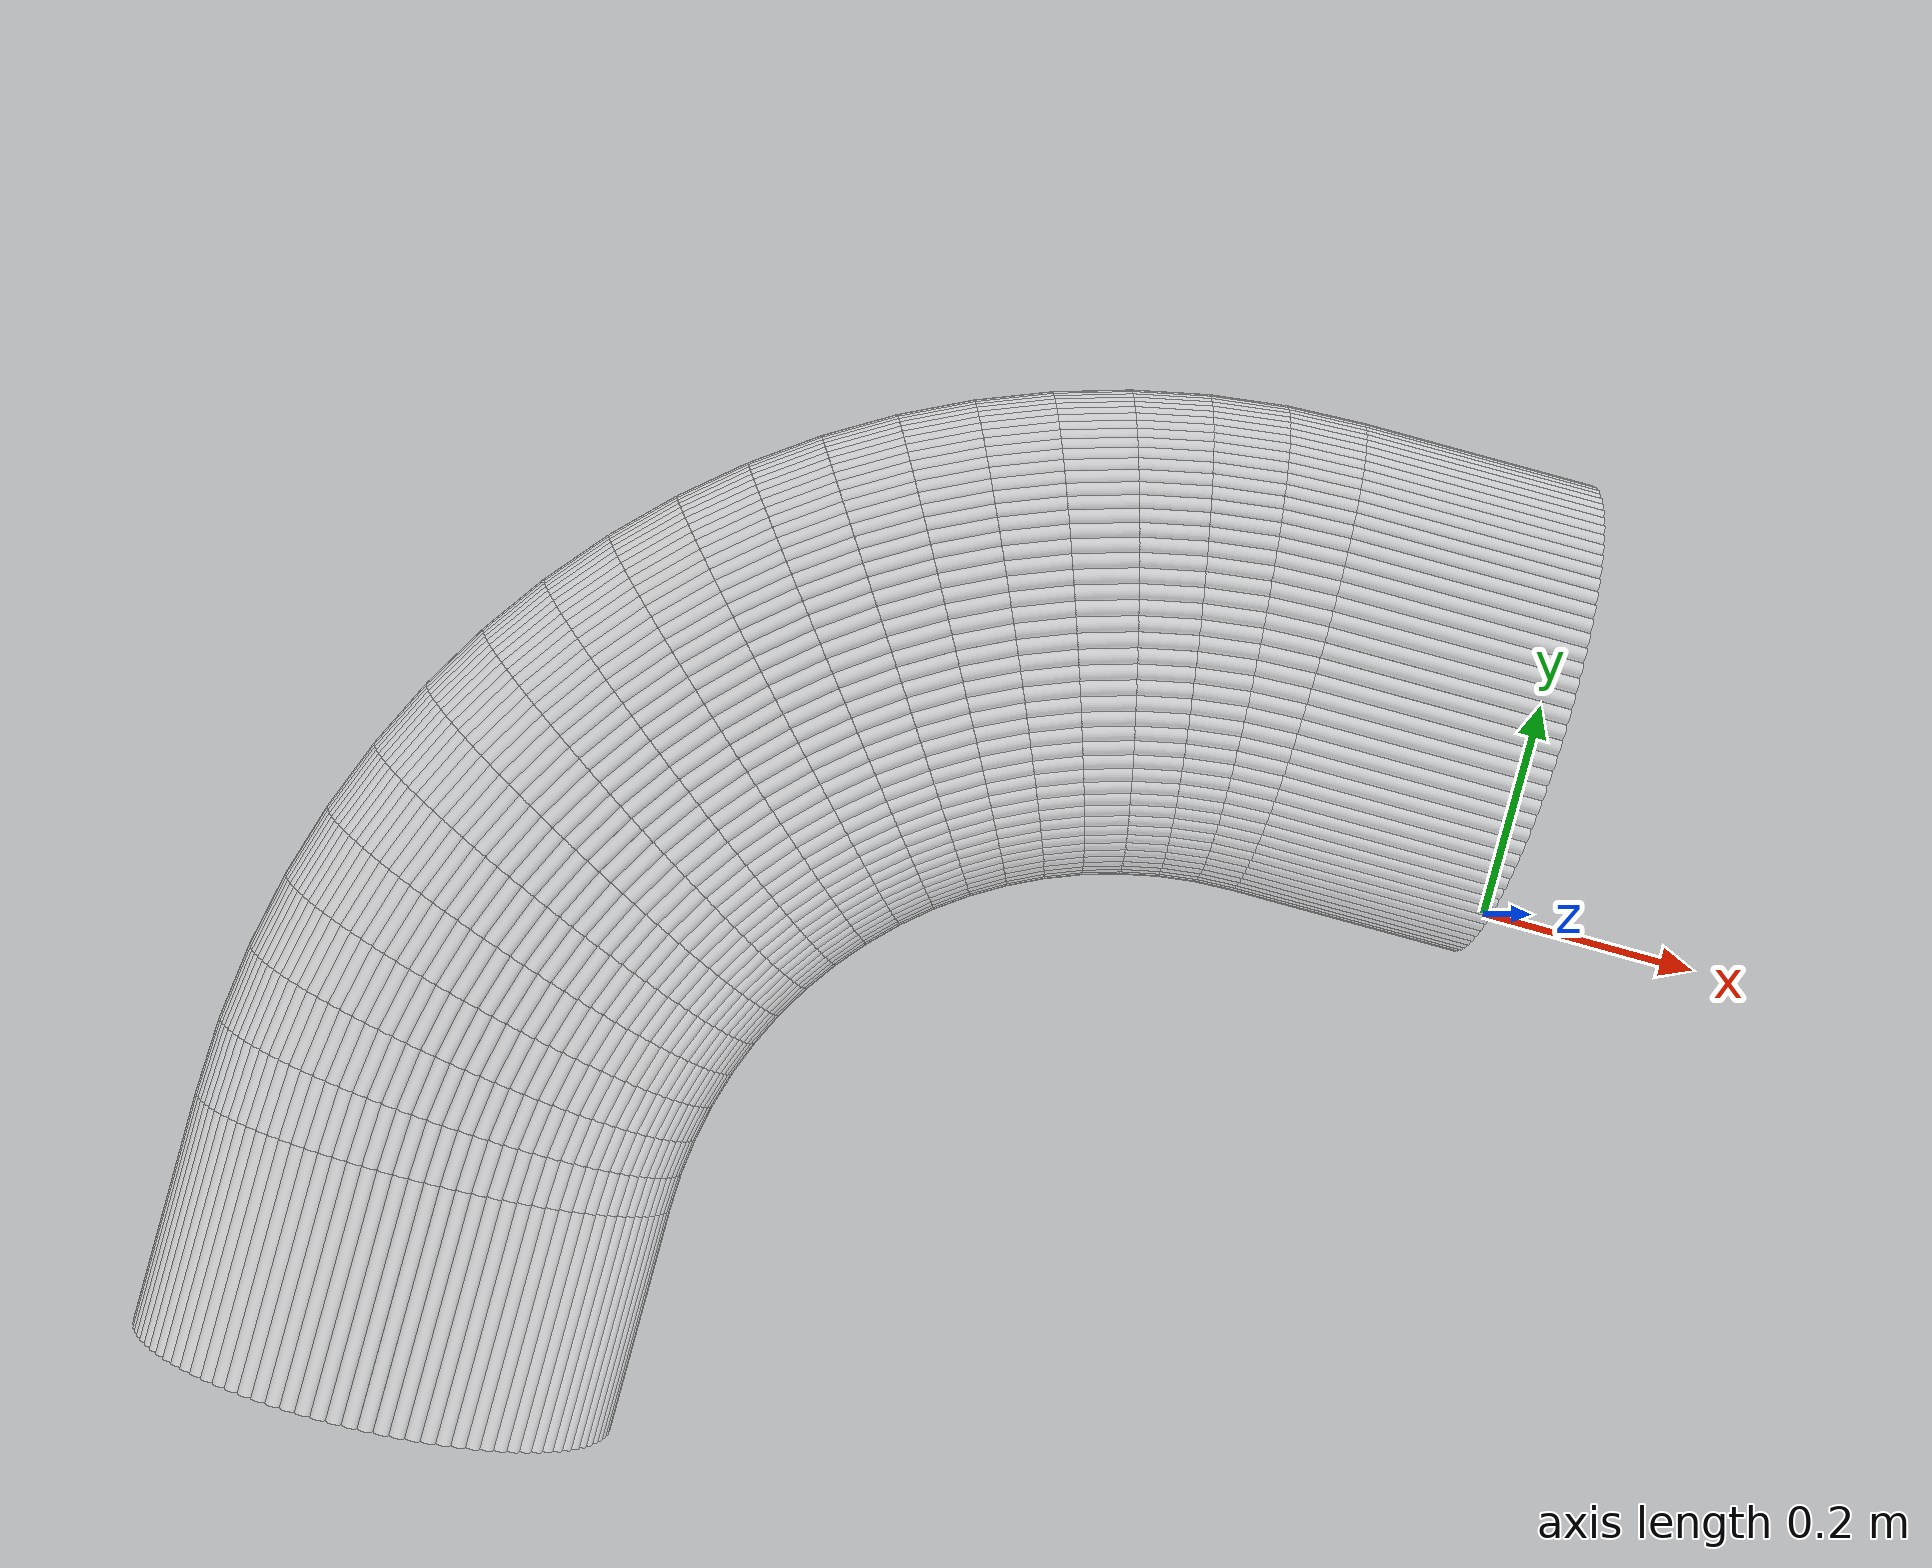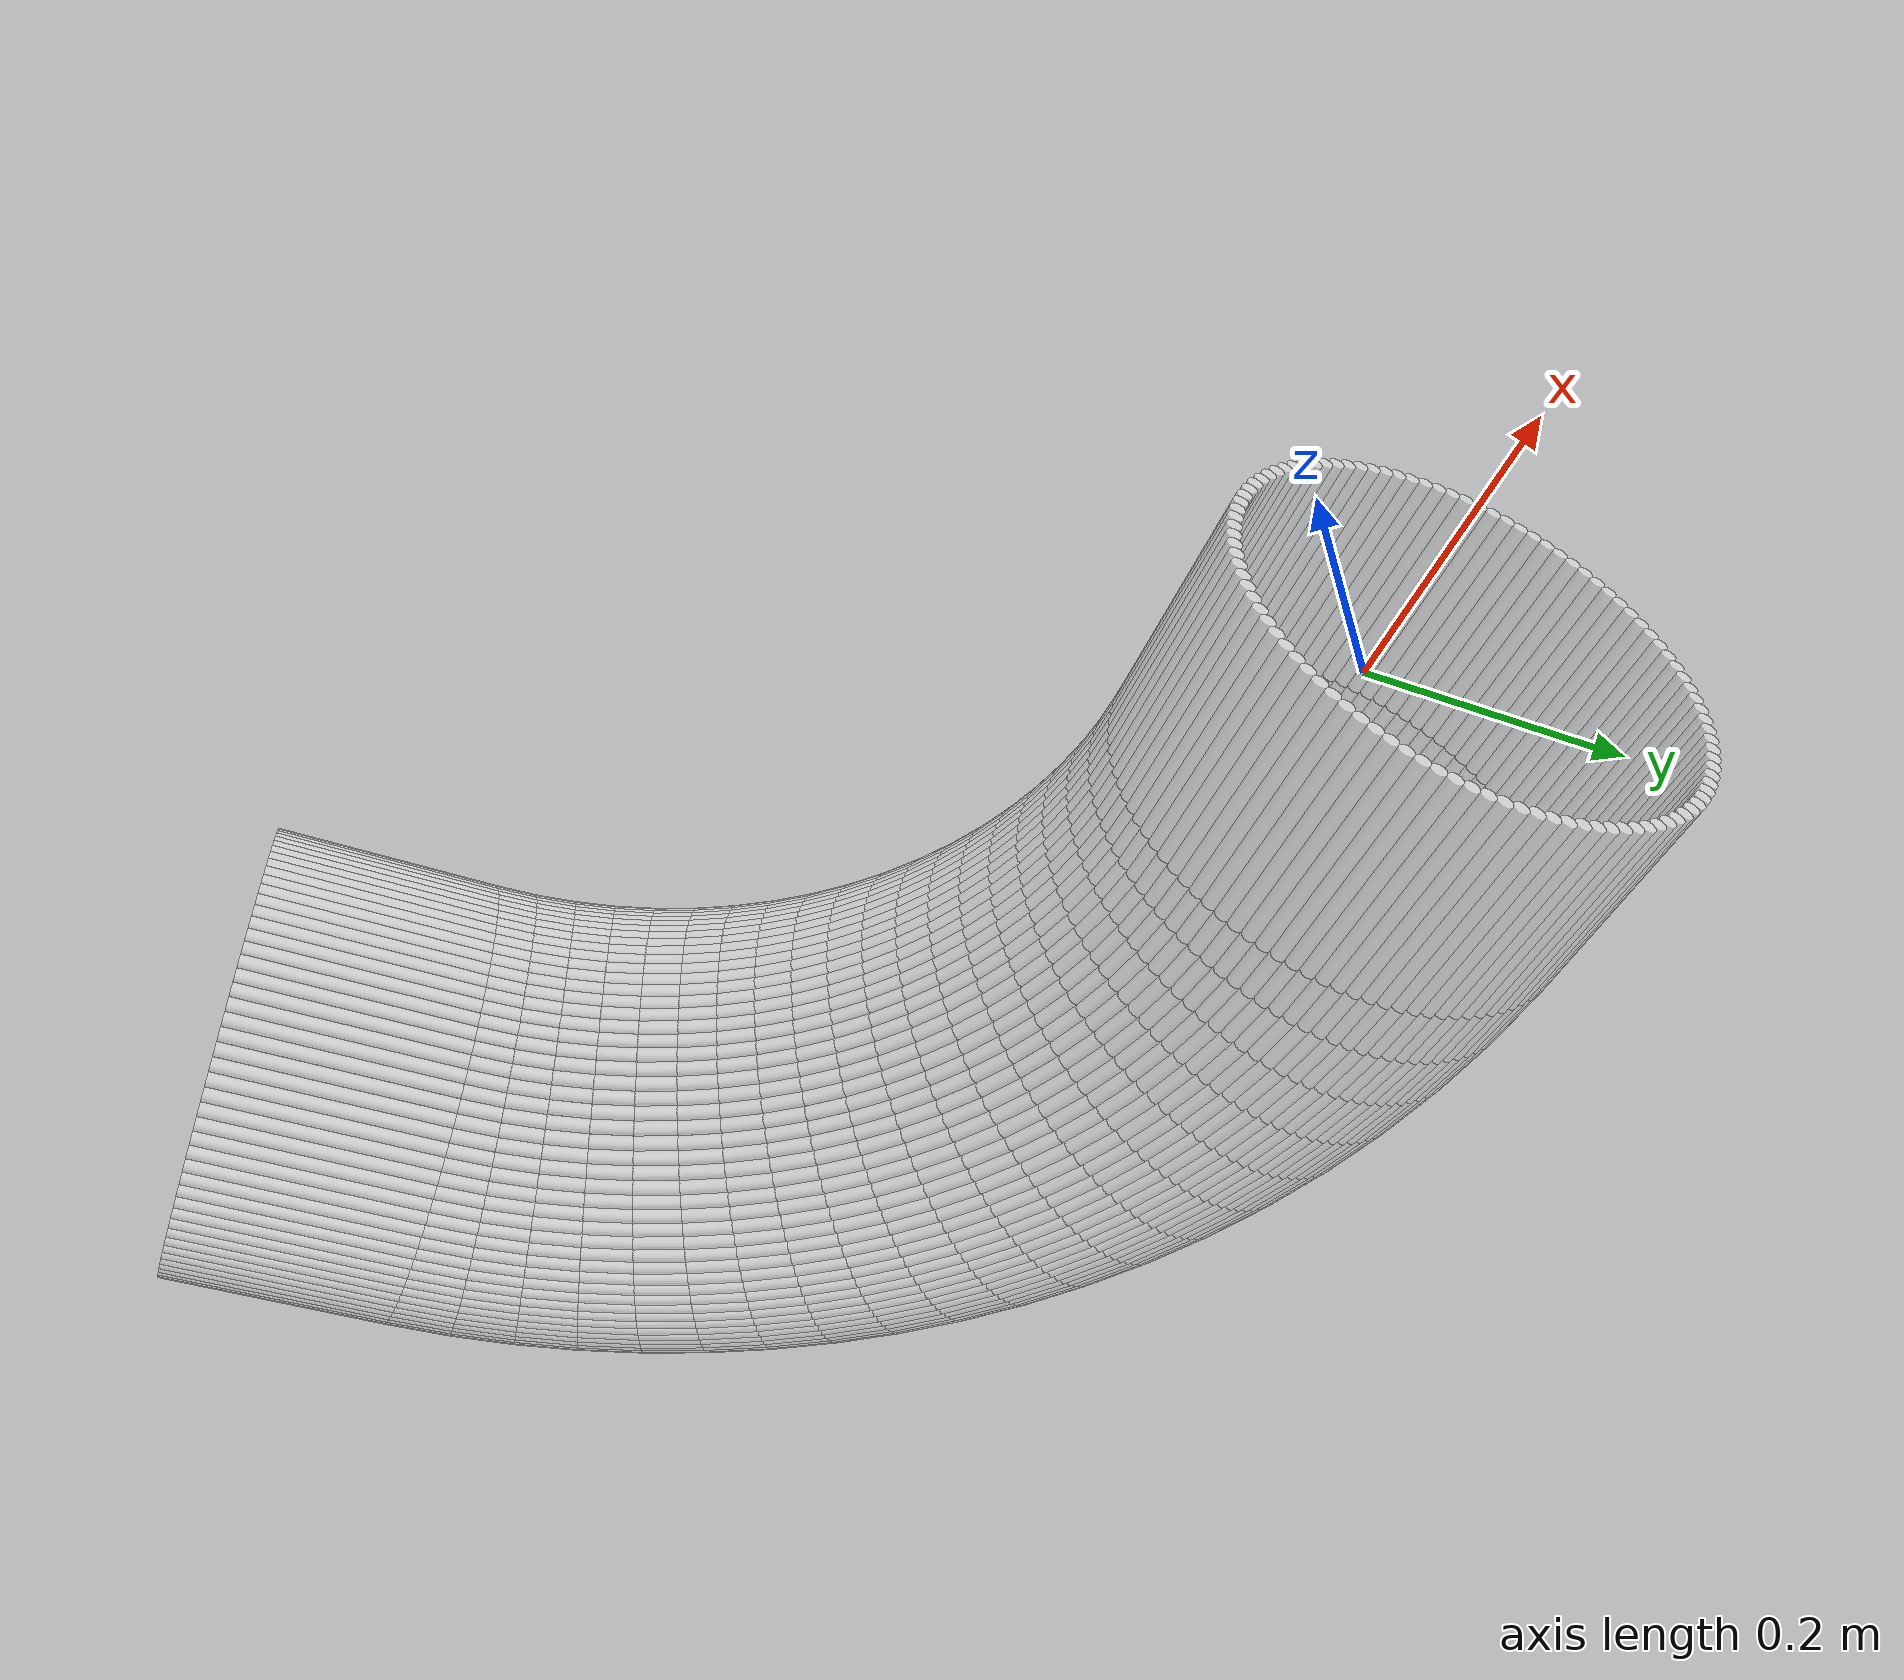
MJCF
<?xml version="1.0" encoding="utf-8"?>
<mujoco>
   <worldbody>
   <body pos="-0.25 -0.44 -0.02" euler="0 0 90">
      <geom euler=" 0 10 0 " fromto="0.8 -0.2 0.2 0.8 0 0.2" rgba="1 1 1 0.35"
            size="0.0062822"
            type="cylinder"/>
      <geom euler=" 0 20 0 " fromto="0.79961 -0.2 0.21256 0.79961 0 0.21256"
            rgba="1 1 1 0.35"
            size="0.0062822"
            type="cylinder"/>
      <geom euler=" 0 30 0 " fromto="0.79842 -0.2 0.22507 0.79842 0 0.22507"
            rgba="1 1 1 0.35"
            size="0.0062822"
            type="cylinder"/>
      <geom euler=" 0 40 0 " fromto="0.79646 -0.2 0.23748 0.79646 0 0.23748"
            rgba="1 1 1 0.35"
            size="0.0062822"
            type="cylinder"/>
      <geom euler=" 0 50 0 " fromto="0.79372 -0.2 0.24974 0.79372 0 0.24974"
            rgba="1 1 1 0.35"
            size="0.0062822"
            type="cylinder"/>
      <geom euler=" 0 60 0 " fromto="0.79021 -0.2 0.2618 0.79021 0 0.2618"
            rgba="1 1 1 0.35"
            size="0.0062822"
            type="cylinder"/>
      <geom euler=" 0 70 0 " fromto="0.78596 -0.2 0.27362 0.78596 0 0.27362"
            rgba="1 1 1 0.35"
            size="0.0062822"
            type="cylinder"/>
      <geom euler=" 0 80 0 " fromto="0.78097 -0.2 0.28516 0.78097 0 0.28516"
            rgba="1 1 1 0.35"
            size="0.0062822"
            type="cylinder"/>
      <geom euler=" 0 90 0 " fromto="0.77526 -0.2 0.29635 0.77526 0 0.29635"
            rgba="1 1 1 0.35"
            size="0.0062822"
            type="cylinder"/>
      <geom euler=" 0 100 0 " fromto="0.76887 -0.2 0.30717 0.76887 0 0.30717"
            rgba="1 1 1 0.35"
            size="0.0062822"
            type="cylinder"/>
      <geom euler=" 0 110 0 " fromto="0.7618 -0.2 0.31756 0.7618 0 0.31756"
            rgba="1 1 1 0.35"
            size="0.0062822"
            type="cylinder"/>
      <geom euler=" 0 120 0 " fromto="0.7541 -0.2 0.32748 0.7541 0 0.32748"
            rgba="1 1 1 0.35"
            size="0.0062822"
            type="cylinder"/>
      <geom euler=" 0 130 0 " fromto="0.74579 -0.2 0.33691 0.74579 0 0.33691"
            rgba="1 1 1 0.35"
            size="0.0062822"
            type="cylinder"/>
      <geom euler=" 0 140 0 " fromto="0.73691 -0.2 0.34579 0.73691 0 0.34579"
            rgba="1 1 1 0.35"
            size="0.0062822"
            type="cylinder"/>
      <geom euler=" 0 150 0 " fromto="0.72748 -0.2 0.3541 0.72748 0 0.3541"
            rgba="1 1 1 0.35"
            size="0.0062822"
            type="cylinder"/>
      <geom euler=" 0 160 0 " fromto="0.71756 -0.2 0.3618 0.71756 0 0.3618"
            rgba="1 1 1 0.35"
            size="0.0062822"
            type="cylinder"/>
      <geom euler=" 0 170 0 " fromto="0.70717 -0.2 0.36887 0.70717 0 0.36887"
            rgba="1 1 1 0.35"
            size="0.0062822"
            type="cylinder"/>
      <geom euler=" 0 180 0 " fromto="0.69635 -0.2 0.37526 0.69635 0 0.37526"
            rgba="1 1 1 0.35"
            size="0.0062822"
            type="cylinder"/>
      <geom euler=" 0 190 0 " fromto="0.68516 -0.2 0.38097 0.68516 0 0.38097"
            rgba="1 1 1 0.35"
            size="0.0062822"
            type="cylinder"/>
      <geom euler=" 0 200 0 " fromto="0.67362 -0.2 0.38596 0.67362 0 0.38596"
            rgba="1 1 1 0.35"
            size="0.0062822"
            type="cylinder"/>
      <geom euler=" 0 210 0 " fromto="0.6618 -0.2 0.39021 0.6618 0 0.39021"
            rgba="1 1 1 0.35"
            size="0.0062822"
            type="cylinder"/>
      <geom euler=" 0 220 0 " fromto="0.64974 -0.2 0.39372 0.64974 0 0.39372"
            rgba="1 1 1 0.35"
            size="0.0062822"
            type="cylinder"/>
      <geom euler=" 0 230 0 " fromto="0.63748 -0.2 0.39646 0.63748 0 0.39646"
            rgba="1 1 1 0.35"
            size="0.0062822"
            type="cylinder"/>
      <geom euler=" 0 240 0 " fromto="0.62507 -0.2 0.39842 0.62507 0 0.39842"
            rgba="1 1 1 0.35"
            size="0.0062822"
            type="cylinder"/>
      <geom euler=" 0 250 0 " fromto="0.61256 -0.2 0.39961 0.61256 0 0.39961"
            rgba="1 1 1 0.35"
            size="0.0062822"
            type="cylinder"/>
      <geom euler=" 0 260 0 " fromto="0.6 -0.2 0.4 0.6 0 0.4" rgba="1 1 1 0.35"
            size="0.0062822"
            type="cylinder"/>
      <geom euler=" 0 270 0 " fromto="0.58744 -0.2 0.39961 0.58744 0 0.39961"
            rgba="1 1 1 0.35"
            size="0.0062822"
            type="cylinder"/>
      <geom euler=" 0 280 0 " fromto="0.57493 -0.2 0.39842 0.57493 0 0.39842"
            rgba="1 1 1 0.35"
            size="0.0062822"
            type="cylinder"/>
      <geom euler=" 0 290 0 " fromto="0.56252 -0.2 0.39646 0.56252 0 0.39646"
            rgba="1 1 1 0.35"
            size="0.0062822"
            type="cylinder"/>
      <geom euler=" 0 300 0 " fromto="0.55026 -0.2 0.39372 0.55026 0 0.39372"
            rgba="1 1 1 0.35"
            size="0.0062822"
            type="cylinder"/>
      <geom euler=" 0 310 0 " fromto="0.5382 -0.2 0.39021 0.5382 0 0.39021"
            rgba="1 1 1 0.35"
            size="0.0062822"
            type="cylinder"/>
      <geom euler=" 0 320 0 " fromto="0.52638 -0.2 0.38596 0.52638 0 0.38596"
            rgba="1 1 1 0.35"
            size="0.0062822"
            type="cylinder"/>
      <geom euler=" 0 330 0 " fromto="0.51484 -0.2 0.38097 0.51484 0 0.38097"
            rgba="1 1 1 0.35"
            size="0.0062822"
            type="cylinder"/>
      <geom euler=" 0 340 0 " fromto="0.50365 -0.2 0.37526 0.50365 0 0.37526"
            rgba="1 1 1 0.35"
            size="0.0062822"
            type="cylinder"/>
      <geom euler=" 0 350 0 " fromto="0.49283 -0.2 0.36887 0.49283 0 0.36887"
            rgba="1 1 1 0.35"
            size="0.0062822"
            type="cylinder"/>
      <geom euler=" 0 360 0 " fromto="0.48244 -0.2 0.3618 0.48244 0 0.3618"
            rgba="1 1 1 0.35"
            size="0.0062822"
            type="cylinder"/>
      <geom euler=" 0 370 0 " fromto="0.47252 -0.2 0.3541 0.47252 0 0.3541"
            rgba="1 1 1 0.35"
            size="0.0062822"
            type="cylinder"/>
      <geom euler=" 0 380 0 " fromto="0.46309 -0.2 0.34579 0.46309 0 0.34579"
            rgba="1 1 1 0.35"
            size="0.0062822"
            type="cylinder"/>
      <geom euler=" 0 390 0 " fromto="0.45421 -0.2 0.33691 0.45421 0 0.33691"
            rgba="1 1 1 0.35"
            size="0.0062822"
            type="cylinder"/>
      <geom euler=" 0 400 0 " fromto="0.4459 -0.2 0.32748 0.4459 0 0.32748"
            rgba="1 1 1 0.35"
            size="0.0062822"
            type="cylinder"/>
      <geom euler=" 0 410 0 " fromto="0.4382 -0.2 0.31756 0.4382 0 0.31756"
            rgba="1 1 1 0.35"
            size="0.0062822"
            type="cylinder"/>
      <geom euler=" 0 420 0 " fromto="0.43113 -0.2 0.30717 0.43113 0 0.30717"
            rgba="1 1 1 0.35"
            size="0.0062822"
            type="cylinder"/>
      <geom euler=" 0 430 0 " fromto="0.42474 -0.2 0.29635 0.42474 0 0.29635"
            rgba="1 1 1 0.35"
            size="0.0062822"
            type="cylinder"/>
      <geom euler=" 0 440 0 " fromto="0.41903 -0.2 0.28516 0.41903 0 0.28516"
            rgba="1 1 1 0.35"
            size="0.0062822"
            type="cylinder"/>
      <geom euler=" 0 450 0 " fromto="0.41404 -0.2 0.27362 0.41404 0 0.27362"
            rgba="1 1 1 0.35"
            size="0.0062822"
            type="cylinder"/>
      <geom euler=" 0 460 0 " fromto="0.40979 -0.2 0.2618 0.40979 0 0.2618"
            rgba="1 1 1 0.35"
            size="0.0062822"
            type="cylinder"/>
      <geom euler=" 0 470 0 " fromto="0.40628 -0.2 0.24974 0.40628 0 0.24974"
            rgba="1 1 1 0.35"
            size="0.0062822"
            type="cylinder"/>
      <geom euler=" 0 480 0 " fromto="0.40354 -0.2 0.23748 0.40354 0 0.23748"
            rgba="1 1 1 0.35"
            size="0.0062822"
            type="cylinder"/>
      <geom euler=" 0 490 0 " fromto="0.40158 -0.2 0.22507 0.40158 0 0.22507"
            rgba="1 1 1 0.35"
            size="0.0062822"
            type="cylinder"/>
      <geom euler=" 0 500 0 " fromto="0.40039 -0.2 0.21256 0.40039 0 0.21256"
            rgba="1 1 1 0.35"
            size="0.0062822"
            type="cylinder"/>
      <geom euler=" 0 510 0 " fromto="0.4 -0.2 0.2 0.4 0 0.2" rgba="1 1 1 0.35"
            size="0.0062822"
            type="cylinder"/>
      <geom euler=" 0 520 0 " fromto="0.40039 -0.2 0.18744 0.40039 0 0.18744"
            rgba="1 1 1 0.35"
            size="0.0062822"
            type="cylinder"/>
      <geom euler=" 0 530 0 " fromto="0.40158 -0.2 0.17493 0.40158 0 0.17493"
            rgba="1 1 1 0.35"
            size="0.0062822"
            type="cylinder"/>
      <geom euler=" 0 540 0 " fromto="0.40354 -0.2 0.16252 0.40354 0 0.16252"
            rgba="1 1 1 0.35"
            size="0.0062822"
            type="cylinder"/>
      <geom euler=" 0 550 0 " fromto="0.40628 -0.2 0.15026 0.40628 0 0.15026"
            rgba="1 1 1 0.35"
            size="0.0062822"
            type="cylinder"/>
      <geom euler=" 0 560 0 " fromto="0.40979 -0.2 0.1382 0.40979 0 0.1382"
            rgba="1 1 1 0.35"
            size="0.0062822"
            type="cylinder"/>
      <geom euler=" 0 570 0 " fromto="0.41404 -0.2 0.12638 0.41404 0 0.12638"
            rgba="1 1 1 0.35"
            size="0.0062822"
            type="cylinder"/>
      <geom euler=" 0 580 0 " fromto="0.41903 -0.2 0.11484 0.41903 0 0.11484"
            rgba="1 1 1 0.35"
            size="0.0062822"
            type="cylinder"/>
      <geom euler=" 0 590 0 " fromto="0.42474 -0.2 0.10365 0.42474 0 0.10365"
            rgba="1 1 1 0.35"
            size="0.0062822"
            type="cylinder"/>
      <geom euler=" 0 600 0 " fromto="0.43113 -0.2 0.092835 0.43113 0 0.092835"
            rgba="1 1 1 0.35"
            size="0.0062822"
            type="cylinder"/>
      <geom euler=" 0 610 0 " fromto="0.4382 -0.2 0.082443 0.4382 0 0.082443"
            rgba="1 1 1 0.35"
            size="0.0062822"
            type="cylinder"/>
      <geom euler=" 0 620 0 " fromto="0.4459 -0.2 0.072515 0.4459 0 0.072515"
            rgba="1 1 1 0.35"
            size="0.0062822"
            type="cylinder"/>
      <geom euler=" 0 630 0 " fromto="0.45421 -0.2 0.063091 0.45421 0 0.063091"
            rgba="1 1 1 0.35"
            size="0.0062822"
            type="cylinder"/>
      <geom euler=" 0 640 0 " fromto="0.46309 -0.2 0.054206 0.46309 0 0.054206"
            rgba="1 1 1 0.35"
            size="0.0062822"
            type="cylinder"/>
      <geom euler=" 0 650 0 " fromto="0.47252 -0.2 0.045897 0.47252 0 0.045897"
            rgba="1 1 1 0.35"
            size="0.0062822"
            type="cylinder"/>
      <geom euler=" 0 660 0 " fromto="0.48244 -0.2 0.038197 0.48244 0 0.038197"
            rgba="1 1 1 0.35"
            size="0.0062822"
            type="cylinder"/>
      <geom euler=" 0 670 0 " fromto="0.49283 -0.2 0.031134 0.49283 0 0.031134"
            rgba="1 1 1 0.35"
            size="0.0062822"
            type="cylinder"/>
      <geom euler=" 0 680 0 " fromto="0.50365 -0.2 0.024739 0.50365 0 0.024739"
            rgba="1 1 1 0.35"
            size="0.0062822"
            type="cylinder"/>
      <geom euler=" 0 690 0 " fromto="0.51484 -0.2 0.019035 0.51484 0 0.019035"
            rgba="1 1 1 0.35"
            size="0.0062822"
            type="cylinder"/>
      <geom euler=" 0 700 0 " fromto="0.52638 -0.2 0.014045 0.52638 0 0.014045"
            rgba="1 1 1 0.35"
            size="0.0062822"
            type="cylinder"/>
      <geom euler=" 0 710 0 " fromto="0.5382 -0.2 0.0097887 0.5382 0 0.0097887"
            rgba="1 1 1 0.35"
            size="0.0062822"
            type="cylinder"/>
      <geom euler=" 0 720 0 " fromto="0.55026 -0.2 0.0062834 0.55026 0 0.0062834"
            rgba="1 1 1 0.35"
            size="0.0062822"
            type="cylinder"/>
      <geom euler=" 0 730 0 " fromto="0.56252 -0.2 0.0035425 0.56252 0 0.0035425"
            rgba="1 1 1 0.35"
            size="0.0062822"
            type="cylinder"/>
      <geom euler=" 0 740 0 " fromto="0.57493 -0.2 0.0015771 0.57493 0 0.0015771"
            rgba="1 1 1 0.35"
            size="0.0062822"
            type="cylinder"/>
      <geom euler=" 0 750 0 " fromto="0.58744 -0.2 0.00039465 0.58744 0 0.00039465"
            rgba="1 1 1 0.35"
            size="0.0062822"
            type="cylinder"/>
      <geom euler=" 0 760 0 " fromto="0.6 -0.2 0 0.6 0 0" rgba="1 1 1 0.35"
            size="0.0062822"
            type="cylinder"/>
      <geom euler=" 0 770 0 " fromto="0.61256 -0.2 0.00039465 0.61256 0 0.00039465"
            rgba="1 1 1 0.35"
            size="0.0062822"
            type="cylinder"/>
      <geom euler=" 0 780 0 " fromto="0.62507 -0.2 0.0015771 0.62507 0 0.0015771"
            rgba="1 1 1 0.35"
            size="0.0062822"
            type="cylinder"/>
      <geom euler=" 0 790 0 " fromto="0.63748 -0.2 0.0035425 0.63748 0 0.0035425"
            rgba="1 1 1 0.35"
            size="0.0062822"
            type="cylinder"/>
      <geom euler=" 0 800 0 " fromto="0.64974 -0.2 0.0062834 0.64974 0 0.0062834"
            rgba="1 1 1 0.35"
            size="0.0062822"
            type="cylinder"/>
      <geom euler=" 0 810 0 " fromto="0.6618 -0.2 0.0097887 0.6618 0 0.0097887"
            rgba="1 1 1 0.35"
            size="0.0062822"
            type="cylinder"/>
      <geom euler=" 0 820 0 " fromto="0.67362 -0.2 0.014045 0.67362 0 0.014045"
            rgba="1 1 1 0.35"
            size="0.0062822"
            type="cylinder"/>
      <geom euler=" 0 830 0 " fromto="0.68516 -0.2 0.019035 0.68516 0 0.019035"
            rgba="1 1 1 0.35"
            size="0.0062822"
            type="cylinder"/>
      <geom euler=" 0 840 0 " fromto="0.69635 -0.2 0.024739 0.69635 0 0.024739"
            rgba="1 1 1 0.35"
            size="0.0062822"
            type="cylinder"/>
      <geom euler=" 0 850 0 " fromto="0.70717 -0.2 0.031134 0.70717 0 0.031134"
            rgba="1 1 1 0.35"
            size="0.0062822"
            type="cylinder"/>
      <geom euler=" 0 860 0 " fromto="0.71756 -0.2 0.038197 0.71756 0 0.038197"
            rgba="1 1 1 0.35"
            size="0.0062822"
            type="cylinder"/>
      <geom euler=" 0 870 0 " fromto="0.72748 -0.2 0.045897 0.72748 0 0.045897"
            rgba="1 1 1 0.35"
            size="0.0062822"
            type="cylinder"/>
      <geom euler=" 0 880 0 " fromto="0.73691 -0.2 0.054206 0.73691 0 0.054206"
            rgba="1 1 1 0.35"
            size="0.0062822"
            type="cylinder"/>
      <geom euler=" 0 890 0 " fromto="0.74579 -0.2 0.063091 0.74579 0 0.063091"
            rgba="1 1 1 0.35"
            size="0.0062822"
            type="cylinder"/>
      <geom euler=" 0 900 0 " fromto="0.7541 -0.2 0.072515 0.7541 0 0.072515"
            rgba="1 1 1 0.35"
            size="0.0062822"
            type="cylinder"/>
      <geom euler=" 0 910 0 " fromto="0.7618 -0.2 0.082443 0.7618 0 0.082443"
            rgba="1 1 1 0.35"
            size="0.0062822"
            type="cylinder"/>
      <geom euler=" 0 920 0 " fromto="0.76887 -0.2 0.092835 0.76887 0 0.092835"
            rgba="1 1 1 0.35"
            size="0.0062822"
            type="cylinder"/>
      <geom euler=" 0 930 0 " fromto="0.77526 -0.2 0.10365 0.77526 0 0.10365"
            rgba="1 1 1 0.35"
            size="0.0062822"
            type="cylinder"/>
      <geom euler=" 0 940 0 " fromto="0.78097 -0.2 0.11484 0.78097 0 0.11484"
            rgba="1 1 1 0.35"
            size="0.0062822"
            type="cylinder"/>
      <geom euler=" 0 950 0 " fromto="0.78596 -0.2 0.12638 0.78596 0 0.12638"
            rgba="1 1 1 0.35"
            size="0.0062822"
            type="cylinder"/>
      <geom euler=" 0 960 0 " fromto="0.79021 -0.2 0.1382 0.79021 0 0.1382"
            rgba="1 1 1 0.35"
            size="0.0062822"
            type="cylinder"/>
      <geom euler=" 0 970 0 " fromto="0.79372 -0.2 0.15026 0.79372 0 0.15026"
            rgba="1 1 1 0.35"
            size="0.0062822"
            type="cylinder"/>
      <geom euler=" 0 980 0 " fromto="0.79646 -0.2 0.16252 0.79646 0 0.16252"
            rgba="1 1 1 0.35"
            size="0.0062822"
            type="cylinder"/>
      <geom euler=" 0 990 0 " fromto="0.79842 -0.2 0.17493 0.79842 0 0.17493"
            rgba="1 1 1 0.35"
            size="0.0062822"
            type="cylinder"/>
      <geom euler=" 0 1000 0 " fromto="0.79961 -0.2 0.18744 0.79961 0 0.18744"
            rgba="1 1 1 0.35"
            size="0.0062822"
            type="cylinder"/>
      <geom euler=" 0 10 0 " fromto="0.8 0 0.2 0.79727 0.066063 0.2" rgba="1 1 1 0.35"
            size="0.0062822"
            type="cylinder"/>
      <geom euler=" 0 20 0 " fromto="0.79961 0 0.21256 0.79687 0.066031 0.21256"
            rgba="1 1 1 0.35"
            size="0.0062822"
            type="cylinder"/>
      <geom euler=" 0 30 0 " fromto="0.79842 0 0.22507 0.7957 0.065933 0.22507"
            rgba="1 1 1 0.35"
            size="0.0062822"
            type="cylinder"/>
      <geom euler=" 0 40 0 " fromto="0.79646 0 0.23748 0.79374 0.065771 0.23748"
            rgba="1 1 1 0.35"
            size="0.0062822"
            type="cylinder"/>
      <geom euler=" 0 50 0 " fromto="0.79372 0 0.24974 0.79101 0.065545 0.24974"
            rgba="1 1 1 0.35"
            size="0.0062822"
            type="cylinder"/>
      <geom euler=" 0 60 0 " fromto="0.79021 0 0.2618 0.78751 0.065255 0.2618"
            rgba="1 1 1 0.35"
            size="0.0062822"
            type="cylinder"/>
      <geom euler=" 0 70 0 " fromto="0.78596 0 0.27362 0.78327 0.064904 0.27362"
            rgba="1 1 1 0.35"
            size="0.0062822"
            type="cylinder"/>
      <geom euler=" 0 80 0 " fromto="0.78097 0 0.28516 0.7783 0.064492 0.28516"
            rgba="1 1 1 0.35"
            size="0.0062822"
            type="cylinder"/>
      <geom euler=" 0 90 0 " fromto="0.77526 0 0.29635 0.77261 0.064021 0.29635"
            rgba="1 1 1 0.35"
            size="0.0062822"
            type="cylinder"/>
      <geom euler=" 0 100 0 " fromto="0.76887 0 0.30717 0.76624 0.063492 0.30717"
            rgba="1 1 1 0.35"
            size="0.0062822"
            type="cylinder"/>
      <geom euler=" 0 110 0 " fromto="0.7618 0 0.31756 0.7592 0.062909 0.31756"
            rgba="1 1 1 0.35"
            size="0.0062822"
            type="cylinder"/>
      <geom euler=" 0 120 0 " fromto="0.7541 0 0.32748 0.75153 0.062273 0.32748"
            rgba="1 1 1 0.35"
            size="0.0062822"
            type="cylinder"/>
      <geom euler=" 0 130 0 " fromto="0.74579 0 0.33691 0.74325 0.061587 0.33691"
            rgba="1 1 1 0.35"
            size="0.0062822"
            type="cylinder"/>
      <geom euler=" 0 140 0 " fromto="0.73691 0 0.34579 0.73439 0.060853 0.34579"
            rgba="1 1 1 0.35"
            size="0.0062822"
            type="cylinder"/>
      <geom euler=" 0 150 0 " fromto="0.72748 0 0.3541 0.725 0.060075 0.3541"
            rgba="1 1 1 0.35"
            size="0.0062822"
            type="cylinder"/>
      <geom euler=" 0 160 0 " fromto="0.71756 0 0.3618 0.71511 0.059255 0.3618"
            rgba="1 1 1 0.35"
            size="0.0062822"
            type="cylinder"/>
      <geom euler=" 0 170 0 " fromto="0.70717 0 0.36887 0.70475 0.058397 0.36887"
            rgba="1 1 1 0.35"
            size="0.0062822"
            type="cylinder"/>
      <geom euler=" 0 180 0 " fromto="0.69635 0 0.37526 0.69397 0.057504 0.37526"
            rgba="1 1 1 0.35"
            size="0.0062822"
            type="cylinder"/>
      <geom euler=" 0 190 0 " fromto="0.68516 0 0.38097 0.68282 0.05658 0.38097"
            rgba="1 1 1 0.35"
            size="0.0062822"
            type="cylinder"/>
      <geom euler=" 0 200 0 " fromto="0.67362 0 0.38596 0.67132 0.055628 0.38596"
            rgba="1 1 1 0.35"
            size="0.0062822"
            type="cylinder"/>
      <geom euler=" 0 210 0 " fromto="0.6618 0 0.39021 0.65954 0.054651 0.39021"
            rgba="1 1 1 0.35"
            size="0.0062822"
            type="cylinder"/>
      <geom euler=" 0 220 0 " fromto="0.64974 0 0.39372 0.64752 0.053655 0.39372"
            rgba="1 1 1 0.35"
            size="0.0062822"
            type="cylinder"/>
      <geom euler=" 0 230 0 " fromto="0.63748 0 0.39646 0.6353 0.052642 0.39646"
            rgba="1 1 1 0.35"
            size="0.0062822"
            type="cylinder"/>
      <geom euler=" 0 240 0 " fromto="0.62507 0 0.39842 0.62293 0.051618 0.39842"
            rgba="1 1 1 0.35"
            size="0.0062822"
            type="cylinder"/>
      <geom euler=" 0 250 0 " fromto="0.61256 0 0.39961 0.61047 0.050585 0.39961"
            rgba="1 1 1 0.35"
            size="0.0062822"
            type="cylinder"/>
      <geom euler=" 0 260 0 " fromto="0.6 0 0.4 0.59795 0.049548 0.4" rgba="1 1 1 0.35"
            size="0.0062822"
            type="cylinder"/>
      <geom euler=" 0 270 0 " fromto="0.58744 0 0.39961 0.58544 0.048511 0.39961"
            rgba="1 1 1 0.35"
            size="0.0062822"
            type="cylinder"/>
      <geom euler=" 0 280 0 " fromto="0.57493 0 0.39842 0.57297 0.047478 0.39842"
            rgba="1 1 1 0.35"
            size="0.0062822"
            type="cylinder"/>
      <geom euler=" 0 290 0 " fromto="0.56252 0 0.39646 0.5606 0.046453 0.39646"
            rgba="1 1 1 0.35"
            size="0.0062822"
            type="cylinder"/>
      <geom euler=" 0 300 0 " fromto="0.55026 0 0.39372 0.54838 0.04544 0.39372"
            rgba="1 1 1 0.35"
            size="0.0062822"
            type="cylinder"/>
      <geom euler=" 0 310 0 " fromto="0.5382 0 0.39021 0.53636 0.044444 0.39021"
            rgba="1 1 1 0.35"
            size="0.0062822"
            type="cylinder"/>
      <geom euler=" 0 320 0 " fromto="0.52638 0 0.38596 0.52458 0.043468 0.38596"
            rgba="1 1 1 0.35"
            size="0.0062822"
            type="cylinder"/>
      <geom euler=" 0 330 0 " fromto="0.51484 0 0.38097 0.51309 0.042515 0.38097"
            rgba="1 1 1 0.35"
            size="0.0062822"
            type="cylinder"/>
      <geom euler=" 0 340 0 " fromto="0.50365 0 0.37526 0.50193 0.041591 0.37526"
            rgba="1 1 1 0.35"
            size="0.0062822"
            type="cylinder"/>
      <geom euler=" 0 350 0 " fromto="0.49283 0 0.36887 0.49115 0.040698 0.36887"
            rgba="1 1 1 0.35"
            size="0.0062822"
            type="cylinder"/>
      <geom euler=" 0 360 0 " fromto="0.48244 0 0.3618 0.4808 0.03984 0.3618"
            rgba="1 1 1 0.35"
            size="0.0062822"
            type="cylinder"/>
      <geom euler=" 0 370 0 " fromto="0.47252 0 0.3541 0.4709 0.03902 0.3541"
            rgba="1 1 1 0.35"
            size="0.0062822"
            type="cylinder"/>
      <geom euler=" 0 380 0 " fromto="0.46309 0 0.34579 0.46151 0.038242 0.34579"
            rgba="1 1 1 0.35"
            size="0.0062822"
            type="cylinder"/>
      <geom euler=" 0 390 0 " fromto="0.45421 0 0.33691 0.45265 0.037508 0.33691"
            rgba="1 1 1 0.35"
            size="0.0062822"
            type="cylinder"/>
      <geom euler=" 0 400 0 " fromto="0.4459 0 0.32748 0.44437 0.036822 0.32748"
            rgba="1 1 1 0.35"
            size="0.0062822"
            type="cylinder"/>
      <geom euler=" 0 410 0 " fromto="0.4382 0 0.31756 0.4367 0.036186 0.31756"
            rgba="1 1 1 0.35"
            size="0.0062822"
            type="cylinder"/>
      <geom euler=" 0 420 0 " fromto="0.43113 0 0.30717 0.42966 0.035603 0.30717"
            rgba="1 1 1 0.35"
            size="0.0062822"
            type="cylinder"/>
      <geom euler=" 0 430 0 " fromto="0.42474 0 0.29635 0.42329 0.035075 0.29635"
            rgba="1 1 1 0.35"
            size="0.0062822"
            type="cylinder"/>
      <geom euler=" 0 440 0 " fromto="0.41903 0 0.28516 0.4176 0.034604 0.28516"
            rgba="1 1 1 0.35"
            size="0.0062822"
            type="cylinder"/>
      <geom euler=" 0 450 0 " fromto="0.41404 0 0.27362 0.41263 0.034192 0.27362"
            rgba="1 1 1 0.35"
            size="0.0062822"
            type="cylinder"/>
      <geom euler=" 0 460 0 " fromto="0.40979 0 0.2618 0.40839 0.03384 0.2618"
            rgba="1 1 1 0.35"
            size="0.0062822"
            type="cylinder"/>
      <geom euler=" 0 470 0 " fromto="0.40628 0 0.24974 0.4049 0.033551 0.24974"
            rgba="1 1 1 0.35"
            size="0.0062822"
            type="cylinder"/>
      <geom euler=" 0 480 0 " fromto="0.40354 0 0.23748 0.40216 0.033324 0.23748"
            rgba="1 1 1 0.35"
            size="0.0062822"
            type="cylinder"/>
      <geom euler=" 0 490 0 " fromto="0.40158 0 0.22507 0.40021 0.033162 0.22507"
            rgba="1 1 1 0.35"
            size="0.0062822"
            type="cylinder"/>
      <geom euler=" 0 500 0 " fromto="0.40039 0 0.21256 0.39903 0.033064 0.21256"
            rgba="1 1 1 0.35"
            size="0.0062822"
            type="cylinder"/>
      <geom euler=" 0 510 0 " fromto="0.4 0 0.2 0.39863 0.033032 0.2" rgba="1 1 1 0.35"
            size="0.0062822"
            type="cylinder"/>
      <geom euler=" 0 520 0 " fromto="0.40039 0 0.18744 0.39903 0.033064 0.18744"
            rgba="1 1 1 0.35"
            size="0.0062822"
            type="cylinder"/>
      <geom euler=" 0 530 0 " fromto="0.40158 0 0.17493 0.40021 0.033162 0.17493"
            rgba="1 1 1 0.35"
            size="0.0062822"
            type="cylinder"/>
      <geom euler=" 0 540 0 " fromto="0.40354 0 0.16252 0.40216 0.033324 0.16252"
            rgba="1 1 1 0.35"
            size="0.0062822"
            type="cylinder"/>
      <geom euler=" 0 550 0 " fromto="0.40628 0 0.15026 0.4049 0.033551 0.15026"
            rgba="1 1 1 0.35"
            size="0.0062822"
            type="cylinder"/>
      <geom euler=" 0 560 0 " fromto="0.40979 0 0.1382 0.40839 0.03384 0.1382"
            rgba="1 1 1 0.35"
            size="0.0062822"
            type="cylinder"/>
      <geom euler=" 0 570 0 " fromto="0.41404 0 0.12638 0.41263 0.034192 0.12638"
            rgba="1 1 1 0.35"
            size="0.0062822"
            type="cylinder"/>
      <geom euler=" 0 580 0 " fromto="0.41903 0 0.11484 0.4176 0.034604 0.11484"
            rgba="1 1 1 0.35"
            size="0.0062822"
            type="cylinder"/>
      <geom euler=" 0 590 0 " fromto="0.42474 0 0.10365 0.42329 0.035075 0.10365"
            rgba="1 1 1 0.35"
            size="0.0062822"
            type="cylinder"/>
      <geom euler=" 0 600 0 " fromto="0.43113 0 0.092835 0.42966 0.035603 0.092835"
            rgba="1 1 1 0.35"
            size="0.0062822"
            type="cylinder"/>
      <geom euler=" 0 610 0 " fromto="0.4382 0 0.082443 0.4367 0.036186 0.082443"
            rgba="1 1 1 0.35"
            size="0.0062822"
            type="cylinder"/>
      <geom euler=" 0 620 0 " fromto="0.4459 0 0.072515 0.44437 0.036822 0.072515"
            rgba="1 1 1 0.35"
            size="0.0062822"
            type="cylinder"/>
      <geom euler=" 0 630 0 " fromto="0.45421 0 0.063091 0.45265 0.037508 0.063091"
            rgba="1 1 1 0.35"
            size="0.0062822"
            type="cylinder"/>
      <geom euler=" 0 640 0 " fromto="0.46309 0 0.054206 0.46151 0.038242 0.054206"
            rgba="1 1 1 0.35"
            size="0.0062822"
            type="cylinder"/>
      <geom euler=" 0 650 0 " fromto="0.47252 0 0.045897 0.4709 0.03902 0.045897"
            rgba="1 1 1 0.35"
            size="0.0062822"
            type="cylinder"/>
      <geom euler=" 0 660 0 " fromto="0.48244 0 0.038197 0.4808 0.03984 0.038197"
            rgba="1 1 1 0.35"
            size="0.0062822"
            type="cylinder"/>
      <geom euler=" 0 670 0 " fromto="0.49283 0 0.031134 0.49115 0.040698 0.031134"
            rgba="1 1 1 0.35"
            size="0.0062822"
            type="cylinder"/>
      <geom euler=" 0 680 0 " fromto="0.50365 0 0.024739 0.50193 0.041591 0.024739"
            rgba="1 1 1 0.35"
            size="0.0062822"
            type="cylinder"/>
      <geom euler=" 0 690 0 " fromto="0.51484 0 0.019035 0.51309 0.042515 0.019035"
            rgba="1 1 1 0.35"
            size="0.0062822"
            type="cylinder"/>
      <geom euler=" 0 700 0 " fromto="0.52638 0 0.014045 0.52458 0.043468 0.014045"
            rgba="1 1 1 0.35"
            size="0.0062822"
            type="cylinder"/>
      <geom euler=" 0 710 0 " fromto="0.5382 0 0.0097887 0.53636 0.044444 0.0097887"
            rgba="1 1 1 0.35"
            size="0.0062822"
            type="cylinder"/>
      <geom euler=" 0 720 0 " fromto="0.55026 0 0.0062834 0.54838 0.04544 0.0062834"
            rgba="1 1 1 0.35"
            size="0.0062822"
            type="cylinder"/>
      <geom euler=" 0 730 0 " fromto="0.56252 0 0.0035425 0.5606 0.046453 0.0035425"
            rgba="1 1 1 0.35"
            size="0.0062822"
            type="cylinder"/>
      <geom euler=" 0 740 0 " fromto="0.57493 0 0.0015771 0.57297 0.047478 0.0015771"
            rgba="1 1 1 0.35"
            size="0.0062822"
            type="cylinder"/>
      <geom euler=" 0 750 0 " fromto="0.58744 0 0.00039465 0.58544 0.048511 0.00039465"
            rgba="1 1 1 0.35"
            size="0.0062822"
            type="cylinder"/>
      <geom euler=" 0 760 0 " fromto="0.6 0 0 0.59795 0.049548 0" rgba="1 1 1 0.35"
            size="0.0062822"
            type="cylinder"/>
      <geom euler=" 0 770 0 " fromto="0.61256 0 0.00039465 0.61047 0.050585 0.00039465"
            rgba="1 1 1 0.35"
            size="0.0062822"
            type="cylinder"/>
      <geom euler=" 0 780 0 " fromto="0.62507 0 0.0015771 0.62293 0.051618 0.0015771"
            rgba="1 1 1 0.35"
            size="0.0062822"
            type="cylinder"/>
      <geom euler=" 0 790 0 " fromto="0.63748 0 0.0035425 0.6353 0.052642 0.0035425"
            rgba="1 1 1 0.35"
            size="0.0062822"
            type="cylinder"/>
      <geom euler=" 0 800 0 " fromto="0.64974 0 0.0062834 0.64752 0.053655 0.0062834"
            rgba="1 1 1 0.35"
            size="0.0062822"
            type="cylinder"/>
      <geom euler=" 0 810 0 " fromto="0.6618 0 0.0097887 0.65954 0.054651 0.0097887"
            rgba="1 1 1 0.35"
            size="0.0062822"
            type="cylinder"/>
      <geom euler=" 0 820 0 " fromto="0.67362 0 0.014045 0.67132 0.055628 0.014045"
            rgba="1 1 1 0.35"
            size="0.0062822"
            type="cylinder"/>
      <geom euler=" 0 830 0 " fromto="0.68516 0 0.019035 0.68282 0.05658 0.019035"
            rgba="1 1 1 0.35"
            size="0.0062822"
            type="cylinder"/>
      <geom euler=" 0 840 0 " fromto="0.69635 0 0.024739 0.69397 0.057504 0.024739"
            rgba="1 1 1 0.35"
            size="0.0062822"
            type="cylinder"/>
      <geom euler=" 0 850 0 " fromto="0.70717 0 0.031134 0.70475 0.058397 0.031134"
            rgba="1 1 1 0.35"
            size="0.0062822"
            type="cylinder"/>
      <geom euler=" 0 860 0 " fromto="0.71756 0 0.038197 0.71511 0.059255 0.038197"
            rgba="1 1 1 0.35"
            size="0.0062822"
            type="cylinder"/>
      <geom euler=" 0 870 0 " fromto="0.72748 0 0.045897 0.725 0.060075 0.045897"
            rgba="1 1 1 0.35"
            size="0.0062822"
            type="cylinder"/>
      <geom euler=" 0 880 0 " fromto="0.73691 0 0.054206 0.73439 0.060853 0.054206"
            rgba="1 1 1 0.35"
            size="0.0062822"
            type="cylinder"/>
      <geom euler=" 0 890 0 " fromto="0.74579 0 0.063091 0.74325 0.061587 0.063091"
            rgba="1 1 1 0.35"
            size="0.0062822"
            type="cylinder"/>
      <geom euler=" 0 900 0 " fromto="0.7541 0 0.072515 0.75153 0.062273 0.072515"
            rgba="1 1 1 0.35"
            size="0.0062822"
            type="cylinder"/>
      <geom euler=" 0 910 0 " fromto="0.7618 0 0.082443 0.7592 0.062909 0.082443"
            rgba="1 1 1 0.35"
            size="0.0062822"
            type="cylinder"/>
      <geom euler=" 0 920 0 " fromto="0.76887 0 0.092835 0.76624 0.063492 0.092835"
            rgba="1 1 1 0.35"
            size="0.0062822"
            type="cylinder"/>
      <geom euler=" 0 930 0 " fromto="0.77526 0 0.10365 0.77261 0.064021 0.10365"
            rgba="1 1 1 0.35"
            size="0.0062822"
            type="cylinder"/>
      <geom euler=" 0 940 0 " fromto="0.78097 0 0.11484 0.7783 0.064492 0.11484"
            rgba="1 1 1 0.35"
            size="0.0062822"
            type="cylinder"/>
      <geom euler=" 0 950 0 " fromto="0.78596 0 0.12638 0.78327 0.064904 0.12638"
            rgba="1 1 1 0.35"
            size="0.0062822"
            type="cylinder"/>
      <geom euler=" 0 960 0 " fromto="0.79021 0 0.1382 0.78751 0.065255 0.1382"
            rgba="1 1 1 0.35"
            size="0.0062822"
            type="cylinder"/>
      <geom euler=" 0 970 0 " fromto="0.79372 0 0.15026 0.79101 0.065545 0.15026"
            rgba="1 1 1 0.35"
            size="0.0062822"
            type="cylinder"/>
      <geom euler=" 0 980 0 " fromto="0.79646 0 0.16252 0.79374 0.065771 0.16252"
            rgba="1 1 1 0.35"
            size="0.0062822"
            type="cylinder"/>
      <geom euler=" 0 990 0 " fromto="0.79842 0 0.17493 0.7957 0.065933 0.17493"
            rgba="1 1 1 0.35"
            size="0.0062822"
            type="cylinder"/>
      <geom euler=" 0 1000 0 " fromto="0.79961 0 0.18744 0.79687 0.066031 0.18744"
            rgba="1 1 1 0.35"
            size="0.0062822"
            type="cylinder"/>
      <geom euler=" 0 10 0 " fromto="0.79727 0.066063 0.2 0.78909 0.13168 0.2"
            rgba="1 1 1 0.35"
            size="0.0062822"
            type="cylinder"/>
      <geom euler=" 0 20 0 " fromto="0.79687 0.066031 0.21256 0.7887 0.13161 0.21256"
            rgba="1 1 1 0.35"
            size="0.0062822"
            type="cylinder"/>
      <geom euler=" 0 30 0 " fromto="0.7957 0.065933 0.22507 0.78753 0.13142 0.22507"
            rgba="1 1 1 0.35"
            size="0.0062822"
            type="cylinder"/>
      <geom euler=" 0 40 0 " fromto="0.79374 0.065771 0.23748 0.78559 0.13109 0.23748"
            rgba="1 1 1 0.35"
            size="0.0062822"
            type="cylinder"/>
      <geom euler=" 0 50 0 " fromto="0.79101 0.065545 0.24974 0.78289 0.13064 0.24974"
            rgba="1 1 1 0.35"
            size="0.0062822"
            type="cylinder"/>
      <geom euler=" 0 60 0 " fromto="0.78751 0.065255 0.2618 0.77943 0.13006 0.2618"
            rgba="1 1 1 0.35"
            size="0.0062822"
            type="cylinder"/>
      <geom euler=" 0 70 0 " fromto="0.78327 0.064904 0.27362 0.77524 0.12936 0.27362"
            rgba="1 1 1 0.35"
            size="0.0062822"
            type="cylinder"/>
      <geom euler=" 0 80 0 " fromto="0.7783 0.064492 0.28516 0.77031 0.12854 0.28516"
            rgba="1 1 1 0.35"
            size="0.0062822"
            type="cylinder"/>
      <geom euler=" 0 90 0 " fromto="0.77261 0.064021 0.29635 0.76469 0.1276 0.29635"
            rgba="1 1 1 0.35"
            size="0.0062822"
            type="cylinder"/>
      <geom euler=" 0 100 0 " fromto="0.76624 0.063492 0.30717 0.75838 0.12655 0.30717"
            rgba="1 1 1 0.35"
            size="0.0062822"
            type="cylinder"/>
      <geom euler=" 0 110 0 " fromto="0.7592 0.062909 0.31756 0.75141 0.12539 0.31756"
            rgba="1 1 1 0.35"
            size="0.0062822"
            type="cylinder"/>
      <geom euler=" 0 120 0 " fromto="0.75153 0.062273 0.32748 0.74382 0.12412 0.32748"
            rgba="1 1 1 0.35"
            size="0.0062822"
            type="cylinder"/>
      <geom euler=" 0 130 0 " fromto="0.74325 0.061587 0.33691 0.73562 0.12275 0.33691"
            rgba="1 1 1 0.35"
            size="0.0062822"
            type="cylinder"/>
      <geom euler=" 0 140 0 " fromto="0.73439 0.060853 0.34579 0.72686 0.12129 0.34579"
            rgba="1 1 1 0.35"
            size="0.0062822"
            type="cylinder"/>
      <geom euler=" 0 150 0 " fromto="0.725 0.060075 0.3541 0.71756 0.11974 0.3541"
            rgba="1 1 1 0.35"
            size="0.0062822"
            type="cylinder"/>
      <geom euler=" 0 160 0 " fromto="0.71511 0.059255 0.3618 0.70777 0.11811 0.3618"
            rgba="1 1 1 0.35"
            size="0.0062822"
            type="cylinder"/>
      <geom euler=" 0 170 0 " fromto="0.70475 0.058397 0.36887 0.69752 0.1164 0.36887"
            rgba="1 1 1 0.35"
            size="0.0062822"
            type="cylinder"/>
      <geom euler=" 0 180 0 " fromto="0.69397 0.057504 0.37526 0.68685 0.11462 0.37526"
            rgba="1 1 1 0.35"
            size="0.0062822"
            type="cylinder"/>
      <geom euler=" 0 190 0 " fromto="0.68282 0.05658 0.38097 0.67581 0.11277 0.38097"
            rgba="1 1 1 0.35"
            size="0.0062822"
            type="cylinder"/>
      <geom euler=" 0 200 0 " fromto="0.67132 0.055628 0.38596 0.66444 0.11088 0.38596"
            rgba="1 1 1 0.35"
            size="0.0062822"
            type="cylinder"/>
      <geom euler=" 0 210 0 " fromto="0.65954 0.054651 0.39021 0.65278 0.10893 0.39021"
            rgba="1 1 1 0.35"
            size="0.0062822"
            type="cylinder"/>
      <geom euler=" 0 220 0 " fromto="0.64752 0.053655 0.39372 0.64088 0.10694 0.39372"
            rgba="1 1 1 0.35"
            size="0.0062822"
            type="cylinder"/>
      <geom euler=" 0 230 0 " fromto="0.6353 0.052642 0.39646 0.62878 0.10493 0.39646"
            rgba="1 1 1 0.35"
            size="0.0062822"
            type="cylinder"/>
      <geom euler=" 0 240 0 " fromto="0.62293 0.051618 0.39842 0.61654 0.10288 0.39842"
            rgba="1 1 1 0.35"
            size="0.0062822"
            type="cylinder"/>
      <geom euler=" 0 250 0 " fromto="0.61047 0.050585 0.39961 0.6042 0.10082 0.39961"
            rgba="1 1 1 0.35"
            size="0.0062822"
            type="cylinder"/>
      <geom euler=" 0 260 0 " fromto="0.59795 0.049548 0.4 0.59182 0.098757 0.4"
            rgba="1 1 1 0.35"
            size="0.0062822"
            type="cylinder"/>
      <geom euler=" 0 270 0 " fromto="0.58544 0.048511 0.39961 0.57943 0.09669 0.39961"
            rgba="1 1 1 0.35"
            size="0.0062822"
            type="cylinder"/>
      <geom euler=" 0 280 0 " fromto="0.57297 0.047478 0.39842 0.56709 0.094631 0.39842"
            rgba="1 1 1 0.35"
            size="0.0062822"
            type="cylinder"/>
      <geom euler=" 0 290 0 " fromto="0.5606 0.046453 0.39646 0.55485 0.092588 0.39646"
            rgba="1 1 1 0.35"
            size="0.0062822"
            type="cylinder"/>
      <geom euler=" 0 300 0 " fromto="0.54838 0.04544 0.39372 0.54276 0.09057 0.39372"
            rgba="1 1 1 0.35"
            size="0.0062822"
            type="cylinder"/>
      <geom euler=" 0 310 0 " fromto="0.53636 0.044444 0.39021 0.53086 0.088584 0.39021"
            rgba="1 1 1 0.35"
            size="0.0062822"
            type="cylinder"/>
      <geom euler=" 0 320 0 " fromto="0.52458 0.043468 0.38596 0.5192 0.086638 0.38596"
            rgba="1 1 1 0.35"
            size="0.0062822"
            type="cylinder"/>
      <geom euler=" 0 330 0 " fromto="0.51309 0.042515 0.38097 0.50782 0.084741 0.38097"
            rgba="1 1 1 0.35"
            size="0.0062822"
            type="cylinder"/>
      <geom euler=" 0 340 0 " fromto="0.50193 0.041591 0.37526 0.49678 0.082898 0.37526"
            rgba="1 1 1 0.35"
            size="0.0062822"
            type="cylinder"/>
      <geom euler=" 0 350 0 " fromto="0.49115 0.040698 0.36887 0.48611 0.081118 0.36887"
            rgba="1 1 1 0.35"
            size="0.0062822"
            type="cylinder"/>
      <geom euler=" 0 360 0 " fromto="0.4808 0.03984 0.3618 0.47586 0.079407 0.3618"
            rgba="1 1 1 0.35"
            size="0.0062822"
            type="cylinder"/>
      <geom euler=" 0 370 0 " fromto="0.4709 0.03902 0.3541 0.46607 0.077773 0.3541"
            rgba="1 1 1 0.35"
            size="0.0062822"
            type="cylinder"/>
      <geom euler=" 0 380 0 " fromto="0.46151 0.038242 0.34579 0.45677 0.076222 0.34579"
            rgba="1 1 1 0.35"
            size="0.0062822"
            type="cylinder"/>
      <geom euler=" 0 390 0 " fromto="0.45265 0.037508 0.33691 0.44801 0.07476 0.33691"
            rgba="1 1 1 0.35"
            size="0.0062822"
            type="cylinder"/>
      <geom euler=" 0 400 0 " fromto="0.44437 0.036822 0.32748 0.43982 0.073392 0.32748"
            rgba="1 1 1 0.35"
            size="0.0062822"
            type="cylinder"/>
      <geom euler=" 0 410 0 " fromto="0.4367 0.036186 0.31756 0.43222 0.072125 0.31756"
            rgba="1 1 1 0.35"
            size="0.0062822"
            type="cylinder"/>
      <geom euler=" 0 420 0 " fromto="0.42966 0.035603 0.30717 0.42525 0.070962 0.30717"
            rgba="1 1 1 0.35"
            size="0.0062822"
            type="cylinder"/>
      <geom euler=" 0 430 0 " fromto="0.42329 0.035075 0.29635 0.41895 0.06991 0.29635"
            rgba="1 1 1 0.35"
            size="0.0062822"
            type="cylinder"/>
      <geom euler=" 0 440 0 " fromto="0.4176 0.034604 0.28516 0.41332 0.068971 0.28516"
            rgba="1 1 1 0.35"
            size="0.0062822"
            type="cylinder"/>
      <geom euler=" 0 450 0 " fromto="0.41263 0.034192 0.27362 0.4084 0.06815 0.27362"
            rgba="1 1 1 0.35"
            size="0.0062822"
            type="cylinder"/>
      <geom euler=" 0 460 0 " fromto="0.40839 0.03384 0.2618 0.4042 0.067449 0.2618"
            rgba="1 1 1 0.35"
            size="0.0062822"
            type="cylinder"/>
      <geom euler=" 0 470 0 " fromto="0.4049 0.033551 0.24974 0.40074 0.066872 0.24974"
            rgba="1 1 1 0.35"
            size="0.0062822"
            type="cylinder"/>
      <geom euler=" 0 480 0 " fromto="0.40216 0.033324 0.23748 0.39804 0.066421 0.23748"
            rgba="1 1 1 0.35"
            size="0.0062822"
            type="cylinder"/>
      <geom euler=" 0 490 0 " fromto="0.40021 0.033162 0.22507 0.3961 0.066097 0.22507"
            rgba="1 1 1 0.35"
            size="0.0062822"
            type="cylinder"/>
      <geom euler=" 0 500 0 " fromto="0.39903 0.033064 0.21256 0.39493 0.065903 0.21256"
            rgba="1 1 1 0.35"
            size="0.0062822"
            type="cylinder"/>
      <geom euler=" 0 510 0 " fromto="0.39863 0.033032 0.2 0.39454 0.065838 0.2"
            rgba="1 1 1 0.35"
            size="0.0062822"
            type="cylinder"/>
      <geom euler=" 0 520 0 " fromto="0.39903 0.033064 0.18744 0.39493 0.065903 0.18744"
            rgba="1 1 1 0.35"
            size="0.0062822"
            type="cylinder"/>
      <geom euler=" 0 530 0 " fromto="0.40021 0.033162 0.17493 0.3961 0.066097 0.17493"
            rgba="1 1 1 0.35"
            size="0.0062822"
            type="cylinder"/>
      <geom euler=" 0 540 0 " fromto="0.40216 0.033324 0.16252 0.39804 0.066421 0.16252"
            rgba="1 1 1 0.35"
            size="0.0062822"
            type="cylinder"/>
      <geom euler=" 0 550 0 " fromto="0.4049 0.033551 0.15026 0.40074 0.066872 0.15026"
            rgba="1 1 1 0.35"
            size="0.0062822"
            type="cylinder"/>
      <geom euler=" 0 560 0 " fromto="0.40839 0.03384 0.1382 0.4042 0.067449 0.1382"
            rgba="1 1 1 0.35"
            size="0.0062822"
            type="cylinder"/>
      <geom euler=" 0 570 0 " fromto="0.41263 0.034192 0.12638 0.4084 0.06815 0.12638"
            rgba="1 1 1 0.35"
            size="0.0062822"
            type="cylinder"/>
      <geom euler=" 0 580 0 " fromto="0.4176 0.034604 0.11484 0.41332 0.068971 0.11484"
            rgba="1 1 1 0.35"
            size="0.0062822"
            type="cylinder"/>
      <geom euler=" 0 590 0 " fromto="0.42329 0.035075 0.10365 0.41895 0.06991 0.10365"
            rgba="1 1 1 0.35"
            size="0.0062822"
            type="cylinder"/>
      <geom euler=" 0 600 0 " fromto="0.42966 0.035603 0.092835 0.42525 0.070962 0.092835"
            rgba="1 1 1 0.35"
            size="0.0062822"
            type="cylinder"/>
      <geom euler=" 0 610 0 " fromto="0.4367 0.036186 0.082443 0.43222 0.072125 0.082443"
            rgba="1 1 1 0.35"
            size="0.0062822"
            type="cylinder"/>
      <geom euler=" 0 620 0 " fromto="0.44437 0.036822 0.072515 0.43982 0.073392 0.072515"
            rgba="1 1 1 0.35"
            size="0.0062822"
            type="cylinder"/>
      <geom euler=" 0 630 0 " fromto="0.45265 0.037508 0.063091 0.44801 0.07476 0.063091"
            rgba="1 1 1 0.35"
            size="0.0062822"
            type="cylinder"/>
      <geom euler=" 0 640 0 " fromto="0.46151 0.038242 0.054206 0.45677 0.076222 0.054206"
            rgba="1 1 1 0.35"
            size="0.0062822"
            type="cylinder"/>
      <geom euler=" 0 650 0 " fromto="0.4709 0.03902 0.045897 0.46607 0.077773 0.045897"
            rgba="1 1 1 0.35"
            size="0.0062822"
            type="cylinder"/>
      <geom euler=" 0 660 0 " fromto="0.4808 0.03984 0.038197 0.47586 0.079407 0.038197"
            rgba="1 1 1 0.35"
            size="0.0062822"
            type="cylinder"/>
      <geom euler=" 0 670 0 " fromto="0.49115 0.040698 0.031134 0.48611 0.081118 0.031134"
            rgba="1 1 1 0.35"
            size="0.0062822"
            type="cylinder"/>
      <geom euler=" 0 680 0 " fromto="0.50193 0.041591 0.024739 0.49678 0.082898 0.024739"
            rgba="1 1 1 0.35"
            size="0.0062822"
            type="cylinder"/>
      <geom euler=" 0 690 0 " fromto="0.51309 0.042515 0.019035 0.50782 0.084741 0.019035"
            rgba="1 1 1 0.35"
            size="0.0062822"
            type="cylinder"/>
      <geom euler=" 0 700 0 " fromto="0.52458 0.043468 0.014045 0.5192 0.086638 0.014045"
            rgba="1 1 1 0.35"
            size="0.0062822"
            type="cylinder"/>
      <geom euler=" 0 710 0 "
            fromto="0.53636 0.044444 0.0097887 0.53086 0.088584 0.0097887"
            rgba="1 1 1 0.35"
            size="0.0062822"
            type="cylinder"/>
      <geom euler=" 0 720 0 " fromto="0.54838 0.04544 0.0062834 0.54276 0.09057 0.0062834"
            rgba="1 1 1 0.35"
            size="0.0062822"
            type="cylinder"/>
      <geom euler=" 0 730 0 " fromto="0.5606 0.046453 0.0035425 0.55485 0.092588 0.0035425"
            rgba="1 1 1 0.35"
            size="0.0062822"
            type="cylinder"/>
      <geom euler=" 0 740 0 "
            fromto="0.57297 0.047478 0.0015771 0.56709 0.094631 0.0015771"
            rgba="1 1 1 0.35"
            size="0.0062822"
            type="cylinder"/>
      <geom euler=" 0 750 0 "
            fromto="0.58544 0.048511 0.00039465 0.57943 0.09669 0.00039465"
            rgba="1 1 1 0.35"
            size="0.0062822"
            type="cylinder"/>
      <geom euler=" 0 760 0 " fromto="0.59795 0.049548 0 0.59182 0.098757 0"
            rgba="1 1 1 0.35"
            size="0.0062822"
            type="cylinder"/>
      <geom euler=" 0 770 0 "
            fromto="0.61047 0.050585 0.00039465 0.6042 0.10082 0.00039465"
            rgba="1 1 1 0.35"
            size="0.0062822"
            type="cylinder"/>
      <geom euler=" 0 780 0 " fromto="0.62293 0.051618 0.0015771 0.61654 0.10288 0.0015771"
            rgba="1 1 1 0.35"
            size="0.0062822"
            type="cylinder"/>
      <geom euler=" 0 790 0 " fromto="0.6353 0.052642 0.0035425 0.62878 0.10493 0.0035425"
            rgba="1 1 1 0.35"
            size="0.0062822"
            type="cylinder"/>
      <geom euler=" 0 800 0 " fromto="0.64752 0.053655 0.0062834 0.64088 0.10694 0.0062834"
            rgba="1 1 1 0.35"
            size="0.0062822"
            type="cylinder"/>
      <geom euler=" 0 810 0 " fromto="0.65954 0.054651 0.0097887 0.65278 0.10893 0.0097887"
            rgba="1 1 1 0.35"
            size="0.0062822"
            type="cylinder"/>
      <geom euler=" 0 820 0 " fromto="0.67132 0.055628 0.014045 0.66444 0.11088 0.014045"
            rgba="1 1 1 0.35"
            size="0.0062822"
            type="cylinder"/>
      <geom euler=" 0 830 0 " fromto="0.68282 0.05658 0.019035 0.67581 0.11277 0.019035"
            rgba="1 1 1 0.35"
            size="0.0062822"
            type="cylinder"/>
      <geom euler=" 0 840 0 " fromto="0.69397 0.057504 0.024739 0.68685 0.11462 0.024739"
            rgba="1 1 1 0.35"
            size="0.0062822"
            type="cylinder"/>
      <geom euler=" 0 850 0 " fromto="0.70475 0.058397 0.031134 0.69752 0.1164 0.031134"
            rgba="1 1 1 0.35"
            size="0.0062822"
            type="cylinder"/>
      <geom euler=" 0 860 0 " fromto="0.71511 0.059255 0.038197 0.70777 0.11811 0.038197"
            rgba="1 1 1 0.35"
            size="0.0062822"
            type="cylinder"/>
      <geom euler=" 0 870 0 " fromto="0.725 0.060075 0.045897 0.71756 0.11974 0.045897"
            rgba="1 1 1 0.35"
            size="0.0062822"
            type="cylinder"/>
      <geom euler=" 0 880 0 " fromto="0.73439 0.060853 0.054206 0.72686 0.12129 0.054206"
            rgba="1 1 1 0.35"
            size="0.0062822"
            type="cylinder"/>
      <geom euler=" 0 890 0 " fromto="0.74325 0.061587 0.063091 0.73562 0.12275 0.063091"
            rgba="1 1 1 0.35"
            size="0.0062822"
            type="cylinder"/>
      <geom euler=" 0 900 0 " fromto="0.75153 0.062273 0.072515 0.74382 0.12412 0.072515"
            rgba="1 1 1 0.35"
            size="0.0062822"
            type="cylinder"/>
      <geom euler=" 0 910 0 " fromto="0.7592 0.062909 0.082443 0.75141 0.12539 0.082443"
            rgba="1 1 1 0.35"
            size="0.0062822"
            type="cylinder"/>
      <geom euler=" 0 920 0 " fromto="0.76624 0.063492 0.092835 0.75838 0.12655 0.092835"
            rgba="1 1 1 0.35"
            size="0.0062822"
            type="cylinder"/>
      <geom euler=" 0 930 0 " fromto="0.77261 0.064021 0.10365 0.76469 0.1276 0.10365"
            rgba="1 1 1 0.35"
            size="0.0062822"
            type="cylinder"/>
      <geom euler=" 0 940 0 " fromto="0.7783 0.064492 0.11484 0.77031 0.12854 0.11484"
            rgba="1 1 1 0.35"
            size="0.0062822"
            type="cylinder"/>
      <geom euler=" 0 950 0 " fromto="0.78327 0.064904 0.12638 0.77524 0.12936 0.12638"
            rgba="1 1 1 0.35"
            size="0.0062822"
            type="cylinder"/>
      <geom euler=" 0 960 0 " fromto="0.78751 0.065255 0.1382 0.77943 0.13006 0.1382"
            rgba="1 1 1 0.35"
            size="0.0062822"
            type="cylinder"/>
      <geom euler=" 0 970 0 " fromto="0.79101 0.065545 0.15026 0.78289 0.13064 0.15026"
            rgba="1 1 1 0.35"
            size="0.0062822"
            type="cylinder"/>
      <geom euler=" 0 980 0 " fromto="0.79374 0.065771 0.16252 0.78559 0.13109 0.16252"
            rgba="1 1 1 0.35"
            size="0.0062822"
            type="cylinder"/>
      <geom euler=" 0 990 0 " fromto="0.7957 0.065933 0.17493 0.78753 0.13142 0.17493"
            rgba="1 1 1 0.35"
            size="0.0062822"
            type="cylinder"/>
      <geom euler=" 0 1000 0 " fromto="0.79687 0.066031 0.18744 0.7887 0.13161 0.18744"
            rgba="1 1 1 0.35"
            size="0.0062822"
            type="cylinder"/>
      <geom euler=" 0 10 0 " fromto="0.78909 0.13168 0.2 0.77552 0.19639 0.2"
            rgba="1 1 1 0.35"
            size="0.0062822"
            type="cylinder"/>
      <geom euler=" 0 20 0 " fromto="0.7887 0.13161 0.21256 0.77514 0.19629 0.21256"
            rgba="1 1 1 0.35"
            size="0.0062822"
            type="cylinder"/>
      <geom euler=" 0 30 0 " fromto="0.78753 0.13142 0.22507 0.77399 0.196 0.22507"
            rgba="1 1 1 0.35"
            size="0.0062822"
            type="cylinder"/>
      <geom euler=" 0 40 0 " fromto="0.78559 0.13109 0.23748 0.77209 0.19552 0.23748"
            rgba="1 1 1 0.35"
            size="0.0062822"
            type="cylinder"/>
      <geom euler=" 0 50 0 " fromto="0.78289 0.13064 0.24974 0.76943 0.19485 0.24974"
            rgba="1 1 1 0.35"
            size="0.0062822"
            type="cylinder"/>
      <geom euler=" 0 60 0 " fromto="0.77943 0.13006 0.2618 0.76603 0.19399 0.2618"
            rgba="1 1 1 0.35"
            size="0.0062822"
            type="cylinder"/>
      <geom euler=" 0 70 0 " fromto="0.77524 0.12936 0.27362 0.76191 0.19294 0.27362"
            rgba="1 1 1 0.35"
            size="0.0062822"
            type="cylinder"/>
      <geom euler=" 0 80 0 " fromto="0.77031 0.12854 0.28516 0.75707 0.19172 0.28516"
            rgba="1 1 1 0.35"
            size="0.0062822"
            type="cylinder"/>
      <geom euler=" 0 90 0 " fromto="0.76469 0.1276 0.29635 0.75154 0.19032 0.29635"
            rgba="1 1 1 0.35"
            size="0.0062822"
            type="cylinder"/>
      <geom euler=" 0 100 0 " fromto="0.75838 0.12655 0.30717 0.74534 0.18875 0.30717"
            rgba="1 1 1 0.35"
            size="0.0062822"
            type="cylinder"/>
      <geom euler=" 0 110 0 " fromto="0.75141 0.12539 0.31756 0.73849 0.18701 0.31756"
            rgba="1 1 1 0.35"
            size="0.0062822"
            type="cylinder"/>
      <geom euler=" 0 120 0 " fromto="0.74382 0.12412 0.32748 0.73103 0.18512 0.32748"
            rgba="1 1 1 0.35"
            size="0.0062822"
            type="cylinder"/>
      <geom euler=" 0 130 0 " fromto="0.73562 0.12275 0.33691 0.72297 0.18308 0.33691"
            rgba="1 1 1 0.35"
            size="0.0062822"
            type="cylinder"/>
      <geom euler=" 0 140 0 " fromto="0.72686 0.12129 0.34579 0.71436 0.1809 0.34579"
            rgba="1 1 1 0.35"
            size="0.0062822"
            type="cylinder"/>
      <geom euler=" 0 150 0 " fromto="0.71756 0.11974 0.3541 0.70522 0.17859 0.3541"
            rgba="1 1 1 0.35"
            size="0.0062822"
            type="cylinder"/>
      <geom euler=" 0 160 0 " fromto="0.70777 0.11811 0.3618 0.6956 0.17615 0.3618"
            rgba="1 1 1 0.35"
            size="0.0062822"
            type="cylinder"/>
      <geom euler=" 0 170 0 " fromto="0.69752 0.1164 0.36887 0.68553 0.1736 0.36887"
            rgba="1 1 1 0.35"
            size="0.0062822"
            type="cylinder"/>
      <geom euler=" 0 180 0 " fromto="0.68685 0.11462 0.37526 0.67504 0.17094 0.37526"
            rgba="1 1 1 0.35"
            size="0.0062822"
            type="cylinder"/>
      <geom euler=" 0 190 0 " fromto="0.67581 0.11277 0.38097 0.66419 0.1682 0.38097"
            rgba="1 1 1 0.35"
            size="0.0062822"
            type="cylinder"/>
      <geom euler=" 0 200 0 " fromto="0.66444 0.11088 0.38596 0.65301 0.16537 0.38596"
            rgba="1 1 1 0.35"
            size="0.0062822"
            type="cylinder"/>
      <geom euler=" 0 210 0 " fromto="0.65278 0.10893 0.39021 0.64155 0.16246 0.39021"
            rgba="1 1 1 0.35"
            size="0.0062822"
            type="cylinder"/>
      <geom euler=" 0 220 0 " fromto="0.64088 0.10694 0.39372 0.62986 0.1595 0.39372"
            rgba="1 1 1 0.35"
            size="0.0062822"
            type="cylinder"/>
      <geom euler=" 0 230 0 " fromto="0.62878 0.10493 0.39646 0.61797 0.15649 0.39646"
            rgba="1 1 1 0.35"
            size="0.0062822"
            type="cylinder"/>
      <geom euler=" 0 240 0 " fromto="0.61654 0.10288 0.39842 0.60594 0.15344 0.39842"
            rgba="1 1 1 0.35"
            size="0.0062822"
            type="cylinder"/>
      <geom euler=" 0 250 0 " fromto="0.6042 0.10082 0.39961 0.59381 0.15037 0.39961"
            rgba="1 1 1 0.35"
            size="0.0062822"
            type="cylinder"/>
      <geom euler=" 0 260 0 " fromto="0.59182 0.098757 0.4 0.58164 0.14729 0.4"
            rgba="1 1 1 0.35"
            size="0.0062822"
            type="cylinder"/>
      <geom euler=" 0 270 0 " fromto="0.57943 0.09669 0.39961 0.56947 0.14421 0.39961"
            rgba="1 1 1 0.35"
            size="0.0062822"
            type="cylinder"/>
      <geom euler=" 0 280 0 " fromto="0.56709 0.094631 0.39842 0.55734 0.14114 0.39842"
            rgba="1 1 1 0.35"
            size="0.0062822"
            type="cylinder"/>
      <geom euler=" 0 290 0 " fromto="0.55485 0.092588 0.39646 0.54531 0.13809 0.39646"
            rgba="1 1 1 0.35"
            size="0.0062822"
            type="cylinder"/>
      <geom euler=" 0 300 0 " fromto="0.54276 0.09057 0.39372 0.53342 0.13508 0.39372"
            rgba="1 1 1 0.35"
            size="0.0062822"
            type="cylinder"/>
      <geom euler=" 0 310 0 " fromto="0.53086 0.088584 0.39021 0.52173 0.13212 0.39021"
            rgba="1 1 1 0.35"
            size="0.0062822"
            type="cylinder"/>
      <geom euler=" 0 320 0 " fromto="0.5192 0.086638 0.38596 0.51027 0.12922 0.38596"
            rgba="1 1 1 0.35"
            size="0.0062822"
            type="cylinder"/>
      <geom euler=" 0 330 0 " fromto="0.50782 0.084741 0.38097 0.49909 0.12639 0.38097"
            rgba="1 1 1 0.35"
            size="0.0062822"
            type="cylinder"/>
      <geom euler=" 0 340 0 " fromto="0.49678 0.082898 0.37526 0.48824 0.12364 0.37526"
            rgba="1 1 1 0.35"
            size="0.0062822"
            type="cylinder"/>
      <geom euler=" 0 350 0 " fromto="0.48611 0.081118 0.36887 0.47775 0.12098 0.36887"
            rgba="1 1 1 0.35"
            size="0.0062822"
            type="cylinder"/>
      <geom euler=" 0 360 0 " fromto="0.47586 0.079407 0.3618 0.46768 0.11843 0.3618"
            rgba="1 1 1 0.35"
            size="0.0062822"
            type="cylinder"/>
      <geom euler=" 0 370 0 " fromto="0.46607 0.077773 0.3541 0.45806 0.116 0.3541"
            rgba="1 1 1 0.35"
            size="0.0062822"
            type="cylinder"/>
      <geom euler=" 0 380 0 " fromto="0.45677 0.076222 0.34579 0.44892 0.11368 0.34579"
            rgba="1 1 1 0.35"
            size="0.0062822"
            type="cylinder"/>
      <geom euler=" 0 390 0 " fromto="0.44801 0.07476 0.33691 0.44031 0.1115 0.33691"
            rgba="1 1 1 0.35"
            size="0.0062822"
            type="cylinder"/>
      <geom euler=" 0 400 0 " fromto="0.43982 0.073392 0.32748 0.43225 0.10946 0.32748"
            rgba="1 1 1 0.35"
            size="0.0062822"
            type="cylinder"/>
      <geom euler=" 0 410 0 " fromto="0.43222 0.072125 0.31756 0.42479 0.10757 0.31756"
            rgba="1 1 1 0.35"
            size="0.0062822"
            type="cylinder"/>
      <geom euler=" 0 420 0 " fromto="0.42525 0.070962 0.30717 0.41794 0.10584 0.30717"
            rgba="1 1 1 0.35"
            size="0.0062822"
            type="cylinder"/>
      <geom euler=" 0 430 0 " fromto="0.41895 0.06991 0.29635 0.41174 0.10427 0.29635"
            rgba="1 1 1 0.35"
            size="0.0062822"
            type="cylinder"/>
      <geom euler=" 0 440 0 " fromto="0.41332 0.068971 0.28516 0.40621 0.10287 0.28516"
            rgba="1 1 1 0.35"
            size="0.0062822"
            type="cylinder"/>
      <geom euler=" 0 450 0 " fromto="0.4084 0.06815 0.27362 0.40138 0.10164 0.27362"
            rgba="1 1 1 0.35"
            size="0.0062822"
            type="cylinder"/>
      <geom euler=" 0 460 0 " fromto="0.4042 0.067449 0.2618 0.39725 0.1006 0.2618"
            rgba="1 1 1 0.35"
            size="0.0062822"
            type="cylinder"/>
      <geom euler=" 0 470 0 " fromto="0.40074 0.066872 0.24974 0.39385 0.099737 0.24974"
            rgba="1 1 1 0.35"
            size="0.0062822"
            type="cylinder"/>
      <geom euler=" 0 480 0 " fromto="0.39804 0.066421 0.23748 0.39119 0.099064 0.23748"
            rgba="1 1 1 0.35"
            size="0.0062822"
            type="cylinder"/>
      <geom euler=" 0 490 0 " fromto="0.3961 0.066097 0.22507 0.38929 0.098581 0.22507"
            rgba="1 1 1 0.35"
            size="0.0062822"
            type="cylinder"/>
      <geom euler=" 0 500 0 " fromto="0.39493 0.065903 0.21256 0.38814 0.098291 0.21256"
            rgba="1 1 1 0.35"
            size="0.0062822"
            type="cylinder"/>
      <geom euler=" 0 510 0 " fromto="0.39454 0.065838 0.2 0.38776 0.098194 0.2"
            rgba="1 1 1 0.35"
            size="0.0062822"
            type="cylinder"/>
      <geom euler=" 0 520 0 " fromto="0.39493 0.065903 0.18744 0.38814 0.098291 0.18744"
            rgba="1 1 1 0.35"
            size="0.0062822"
            type="cylinder"/>
      <geom euler=" 0 530 0 " fromto="0.3961 0.066097 0.17493 0.38929 0.098581 0.17493"
            rgba="1 1 1 0.35"
            size="0.0062822"
            type="cylinder"/>
      <geom euler=" 0 540 0 " fromto="0.39804 0.066421 0.16252 0.39119 0.099064 0.16252"
            rgba="1 1 1 0.35"
            size="0.0062822"
            type="cylinder"/>
      <geom euler=" 0 550 0 " fromto="0.40074 0.066872 0.15026 0.39385 0.099737 0.15026"
            rgba="1 1 1 0.35"
            size="0.0062822"
            type="cylinder"/>
      <geom euler=" 0 560 0 " fromto="0.4042 0.067449 0.1382 0.39725 0.1006 0.1382"
            rgba="1 1 1 0.35"
            size="0.0062822"
            type="cylinder"/>
      <geom euler=" 0 570 0 " fromto="0.4084 0.06815 0.12638 0.40138 0.10164 0.12638"
            rgba="1 1 1 0.35"
            size="0.0062822"
            type="cylinder"/>
      <geom euler=" 0 580 0 " fromto="0.41332 0.068971 0.11484 0.40621 0.10287 0.11484"
            rgba="1 1 1 0.35"
            size="0.0062822"
            type="cylinder"/>
      <geom euler=" 0 590 0 " fromto="0.41895 0.06991 0.10365 0.41174 0.10427 0.10365"
            rgba="1 1 1 0.35"
            size="0.0062822"
            type="cylinder"/>
      <geom euler=" 0 600 0 " fromto="0.42525 0.070962 0.092835 0.41794 0.10584 0.092835"
            rgba="1 1 1 0.35"
            size="0.0062822"
            type="cylinder"/>
      <geom euler=" 0 610 0 " fromto="0.43222 0.072125 0.082443 0.42479 0.10757 0.082443"
            rgba="1 1 1 0.35"
            size="0.0062822"
            type="cylinder"/>
      <geom euler=" 0 620 0 " fromto="0.43982 0.073392 0.072515 0.43225 0.10946 0.072515"
            rgba="1 1 1 0.35"
            size="0.0062822"
            type="cylinder"/>
      <geom euler=" 0 630 0 " fromto="0.44801 0.07476 0.063091 0.44031 0.1115 0.063091"
            rgba="1 1 1 0.35"
            size="0.0062822"
            type="cylinder"/>
      <geom euler=" 0 640 0 " fromto="0.45677 0.076222 0.054206 0.44892 0.11368 0.054206"
            rgba="1 1 1 0.35"
            size="0.0062822"
            type="cylinder"/>
      <geom euler=" 0 650 0 " fromto="0.46607 0.077773 0.045897 0.45806 0.116 0.045897"
            rgba="1 1 1 0.35"
            size="0.0062822"
            type="cylinder"/>
      <geom euler=" 0 660 0 " fromto="0.47586 0.079407 0.038197 0.46768 0.11843 0.038197"
            rgba="1 1 1 0.35"
            size="0.0062822"
            type="cylinder"/>
      <geom euler=" 0 670 0 " fromto="0.48611 0.081118 0.031134 0.47775 0.12098 0.031134"
            rgba="1 1 1 0.35"
            size="0.0062822"
            type="cylinder"/>
      <geom euler=" 0 680 0 " fromto="0.49678 0.082898 0.024739 0.48824 0.12364 0.024739"
            rgba="1 1 1 0.35"
            size="0.0062822"
            type="cylinder"/>
      <geom euler=" 0 690 0 " fromto="0.50782 0.084741 0.019035 0.49909 0.12639 0.019035"
            rgba="1 1 1 0.35"
            size="0.0062822"
            type="cylinder"/>
      <geom euler=" 0 700 0 " fromto="0.5192 0.086638 0.014045 0.51027 0.12922 0.014045"
            rgba="1 1 1 0.35"
            size="0.0062822"
            type="cylinder"/>
      <geom euler=" 0 710 0 " fromto="0.53086 0.088584 0.0097887 0.52173 0.13212 0.0097887"
            rgba="1 1 1 0.35"
            size="0.0062822"
            type="cylinder"/>
      <geom euler=" 0 720 0 " fromto="0.54276 0.09057 0.0062834 0.53342 0.13508 0.0062834"
            rgba="1 1 1 0.35"
            size="0.0062822"
            type="cylinder"/>
      <geom euler=" 0 730 0 " fromto="0.55485 0.092588 0.0035425 0.54531 0.13809 0.0035425"
            rgba="1 1 1 0.35"
            size="0.0062822"
            type="cylinder"/>
      <geom euler=" 0 740 0 " fromto="0.56709 0.094631 0.0015771 0.55734 0.14114 0.0015771"
            rgba="1 1 1 0.35"
            size="0.0062822"
            type="cylinder"/>
      <geom euler=" 0 750 0 "
            fromto="0.57943 0.09669 0.00039465 0.56947 0.14421 0.00039465"
            rgba="1 1 1 0.35"
            size="0.0062822"
            type="cylinder"/>
      <geom euler=" 0 760 0 " fromto="0.59182 0.098757 0 0.58164 0.14729 0"
            rgba="1 1 1 0.35"
            size="0.0062822"
            type="cylinder"/>
      <geom euler=" 0 770 0 " fromto="0.6042 0.10082 0.00039465 0.59381 0.15037 0.00039465"
            rgba="1 1 1 0.35"
            size="0.0062822"
            type="cylinder"/>
      <geom euler=" 0 780 0 " fromto="0.61654 0.10288 0.0015771 0.60594 0.15344 0.0015771"
            rgba="1 1 1 0.35"
            size="0.0062822"
            type="cylinder"/>
      <geom euler=" 0 790 0 " fromto="0.62878 0.10493 0.0035425 0.61797 0.15649 0.0035425"
            rgba="1 1 1 0.35"
            size="0.0062822"
            type="cylinder"/>
      <geom euler=" 0 800 0 " fromto="0.64088 0.10694 0.0062834 0.62986 0.1595 0.0062834"
            rgba="1 1 1 0.35"
            size="0.0062822"
            type="cylinder"/>
      <geom euler=" 0 810 0 " fromto="0.65278 0.10893 0.0097887 0.64155 0.16246 0.0097887"
            rgba="1 1 1 0.35"
            size="0.0062822"
            type="cylinder"/>
      <geom euler=" 0 820 0 " fromto="0.66444 0.11088 0.014045 0.65301 0.16537 0.014045"
            rgba="1 1 1 0.35"
            size="0.0062822"
            type="cylinder"/>
      <geom euler=" 0 830 0 " fromto="0.67581 0.11277 0.019035 0.66419 0.1682 0.019035"
            rgba="1 1 1 0.35"
            size="0.0062822"
            type="cylinder"/>
      <geom euler=" 0 840 0 " fromto="0.68685 0.11462 0.024739 0.67504 0.17094 0.024739"
            rgba="1 1 1 0.35"
            size="0.0062822"
            type="cylinder"/>
      <geom euler=" 0 850 0 " fromto="0.69752 0.1164 0.031134 0.68553 0.1736 0.031134"
            rgba="1 1 1 0.35"
            size="0.0062822"
            type="cylinder"/>
      <geom euler=" 0 860 0 " fromto="0.70777 0.11811 0.038197 0.6956 0.17615 0.038197"
            rgba="1 1 1 0.35"
            size="0.0062822"
            type="cylinder"/>
      <geom euler=" 0 870 0 " fromto="0.71756 0.11974 0.045897 0.70522 0.17859 0.045897"
            rgba="1 1 1 0.35"
            size="0.0062822"
            type="cylinder"/>
      <geom euler=" 0 880 0 " fromto="0.72686 0.12129 0.054206 0.71436 0.1809 0.054206"
            rgba="1 1 1 0.35"
            size="0.0062822"
            type="cylinder"/>
      <geom euler=" 0 890 0 " fromto="0.73562 0.12275 0.063091 0.72297 0.18308 0.063091"
            rgba="1 1 1 0.35"
            size="0.0062822"
            type="cylinder"/>
      <geom euler=" 0 900 0 " fromto="0.74382 0.12412 0.072515 0.73103 0.18512 0.072515"
            rgba="1 1 1 0.35"
            size="0.0062822"
            type="cylinder"/>
      <geom euler=" 0 910 0 " fromto="0.75141 0.12539 0.082443 0.73849 0.18701 0.082443"
            rgba="1 1 1 0.35"
            size="0.0062822"
            type="cylinder"/>
      <geom euler=" 0 920 0 " fromto="0.75838 0.12655 0.092835 0.74534 0.18875 0.092835"
            rgba="1 1 1 0.35"
            size="0.0062822"
            type="cylinder"/>
      <geom euler=" 0 930 0 " fromto="0.76469 0.1276 0.10365 0.75154 0.19032 0.10365"
            rgba="1 1 1 0.35"
            size="0.0062822"
            type="cylinder"/>
      <geom euler=" 0 940 0 " fromto="0.77031 0.12854 0.11484 0.75707 0.19172 0.11484"
            rgba="1 1 1 0.35"
            size="0.0062822"
            type="cylinder"/>
      <geom euler=" 0 950 0 " fromto="0.77524 0.12936 0.12638 0.76191 0.19294 0.12638"
            rgba="1 1 1 0.35"
            size="0.0062822"
            type="cylinder"/>
      <geom euler=" 0 960 0 " fromto="0.77943 0.13006 0.1382 0.76603 0.19399 0.1382"
            rgba="1 1 1 0.35"
            size="0.0062822"
            type="cylinder"/>
      <geom euler=" 0 970 0 " fromto="0.78289 0.13064 0.15026 0.76943 0.19485 0.15026"
            rgba="1 1 1 0.35"
            size="0.0062822"
            type="cylinder"/>
      <geom euler=" 0 980 0 " fromto="0.78559 0.13109 0.16252 0.77209 0.19552 0.16252"
            rgba="1 1 1 0.35"
            size="0.0062822"
            type="cylinder"/>
      <geom euler=" 0 990 0 " fromto="0.78753 0.13142 0.17493 0.77399 0.196 0.17493"
            rgba="1 1 1 0.35"
            size="0.0062822"
            type="cylinder"/>
      <geom euler=" 0 1000 0 " fromto="0.7887 0.13161 0.18744 0.77514 0.19629 0.18744"
            rgba="1 1 1 0.35"
            size="0.0062822"
            type="cylinder"/>
      <geom euler=" 0 10 0 " fromto="0.77552 0.19639 0.2 0.75665 0.25976 0.2"
            rgba="1 1 1 0.35"
            size="0.0062822"
            type="cylinder"/>
      <geom euler=" 0 20 0 " fromto="0.77514 0.19629 0.21256 0.75628 0.25963 0.21256"
            rgba="1 1 1 0.35"
            size="0.0062822"
            type="cylinder"/>
      <geom euler=" 0 30 0 " fromto="0.77399 0.196 0.22507 0.75516 0.25925 0.22507"
            rgba="1 1 1 0.35"
            size="0.0062822"
            type="cylinder"/>
      <geom euler=" 0 40 0 " fromto="0.77209 0.19552 0.23748 0.7533 0.25861 0.23748"
            rgba="1 1 1 0.35"
            size="0.0062822"
            type="cylinder"/>
      <geom euler=" 0 50 0 " fromto="0.76943 0.19485 0.24974 0.75071 0.25772 0.24974"
            rgba="1 1 1 0.35"
            size="0.0062822"
            type="cylinder"/>
      <geom euler=" 0 60 0 " fromto="0.76603 0.19399 0.2618 0.7474 0.25658 0.2618"
            rgba="1 1 1 0.35"
            size="0.0062822"
            type="cylinder"/>
      <geom euler=" 0 70 0 " fromto="0.76191 0.19294 0.27362 0.74337 0.2552 0.27362"
            rgba="1 1 1 0.35"
            size="0.0062822"
            type="cylinder"/>
      <geom euler=" 0 80 0 " fromto="0.75707 0.19172 0.28516 0.73865 0.25358 0.28516"
            rgba="1 1 1 0.35"
            size="0.0062822"
            type="cylinder"/>
      <geom euler=" 0 90 0 " fromto="0.75154 0.19032 0.29635 0.73326 0.25173 0.29635"
            rgba="1 1 1 0.35"
            size="0.0062822"
            type="cylinder"/>
      <geom euler=" 0 100 0 " fromto="0.74534 0.18875 0.30717 0.72721 0.24965 0.30717"
            rgba="1 1 1 0.35"
            size="0.0062822"
            type="cylinder"/>
      <geom euler=" 0 110 0 " fromto="0.73849 0.18701 0.31756 0.72053 0.24736 0.31756"
            rgba="1 1 1 0.35"
            size="0.0062822"
            type="cylinder"/>
      <geom euler=" 0 120 0 " fromto="0.73103 0.18512 0.32748 0.71324 0.24486 0.32748"
            rgba="1 1 1 0.35"
            size="0.0062822"
            type="cylinder"/>
      <geom euler=" 0 130 0 " fromto="0.72297 0.18308 0.33691 0.70538 0.24216 0.33691"
            rgba="1 1 1 0.35"
            size="0.0062822"
            type="cylinder"/>
      <geom euler=" 0 140 0 " fromto="0.71436 0.1809 0.34579 0.69698 0.23927 0.34579"
            rgba="1 1 1 0.35"
            size="0.0062822"
            type="cylinder"/>
      <geom euler=" 0 150 0 " fromto="0.70522 0.17859 0.3541 0.68807 0.23621 0.3541"
            rgba="1 1 1 0.35"
            size="0.0062822"
            type="cylinder"/>
      <geom euler=" 0 160 0 " fromto="0.6956 0.17615 0.3618 0.67868 0.23299 0.3618"
            rgba="1 1 1 0.35"
            size="0.0062822"
            type="cylinder"/>
      <geom euler=" 0 170 0 " fromto="0.68553 0.1736 0.36887 0.66885 0.22962 0.36887"
            rgba="1 1 1 0.35"
            size="0.0062822"
            type="cylinder"/>
      <geom euler=" 0 180 0 " fromto="0.67504 0.17094 0.37526 0.65862 0.2261 0.37526"
            rgba="1 1 1 0.35"
            size="0.0062822"
            type="cylinder"/>
      <geom euler=" 0 190 0 " fromto="0.66419 0.1682 0.38097 0.64803 0.22247 0.38097"
            rgba="1 1 1 0.35"
            size="0.0062822"
            type="cylinder"/>
      <geom euler=" 0 200 0 " fromto="0.65301 0.16537 0.38596 0.63713 0.21873 0.38596"
            rgba="1 1 1 0.35"
            size="0.0062822"
            type="cylinder"/>
      <geom euler=" 0 210 0 " fromto="0.64155 0.16246 0.39021 0.62595 0.21489 0.39021"
            rgba="1 1 1 0.35"
            size="0.0062822"
            type="cylinder"/>
      <geom euler=" 0 220 0 " fromto="0.62986 0.1595 0.39372 0.61453 0.21097 0.39372"
            rgba="1 1 1 0.35"
            size="0.0062822"
            type="cylinder"/>
      <geom euler=" 0 230 0 " fromto="0.61797 0.15649 0.39646 0.60294 0.20699 0.39646"
            rgba="1 1 1 0.35"
            size="0.0062822"
            type="cylinder"/>
      <geom euler=" 0 240 0 " fromto="0.60594 0.15344 0.39842 0.5912 0.20296 0.39842"
            rgba="1 1 1 0.35"
            size="0.0062822"
            type="cylinder"/>
      <geom euler=" 0 250 0 " fromto="0.59381 0.15037 0.39961 0.57937 0.1989 0.39961"
            rgba="1 1 1 0.35"
            size="0.0062822"
            type="cylinder"/>
      <geom euler=" 0 260 0 " fromto="0.58164 0.14729 0.4 0.56749 0.19482 0.4"
            rgba="1 1 1 0.35"
            size="0.0062822"
            type="cylinder"/>
      <geom euler=" 0 270 0 " fromto="0.56947 0.14421 0.39961 0.55561 0.19074 0.39961"
            rgba="1 1 1 0.35"
            size="0.0062822"
            type="cylinder"/>
      <geom euler=" 0 280 0 " fromto="0.55734 0.14114 0.39842 0.54378 0.18668 0.39842"
            rgba="1 1 1 0.35"
            size="0.0062822"
            type="cylinder"/>
      <geom euler=" 0 290 0 " fromto="0.54531 0.13809 0.39646 0.53204 0.18265 0.39646"
            rgba="1 1 1 0.35"
            size="0.0062822"
            type="cylinder"/>
      <geom euler=" 0 300 0 " fromto="0.53342 0.13508 0.39372 0.52045 0.17867 0.39372"
            rgba="1 1 1 0.35"
            size="0.0062822"
            type="cylinder"/>
      <geom euler=" 0 310 0 " fromto="0.52173 0.13212 0.39021 0.50904 0.17475 0.39021"
            rgba="1 1 1 0.35"
            size="0.0062822"
            type="cylinder"/>
      <geom euler=" 0 320 0 " fromto="0.51027 0.12922 0.38596 0.49785 0.17091 0.38596"
            rgba="1 1 1 0.35"
            size="0.0062822"
            type="cylinder"/>
      <geom euler=" 0 330 0 " fromto="0.49909 0.12639 0.38097 0.48695 0.16717 0.38097"
            rgba="1 1 1 0.35"
            size="0.0062822"
            type="cylinder"/>
      <geom euler=" 0 340 0 " fromto="0.48824 0.12364 0.37526 0.47636 0.16353 0.37526"
            rgba="1 1 1 0.35"
            size="0.0062822"
            type="cylinder"/>
      <geom euler=" 0 350 0 " fromto="0.47775 0.12098 0.36887 0.46613 0.16002 0.36887"
            rgba="1 1 1 0.35"
            size="0.0062822"
            type="cylinder"/>
      <geom euler=" 0 360 0 " fromto="0.46768 0.11843 0.3618 0.4563 0.15665 0.3618"
            rgba="1 1 1 0.35"
            size="0.0062822"
            type="cylinder"/>
      <geom euler=" 0 370 0 " fromto="0.45806 0.116 0.3541 0.44691 0.15343 0.3541"
            rgba="1 1 1 0.35"
            size="0.0062822"
            type="cylinder"/>
      <geom euler=" 0 380 0 " fromto="0.44892 0.11368 0.34579 0.438 0.15037 0.34579"
            rgba="1 1 1 0.35"
            size="0.0062822"
            type="cylinder"/>
      <geom euler=" 0 390 0 " fromto="0.44031 0.1115 0.33691 0.4296 0.14748 0.33691"
            rgba="1 1 1 0.35"
            size="0.0062822"
            type="cylinder"/>
      <geom euler=" 0 400 0 " fromto="0.43225 0.10946 0.32748 0.42174 0.14478 0.32748"
            rgba="1 1 1 0.35"
            size="0.0062822"
            type="cylinder"/>
      <geom euler=" 0 410 0 " fromto="0.42479 0.10757 0.31756 0.41445 0.14228 0.31756"
            rgba="1 1 1 0.35"
            size="0.0062822"
            type="cylinder"/>
      <geom euler=" 0 420 0 " fromto="0.41794 0.10584 0.30717 0.40777 0.13999 0.30717"
            rgba="1 1 1 0.35"
            size="0.0062822"
            type="cylinder"/>
      <geom euler=" 0 430 0 " fromto="0.41174 0.10427 0.29635 0.40173 0.13791 0.29635"
            rgba="1 1 1 0.35"
            size="0.0062822"
            type="cylinder"/>
      <geom euler=" 0 440 0 " fromto="0.40621 0.10287 0.28516 0.39633 0.13606 0.28516"
            rgba="1 1 1 0.35"
            size="0.0062822"
            type="cylinder"/>
      <geom euler=" 0 450 0 " fromto="0.40138 0.10164 0.27362 0.39161 0.13444 0.27362"
            rgba="1 1 1 0.35"
            size="0.0062822"
            type="cylinder"/>
      <geom euler=" 0 460 0 " fromto="0.39725 0.1006 0.2618 0.38759 0.13306 0.2618"
            rgba="1 1 1 0.35"
            size="0.0062822"
            type="cylinder"/>
      <geom euler=" 0 470 0 " fromto="0.39385 0.099737 0.24974 0.38427 0.13192 0.24974"
            rgba="1 1 1 0.35"
            size="0.0062822"
            type="cylinder"/>
      <geom euler=" 0 480 0 " fromto="0.39119 0.099064 0.23748 0.38168 0.13103 0.23748"
            rgba="1 1 1 0.35"
            size="0.0062822"
            type="cylinder"/>
      <geom euler=" 0 490 0 " fromto="0.38929 0.098581 0.22507 0.37982 0.13039 0.22507"
            rgba="1 1 1 0.35"
            size="0.0062822"
            type="cylinder"/>
      <geom euler=" 0 500 0 " fromto="0.38814 0.098291 0.21256 0.3787 0.13001 0.21256"
            rgba="1 1 1 0.35"
            size="0.0062822"
            type="cylinder"/>
      <geom euler=" 0 510 0 " fromto="0.38776 0.098194 0.2 0.37833 0.12988 0.2"
            rgba="1 1 1 0.35"
            size="0.0062822"
            type="cylinder"/>
      <geom euler=" 0 520 0 " fromto="0.38814 0.098291 0.18744 0.3787 0.13001 0.18744"
            rgba="1 1 1 0.35"
            size="0.0062822"
            type="cylinder"/>
      <geom euler=" 0 530 0 " fromto="0.38929 0.098581 0.17493 0.37982 0.13039 0.17493"
            rgba="1 1 1 0.35"
            size="0.0062822"
            type="cylinder"/>
      <geom euler=" 0 540 0 " fromto="0.39119 0.099064 0.16252 0.38168 0.13103 0.16252"
            rgba="1 1 1 0.35"
            size="0.0062822"
            type="cylinder"/>
      <geom euler=" 0 550 0 " fromto="0.39385 0.099737 0.15026 0.38427 0.13192 0.15026"
            rgba="1 1 1 0.35"
            size="0.0062822"
            type="cylinder"/>
      <geom euler=" 0 560 0 " fromto="0.39725 0.1006 0.1382 0.38759 0.13306 0.1382"
            rgba="1 1 1 0.35"
            size="0.0062822"
            type="cylinder"/>
      <geom euler=" 0 570 0 " fromto="0.40138 0.10164 0.12638 0.39161 0.13444 0.12638"
            rgba="1 1 1 0.35"
            size="0.0062822"
            type="cylinder"/>
      <geom euler=" 0 580 0 " fromto="0.40621 0.10287 0.11484 0.39633 0.13606 0.11484"
            rgba="1 1 1 0.35"
            size="0.0062822"
            type="cylinder"/>
      <geom euler=" 0 590 0 " fromto="0.41174 0.10427 0.10365 0.40173 0.13791 0.10365"
            rgba="1 1 1 0.35"
            size="0.0062822"
            type="cylinder"/>
      <geom euler=" 0 600 0 " fromto="0.41794 0.10584 0.092835 0.40777 0.13999 0.092835"
            rgba="1 1 1 0.35"
            size="0.0062822"
            type="cylinder"/>
      <geom euler=" 0 610 0 " fromto="0.42479 0.10757 0.082443 0.41445 0.14228 0.082443"
            rgba="1 1 1 0.35"
            size="0.0062822"
            type="cylinder"/>
      <geom euler=" 0 620 0 " fromto="0.43225 0.10946 0.072515 0.42174 0.14478 0.072515"
            rgba="1 1 1 0.35"
            size="0.0062822"
            type="cylinder"/>
      <geom euler=" 0 630 0 " fromto="0.44031 0.1115 0.063091 0.4296 0.14748 0.063091"
            rgba="1 1 1 0.35"
            size="0.0062822"
            type="cylinder"/>
      <geom euler=" 0 640 0 " fromto="0.44892 0.11368 0.054206 0.438 0.15037 0.054206"
            rgba="1 1 1 0.35"
            size="0.0062822"
            type="cylinder"/>
      <geom euler=" 0 650 0 " fromto="0.45806 0.116 0.045897 0.44691 0.15343 0.045897"
            rgba="1 1 1 0.35"
            size="0.0062822"
            type="cylinder"/>
      <geom euler=" 0 660 0 " fromto="0.46768 0.11843 0.038197 0.4563 0.15665 0.038197"
            rgba="1 1 1 0.35"
            size="0.0062822"
            type="cylinder"/>
      <geom euler=" 0 670 0 " fromto="0.47775 0.12098 0.031134 0.46613 0.16002 0.031134"
            rgba="1 1 1 0.35"
            size="0.0062822"
            type="cylinder"/>
      <geom euler=" 0 680 0 " fromto="0.48824 0.12364 0.024739 0.47636 0.16353 0.024739"
            rgba="1 1 1 0.35"
            size="0.0062822"
            type="cylinder"/>
      <geom euler=" 0 690 0 " fromto="0.49909 0.12639 0.019035 0.48695 0.16717 0.019035"
            rgba="1 1 1 0.35"
            size="0.0062822"
            type="cylinder"/>
      <geom euler=" 0 700 0 " fromto="0.51027 0.12922 0.014045 0.49785 0.17091 0.014045"
            rgba="1 1 1 0.35"
            size="0.0062822"
            type="cylinder"/>
      <geom euler=" 0 710 0 " fromto="0.52173 0.13212 0.0097887 0.50904 0.17475 0.0097887"
            rgba="1 1 1 0.35"
            size="0.0062822"
            type="cylinder"/>
      <geom euler=" 0 720 0 " fromto="0.53342 0.13508 0.0062834 0.52045 0.17867 0.0062834"
            rgba="1 1 1 0.35"
            size="0.0062822"
            type="cylinder"/>
      <geom euler=" 0 730 0 " fromto="0.54531 0.13809 0.0035425 0.53204 0.18265 0.0035425"
            rgba="1 1 1 0.35"
            size="0.0062822"
            type="cylinder"/>
      <geom euler=" 0 740 0 " fromto="0.55734 0.14114 0.0015771 0.54378 0.18668 0.0015771"
            rgba="1 1 1 0.35"
            size="0.0062822"
            type="cylinder"/>
      <geom euler=" 0 750 0 "
            fromto="0.56947 0.14421 0.00039465 0.55561 0.19074 0.00039465"
            rgba="1 1 1 0.35"
            size="0.0062822"
            type="cylinder"/>
      <geom euler=" 0 760 0 " fromto="0.58164 0.14729 0 0.56749 0.19482 0"
            rgba="1 1 1 0.35"
            size="0.0062822"
            type="cylinder"/>
      <geom euler=" 0 770 0 " fromto="0.59381 0.15037 0.00039465 0.57937 0.1989 0.00039465"
            rgba="1 1 1 0.35"
            size="0.0062822"
            type="cylinder"/>
      <geom euler=" 0 780 0 " fromto="0.60594 0.15344 0.0015771 0.5912 0.20296 0.0015771"
            rgba="1 1 1 0.35"
            size="0.0062822"
            type="cylinder"/>
      <geom euler=" 0 790 0 " fromto="0.61797 0.15649 0.0035425 0.60294 0.20699 0.0035425"
            rgba="1 1 1 0.35"
            size="0.0062822"
            type="cylinder"/>
      <geom euler=" 0 800 0 " fromto="0.62986 0.1595 0.0062834 0.61453 0.21097 0.0062834"
            rgba="1 1 1 0.35"
            size="0.0062822"
            type="cylinder"/>
      <geom euler=" 0 810 0 " fromto="0.64155 0.16246 0.0097887 0.62595 0.21489 0.0097887"
            rgba="1 1 1 0.35"
            size="0.0062822"
            type="cylinder"/>
      <geom euler=" 0 820 0 " fromto="0.65301 0.16537 0.014045 0.63713 0.21873 0.014045"
            rgba="1 1 1 0.35"
            size="0.0062822"
            type="cylinder"/>
      <geom euler=" 0 830 0 " fromto="0.66419 0.1682 0.019035 0.64803 0.22247 0.019035"
            rgba="1 1 1 0.35"
            size="0.0062822"
            type="cylinder"/>
      <geom euler=" 0 840 0 " fromto="0.67504 0.17094 0.024739 0.65862 0.2261 0.024739"
            rgba="1 1 1 0.35"
            size="0.0062822"
            type="cylinder"/>
      <geom euler=" 0 850 0 " fromto="0.68553 0.1736 0.031134 0.66885 0.22962 0.031134"
            rgba="1 1 1 0.35"
            size="0.0062822"
            type="cylinder"/>
      <geom euler=" 0 860 0 " fromto="0.6956 0.17615 0.038197 0.67868 0.23299 0.038197"
            rgba="1 1 1 0.35"
            size="0.0062822"
            type="cylinder"/>
      <geom euler=" 0 870 0 " fromto="0.70522 0.17859 0.045897 0.68807 0.23621 0.045897"
            rgba="1 1 1 0.35"
            size="0.0062822"
            type="cylinder"/>
      <geom euler=" 0 880 0 " fromto="0.71436 0.1809 0.054206 0.69698 0.23927 0.054206"
            rgba="1 1 1 0.35"
            size="0.0062822"
            type="cylinder"/>
      <geom euler=" 0 890 0 " fromto="0.72297 0.18308 0.063091 0.70538 0.24216 0.063091"
            rgba="1 1 1 0.35"
            size="0.0062822"
            type="cylinder"/>
      <geom euler=" 0 900 0 " fromto="0.73103 0.18512 0.072515 0.71324 0.24486 0.072515"
            rgba="1 1 1 0.35"
            size="0.0062822"
            type="cylinder"/>
      <geom euler=" 0 910 0 " fromto="0.73849 0.18701 0.082443 0.72053 0.24736 0.082443"
            rgba="1 1 1 0.35"
            size="0.0062822"
            type="cylinder"/>
      <geom euler=" 0 920 0 " fromto="0.74534 0.18875 0.092835 0.72721 0.24965 0.092835"
            rgba="1 1 1 0.35"
            size="0.0062822"
            type="cylinder"/>
      <geom euler=" 0 930 0 " fromto="0.75154 0.19032 0.10365 0.73326 0.25173 0.10365"
            rgba="1 1 1 0.35"
            size="0.0062822"
            type="cylinder"/>
      <geom euler=" 0 940 0 " fromto="0.75707 0.19172 0.11484 0.73865 0.25358 0.11484"
            rgba="1 1 1 0.35"
            size="0.0062822"
            type="cylinder"/>
      <geom euler=" 0 950 0 " fromto="0.76191 0.19294 0.12638 0.74337 0.2552 0.12638"
            rgba="1 1 1 0.35"
            size="0.0062822"
            type="cylinder"/>
      <geom euler=" 0 960 0 " fromto="0.76603 0.19399 0.1382 0.7474 0.25658 0.1382"
            rgba="1 1 1 0.35"
            size="0.0062822"
            type="cylinder"/>
      <geom euler=" 0 970 0 " fromto="0.76943 0.19485 0.15026 0.75071 0.25772 0.15026"
            rgba="1 1 1 0.35"
            size="0.0062822"
            type="cylinder"/>
      <geom euler=" 0 980 0 " fromto="0.77209 0.19552 0.16252 0.7533 0.25861 0.16252"
            rgba="1 1 1 0.35"
            size="0.0062822"
            type="cylinder"/>
      <geom euler=" 0 990 0 " fromto="0.77399 0.196 0.17493 0.75516 0.25925 0.17493"
            rgba="1 1 1 0.35"
            size="0.0062822"
            type="cylinder"/>
      <geom euler=" 0 1000 0 " fromto="0.77514 0.19629 0.18744 0.75628 0.25963 0.18744"
            rgba="1 1 1 0.35"
            size="0.0062822"
            type="cylinder"/>
      <geom euler=" 0 10 0 " fromto="0.75665 0.25976 0.2 0.73262 0.32136 0.2"
            rgba="1 1 1 0.35"
            size="0.0062822"
            type="cylinder"/>
      <geom euler=" 0 20 0 " fromto="0.75628 0.25963 0.21256 0.73226 0.3212 0.21256"
            rgba="1 1 1 0.35"
            size="0.0062822"
            type="cylinder"/>
      <geom euler=" 0 30 0 " fromto="0.75516 0.25925 0.22507 0.73117 0.32072 0.22507"
            rgba="1 1 1 0.35"
            size="0.0062822"
            type="cylinder"/>
      <geom euler=" 0 40 0 " fromto="0.7533 0.25861 0.23748 0.72937 0.31993 0.23748"
            rgba="1 1 1 0.35"
            size="0.0062822"
            type="cylinder"/>
      <geom euler=" 0 50 0 " fromto="0.75071 0.25772 0.24974 0.72686 0.31883 0.24974"
            rgba="1 1 1 0.35"
            size="0.0062822"
            type="cylinder"/>
      <geom euler=" 0 60 0 " fromto="0.7474 0.25658 0.2618 0.72365 0.31742 0.2618"
            rgba="1 1 1 0.35"
            size="0.0062822"
            type="cylinder"/>
      <geom euler=" 0 70 0 " fromto="0.74337 0.2552 0.27362 0.71976 0.31571 0.27362"
            rgba="1 1 1 0.35"
            size="0.0062822"
            type="cylinder"/>
      <geom euler=" 0 80 0 " fromto="0.73865 0.25358 0.28516 0.71519 0.31371 0.28516"
            rgba="1 1 1 0.35"
            size="0.0062822"
            type="cylinder"/>
      <geom euler=" 0 90 0 " fromto="0.73326 0.25173 0.29635 0.70996 0.31142 0.29635"
            rgba="1 1 1 0.35"
            size="0.0062822"
            type="cylinder"/>
      <geom euler=" 0 100 0 " fromto="0.72721 0.24965 0.30717 0.70411 0.30885 0.30717"
            rgba="1 1 1 0.35"
            size="0.0062822"
            type="cylinder"/>
      <geom euler=" 0 110 0 " fromto="0.72053 0.24736 0.31756 0.69764 0.30601 0.31756"
            rgba="1 1 1 0.35"
            size="0.0062822"
            type="cylinder"/>
      <geom euler=" 0 120 0 " fromto="0.71324 0.24486 0.32748 0.69059 0.30292 0.32748"
            rgba="1 1 1 0.35"
            size="0.0062822"
            type="cylinder"/>
      <geom euler=" 0 130 0 " fromto="0.70538 0.24216 0.33691 0.68298 0.29958 0.33691"
            rgba="1 1 1 0.35"
            size="0.0062822"
            type="cylinder"/>
      <geom euler=" 0 140 0 " fromto="0.69698 0.23927 0.34579 0.67484 0.29601 0.34579"
            rgba="1 1 1 0.35"
            size="0.0062822"
            type="cylinder"/>
      <geom euler=" 0 150 0 " fromto="0.68807 0.23621 0.3541 0.66621 0.29223 0.3541"
            rgba="1 1 1 0.35"
            size="0.0062822"
            type="cylinder"/>
      <geom euler=" 0 160 0 " fromto="0.67868 0.23299 0.3618 0.65712 0.28824 0.3618"
            rgba="1 1 1 0.35"
            size="0.0062822"
            type="cylinder"/>
      <geom euler=" 0 170 0 " fromto="0.66885 0.22962 0.36887 0.6476 0.28407 0.36887"
            rgba="1 1 1 0.35"
            size="0.0062822"
            type="cylinder"/>
      <geom euler=" 0 180 0 " fromto="0.65862 0.2261 0.37526 0.6377 0.27972 0.37526"
            rgba="1 1 1 0.35"
            size="0.0062822"
            type="cylinder"/>
      <geom euler=" 0 190 0 " fromto="0.64803 0.22247 0.38097 0.62745 0.27522 0.38097"
            rgba="1 1 1 0.35"
            size="0.0062822"
            type="cylinder"/>
      <geom euler=" 0 200 0 " fromto="0.63713 0.21873 0.38596 0.61689 0.27059 0.38596"
            rgba="1 1 1 0.35"
            size="0.0062822"
            type="cylinder"/>
      <geom euler=" 0 210 0 " fromto="0.62595 0.21489 0.39021 0.60606 0.26584 0.39021"
            rgba="1 1 1 0.35"
            size="0.0062822"
            type="cylinder"/>
      <geom euler=" 0 220 0 " fromto="0.61453 0.21097 0.39372 0.59501 0.261 0.39372"
            rgba="1 1 1 0.35"
            size="0.0062822"
            type="cylinder"/>
      <geom euler=" 0 230 0 " fromto="0.60294 0.20699 0.39646 0.58378 0.25607 0.39646"
            rgba="1 1 1 0.35"
            size="0.0062822"
            type="cylinder"/>
      <geom euler=" 0 240 0 " fromto="0.5912 0.20296 0.39842 0.57242 0.25109 0.39842"
            rgba="1 1 1 0.35"
            size="0.0062822"
            type="cylinder"/>
      <geom euler=" 0 250 0 " fromto="0.57937 0.1989 0.39961 0.56096 0.24606 0.39961"
            rgba="1 1 1 0.35"
            size="0.0062822"
            type="cylinder"/>
      <geom euler=" 0 260 0 " fromto="0.56749 0.19482 0.4 0.54946 0.24102 0.4"
            rgba="1 1 1 0.35"
            size="0.0062822"
            type="cylinder"/>
      <geom euler=" 0 270 0 " fromto="0.55561 0.19074 0.39961 0.53796 0.23597 0.39961"
            rgba="1 1 1 0.35"
            size="0.0062822"
            type="cylinder"/>
      <geom euler=" 0 280 0 " fromto="0.54378 0.18668 0.39842 0.52651 0.23095 0.39842"
            rgba="1 1 1 0.35"
            size="0.0062822"
            type="cylinder"/>
      <geom euler=" 0 290 0 " fromto="0.53204 0.18265 0.39646 0.51514 0.22596 0.39646"
            rgba="1 1 1 0.35"
            size="0.0062822"
            type="cylinder"/>
      <geom euler=" 0 300 0 " fromto="0.52045 0.17867 0.39372 0.50392 0.22104 0.39372"
            rgba="1 1 1 0.35"
            size="0.0062822"
            type="cylinder"/>
      <geom euler=" 0 310 0 " fromto="0.50904 0.17475 0.39021 0.49287 0.21619 0.39021"
            rgba="1 1 1 0.35"
            size="0.0062822"
            type="cylinder"/>
      <geom euler=" 0 320 0 " fromto="0.49785 0.17091 0.38596 0.48204 0.21144 0.38596"
            rgba="1 1 1 0.35"
            size="0.0062822"
            type="cylinder"/>
      <geom euler=" 0 330 0 " fromto="0.48695 0.16717 0.38097 0.47148 0.20681 0.38097"
            rgba="1 1 1 0.35"
            size="0.0062822"
            type="cylinder"/>
      <geom euler=" 0 340 0 " fromto="0.47636 0.16353 0.37526 0.46123 0.20231 0.37526"
            rgba="1 1 1 0.35"
            size="0.0062822"
            type="cylinder"/>
      <geom euler=" 0 350 0 " fromto="0.46613 0.16002 0.36887 0.45132 0.19797 0.36887"
            rgba="1 1 1 0.35"
            size="0.0062822"
            type="cylinder"/>
      <geom euler=" 0 360 0 " fromto="0.4563 0.15665 0.3618 0.44181 0.1938 0.3618"
            rgba="1 1 1 0.35"
            size="0.0062822"
            type="cylinder"/>
      <geom euler=" 0 370 0 " fromto="0.44691 0.15343 0.3541 0.43272 0.18981 0.3541"
            rgba="1 1 1 0.35"
            size="0.0062822"
            type="cylinder"/>
      <geom euler=" 0 380 0 " fromto="0.438 0.15037 0.34579 0.42409 0.18602 0.34579"
            rgba="1 1 1 0.35"
            size="0.0062822"
            type="cylinder"/>
      <geom euler=" 0 390 0 " fromto="0.4296 0.14748 0.33691 0.41595 0.18245 0.33691"
            rgba="1 1 1 0.35"
            size="0.0062822"
            type="cylinder"/>
      <geom euler=" 0 400 0 " fromto="0.42174 0.14478 0.32748 0.40834 0.17911 0.32748"
            rgba="1 1 1 0.35"
            size="0.0062822"
            type="cylinder"/>
      <geom euler=" 0 410 0 " fromto="0.41445 0.14228 0.31756 0.40129 0.17602 0.31756"
            rgba="1 1 1 0.35"
            size="0.0062822"
            type="cylinder"/>
      <geom euler=" 0 420 0 " fromto="0.40777 0.13999 0.30717 0.39482 0.17318 0.30717"
            rgba="1 1 1 0.35"
            size="0.0062822"
            type="cylinder"/>
      <geom euler=" 0 430 0 " fromto="0.40173 0.13791 0.29635 0.38896 0.17062 0.29635"
            rgba="1 1 1 0.35"
            size="0.0062822"
            type="cylinder"/>
      <geom euler=" 0 440 0 " fromto="0.39633 0.13606 0.28516 0.38374 0.16832 0.28516"
            rgba="1 1 1 0.35"
            size="0.0062822"
            type="cylinder"/>
      <geom euler=" 0 450 0 " fromto="0.39161 0.13444 0.27362 0.37917 0.16632 0.27362"
            rgba="1 1 1 0.35"
            size="0.0062822"
            type="cylinder"/>
      <geom euler=" 0 460 0 " fromto="0.38759 0.13306 0.2618 0.37527 0.16461 0.2618"
            rgba="1 1 1 0.35"
            size="0.0062822"
            type="cylinder"/>
      <geom euler=" 0 470 0 " fromto="0.38427 0.13192 0.24974 0.37206 0.1632 0.24974"
            rgba="1 1 1 0.35"
            size="0.0062822"
            type="cylinder"/>
      <geom euler=" 0 480 0 " fromto="0.38168 0.13103 0.23748 0.36955 0.1621 0.23748"
            rgba="1 1 1 0.35"
            size="0.0062822"
            type="cylinder"/>
      <geom euler=" 0 490 0 " fromto="0.37982 0.13039 0.22507 0.36775 0.16131 0.22507"
            rgba="1 1 1 0.35"
            size="0.0062822"
            type="cylinder"/>
      <geom euler=" 0 500 0 " fromto="0.3787 0.13001 0.21256 0.36667 0.16084 0.21256"
            rgba="1 1 1 0.35"
            size="0.0062822"
            type="cylinder"/>
      <geom euler=" 0 510 0 " fromto="0.37833 0.12988 0.2 0.36631 0.16068 0.2"
            rgba="1 1 1 0.35"
            size="0.0062822"
            type="cylinder"/>
      <geom euler=" 0 520 0 " fromto="0.3787 0.13001 0.18744 0.36667 0.16084 0.18744"
            rgba="1 1 1 0.35"
            size="0.0062822"
            type="cylinder"/>
      <geom euler=" 0 530 0 " fromto="0.37982 0.13039 0.17493 0.36775 0.16131 0.17493"
            rgba="1 1 1 0.35"
            size="0.0062822"
            type="cylinder"/>
      <geom euler=" 0 540 0 " fromto="0.38168 0.13103 0.16252 0.36955 0.1621 0.16252"
            rgba="1 1 1 0.35"
            size="0.0062822"
            type="cylinder"/>
      <geom euler=" 0 550 0 " fromto="0.38427 0.13192 0.15026 0.37206 0.1632 0.15026"
            rgba="1 1 1 0.35"
            size="0.0062822"
            type="cylinder"/>
      <geom euler=" 0 560 0 " fromto="0.38759 0.13306 0.1382 0.37527 0.16461 0.1382"
            rgba="1 1 1 0.35"
            size="0.0062822"
            type="cylinder"/>
      <geom euler=" 0 570 0 " fromto="0.39161 0.13444 0.12638 0.37917 0.16632 0.12638"
            rgba="1 1 1 0.35"
            size="0.0062822"
            type="cylinder"/>
      <geom euler=" 0 580 0 " fromto="0.39633 0.13606 0.11484 0.38374 0.16832 0.11484"
            rgba="1 1 1 0.35"
            size="0.0062822"
            type="cylinder"/>
      <geom euler=" 0 590 0 " fromto="0.40173 0.13791 0.10365 0.38896 0.17062 0.10365"
            rgba="1 1 1 0.35"
            size="0.0062822"
            type="cylinder"/>
      <geom euler=" 0 600 0 " fromto="0.40777 0.13999 0.092835 0.39482 0.17318 0.092835"
            rgba="1 1 1 0.35"
            size="0.0062822"
            type="cylinder"/>
      <geom euler=" 0 610 0 " fromto="0.41445 0.14228 0.082443 0.40129 0.17602 0.082443"
            rgba="1 1 1 0.35"
            size="0.0062822"
            type="cylinder"/>
      <geom euler=" 0 620 0 " fromto="0.42174 0.14478 0.072515 0.40834 0.17911 0.072515"
            rgba="1 1 1 0.35"
            size="0.0062822"
            type="cylinder"/>
      <geom euler=" 0 630 0 " fromto="0.4296 0.14748 0.063091 0.41595 0.18245 0.063091"
            rgba="1 1 1 0.35"
            size="0.0062822"
            type="cylinder"/>
      <geom euler=" 0 640 0 " fromto="0.438 0.15037 0.054206 0.42409 0.18602 0.054206"
            rgba="1 1 1 0.35"
            size="0.0062822"
            type="cylinder"/>
      <geom euler=" 0 650 0 " fromto="0.44691 0.15343 0.045897 0.43272 0.18981 0.045897"
            rgba="1 1 1 0.35"
            size="0.0062822"
            type="cylinder"/>
      <geom euler=" 0 660 0 " fromto="0.4563 0.15665 0.038197 0.44181 0.1938 0.038197"
            rgba="1 1 1 0.35"
            size="0.0062822"
            type="cylinder"/>
      <geom euler=" 0 670 0 " fromto="0.46613 0.16002 0.031134 0.45132 0.19797 0.031134"
            rgba="1 1 1 0.35"
            size="0.0062822"
            type="cylinder"/>
      <geom euler=" 0 680 0 " fromto="0.47636 0.16353 0.024739 0.46123 0.20231 0.024739"
            rgba="1 1 1 0.35"
            size="0.0062822"
            type="cylinder"/>
      <geom euler=" 0 690 0 " fromto="0.48695 0.16717 0.019035 0.47148 0.20681 0.019035"
            rgba="1 1 1 0.35"
            size="0.0062822"
            type="cylinder"/>
      <geom euler=" 0 700 0 " fromto="0.49785 0.17091 0.014045 0.48204 0.21144 0.014045"
            rgba="1 1 1 0.35"
            size="0.0062822"
            type="cylinder"/>
      <geom euler=" 0 710 0 " fromto="0.50904 0.17475 0.0097887 0.49287 0.21619 0.0097887"
            rgba="1 1 1 0.35"
            size="0.0062822"
            type="cylinder"/>
      <geom euler=" 0 720 0 " fromto="0.52045 0.17867 0.0062834 0.50392 0.22104 0.0062834"
            rgba="1 1 1 0.35"
            size="0.0062822"
            type="cylinder"/>
      <geom euler=" 0 730 0 " fromto="0.53204 0.18265 0.0035425 0.51514 0.22596 0.0035425"
            rgba="1 1 1 0.35"
            size="0.0062822"
            type="cylinder"/>
      <geom euler=" 0 740 0 " fromto="0.54378 0.18668 0.0015771 0.52651 0.23095 0.0015771"
            rgba="1 1 1 0.35"
            size="0.0062822"
            type="cylinder"/>
      <geom euler=" 0 750 0 "
            fromto="0.55561 0.19074 0.00039465 0.53796 0.23597 0.00039465"
            rgba="1 1 1 0.35"
            size="0.0062822"
            type="cylinder"/>
      <geom euler=" 0 760 0 " fromto="0.56749 0.19482 0 0.54946 0.24102 0"
            rgba="1 1 1 0.35"
            size="0.0062822"
            type="cylinder"/>
      <geom euler=" 0 770 0 " fromto="0.57937 0.1989 0.00039465 0.56096 0.24606 0.00039465"
            rgba="1 1 1 0.35"
            size="0.0062822"
            type="cylinder"/>
      <geom euler=" 0 780 0 " fromto="0.5912 0.20296 0.0015771 0.57242 0.25109 0.0015771"
            rgba="1 1 1 0.35"
            size="0.0062822"
            type="cylinder"/>
      <geom euler=" 0 790 0 " fromto="0.60294 0.20699 0.0035425 0.58378 0.25607 0.0035425"
            rgba="1 1 1 0.35"
            size="0.0062822"
            type="cylinder"/>
      <geom euler=" 0 800 0 " fromto="0.61453 0.21097 0.0062834 0.59501 0.261 0.0062834"
            rgba="1 1 1 0.35"
            size="0.0062822"
            type="cylinder"/>
      <geom euler=" 0 810 0 " fromto="0.62595 0.21489 0.0097887 0.60606 0.26584 0.0097887"
            rgba="1 1 1 0.35"
            size="0.0062822"
            type="cylinder"/>
      <geom euler=" 0 820 0 " fromto="0.63713 0.21873 0.014045 0.61689 0.27059 0.014045"
            rgba="1 1 1 0.35"
            size="0.0062822"
            type="cylinder"/>
      <geom euler=" 0 830 0 " fromto="0.64803 0.22247 0.019035 0.62745 0.27522 0.019035"
            rgba="1 1 1 0.35"
            size="0.0062822"
            type="cylinder"/>
      <geom euler=" 0 840 0 " fromto="0.65862 0.2261 0.024739 0.6377 0.27972 0.024739"
            rgba="1 1 1 0.35"
            size="0.0062822"
            type="cylinder"/>
      <geom euler=" 0 850 0 " fromto="0.66885 0.22962 0.031134 0.6476 0.28407 0.031134"
            rgba="1 1 1 0.35"
            size="0.0062822"
            type="cylinder"/>
      <geom euler=" 0 860 0 " fromto="0.67868 0.23299 0.038197 0.65712 0.28824 0.038197"
            rgba="1 1 1 0.35"
            size="0.0062822"
            type="cylinder"/>
      <geom euler=" 0 870 0 " fromto="0.68807 0.23621 0.045897 0.66621 0.29223 0.045897"
            rgba="1 1 1 0.35"
            size="0.0062822"
            type="cylinder"/>
      <geom euler=" 0 880 0 " fromto="0.69698 0.23927 0.054206 0.67484 0.29601 0.054206"
            rgba="1 1 1 0.35"
            size="0.0062822"
            type="cylinder"/>
      <geom euler=" 0 890 0 " fromto="0.70538 0.24216 0.063091 0.68298 0.29958 0.063091"
            rgba="1 1 1 0.35"
            size="0.0062822"
            type="cylinder"/>
      <geom euler=" 0 900 0 " fromto="0.71324 0.24486 0.072515 0.69059 0.30292 0.072515"
            rgba="1 1 1 0.35"
            size="0.0062822"
            type="cylinder"/>
      <geom euler=" 0 910 0 " fromto="0.72053 0.24736 0.082443 0.69764 0.30601 0.082443"
            rgba="1 1 1 0.35"
            size="0.0062822"
            type="cylinder"/>
      <geom euler=" 0 920 0 " fromto="0.72721 0.24965 0.092835 0.70411 0.30885 0.092835"
            rgba="1 1 1 0.35"
            size="0.0062822"
            type="cylinder"/>
      <geom euler=" 0 930 0 " fromto="0.73326 0.25173 0.10365 0.70996 0.31142 0.10365"
            rgba="1 1 1 0.35"
            size="0.0062822"
            type="cylinder"/>
      <geom euler=" 0 940 0 " fromto="0.73865 0.25358 0.11484 0.71519 0.31371 0.11484"
            rgba="1 1 1 0.35"
            size="0.0062822"
            type="cylinder"/>
      <geom euler=" 0 950 0 " fromto="0.74337 0.2552 0.12638 0.71976 0.31571 0.12638"
            rgba="1 1 1 0.35"
            size="0.0062822"
            type="cylinder"/>
      <geom euler=" 0 960 0 " fromto="0.7474 0.25658 0.1382 0.72365 0.31742 0.1382"
            rgba="1 1 1 0.35"
            size="0.0062822"
            type="cylinder"/>
      <geom euler=" 0 970 0 " fromto="0.75071 0.25772 0.15026 0.72686 0.31883 0.15026"
            rgba="1 1 1 0.35"
            size="0.0062822"
            type="cylinder"/>
      <geom euler=" 0 980 0 " fromto="0.7533 0.25861 0.16252 0.72937 0.31993 0.16252"
            rgba="1 1 1 0.35"
            size="0.0062822"
            type="cylinder"/>
      <geom euler=" 0 990 0 " fromto="0.75516 0.25925 0.17493 0.73117 0.32072 0.17493"
            rgba="1 1 1 0.35"
            size="0.0062822"
            type="cylinder"/>
      <geom euler=" 0 1000 0 " fromto="0.75628 0.25963 0.18744 0.73226 0.3212 0.18744"
            rgba="1 1 1 0.35"
            size="0.0062822"
            type="cylinder"/>
      <geom euler=" 0 10 0 " fromto="0.73262 0.32136 0.2 0.70358 0.38076 0.2"
            rgba="1 1 1 0.35"
            size="0.0062822"
            type="cylinder"/>
      <geom euler=" 0 20 0 " fromto="0.73226 0.3212 0.21256 0.70323 0.38057 0.21256"
            rgba="1 1 1 0.35"
            size="0.0062822"
            type="cylinder"/>
      <geom euler=" 0 30 0 " fromto="0.73117 0.32072 0.22507 0.70219 0.38001 0.22507"
            rgba="1 1 1 0.35"
            size="0.0062822"
            type="cylinder"/>
      <geom euler=" 0 40 0 " fromto="0.72937 0.31993 0.23748 0.70046 0.37907 0.23748"
            rgba="1 1 1 0.35"
            size="0.0062822"
            type="cylinder"/>
      <geom euler=" 0 50 0 " fromto="0.72686 0.31883 0.24974 0.69805 0.37777 0.24974"
            rgba="1 1 1 0.35"
            size="0.0062822"
            type="cylinder"/>
      <geom euler=" 0 60 0 " fromto="0.72365 0.31742 0.2618 0.69497 0.3761 0.2618"
            rgba="1 1 1 0.35"
            size="0.0062822"
            type="cylinder"/>
      <geom euler=" 0 70 0 " fromto="0.71976 0.31571 0.27362 0.69123 0.37407 0.27362"
            rgba="1 1 1 0.35"
            size="0.0062822"
            type="cylinder"/>
      <geom euler=" 0 80 0 " fromto="0.71519 0.31371 0.28516 0.68684 0.3717 0.28516"
            rgba="1 1 1 0.35"
            size="0.0062822"
            type="cylinder"/>
      <geom euler=" 0 90 0 " fromto="0.70996 0.31142 0.29635 0.68182 0.36898 0.29635"
            rgba="1 1 1 0.35"
            size="0.0062822"
            type="cylinder"/>
      <geom euler=" 0 100 0 " fromto="0.70411 0.30885 0.30717 0.6762 0.36594 0.30717"
            rgba="1 1 1 0.35"
            size="0.0062822"
            type="cylinder"/>
      <geom euler=" 0 110 0 " fromto="0.69764 0.30601 0.31756 0.66999 0.36258 0.31756"
            rgba="1 1 1 0.35"
            size="0.0062822"
            type="cylinder"/>
      <geom euler=" 0 120 0 " fromto="0.69059 0.30292 0.32748 0.66321 0.35891 0.32748"
            rgba="1 1 1 0.35"
            size="0.0062822"
            type="cylinder"/>
      <geom euler=" 0 130 0 " fromto="0.68298 0.29958 0.33691 0.65591 0.35496 0.33691"
            rgba="1 1 1 0.35"
            size="0.0062822"
            type="cylinder"/>
      <geom euler=" 0 140 0 " fromto="0.67484 0.29601 0.34579 0.64809 0.35073 0.34579"
            rgba="1 1 1 0.35"
            size="0.0062822"
            type="cylinder"/>
      <geom euler=" 0 150 0 " fromto="0.66621 0.29223 0.3541 0.6398 0.34624 0.3541"
            rgba="1 1 1 0.35"
            size="0.0062822"
            type="cylinder"/>
      <geom euler=" 0 160 0 " fromto="0.65712 0.28824 0.3618 0.63107 0.34152 0.3618"
            rgba="1 1 1 0.35"
            size="0.0062822"
            type="cylinder"/>
      <geom euler=" 0 170 0 " fromto="0.6476 0.28407 0.36887 0.62193 0.33657 0.36887"
            rgba="1 1 1 0.35"
            size="0.0062822"
            type="cylinder"/>
      <geom euler=" 0 180 0 " fromto="0.6377 0.27972 0.37526 0.61242 0.33143 0.37526"
            rgba="1 1 1 0.35"
            size="0.0062822"
            type="cylinder"/>
      <geom euler=" 0 190 0 " fromto="0.62745 0.27522 0.38097 0.60258 0.3261 0.38097"
            rgba="1 1 1 0.35"
            size="0.0062822"
            type="cylinder"/>
      <geom euler=" 0 200 0 " fromto="0.61689 0.27059 0.38596 0.59244 0.32061 0.38596"
            rgba="1 1 1 0.35"
            size="0.0062822"
            type="cylinder"/>
      <geom euler=" 0 210 0 " fromto="0.60606 0.26584 0.39021 0.58204 0.31498 0.39021"
            rgba="1 1 1 0.35"
            size="0.0062822"
            type="cylinder"/>
      <geom euler=" 0 220 0 " fromto="0.59501 0.261 0.39372 0.57143 0.30924 0.39372"
            rgba="1 1 1 0.35"
            size="0.0062822"
            type="cylinder"/>
      <geom euler=" 0 230 0 " fromto="0.58378 0.25607 0.39646 0.56064 0.30341 0.39646"
            rgba="1 1 1 0.35"
            size="0.0062822"
            type="cylinder"/>
      <geom euler=" 0 240 0 " fromto="0.57242 0.25109 0.39842 0.54973 0.2975 0.39842"
            rgba="1 1 1 0.35"
            size="0.0062822"
            type="cylinder"/>
      <geom euler=" 0 250 0 " fromto="0.56096 0.24606 0.39961 0.53873 0.29155 0.39961"
            rgba="1 1 1 0.35"
            size="0.0062822"
            type="cylinder"/>
      <geom euler=" 0 260 0 " fromto="0.54946 0.24102 0.4 0.52768 0.28557 0.4"
            rgba="1 1 1 0.35"
            size="0.0062822"
            type="cylinder"/>
      <geom euler=" 0 270 0 " fromto="0.53796 0.23597 0.39961 0.51664 0.27959 0.39961"
            rgba="1 1 1 0.35"
            size="0.0062822"
            type="cylinder"/>
      <geom euler=" 0 280 0 " fromto="0.52651 0.23095 0.39842 0.50564 0.27364 0.39842"
            rgba="1 1 1 0.35"
            size="0.0062822"
            type="cylinder"/>
      <geom euler=" 0 290 0 " fromto="0.51514 0.22596 0.39646 0.49472 0.26773 0.39646"
            rgba="1 1 1 0.35"
            size="0.0062822"
            type="cylinder"/>
      <geom euler=" 0 300 0 " fromto="0.50392 0.22104 0.39372 0.48394 0.2619 0.39372"
            rgba="1 1 1 0.35"
            size="0.0062822"
            type="cylinder"/>
      <geom euler=" 0 310 0 " fromto="0.49287 0.21619 0.39021 0.47333 0.25615 0.39021"
            rgba="1 1 1 0.35"
            size="0.0062822"
            type="cylinder"/>
      <geom euler=" 0 320 0 " fromto="0.48204 0.21144 0.38596 0.46293 0.25053 0.38596"
            rgba="1 1 1 0.35"
            size="0.0062822"
            type="cylinder"/>
      <geom euler=" 0 330 0 " fromto="0.47148 0.20681 0.38097 0.45279 0.24504 0.38097"
            rgba="1 1 1 0.35"
            size="0.0062822"
            type="cylinder"/>
      <geom euler=" 0 340 0 " fromto="0.46123 0.20231 0.37526 0.44295 0.23971 0.37526"
            rgba="1 1 1 0.35"
            size="0.0062822"
            type="cylinder"/>
      <geom euler=" 0 350 0 " fromto="0.45132 0.19797 0.36887 0.43344 0.23456 0.36887"
            rgba="1 1 1 0.35"
            size="0.0062822"
            type="cylinder"/>
      <geom euler=" 0 360 0 " fromto="0.44181 0.1938 0.3618 0.4243 0.22962 0.3618"
            rgba="1 1 1 0.35"
            size="0.0062822"
            type="cylinder"/>
      <geom euler=" 0 370 0 " fromto="0.43272 0.18981 0.3541 0.41556 0.22489 0.3541"
            rgba="1 1 1 0.35"
            size="0.0062822"
            type="cylinder"/>
      <geom euler=" 0 380 0 " fromto="0.42409 0.18602 0.34579 0.40728 0.22041 0.34579"
            rgba="1 1 1 0.35"
            size="0.0062822"
            type="cylinder"/>
      <geom euler=" 0 390 0 " fromto="0.41595 0.18245 0.33691 0.39946 0.21618 0.33691"
            rgba="1 1 1 0.35"
            size="0.0062822"
            type="cylinder"/>
      <geom euler=" 0 400 0 " fromto="0.40834 0.17911 0.32748 0.39216 0.21222 0.32748"
            rgba="1 1 1 0.35"
            size="0.0062822"
            type="cylinder"/>
      <geom euler=" 0 410 0 " fromto="0.40129 0.17602 0.31756 0.38538 0.20856 0.31756"
            rgba="1 1 1 0.35"
            size="0.0062822"
            type="cylinder"/>
      <geom euler=" 0 420 0 " fromto="0.39482 0.17318 0.30717 0.37917 0.2052 0.30717"
            rgba="1 1 1 0.35"
            size="0.0062822"
            type="cylinder"/>
      <geom euler=" 0 430 0 " fromto="0.38896 0.17062 0.29635 0.37355 0.20215 0.29635"
            rgba="1 1 1 0.35"
            size="0.0062822"
            type="cylinder"/>
      <geom euler=" 0 440 0 " fromto="0.38374 0.16832 0.28516 0.36853 0.19944 0.28516"
            rgba="1 1 1 0.35"
            size="0.0062822"
            type="cylinder"/>
      <geom euler=" 0 450 0 " fromto="0.37917 0.16632 0.27362 0.36414 0.19706 0.27362"
            rgba="1 1 1 0.35"
            size="0.0062822"
            type="cylinder"/>
      <geom euler=" 0 460 0 " fromto="0.37527 0.16461 0.2618 0.3604 0.19504 0.2618"
            rgba="1 1 1 0.35"
            size="0.0062822"
            type="cylinder"/>
      <geom euler=" 0 470 0 " fromto="0.37206 0.1632 0.24974 0.35732 0.19337 0.24974"
            rgba="1 1 1 0.35"
            size="0.0062822"
            type="cylinder"/>
      <geom euler=" 0 480 0 " fromto="0.36955 0.1621 0.23748 0.35491 0.19207 0.23748"
            rgba="1 1 1 0.35"
            size="0.0062822"
            type="cylinder"/>
      <geom euler=" 0 490 0 " fromto="0.36775 0.16131 0.22507 0.35318 0.19113 0.22507"
            rgba="1 1 1 0.35"
            size="0.0062822"
            type="cylinder"/>
      <geom euler=" 0 500 0 " fromto="0.36667 0.16084 0.21256 0.35214 0.19057 0.21256"
            rgba="1 1 1 0.35"
            size="0.0062822"
            type="cylinder"/>
      <geom euler=" 0 510 0 " fromto="0.36631 0.16068 0.2 0.35179 0.19038 0.2"
            rgba="1 1 1 0.35"
            size="0.0062822"
            type="cylinder"/>
      <geom euler=" 0 520 0 " fromto="0.36667 0.16084 0.18744 0.35214 0.19057 0.18744"
            rgba="1 1 1 0.35"
            size="0.0062822"
            type="cylinder"/>
      <geom euler=" 0 530 0 " fromto="0.36775 0.16131 0.17493 0.35318 0.19113 0.17493"
            rgba="1 1 1 0.35"
            size="0.0062822"
            type="cylinder"/>
      <geom euler=" 0 540 0 " fromto="0.36955 0.1621 0.16252 0.35491 0.19207 0.16252"
            rgba="1 1 1 0.35"
            size="0.0062822"
            type="cylinder"/>
      <geom euler=" 0 550 0 " fromto="0.37206 0.1632 0.15026 0.35732 0.19337 0.15026"
            rgba="1 1 1 0.35"
            size="0.0062822"
            type="cylinder"/>
      <geom euler=" 0 560 0 " fromto="0.37527 0.16461 0.1382 0.3604 0.19504 0.1382"
            rgba="1 1 1 0.35"
            size="0.0062822"
            type="cylinder"/>
      <geom euler=" 0 570 0 " fromto="0.37917 0.16632 0.12638 0.36414 0.19706 0.12638"
            rgba="1 1 1 0.35"
            size="0.0062822"
            type="cylinder"/>
      <geom euler=" 0 580 0 " fromto="0.38374 0.16832 0.11484 0.36853 0.19944 0.11484"
            rgba="1 1 1 0.35"
            size="0.0062822"
            type="cylinder"/>
      <geom euler=" 0 590 0 " fromto="0.38896 0.17062 0.10365 0.37355 0.20215 0.10365"
            rgba="1 1 1 0.35"
            size="0.0062822"
            type="cylinder"/>
      <geom euler=" 0 600 0 " fromto="0.39482 0.17318 0.092835 0.37917 0.2052 0.092835"
            rgba="1 1 1 0.35"
            size="0.0062822"
            type="cylinder"/>
      <geom euler=" 0 610 0 " fromto="0.40129 0.17602 0.082443 0.38538 0.20856 0.082443"
            rgba="1 1 1 0.35"
            size="0.0062822"
            type="cylinder"/>
      <geom euler=" 0 620 0 " fromto="0.40834 0.17911 0.072515 0.39216 0.21222 0.072515"
            rgba="1 1 1 0.35"
            size="0.0062822"
            type="cylinder"/>
      <geom euler=" 0 630 0 " fromto="0.41595 0.18245 0.063091 0.39946 0.21618 0.063091"
            rgba="1 1 1 0.35"
            size="0.0062822"
            type="cylinder"/>
      <geom euler=" 0 640 0 " fromto="0.42409 0.18602 0.054206 0.40728 0.22041 0.054206"
            rgba="1 1 1 0.35"
            size="0.0062822"
            type="cylinder"/>
      <geom euler=" 0 650 0 " fromto="0.43272 0.18981 0.045897 0.41556 0.22489 0.045897"
            rgba="1 1 1 0.35"
            size="0.0062822"
            type="cylinder"/>
      <geom euler=" 0 660 0 " fromto="0.44181 0.1938 0.038197 0.4243 0.22962 0.038197"
            rgba="1 1 1 0.35"
            size="0.0062822"
            type="cylinder"/>
      <geom euler=" 0 670 0 " fromto="0.45132 0.19797 0.031134 0.43344 0.23456 0.031134"
            rgba="1 1 1 0.35"
            size="0.0062822"
            type="cylinder"/>
      <geom euler=" 0 680 0 " fromto="0.46123 0.20231 0.024739 0.44295 0.23971 0.024739"
            rgba="1 1 1 0.35"
            size="0.0062822"
            type="cylinder"/>
      <geom euler=" 0 690 0 " fromto="0.47148 0.20681 0.019035 0.45279 0.24504 0.019035"
            rgba="1 1 1 0.35"
            size="0.0062822"
            type="cylinder"/>
      <geom euler=" 0 700 0 " fromto="0.48204 0.21144 0.014045 0.46293 0.25053 0.014045"
            rgba="1 1 1 0.35"
            size="0.0062822"
            type="cylinder"/>
      <geom euler=" 0 710 0 " fromto="0.49287 0.21619 0.0097887 0.47333 0.25615 0.0097887"
            rgba="1 1 1 0.35"
            size="0.0062822"
            type="cylinder"/>
      <geom euler=" 0 720 0 " fromto="0.50392 0.22104 0.0062834 0.48394 0.2619 0.0062834"
            rgba="1 1 1 0.35"
            size="0.0062822"
            type="cylinder"/>
      <geom euler=" 0 730 0 " fromto="0.51514 0.22596 0.0035425 0.49472 0.26773 0.0035425"
            rgba="1 1 1 0.35"
            size="0.0062822"
            type="cylinder"/>
      <geom euler=" 0 740 0 " fromto="0.52651 0.23095 0.0015771 0.50564 0.27364 0.0015771"
            rgba="1 1 1 0.35"
            size="0.0062822"
            type="cylinder"/>
      <geom euler=" 0 750 0 "
            fromto="0.53796 0.23597 0.00039465 0.51664 0.27959 0.00039465"
            rgba="1 1 1 0.35"
            size="0.0062822"
            type="cylinder"/>
      <geom euler=" 0 760 0 " fromto="0.54946 0.24102 0 0.52768 0.28557 0"
            rgba="1 1 1 0.35"
            size="0.0062822"
            type="cylinder"/>
      <geom euler=" 0 770 0 "
            fromto="0.56096 0.24606 0.00039465 0.53873 0.29155 0.00039465"
            rgba="1 1 1 0.35"
            size="0.0062822"
            type="cylinder"/>
      <geom euler=" 0 780 0 " fromto="0.57242 0.25109 0.0015771 0.54973 0.2975 0.0015771"
            rgba="1 1 1 0.35"
            size="0.0062822"
            type="cylinder"/>
      <geom euler=" 0 790 0 " fromto="0.58378 0.25607 0.0035425 0.56064 0.30341 0.0035425"
            rgba="1 1 1 0.35"
            size="0.0062822"
            type="cylinder"/>
      <geom euler=" 0 800 0 " fromto="0.59501 0.261 0.0062834 0.57143 0.30924 0.0062834"
            rgba="1 1 1 0.35"
            size="0.0062822"
            type="cylinder"/>
      <geom euler=" 0 810 0 " fromto="0.60606 0.26584 0.0097887 0.58204 0.31498 0.0097887"
            rgba="1 1 1 0.35"
            size="0.0062822"
            type="cylinder"/>
      <geom euler=" 0 820 0 " fromto="0.61689 0.27059 0.014045 0.59244 0.32061 0.014045"
            rgba="1 1 1 0.35"
            size="0.0062822"
            type="cylinder"/>
      <geom euler=" 0 830 0 " fromto="0.62745 0.27522 0.019035 0.60258 0.3261 0.019035"
            rgba="1 1 1 0.35"
            size="0.0062822"
            type="cylinder"/>
      <geom euler=" 0 840 0 " fromto="0.6377 0.27972 0.024739 0.61242 0.33143 0.024739"
            rgba="1 1 1 0.35"
            size="0.0062822"
            type="cylinder"/>
      <geom euler=" 0 850 0 " fromto="0.6476 0.28407 0.031134 0.62193 0.33657 0.031134"
            rgba="1 1 1 0.35"
            size="0.0062822"
            type="cylinder"/>
      <geom euler=" 0 860 0 " fromto="0.65712 0.28824 0.038197 0.63107 0.34152 0.038197"
            rgba="1 1 1 0.35"
            size="0.0062822"
            type="cylinder"/>
      <geom euler=" 0 870 0 " fromto="0.66621 0.29223 0.045897 0.6398 0.34624 0.045897"
            rgba="1 1 1 0.35"
            size="0.0062822"
            type="cylinder"/>
      <geom euler=" 0 880 0 " fromto="0.67484 0.29601 0.054206 0.64809 0.35073 0.054206"
            rgba="1 1 1 0.35"
            size="0.0062822"
            type="cylinder"/>
      <geom euler=" 0 890 0 " fromto="0.68298 0.29958 0.063091 0.65591 0.35496 0.063091"
            rgba="1 1 1 0.35"
            size="0.0062822"
            type="cylinder"/>
      <geom euler=" 0 900 0 " fromto="0.69059 0.30292 0.072515 0.66321 0.35891 0.072515"
            rgba="1 1 1 0.35"
            size="0.0062822"
            type="cylinder"/>
      <geom euler=" 0 910 0 " fromto="0.69764 0.30601 0.082443 0.66999 0.36258 0.082443"
            rgba="1 1 1 0.35"
            size="0.0062822"
            type="cylinder"/>
      <geom euler=" 0 920 0 " fromto="0.70411 0.30885 0.092835 0.6762 0.36594 0.092835"
            rgba="1 1 1 0.35"
            size="0.0062822"
            type="cylinder"/>
      <geom euler=" 0 930 0 " fromto="0.70996 0.31142 0.10365 0.68182 0.36898 0.10365"
            rgba="1 1 1 0.35"
            size="0.0062822"
            type="cylinder"/>
      <geom euler=" 0 940 0 " fromto="0.71519 0.31371 0.11484 0.68684 0.3717 0.11484"
            rgba="1 1 1 0.35"
            size="0.0062822"
            type="cylinder"/>
      <geom euler=" 0 950 0 " fromto="0.71976 0.31571 0.12638 0.69123 0.37407 0.12638"
            rgba="1 1 1 0.35"
            size="0.0062822"
            type="cylinder"/>
      <geom euler=" 0 960 0 " fromto="0.72365 0.31742 0.1382 0.69497 0.3761 0.1382"
            rgba="1 1 1 0.35"
            size="0.0062822"
            type="cylinder"/>
      <geom euler=" 0 970 0 " fromto="0.72686 0.31883 0.15026 0.69805 0.37777 0.15026"
            rgba="1 1 1 0.35"
            size="0.0062822"
            type="cylinder"/>
      <geom euler=" 0 980 0 " fromto="0.72937 0.31993 0.16252 0.70046 0.37907 0.16252"
            rgba="1 1 1 0.35"
            size="0.0062822"
            type="cylinder"/>
      <geom euler=" 0 990 0 " fromto="0.73117 0.32072 0.17493 0.70219 0.38001 0.17493"
            rgba="1 1 1 0.35"
            size="0.0062822"
            type="cylinder"/>
      <geom euler=" 0 1000 0 " fromto="0.73226 0.3212 0.18744 0.70323 0.38057 0.18744"
            rgba="1 1 1 0.35"
            size="0.0062822"
            type="cylinder"/>
      <geom euler=" 0 10 0 " fromto="0.70358 0.38076 0.2 0.66973 0.43756 0.2"
            rgba="1 1 1 0.35"
            size="0.0062822"
            type="cylinder"/>
      <geom euler=" 0 20 0 " fromto="0.70323 0.38057 0.21256 0.6694 0.43734 0.21256"
            rgba="1 1 1 0.35"
            size="0.0062822"
            type="cylinder"/>
      <geom euler=" 0 30 0 " fromto="0.70219 0.38001 0.22507 0.66841 0.4367 0.22507"
            rgba="1 1 1 0.35"
            size="0.0062822"
            type="cylinder"/>
      <geom euler=" 0 40 0 " fromto="0.70046 0.37907 0.23748 0.66677 0.43562 0.23748"
            rgba="1 1 1 0.35"
            size="0.0062822"
            type="cylinder"/>
      <geom euler=" 0 50 0 " fromto="0.69805 0.37777 0.24974 0.66447 0.43412 0.24974"
            rgba="1 1 1 0.35"
            size="0.0062822"
            type="cylinder"/>
      <geom euler=" 0 60 0 " fromto="0.69497 0.3761 0.2618 0.66154 0.4322 0.2618"
            rgba="1 1 1 0.35"
            size="0.0062822"
            type="cylinder"/>
      <geom euler=" 0 70 0 " fromto="0.69123 0.37407 0.27362 0.65798 0.42988 0.27362"
            rgba="1 1 1 0.35"
            size="0.0062822"
            type="cylinder"/>
      <geom euler=" 0 80 0 " fromto="0.68684 0.3717 0.28516 0.6538 0.42715 0.28516"
            rgba="1 1 1 0.35"
            size="0.0062822"
            type="cylinder"/>
      <geom euler=" 0 90 0 " fromto="0.68182 0.36898 0.29635 0.64902 0.42403 0.29635"
            rgba="1 1 1 0.35"
            size="0.0062822"
            type="cylinder"/>
      <geom euler=" 0 100 0 " fromto="0.6762 0.36594 0.30717 0.64367 0.42053 0.30717"
            rgba="1 1 1 0.35"
            size="0.0062822"
            type="cylinder"/>
      <geom euler=" 0 110 0 " fromto="0.66999 0.36258 0.31756 0.63776 0.41667 0.31756"
            rgba="1 1 1 0.35"
            size="0.0062822"
            type="cylinder"/>
      <geom euler=" 0 120 0 " fromto="0.66321 0.35891 0.32748 0.63131 0.41246 0.32748"
            rgba="1 1 1 0.35"
            size="0.0062822"
            type="cylinder"/>
      <geom euler=" 0 130 0 " fromto="0.65591 0.35496 0.33691 0.62435 0.40791 0.33691"
            rgba="1 1 1 0.35"
            size="0.0062822"
            type="cylinder"/>
      <geom euler=" 0 140 0 " fromto="0.64809 0.35073 0.34579 0.61692 0.40305 0.34579"
            rgba="1 1 1 0.35"
            size="0.0062822"
            type="cylinder"/>
      <geom euler=" 0 150 0 " fromto="0.6398 0.34624 0.3541 0.60903 0.3979 0.3541"
            rgba="1 1 1 0.35"
            size="0.0062822"
            type="cylinder"/>
      <geom euler=" 0 160 0 " fromto="0.63107 0.34152 0.3618 0.60071 0.39247 0.3618"
            rgba="1 1 1 0.35"
            size="0.0062822"
            type="cylinder"/>
      <geom euler=" 0 170 0 " fromto="0.62193 0.33657 0.36887 0.59202 0.38678 0.36887"
            rgba="1 1 1 0.35"
            size="0.0062822"
            type="cylinder"/>
      <geom euler=" 0 180 0 " fromto="0.61242 0.33143 0.37526 0.58296 0.38087 0.37526"
            rgba="1 1 1 0.35"
            size="0.0062822"
            type="cylinder"/>
      <geom euler=" 0 190 0 " fromto="0.60258 0.3261 0.38097 0.57359 0.37474 0.38097"
            rgba="1 1 1 0.35"
            size="0.0062822"
            type="cylinder"/>
      <geom euler=" 0 200 0 " fromto="0.59244 0.32061 0.38596 0.56394 0.36844 0.38596"
            rgba="1 1 1 0.35"
            size="0.0062822"
            type="cylinder"/>
      <geom euler=" 0 210 0 " fromto="0.58204 0.31498 0.39021 0.55404 0.36197 0.39021"
            rgba="1 1 1 0.35"
            size="0.0062822"
            type="cylinder"/>
      <geom euler=" 0 220 0 " fromto="0.57143 0.30924 0.39372 0.54394 0.35537 0.39372"
            rgba="1 1 1 0.35"
            size="0.0062822"
            type="cylinder"/>
      <geom euler=" 0 230 0 " fromto="0.56064 0.30341 0.39646 0.53367 0.34867 0.39646"
            rgba="1 1 1 0.35"
            size="0.0062822"
            type="cylinder"/>
      <geom euler=" 0 240 0 " fromto="0.54973 0.2975 0.39842 0.52328 0.34188 0.39842"
            rgba="1 1 1 0.35"
            size="0.0062822"
            type="cylinder"/>
      <geom euler=" 0 250 0 " fromto="0.53873 0.29155 0.39961 0.51281 0.33504 0.39961"
            rgba="1 1 1 0.35"
            size="0.0062822"
            type="cylinder"/>
      <geom euler=" 0 260 0 " fromto="0.52768 0.28557 0.4 0.5023 0.32817 0.4"
            rgba="1 1 1 0.35"
            size="0.0062822"
            type="cylinder"/>
      <geom euler=" 0 270 0 " fromto="0.51664 0.27959 0.39961 0.49179 0.3213 0.39961"
            rgba="1 1 1 0.35"
            size="0.0062822"
            type="cylinder"/>
      <geom euler=" 0 280 0 " fromto="0.50564 0.27364 0.39842 0.48131 0.31446 0.39842"
            rgba="1 1 1 0.35"
            size="0.0062822"
            type="cylinder"/>
      <geom euler=" 0 290 0 " fromto="0.49472 0.26773 0.39646 0.47093 0.30767 0.39646"
            rgba="1 1 1 0.35"
            size="0.0062822"
            type="cylinder"/>
      <geom euler=" 0 300 0 " fromto="0.48394 0.2619 0.39372 0.46066 0.30096 0.39372"
            rgba="1 1 1 0.35"
            size="0.0062822"
            type="cylinder"/>
      <geom euler=" 0 310 0 " fromto="0.47333 0.25615 0.39021 0.45056 0.29437 0.39021"
            rgba="1 1 1 0.35"
            size="0.0062822"
            type="cylinder"/>
      <geom euler=" 0 320 0 " fromto="0.46293 0.25053 0.38596 0.44066 0.2879 0.38596"
            rgba="1 1 1 0.35"
            size="0.0062822"
            type="cylinder"/>
      <geom euler=" 0 330 0 " fromto="0.45279 0.24504 0.38097 0.43101 0.28159 0.38097"
            rgba="1 1 1 0.35"
            size="0.0062822"
            type="cylinder"/>
      <geom euler=" 0 340 0 " fromto="0.44295 0.23971 0.37526 0.42164 0.27547 0.37526"
            rgba="1 1 1 0.35"
            size="0.0062822"
            type="cylinder"/>
      <geom euler=" 0 350 0 " fromto="0.43344 0.23456 0.36887 0.41258 0.26955 0.36887"
            rgba="1 1 1 0.35"
            size="0.0062822"
            type="cylinder"/>
      <geom euler=" 0 360 0 " fromto="0.4243 0.22962 0.3618 0.40389 0.26387 0.3618"
            rgba="1 1 1 0.35"
            size="0.0062822"
            type="cylinder"/>
      <geom euler=" 0 370 0 " fromto="0.41556 0.22489 0.3541 0.39557 0.25844 0.3541"
            rgba="1 1 1 0.35"
            size="0.0062822"
            type="cylinder"/>
      <geom euler=" 0 380 0 " fromto="0.40728 0.22041 0.34579 0.38768 0.25329 0.34579"
            rgba="1 1 1 0.35"
            size="0.0062822"
            type="cylinder"/>
      <geom euler=" 0 390 0 " fromto="0.39946 0.21618 0.33691 0.38025 0.24843 0.33691"
            rgba="1 1 1 0.35"
            size="0.0062822"
            type="cylinder"/>
      <geom euler=" 0 400 0 " fromto="0.39216 0.21222 0.32748 0.37329 0.24388 0.32748"
            rgba="1 1 1 0.35"
            size="0.0062822"
            type="cylinder"/>
      <geom euler=" 0 410 0 " fromto="0.38538 0.20856 0.31756 0.36684 0.23967 0.31756"
            rgba="1 1 1 0.35"
            size="0.0062822"
            type="cylinder"/>
      <geom euler=" 0 420 0 " fromto="0.37917 0.2052 0.30717 0.36093 0.23581 0.30717"
            rgba="1 1 1 0.35"
            size="0.0062822"
            type="cylinder"/>
      <geom euler=" 0 430 0 " fromto="0.37355 0.20215 0.29635 0.35558 0.23231 0.29635"
            rgba="1 1 1 0.35"
            size="0.0062822"
            type="cylinder"/>
      <geom euler=" 0 440 0 " fromto="0.36853 0.19944 0.28516 0.3508 0.22919 0.28516"
            rgba="1 1 1 0.35"
            size="0.0062822"
            type="cylinder"/>
      <geom euler=" 0 450 0 " fromto="0.36414 0.19706 0.27362 0.34662 0.22646 0.27362"
            rgba="1 1 1 0.35"
            size="0.0062822"
            type="cylinder"/>
      <geom euler=" 0 460 0 " fromto="0.3604 0.19504 0.2618 0.34306 0.22413 0.2618"
            rgba="1 1 1 0.35"
            size="0.0062822"
            type="cylinder"/>
      <geom euler=" 0 470 0 " fromto="0.35732 0.19337 0.24974 0.34013 0.22222 0.24974"
            rgba="1 1 1 0.35"
            size="0.0062822"
            type="cylinder"/>
      <geom euler=" 0 480 0 " fromto="0.35491 0.19207 0.23748 0.33783 0.22072 0.23748"
            rgba="1 1 1 0.35"
            size="0.0062822"
            type="cylinder"/>
      <geom euler=" 0 490 0 " fromto="0.35318 0.19113 0.22507 0.33619 0.21964 0.22507"
            rgba="1 1 1 0.35"
            size="0.0062822"
            type="cylinder"/>
      <geom euler=" 0 500 0 " fromto="0.35214 0.19057 0.21256 0.3352 0.219 0.21256"
            rgba="1 1 1 0.35"
            size="0.0062822"
            type="cylinder"/>
      <geom euler=" 0 510 0 " fromto="0.35179 0.19038 0.2 0.33487 0.21878 0.2"
            rgba="1 1 1 0.35"
            size="0.0062822"
            type="cylinder"/>
      <geom euler=" 0 520 0 " fromto="0.35214 0.19057 0.18744 0.3352 0.219 0.18744"
            rgba="1 1 1 0.35"
            size="0.0062822"
            type="cylinder"/>
      <geom euler=" 0 530 0 " fromto="0.35318 0.19113 0.17493 0.33619 0.21964 0.17493"
            rgba="1 1 1 0.35"
            size="0.0062822"
            type="cylinder"/>
      <geom euler=" 0 540 0 " fromto="0.35491 0.19207 0.16252 0.33783 0.22072 0.16252"
            rgba="1 1 1 0.35"
            size="0.0062822"
            type="cylinder"/>
      <geom euler=" 0 550 0 " fromto="0.35732 0.19337 0.15026 0.34013 0.22222 0.15026"
            rgba="1 1 1 0.35"
            size="0.0062822"
            type="cylinder"/>
      <geom euler=" 0 560 0 " fromto="0.3604 0.19504 0.1382 0.34306 0.22413 0.1382"
            rgba="1 1 1 0.35"
            size="0.0062822"
            type="cylinder"/>
      <geom euler=" 0 570 0 " fromto="0.36414 0.19706 0.12638 0.34662 0.22646 0.12638"
            rgba="1 1 1 0.35"
            size="0.0062822"
            type="cylinder"/>
      <geom euler=" 0 580 0 " fromto="0.36853 0.19944 0.11484 0.3508 0.22919 0.11484"
            rgba="1 1 1 0.35"
            size="0.0062822"
            type="cylinder"/>
      <geom euler=" 0 590 0 " fromto="0.37355 0.20215 0.10365 0.35558 0.23231 0.10365"
            rgba="1 1 1 0.35"
            size="0.0062822"
            type="cylinder"/>
      <geom euler=" 0 600 0 " fromto="0.37917 0.2052 0.092835 0.36093 0.23581 0.092835"
            rgba="1 1 1 0.35"
            size="0.0062822"
            type="cylinder"/>
      <geom euler=" 0 610 0 " fromto="0.38538 0.20856 0.082443 0.36684 0.23967 0.082443"
            rgba="1 1 1 0.35"
            size="0.0062822"
            type="cylinder"/>
      <geom euler=" 0 620 0 " fromto="0.39216 0.21222 0.072515 0.37329 0.24388 0.072515"
            rgba="1 1 1 0.35"
            size="0.0062822"
            type="cylinder"/>
      <geom euler=" 0 630 0 " fromto="0.39946 0.21618 0.063091 0.38025 0.24843 0.063091"
            rgba="1 1 1 0.35"
            size="0.0062822"
            type="cylinder"/>
      <geom euler=" 0 640 0 " fromto="0.40728 0.22041 0.054206 0.38768 0.25329 0.054206"
            rgba="1 1 1 0.35"
            size="0.0062822"
            type="cylinder"/>
      <geom euler=" 0 650 0 " fromto="0.41556 0.22489 0.045897 0.39557 0.25844 0.045897"
            rgba="1 1 1 0.35"
            size="0.0062822"
            type="cylinder"/>
      <geom euler=" 0 660 0 " fromto="0.4243 0.22962 0.038197 0.40389 0.26387 0.038197"
            rgba="1 1 1 0.35"
            size="0.0062822"
            type="cylinder"/>
      <geom euler=" 0 670 0 " fromto="0.43344 0.23456 0.031134 0.41258 0.26955 0.031134"
            rgba="1 1 1 0.35"
            size="0.0062822"
            type="cylinder"/>
      <geom euler=" 0 680 0 " fromto="0.44295 0.23971 0.024739 0.42164 0.27547 0.024739"
            rgba="1 1 1 0.35"
            size="0.0062822"
            type="cylinder"/>
      <geom euler=" 0 690 0 " fromto="0.45279 0.24504 0.019035 0.43101 0.28159 0.019035"
            rgba="1 1 1 0.35"
            size="0.0062822"
            type="cylinder"/>
      <geom euler=" 0 700 0 " fromto="0.46293 0.25053 0.014045 0.44066 0.2879 0.014045"
            rgba="1 1 1 0.35"
            size="0.0062822"
            type="cylinder"/>
      <geom euler=" 0 710 0 " fromto="0.47333 0.25615 0.0097887 0.45056 0.29437 0.0097887"
            rgba="1 1 1 0.35"
            size="0.0062822"
            type="cylinder"/>
      <geom euler=" 0 720 0 " fromto="0.48394 0.2619 0.0062834 0.46066 0.30096 0.0062834"
            rgba="1 1 1 0.35"
            size="0.0062822"
            type="cylinder"/>
      <geom euler=" 0 730 0 " fromto="0.49472 0.26773 0.0035425 0.47093 0.30767 0.0035425"
            rgba="1 1 1 0.35"
            size="0.0062822"
            type="cylinder"/>
      <geom euler=" 0 740 0 " fromto="0.50564 0.27364 0.0015771 0.48131 0.31446 0.0015771"
            rgba="1 1 1 0.35"
            size="0.0062822"
            type="cylinder"/>
      <geom euler=" 0 750 0 " fromto="0.51664 0.27959 0.00039465 0.49179 0.3213 0.00039465"
            rgba="1 1 1 0.35"
            size="0.0062822"
            type="cylinder"/>
      <geom euler=" 0 760 0 " fromto="0.52768 0.28557 0 0.5023 0.32817 0" rgba="1 1 1 0.35"
            size="0.0062822"
            type="cylinder"/>
      <geom euler=" 0 770 0 "
            fromto="0.53873 0.29155 0.00039465 0.51281 0.33504 0.00039465"
            rgba="1 1 1 0.35"
            size="0.0062822"
            type="cylinder"/>
      <geom euler=" 0 780 0 " fromto="0.54973 0.2975 0.0015771 0.52328 0.34188 0.0015771"
            rgba="1 1 1 0.35"
            size="0.0062822"
            type="cylinder"/>
      <geom euler=" 0 790 0 " fromto="0.56064 0.30341 0.0035425 0.53367 0.34867 0.0035425"
            rgba="1 1 1 0.35"
            size="0.0062822"
            type="cylinder"/>
      <geom euler=" 0 800 0 " fromto="0.57143 0.30924 0.0062834 0.54394 0.35537 0.0062834"
            rgba="1 1 1 0.35"
            size="0.0062822"
            type="cylinder"/>
      <geom euler=" 0 810 0 " fromto="0.58204 0.31498 0.0097887 0.55404 0.36197 0.0097887"
            rgba="1 1 1 0.35"
            size="0.0062822"
            type="cylinder"/>
      <geom euler=" 0 820 0 " fromto="0.59244 0.32061 0.014045 0.56394 0.36844 0.014045"
            rgba="1 1 1 0.35"
            size="0.0062822"
            type="cylinder"/>
      <geom euler=" 0 830 0 " fromto="0.60258 0.3261 0.019035 0.57359 0.37474 0.019035"
            rgba="1 1 1 0.35"
            size="0.0062822"
            type="cylinder"/>
      <geom euler=" 0 840 0 " fromto="0.61242 0.33143 0.024739 0.58296 0.38087 0.024739"
            rgba="1 1 1 0.35"
            size="0.0062822"
            type="cylinder"/>
      <geom euler=" 0 850 0 " fromto="0.62193 0.33657 0.031134 0.59202 0.38678 0.031134"
            rgba="1 1 1 0.35"
            size="0.0062822"
            type="cylinder"/>
      <geom euler=" 0 860 0 " fromto="0.63107 0.34152 0.038197 0.60071 0.39247 0.038197"
            rgba="1 1 1 0.35"
            size="0.0062822"
            type="cylinder"/>
      <geom euler=" 0 870 0 " fromto="0.6398 0.34624 0.045897 0.60903 0.3979 0.045897"
            rgba="1 1 1 0.35"
            size="0.0062822"
            type="cylinder"/>
      <geom euler=" 0 880 0 " fromto="0.64809 0.35073 0.054206 0.61692 0.40305 0.054206"
            rgba="1 1 1 0.35"
            size="0.0062822"
            type="cylinder"/>
      <geom euler=" 0 890 0 " fromto="0.65591 0.35496 0.063091 0.62435 0.40791 0.063091"
            rgba="1 1 1 0.35"
            size="0.0062822"
            type="cylinder"/>
      <geom euler=" 0 900 0 " fromto="0.66321 0.35891 0.072515 0.63131 0.41246 0.072515"
            rgba="1 1 1 0.35"
            size="0.0062822"
            type="cylinder"/>
      <geom euler=" 0 910 0 " fromto="0.66999 0.36258 0.082443 0.63776 0.41667 0.082443"
            rgba="1 1 1 0.35"
            size="0.0062822"
            type="cylinder"/>
      <geom euler=" 0 920 0 " fromto="0.6762 0.36594 0.092835 0.64367 0.42053 0.092835"
            rgba="1 1 1 0.35"
            size="0.0062822"
            type="cylinder"/>
      <geom euler=" 0 930 0 " fromto="0.68182 0.36898 0.10365 0.64902 0.42403 0.10365"
            rgba="1 1 1 0.35"
            size="0.0062822"
            type="cylinder"/>
      <geom euler=" 0 940 0 " fromto="0.68684 0.3717 0.11484 0.6538 0.42715 0.11484"
            rgba="1 1 1 0.35"
            size="0.0062822"
            type="cylinder"/>
      <geom euler=" 0 950 0 " fromto="0.69123 0.37407 0.12638 0.65798 0.42988 0.12638"
            rgba="1 1 1 0.35"
            size="0.0062822"
            type="cylinder"/>
      <geom euler=" 0 960 0 " fromto="0.69497 0.3761 0.1382 0.66154 0.4322 0.1382"
            rgba="1 1 1 0.35"
            size="0.0062822"
            type="cylinder"/>
      <geom euler=" 0 970 0 " fromto="0.69805 0.37777 0.15026 0.66447 0.43412 0.15026"
            rgba="1 1 1 0.35"
            size="0.0062822"
            type="cylinder"/>
      <geom euler=" 0 980 0 " fromto="0.70046 0.37907 0.16252 0.66677 0.43562 0.16252"
            rgba="1 1 1 0.35"
            size="0.0062822"
            type="cylinder"/>
      <geom euler=" 0 990 0 " fromto="0.70219 0.38001 0.17493 0.66841 0.4367 0.17493"
            rgba="1 1 1 0.35"
            size="0.0062822"
            type="cylinder"/>
      <geom euler=" 0 1000 0 " fromto="0.70323 0.38057 0.18744 0.6694 0.43734 0.18744"
            rgba="1 1 1 0.35"
            size="0.0062822"
            type="cylinder"/>
      <geom euler=" 0 10 0 " fromto="0.66973 0.43756 0.2 0.63131 0.49137 0.2"
            rgba="1 1 1 0.35"
            size="0.0062822"
            type="cylinder"/>
      <geom euler=" 0 20 0 " fromto="0.6694 0.43734 0.21256 0.631 0.49113 0.21256"
            rgba="1 1 1 0.35"
            size="0.0062822"
            type="cylinder"/>
      <geom euler=" 0 30 0 " fromto="0.66841 0.4367 0.22507 0.63007 0.4904 0.22507"
            rgba="1 1 1 0.35"
            size="0.0062822"
            type="cylinder"/>
      <geom euler=" 0 40 0 " fromto="0.66677 0.43562 0.23748 0.62852 0.48919 0.23748"
            rgba="1 1 1 0.35"
            size="0.0062822"
            type="cylinder"/>
      <geom euler=" 0 50 0 " fromto="0.66447 0.43412 0.24974 0.62635 0.48751 0.24974"
            rgba="1 1 1 0.35"
            size="0.0062822"
            type="cylinder"/>
      <geom euler=" 0 60 0 " fromto="0.66154 0.4322 0.2618 0.62359 0.48536 0.2618"
            rgba="1 1 1 0.35"
            size="0.0062822"
            type="cylinder"/>
      <geom euler=" 0 70 0 " fromto="0.65798 0.42988 0.27362 0.62023 0.48274 0.27362"
            rgba="1 1 1 0.35"
            size="0.0062822"
            type="cylinder"/>
      <geom euler=" 0 80 0 " fromto="0.6538 0.42715 0.28516 0.61629 0.47968 0.28516"
            rgba="1 1 1 0.35"
            size="0.0062822"
            type="cylinder"/>
      <geom euler=" 0 90 0 " fromto="0.64902 0.42403 0.29635 0.61179 0.47618 0.29635"
            rgba="1 1 1 0.35"
            size="0.0062822"
            type="cylinder"/>
      <geom euler=" 0 100 0 " fromto="0.64367 0.42053 0.30717 0.60674 0.47225 0.30717"
            rgba="1 1 1 0.35"
            size="0.0062822"
            type="cylinder"/>
      <geom euler=" 0 110 0 " fromto="0.63776 0.41667 0.31756 0.60117 0.46791 0.31756"
            rgba="1 1 1 0.35"
            size="0.0062822"
            type="cylinder"/>
      <geom euler=" 0 120 0 " fromto="0.63131 0.41246 0.32748 0.59509 0.46318 0.32748"
            rgba="1 1 1 0.35"
            size="0.0062822"
            type="cylinder"/>
      <geom euler=" 0 130 0 " fromto="0.62435 0.40791 0.33691 0.58854 0.45808 0.33691"
            rgba="1 1 1 0.35"
            size="0.0062822"
            type="cylinder"/>
      <geom euler=" 0 140 0 " fromto="0.61692 0.40305 0.34579 0.58153 0.45262 0.34579"
            rgba="1 1 1 0.35"
            size="0.0062822"
            type="cylinder"/>
      <geom euler=" 0 150 0 " fromto="0.60903 0.3979 0.3541 0.57409 0.44683 0.3541"
            rgba="1 1 1 0.35"
            size="0.0062822"
            type="cylinder"/>
      <geom euler=" 0 160 0 " fromto="0.60071 0.39247 0.3618 0.56625 0.44073 0.3618"
            rgba="1 1 1 0.35"
            size="0.0062822"
            type="cylinder"/>
      <geom euler=" 0 170 0 " fromto="0.59202 0.38678 0.36887 0.55805 0.43435 0.36887"
            rgba="1 1 1 0.35"
            size="0.0062822"
            type="cylinder"/>
      <geom euler=" 0 180 0 " fromto="0.58296 0.38087 0.37526 0.54952 0.42771 0.37526"
            rgba="1 1 1 0.35"
            size="0.0062822"
            type="cylinder"/>
      <geom euler=" 0 190 0 " fromto="0.57359 0.37474 0.38097 0.54068 0.42083 0.38097"
            rgba="1 1 1 0.35"
            size="0.0062822"
            type="cylinder"/>
      <geom euler=" 0 200 0 " fromto="0.56394 0.36844 0.38596 0.53158 0.41375 0.38596"
            rgba="1 1 1 0.35"
            size="0.0062822"
            type="cylinder"/>
      <geom euler=" 0 210 0 " fromto="0.55404 0.36197 0.39021 0.52226 0.40649 0.39021"
            rgba="1 1 1 0.35"
            size="0.0062822"
            type="cylinder"/>
      <geom euler=" 0 220 0 " fromto="0.54394 0.35537 0.39372 0.51273 0.39908 0.39372"
            rgba="1 1 1 0.35"
            size="0.0062822"
            type="cylinder"/>
      <geom euler=" 0 230 0 " fromto="0.53367 0.34867 0.39646 0.50306 0.39155 0.39646"
            rgba="1 1 1 0.35"
            size="0.0062822"
            type="cylinder"/>
      <geom euler=" 0 240 0 " fromto="0.52328 0.34188 0.39842 0.49327 0.38392 0.39842"
            rgba="1 1 1 0.35"
            size="0.0062822"
            type="cylinder"/>
      <geom euler=" 0 250 0 " fromto="0.51281 0.33504 0.39961 0.48339 0.37624 0.39961"
            rgba="1 1 1 0.35"
            size="0.0062822"
            type="cylinder"/>
      <geom euler=" 0 260 0 " fromto="0.5023 0.32817 0.4 0.47348 0.36853 0.4"
            rgba="1 1 1 0.35"
            size="0.0062822"
            type="cylinder"/>
      <geom euler=" 0 270 0 " fromto="0.49179 0.3213 0.39961 0.46357 0.36081 0.39961"
            rgba="1 1 1 0.35"
            size="0.0062822"
            type="cylinder"/>
      <geom euler=" 0 280 0 " fromto="0.48131 0.31446 0.39842 0.4537 0.35313 0.39842"
            rgba="1 1 1 0.35"
            size="0.0062822"
            type="cylinder"/>
      <geom euler=" 0 290 0 " fromto="0.47093 0.30767 0.39646 0.44391 0.34551 0.39646"
            rgba="1 1 1 0.35"
            size="0.0062822"
            type="cylinder"/>
      <geom euler=" 0 300 0 " fromto="0.46066 0.30096 0.39372 0.43423 0.33798 0.39372"
            rgba="1 1 1 0.35"
            size="0.0062822"
            type="cylinder"/>
      <geom euler=" 0 310 0 " fromto="0.45056 0.29437 0.39021 0.42471 0.33057 0.39021"
            rgba="1 1 1 0.35"
            size="0.0062822"
            type="cylinder"/>
      <geom euler=" 0 320 0 " fromto="0.44066 0.2879 0.38596 0.41538 0.32331 0.38596"
            rgba="1 1 1 0.35"
            size="0.0062822"
            type="cylinder"/>
      <geom euler=" 0 330 0 " fromto="0.43101 0.28159 0.38097 0.40628 0.31622 0.38097"
            rgba="1 1 1 0.35"
            size="0.0062822"
            type="cylinder"/>
      <geom euler=" 0 340 0 " fromto="0.42164 0.27547 0.37526 0.39745 0.30935 0.37526"
            rgba="1 1 1 0.35"
            size="0.0062822"
            type="cylinder"/>
      <geom euler=" 0 350 0 " fromto="0.41258 0.26955 0.36887 0.38892 0.30271 0.36887"
            rgba="1 1 1 0.35"
            size="0.0062822"
            type="cylinder"/>
      <geom euler=" 0 360 0 " fromto="0.40389 0.26387 0.3618 0.38072 0.29632 0.3618"
            rgba="1 1 1 0.35"
            size="0.0062822"
            type="cylinder"/>
      <geom euler=" 0 370 0 " fromto="0.39557 0.25844 0.3541 0.37288 0.29022 0.3541"
            rgba="1 1 1 0.35"
            size="0.0062822"
            type="cylinder"/>
      <geom euler=" 0 380 0 " fromto="0.38768 0.25329 0.34579 0.36544 0.28444 0.34579"
            rgba="1 1 1 0.35"
            size="0.0062822"
            type="cylinder"/>
      <geom euler=" 0 390 0 " fromto="0.38025 0.24843 0.33691 0.35843 0.27898 0.33691"
            rgba="1 1 1 0.35"
            size="0.0062822"
            type="cylinder"/>
      <geom euler=" 0 400 0 " fromto="0.37329 0.24388 0.32748 0.35188 0.27388 0.32748"
            rgba="1 1 1 0.35"
            size="0.0062822"
            type="cylinder"/>
      <geom euler=" 0 410 0 " fromto="0.36684 0.23967 0.31756 0.3458 0.26915 0.31756"
            rgba="1 1 1 0.35"
            size="0.0062822"
            type="cylinder"/>
      <geom euler=" 0 420 0 " fromto="0.36093 0.23581 0.30717 0.34023 0.26481 0.30717"
            rgba="1 1 1 0.35"
            size="0.0062822"
            type="cylinder"/>
      <geom euler=" 0 430 0 " fromto="0.35558 0.23231 0.29635 0.33518 0.26088 0.29635"
            rgba="1 1 1 0.35"
            size="0.0062822"
            type="cylinder"/>
      <geom euler=" 0 440 0 " fromto="0.3508 0.22919 0.28516 0.33068 0.25738 0.28516"
            rgba="1 1 1 0.35"
            size="0.0062822"
            type="cylinder"/>
      <geom euler=" 0 450 0 " fromto="0.34662 0.22646 0.27362 0.32674 0.25431 0.27362"
            rgba="1 1 1 0.35"
            size="0.0062822"
            type="cylinder"/>
      <geom euler=" 0 460 0 " fromto="0.34306 0.22413 0.2618 0.32338 0.2517 0.2618"
            rgba="1 1 1 0.35"
            size="0.0062822"
            type="cylinder"/>
      <geom euler=" 0 470 0 " fromto="0.34013 0.22222 0.24974 0.32061 0.24954 0.24974"
            rgba="1 1 1 0.35"
            size="0.0062822"
            type="cylinder"/>
      <geom euler=" 0 480 0 " fromto="0.33783 0.22072 0.23748 0.31845 0.24786 0.23748"
            rgba="1 1 1 0.35"
            size="0.0062822"
            type="cylinder"/>
      <geom euler=" 0 490 0 " fromto="0.33619 0.21964 0.22507 0.3169 0.24665 0.22507"
            rgba="1 1 1 0.35"
            size="0.0062822"
            type="cylinder"/>
      <geom euler=" 0 500 0 " fromto="0.3352 0.219 0.21256 0.31597 0.24593 0.21256"
            rgba="1 1 1 0.35"
            size="0.0062822"
            type="cylinder"/>
      <geom euler=" 0 510 0 " fromto="0.33487 0.21878 0.2 0.31566 0.24569 0.2"
            rgba="1 1 1 0.35"
            size="0.0062822"
            type="cylinder"/>
      <geom euler=" 0 520 0 " fromto="0.3352 0.219 0.18744 0.31597 0.24593 0.18744"
            rgba="1 1 1 0.35"
            size="0.0062822"
            type="cylinder"/>
      <geom euler=" 0 530 0 " fromto="0.33619 0.21964 0.17493 0.3169 0.24665 0.17493"
            rgba="1 1 1 0.35"
            size="0.0062822"
            type="cylinder"/>
      <geom euler=" 0 540 0 " fromto="0.33783 0.22072 0.16252 0.31845 0.24786 0.16252"
            rgba="1 1 1 0.35"
            size="0.0062822"
            type="cylinder"/>
      <geom euler=" 0 550 0 " fromto="0.34013 0.22222 0.15026 0.32061 0.24954 0.15026"
            rgba="1 1 1 0.35"
            size="0.0062822"
            type="cylinder"/>
      <geom euler=" 0 560 0 " fromto="0.34306 0.22413 0.1382 0.32338 0.2517 0.1382"
            rgba="1 1 1 0.35"
            size="0.0062822"
            type="cylinder"/>
      <geom euler=" 0 570 0 " fromto="0.34662 0.22646 0.12638 0.32674 0.25431 0.12638"
            rgba="1 1 1 0.35"
            size="0.0062822"
            type="cylinder"/>
      <geom euler=" 0 580 0 " fromto="0.3508 0.22919 0.11484 0.33068 0.25738 0.11484"
            rgba="1 1 1 0.35"
            size="0.0062822"
            type="cylinder"/>
      <geom euler=" 0 590 0 " fromto="0.35558 0.23231 0.10365 0.33518 0.26088 0.10365"
            rgba="1 1 1 0.35"
            size="0.0062822"
            type="cylinder"/>
      <geom euler=" 0 600 0 " fromto="0.36093 0.23581 0.092835 0.34023 0.26481 0.092835"
            rgba="1 1 1 0.35"
            size="0.0062822"
            type="cylinder"/>
      <geom euler=" 0 610 0 " fromto="0.36684 0.23967 0.082443 0.3458 0.26915 0.082443"
            rgba="1 1 1 0.35"
            size="0.0062822"
            type="cylinder"/>
      <geom euler=" 0 620 0 " fromto="0.37329 0.24388 0.072515 0.35188 0.27388 0.072515"
            rgba="1 1 1 0.35"
            size="0.0062822"
            type="cylinder"/>
      <geom euler=" 0 630 0 " fromto="0.38025 0.24843 0.063091 0.35843 0.27898 0.063091"
            rgba="1 1 1 0.35"
            size="0.0062822"
            type="cylinder"/>
      <geom euler=" 0 640 0 " fromto="0.38768 0.25329 0.054206 0.36544 0.28444 0.054206"
            rgba="1 1 1 0.35"
            size="0.0062822"
            type="cylinder"/>
      <geom euler=" 0 650 0 " fromto="0.39557 0.25844 0.045897 0.37288 0.29022 0.045897"
            rgba="1 1 1 0.35"
            size="0.0062822"
            type="cylinder"/>
      <geom euler=" 0 660 0 " fromto="0.40389 0.26387 0.038197 0.38072 0.29632 0.038197"
            rgba="1 1 1 0.35"
            size="0.0062822"
            type="cylinder"/>
      <geom euler=" 0 670 0 " fromto="0.41258 0.26955 0.031134 0.38892 0.30271 0.031134"
            rgba="1 1 1 0.35"
            size="0.0062822"
            type="cylinder"/>
      <geom euler=" 0 680 0 " fromto="0.42164 0.27547 0.024739 0.39745 0.30935 0.024739"
            rgba="1 1 1 0.35"
            size="0.0062822"
            type="cylinder"/>
      <geom euler=" 0 690 0 " fromto="0.43101 0.28159 0.019035 0.40628 0.31622 0.019035"
            rgba="1 1 1 0.35"
            size="0.0062822"
            type="cylinder"/>
      <geom euler=" 0 700 0 " fromto="0.44066 0.2879 0.014045 0.41538 0.32331 0.014045"
            rgba="1 1 1 0.35"
            size="0.0062822"
            type="cylinder"/>
      <geom euler=" 0 710 0 " fromto="0.45056 0.29437 0.0097887 0.42471 0.33057 0.0097887"
            rgba="1 1 1 0.35"
            size="0.0062822"
            type="cylinder"/>
      <geom euler=" 0 720 0 " fromto="0.46066 0.30096 0.0062834 0.43423 0.33798 0.0062834"
            rgba="1 1 1 0.35"
            size="0.0062822"
            type="cylinder"/>
      <geom euler=" 0 730 0 " fromto="0.47093 0.30767 0.0035425 0.44391 0.34551 0.0035425"
            rgba="1 1 1 0.35"
            size="0.0062822"
            type="cylinder"/>
      <geom euler=" 0 740 0 " fromto="0.48131 0.31446 0.0015771 0.4537 0.35313 0.0015771"
            rgba="1 1 1 0.35"
            size="0.0062822"
            type="cylinder"/>
      <geom euler=" 0 750 0 " fromto="0.49179 0.3213 0.00039465 0.46357 0.36081 0.00039465"
            rgba="1 1 1 0.35"
            size="0.0062822"
            type="cylinder"/>
      <geom euler=" 0 760 0 " fromto="0.5023 0.32817 0 0.47348 0.36853 0" rgba="1 1 1 0.35"
            size="0.0062822"
            type="cylinder"/>
      <geom euler=" 0 770 0 "
            fromto="0.51281 0.33504 0.00039465 0.48339 0.37624 0.00039465"
            rgba="1 1 1 0.35"
            size="0.0062822"
            type="cylinder"/>
      <geom euler=" 0 780 0 " fromto="0.52328 0.34188 0.0015771 0.49327 0.38392 0.0015771"
            rgba="1 1 1 0.35"
            size="0.0062822"
            type="cylinder"/>
      <geom euler=" 0 790 0 " fromto="0.53367 0.34867 0.0035425 0.50306 0.39155 0.0035425"
            rgba="1 1 1 0.35"
            size="0.0062822"
            type="cylinder"/>
      <geom euler=" 0 800 0 " fromto="0.54394 0.35537 0.0062834 0.51273 0.39908 0.0062834"
            rgba="1 1 1 0.35"
            size="0.0062822"
            type="cylinder"/>
      <geom euler=" 0 810 0 " fromto="0.55404 0.36197 0.0097887 0.52226 0.40649 0.0097887"
            rgba="1 1 1 0.35"
            size="0.0062822"
            type="cylinder"/>
      <geom euler=" 0 820 0 " fromto="0.56394 0.36844 0.014045 0.53158 0.41375 0.014045"
            rgba="1 1 1 0.35"
            size="0.0062822"
            type="cylinder"/>
      <geom euler=" 0 830 0 " fromto="0.57359 0.37474 0.019035 0.54068 0.42083 0.019035"
            rgba="1 1 1 0.35"
            size="0.0062822"
            type="cylinder"/>
      <geom euler=" 0 840 0 " fromto="0.58296 0.38087 0.024739 0.54952 0.42771 0.024739"
            rgba="1 1 1 0.35"
            size="0.0062822"
            type="cylinder"/>
      <geom euler=" 0 850 0 " fromto="0.59202 0.38678 0.031134 0.55805 0.43435 0.031134"
            rgba="1 1 1 0.35"
            size="0.0062822"
            type="cylinder"/>
      <geom euler=" 0 860 0 " fromto="0.60071 0.39247 0.038197 0.56625 0.44073 0.038197"
            rgba="1 1 1 0.35"
            size="0.0062822"
            type="cylinder"/>
      <geom euler=" 0 870 0 " fromto="0.60903 0.3979 0.045897 0.57409 0.44683 0.045897"
            rgba="1 1 1 0.35"
            size="0.0062822"
            type="cylinder"/>
      <geom euler=" 0 880 0 " fromto="0.61692 0.40305 0.054206 0.58153 0.45262 0.054206"
            rgba="1 1 1 0.35"
            size="0.0062822"
            type="cylinder"/>
      <geom euler=" 0 890 0 " fromto="0.62435 0.40791 0.063091 0.58854 0.45808 0.063091"
            rgba="1 1 1 0.35"
            size="0.0062822"
            type="cylinder"/>
      <geom euler=" 0 900 0 " fromto="0.63131 0.41246 0.072515 0.59509 0.46318 0.072515"
            rgba="1 1 1 0.35"
            size="0.0062822"
            type="cylinder"/>
      <geom euler=" 0 910 0 " fromto="0.63776 0.41667 0.082443 0.60117 0.46791 0.082443"
            rgba="1 1 1 0.35"
            size="0.0062822"
            type="cylinder"/>
      <geom euler=" 0 920 0 " fromto="0.64367 0.42053 0.092835 0.60674 0.47225 0.092835"
            rgba="1 1 1 0.35"
            size="0.0062822"
            type="cylinder"/>
      <geom euler=" 0 930 0 " fromto="0.64902 0.42403 0.10365 0.61179 0.47618 0.10365"
            rgba="1 1 1 0.35"
            size="0.0062822"
            type="cylinder"/>
      <geom euler=" 0 940 0 " fromto="0.6538 0.42715 0.11484 0.61629 0.47968 0.11484"
            rgba="1 1 1 0.35"
            size="0.0062822"
            type="cylinder"/>
      <geom euler=" 0 950 0 " fromto="0.65798 0.42988 0.12638 0.62023 0.48274 0.12638"
            rgba="1 1 1 0.35"
            size="0.0062822"
            type="cylinder"/>
      <geom euler=" 0 960 0 " fromto="0.66154 0.4322 0.1382 0.62359 0.48536 0.1382"
            rgba="1 1 1 0.35"
            size="0.0062822"
            type="cylinder"/>
      <geom euler=" 0 970 0 " fromto="0.66447 0.43412 0.15026 0.62635 0.48751 0.15026"
            rgba="1 1 1 0.35"
            size="0.0062822"
            type="cylinder"/>
      <geom euler=" 0 980 0 " fromto="0.66677 0.43562 0.16252 0.62852 0.48919 0.16252"
            rgba="1 1 1 0.35"
            size="0.0062822"
            type="cylinder"/>
      <geom euler=" 0 990 0 " fromto="0.66841 0.4367 0.17493 0.63007 0.4904 0.17493"
            rgba="1 1 1 0.35"
            size="0.0062822"
            type="cylinder"/>
      <geom euler=" 0 1000 0 " fromto="0.6694 0.43734 0.18744 0.631 0.49113 0.18744"
            rgba="1 1 1 0.35"
            size="0.0062822"
            type="cylinder"/>
      <geom euler=" 0 10 0 " fromto="0.63131 0.49137 0.2 0.58858 0.54183 0.2"
            rgba="1 1 1 0.35"
            size="0.0062822"
            type="cylinder"/>
      <geom euler=" 0 20 0 " fromto="0.631 0.49113 0.21256 0.58829 0.54156 0.21256"
            rgba="1 1 1 0.35"
            size="0.0062822"
            type="cylinder"/>
      <geom euler=" 0 30 0 " fromto="0.63007 0.4904 0.22507 0.58742 0.54076 0.22507"
            rgba="1 1 1 0.35"
            size="0.0062822"
            type="cylinder"/>
      <geom euler=" 0 40 0 " fromto="0.62852 0.48919 0.23748 0.58597 0.53943 0.23748"
            rgba="1 1 1 0.35"
            size="0.0062822"
            type="cylinder"/>
      <geom euler=" 0 50 0 " fromto="0.62635 0.48751 0.24974 0.58396 0.53757 0.24974"
            rgba="1 1 1 0.35"
            size="0.0062822"
            type="cylinder"/>
      <geom euler=" 0 60 0 " fromto="0.62359 0.48536 0.2618 0.58138 0.5352 0.2618"
            rgba="1 1 1 0.35"
            size="0.0062822"
            type="cylinder"/>
      <geom euler=" 0 70 0 " fromto="0.62023 0.48274 0.27362 0.57825 0.53231 0.27362"
            rgba="1 1 1 0.35"
            size="0.0062822"
            type="cylinder"/>
      <geom euler=" 0 80 0 " fromto="0.61629 0.47968 0.28516 0.57457 0.52893 0.28516"
            rgba="1 1 1 0.35"
            size="0.0062822"
            type="cylinder"/>
      <geom euler=" 0 90 0 " fromto="0.61179 0.47618 0.29635 0.57038 0.52507 0.29635"
            rgba="1 1 1 0.35"
            size="0.0062822"
            type="cylinder"/>
      <geom euler=" 0 100 0 " fromto="0.60674 0.47225 0.30717 0.56567 0.52074 0.30717"
            rgba="1 1 1 0.35"
            size="0.0062822"
            type="cylinder"/>
      <geom euler=" 0 110 0 " fromto="0.60117 0.46791 0.31756 0.56048 0.51596 0.31756"
            rgba="1 1 1 0.35"
            size="0.0062822"
            type="cylinder"/>
      <geom euler=" 0 120 0 " fromto="0.59509 0.46318 0.32748 0.55481 0.51074 0.32748"
            rgba="1 1 1 0.35"
            size="0.0062822"
            type="cylinder"/>
      <geom euler=" 0 130 0 " fromto="0.58854 0.45808 0.33691 0.5487 0.50511 0.33691"
            rgba="1 1 1 0.35"
            size="0.0062822"
            type="cylinder"/>
      <geom euler=" 0 140 0 " fromto="0.58153 0.45262 0.34579 0.54216 0.4991 0.34579"
            rgba="1 1 1 0.35"
            size="0.0062822"
            type="cylinder"/>
      <geom euler=" 0 150 0 " fromto="0.57409 0.44683 0.3541 0.53523 0.49271 0.3541"
            rgba="1 1 1 0.35"
            size="0.0062822"
            type="cylinder"/>
      <geom euler=" 0 160 0 " fromto="0.56625 0.44073 0.3618 0.52792 0.48599 0.3618"
            rgba="1 1 1 0.35"
            size="0.0062822"
            type="cylinder"/>
      <geom euler=" 0 170 0 " fromto="0.55805 0.43435 0.36887 0.52028 0.47895 0.36887"
            rgba="1 1 1 0.35"
            size="0.0062822"
            type="cylinder"/>
      <geom euler=" 0 180 0 " fromto="0.54952 0.42771 0.37526 0.51232 0.47163 0.37526"
            rgba="1 1 1 0.35"
            size="0.0062822"
            type="cylinder"/>
      <geom euler=" 0 190 0 " fromto="0.54068 0.42083 0.38097 0.50409 0.46404 0.38097"
            rgba="1 1 1 0.35"
            size="0.0062822"
            type="cylinder"/>
      <geom euler=" 0 200 0 " fromto="0.53158 0.41375 0.38596 0.4956 0.45623 0.38596"
            rgba="1 1 1 0.35"
            size="0.0062822"
            type="cylinder"/>
      <geom euler=" 0 210 0 " fromto="0.52226 0.40649 0.39021 0.4869 0.44823 0.39021"
            rgba="1 1 1 0.35"
            size="0.0062822"
            type="cylinder"/>
      <geom euler=" 0 220 0 " fromto="0.51273 0.39908 0.39372 0.47803 0.44006 0.39372"
            rgba="1 1 1 0.35"
            size="0.0062822"
            type="cylinder"/>
      <geom euler=" 0 230 0 " fromto="0.50306 0.39155 0.39646 0.46901 0.43175 0.39646"
            rgba="1 1 1 0.35"
            size="0.0062822"
            type="cylinder"/>
      <geom euler=" 0 240 0 " fromto="0.49327 0.38392 0.39842 0.45988 0.42335 0.39842"
            rgba="1 1 1 0.35"
            size="0.0062822"
            type="cylinder"/>
      <geom euler=" 0 250 0 " fromto="0.48339 0.37624 0.39961 0.45067 0.41487 0.39961"
            rgba="1 1 1 0.35"
            size="0.0062822"
            type="cylinder"/>
      <geom euler=" 0 260 0 " fromto="0.47348 0.36853 0.4 0.44143 0.40637 0.4"
            rgba="1 1 1 0.35"
            size="0.0062822"
            type="cylinder"/>
      <geom euler=" 0 270 0 " fromto="0.46357 0.36081 0.39961 0.4322 0.39786 0.39961"
            rgba="1 1 1 0.35"
            size="0.0062822"
            type="cylinder"/>
      <geom euler=" 0 280 0 " fromto="0.4537 0.35313 0.39842 0.42299 0.38939 0.39842"
            rgba="1 1 1 0.35"
            size="0.0062822"
            type="cylinder"/>
      <geom euler=" 0 290 0 " fromto="0.44391 0.34551 0.39646 0.41386 0.38099 0.39646"
            rgba="1 1 1 0.35"
            size="0.0062822"
            type="cylinder"/>
      <geom euler=" 0 300 0 " fromto="0.43423 0.33798 0.39372 0.40484 0.37268 0.39372"
            rgba="1 1 1 0.35"
            size="0.0062822"
            type="cylinder"/>
      <geom euler=" 0 310 0 " fromto="0.42471 0.33057 0.39021 0.39596 0.36451 0.39021"
            rgba="1 1 1 0.35"
            size="0.0062822"
            type="cylinder"/>
      <geom euler=" 0 320 0 " fromto="0.41538 0.32331 0.38596 0.38727 0.3565 0.38596"
            rgba="1 1 1 0.35"
            size="0.0062822"
            type="cylinder"/>
      <geom euler=" 0 330 0 " fromto="0.40628 0.31622 0.38097 0.37878 0.34869 0.38097"
            rgba="1 1 1 0.35"
            size="0.0062822"
            type="cylinder"/>
      <geom euler=" 0 340 0 " fromto="0.39745 0.30935 0.37526 0.37055 0.34111 0.37526"
            rgba="1 1 1 0.35"
            size="0.0062822"
            type="cylinder"/>
      <geom euler=" 0 350 0 " fromto="0.38892 0.30271 0.36887 0.36259 0.33379 0.36887"
            rgba="1 1 1 0.35"
            size="0.0062822"
            type="cylinder"/>
      <geom euler=" 0 360 0 " fromto="0.38072 0.29632 0.3618 0.35494 0.32675 0.3618"
            rgba="1 1 1 0.35"
            size="0.0062822"
            type="cylinder"/>
      <geom euler=" 0 370 0 " fromto="0.37288 0.29022 0.3541 0.34764 0.32003 0.3541"
            rgba="1 1 1 0.35"
            size="0.0062822"
            type="cylinder"/>
      <geom euler=" 0 380 0 " fromto="0.36544 0.28444 0.34579 0.34071 0.31364 0.34579"
            rgba="1 1 1 0.35"
            size="0.0062822"
            type="cylinder"/>
      <geom euler=" 0 390 0 " fromto="0.35843 0.27898 0.33691 0.33417 0.30763 0.33691"
            rgba="1 1 1 0.35"
            size="0.0062822"
            type="cylinder"/>
      <geom euler=" 0 400 0 " fromto="0.35188 0.27388 0.32748 0.32806 0.302 0.32748"
            rgba="1 1 1 0.35"
            size="0.0062822"
            type="cylinder"/>
      <geom euler=" 0 410 0 " fromto="0.3458 0.26915 0.31756 0.32239 0.29678 0.31756"
            rgba="1 1 1 0.35"
            size="0.0062822"
            type="cylinder"/>
      <geom euler=" 0 420 0 " fromto="0.34023 0.26481 0.30717 0.3172 0.292 0.30717"
            rgba="1 1 1 0.35"
            size="0.0062822"
            type="cylinder"/>
      <geom euler=" 0 430 0 " fromto="0.33518 0.26088 0.29635 0.31249 0.28767 0.29635"
            rgba="1 1 1 0.35"
            size="0.0062822"
            type="cylinder"/>
      <geom euler=" 0 440 0 " fromto="0.33068 0.25738 0.28516 0.30829 0.2838 0.28516"
            rgba="1 1 1 0.35"
            size="0.0062822"
            type="cylinder"/>
      <geom euler=" 0 450 0 " fromto="0.32674 0.25431 0.27362 0.30462 0.28042 0.27362"
            rgba="1 1 1 0.35"
            size="0.0062822"
            type="cylinder"/>
      <geom euler=" 0 460 0 " fromto="0.32338 0.2517 0.2618 0.30149 0.27754 0.2618"
            rgba="1 1 1 0.35"
            size="0.0062822"
            type="cylinder"/>
      <geom euler=" 0 470 0 " fromto="0.32061 0.24954 0.24974 0.29891 0.27517 0.24974"
            rgba="1 1 1 0.35"
            size="0.0062822"
            type="cylinder"/>
      <geom euler=" 0 480 0 " fromto="0.31845 0.24786 0.23748 0.2969 0.27331 0.23748"
            rgba="1 1 1 0.35"
            size="0.0062822"
            type="cylinder"/>
      <geom euler=" 0 490 0 " fromto="0.3169 0.24665 0.22507 0.29545 0.27198 0.22507"
            rgba="1 1 1 0.35"
            size="0.0062822"
            type="cylinder"/>
      <geom euler=" 0 500 0 " fromto="0.31597 0.24593 0.21256 0.29458 0.27118 0.21256"
            rgba="1 1 1 0.35"
            size="0.0062822"
            type="cylinder"/>
      <geom euler=" 0 510 0 " fromto="0.31566 0.24569 0.2 0.29429 0.27091 0.2"
            rgba="1 1 1 0.35"
            size="0.0062822"
            type="cylinder"/>
      <geom euler=" 0 520 0 " fromto="0.31597 0.24593 0.18744 0.29458 0.27118 0.18744"
            rgba="1 1 1 0.35"
            size="0.0062822"
            type="cylinder"/>
      <geom euler=" 0 530 0 " fromto="0.3169 0.24665 0.17493 0.29545 0.27198 0.17493"
            rgba="1 1 1 0.35"
            size="0.0062822"
            type="cylinder"/>
      <geom euler=" 0 540 0 " fromto="0.31845 0.24786 0.16252 0.2969 0.27331 0.16252"
            rgba="1 1 1 0.35"
            size="0.0062822"
            type="cylinder"/>
      <geom euler=" 0 550 0 " fromto="0.32061 0.24954 0.15026 0.29891 0.27517 0.15026"
            rgba="1 1 1 0.35"
            size="0.0062822"
            type="cylinder"/>
      <geom euler=" 0 560 0 " fromto="0.32338 0.2517 0.1382 0.30149 0.27754 0.1382"
            rgba="1 1 1 0.35"
            size="0.0062822"
            type="cylinder"/>
      <geom euler=" 0 570 0 " fromto="0.32674 0.25431 0.12638 0.30462 0.28042 0.12638"
            rgba="1 1 1 0.35"
            size="0.0062822"
            type="cylinder"/>
      <geom euler=" 0 580 0 " fromto="0.33068 0.25738 0.11484 0.30829 0.2838 0.11484"
            rgba="1 1 1 0.35"
            size="0.0062822"
            type="cylinder"/>
      <geom euler=" 0 590 0 " fromto="0.33518 0.26088 0.10365 0.31249 0.28767 0.10365"
            rgba="1 1 1 0.35"
            size="0.0062822"
            type="cylinder"/>
      <geom euler=" 0 600 0 " fromto="0.34023 0.26481 0.092835 0.3172 0.292 0.092835"
            rgba="1 1 1 0.35"
            size="0.0062822"
            type="cylinder"/>
      <geom euler=" 0 610 0 " fromto="0.3458 0.26915 0.082443 0.32239 0.29678 0.082443"
            rgba="1 1 1 0.35"
            size="0.0062822"
            type="cylinder"/>
      <geom euler=" 0 620 0 " fromto="0.35188 0.27388 0.072515 0.32806 0.302 0.072515"
            rgba="1 1 1 0.35"
            size="0.0062822"
            type="cylinder"/>
      <geom euler=" 0 630 0 " fromto="0.35843 0.27898 0.063091 0.33417 0.30763 0.063091"
            rgba="1 1 1 0.35"
            size="0.0062822"
            type="cylinder"/>
      <geom euler=" 0 640 0 " fromto="0.36544 0.28444 0.054206 0.34071 0.31364 0.054206"
            rgba="1 1 1 0.35"
            size="0.0062822"
            type="cylinder"/>
      <geom euler=" 0 650 0 " fromto="0.37288 0.29022 0.045897 0.34764 0.32003 0.045897"
            rgba="1 1 1 0.35"
            size="0.0062822"
            type="cylinder"/>
      <geom euler=" 0 660 0 " fromto="0.38072 0.29632 0.038197 0.35494 0.32675 0.038197"
            rgba="1 1 1 0.35"
            size="0.0062822"
            type="cylinder"/>
      <geom euler=" 0 670 0 " fromto="0.38892 0.30271 0.031134 0.36259 0.33379 0.031134"
            rgba="1 1 1 0.35"
            size="0.0062822"
            type="cylinder"/>
      <geom euler=" 0 680 0 " fromto="0.39745 0.30935 0.024739 0.37055 0.34111 0.024739"
            rgba="1 1 1 0.35"
            size="0.0062822"
            type="cylinder"/>
      <geom euler=" 0 690 0 " fromto="0.40628 0.31622 0.019035 0.37878 0.34869 0.019035"
            rgba="1 1 1 0.35"
            size="0.0062822"
            type="cylinder"/>
      <geom euler=" 0 700 0 " fromto="0.41538 0.32331 0.014045 0.38727 0.3565 0.014045"
            rgba="1 1 1 0.35"
            size="0.0062822"
            type="cylinder"/>
      <geom euler=" 0 710 0 " fromto="0.42471 0.33057 0.0097887 0.39596 0.36451 0.0097887"
            rgba="1 1 1 0.35"
            size="0.0062822"
            type="cylinder"/>
      <geom euler=" 0 720 0 " fromto="0.43423 0.33798 0.0062834 0.40484 0.37268 0.0062834"
            rgba="1 1 1 0.35"
            size="0.0062822"
            type="cylinder"/>
      <geom euler=" 0 730 0 " fromto="0.44391 0.34551 0.0035425 0.41386 0.38099 0.0035425"
            rgba="1 1 1 0.35"
            size="0.0062822"
            type="cylinder"/>
      <geom euler=" 0 740 0 " fromto="0.4537 0.35313 0.0015771 0.42299 0.38939 0.0015771"
            rgba="1 1 1 0.35"
            size="0.0062822"
            type="cylinder"/>
      <geom euler=" 0 750 0 " fromto="0.46357 0.36081 0.00039465 0.4322 0.39786 0.00039465"
            rgba="1 1 1 0.35"
            size="0.0062822"
            type="cylinder"/>
      <geom euler=" 0 760 0 " fromto="0.47348 0.36853 0 0.44143 0.40637 0"
            rgba="1 1 1 0.35"
            size="0.0062822"
            type="cylinder"/>
      <geom euler=" 0 770 0 "
            fromto="0.48339 0.37624 0.00039465 0.45067 0.41487 0.00039465"
            rgba="1 1 1 0.35"
            size="0.0062822"
            type="cylinder"/>
      <geom euler=" 0 780 0 " fromto="0.49327 0.38392 0.0015771 0.45988 0.42335 0.0015771"
            rgba="1 1 1 0.35"
            size="0.0062822"
            type="cylinder"/>
      <geom euler=" 0 790 0 " fromto="0.50306 0.39155 0.0035425 0.46901 0.43175 0.0035425"
            rgba="1 1 1 0.35"
            size="0.0062822"
            type="cylinder"/>
      <geom euler=" 0 800 0 " fromto="0.51273 0.39908 0.0062834 0.47803 0.44006 0.0062834"
            rgba="1 1 1 0.35"
            size="0.0062822"
            type="cylinder"/>
      <geom euler=" 0 810 0 " fromto="0.52226 0.40649 0.0097887 0.4869 0.44823 0.0097887"
            rgba="1 1 1 0.35"
            size="0.0062822"
            type="cylinder"/>
      <geom euler=" 0 820 0 " fromto="0.53158 0.41375 0.014045 0.4956 0.45623 0.014045"
            rgba="1 1 1 0.35"
            size="0.0062822"
            type="cylinder"/>
      <geom euler=" 0 830 0 " fromto="0.54068 0.42083 0.019035 0.50409 0.46404 0.019035"
            rgba="1 1 1 0.35"
            size="0.0062822"
            type="cylinder"/>
      <geom euler=" 0 840 0 " fromto="0.54952 0.42771 0.024739 0.51232 0.47163 0.024739"
            rgba="1 1 1 0.35"
            size="0.0062822"
            type="cylinder"/>
      <geom euler=" 0 850 0 " fromto="0.55805 0.43435 0.031134 0.52028 0.47895 0.031134"
            rgba="1 1 1 0.35"
            size="0.0062822"
            type="cylinder"/>
      <geom euler=" 0 860 0 " fromto="0.56625 0.44073 0.038197 0.52792 0.48599 0.038197"
            rgba="1 1 1 0.35"
            size="0.0062822"
            type="cylinder"/>
      <geom euler=" 0 870 0 " fromto="0.57409 0.44683 0.045897 0.53523 0.49271 0.045897"
            rgba="1 1 1 0.35"
            size="0.0062822"
            type="cylinder"/>
      <geom euler=" 0 880 0 " fromto="0.58153 0.45262 0.054206 0.54216 0.4991 0.054206"
            rgba="1 1 1 0.35"
            size="0.0062822"
            type="cylinder"/>
      <geom euler=" 0 890 0 " fromto="0.58854 0.45808 0.063091 0.5487 0.50511 0.063091"
            rgba="1 1 1 0.35"
            size="0.0062822"
            type="cylinder"/>
      <geom euler=" 0 900 0 " fromto="0.59509 0.46318 0.072515 0.55481 0.51074 0.072515"
            rgba="1 1 1 0.35"
            size="0.0062822"
            type="cylinder"/>
      <geom euler=" 0 910 0 " fromto="0.60117 0.46791 0.082443 0.56048 0.51596 0.082443"
            rgba="1 1 1 0.35"
            size="0.0062822"
            type="cylinder"/>
      <geom euler=" 0 920 0 " fromto="0.60674 0.47225 0.092835 0.56567 0.52074 0.092835"
            rgba="1 1 1 0.35"
            size="0.0062822"
            type="cylinder"/>
      <geom euler=" 0 930 0 " fromto="0.61179 0.47618 0.10365 0.57038 0.52507 0.10365"
            rgba="1 1 1 0.35"
            size="0.0062822"
            type="cylinder"/>
      <geom euler=" 0 940 0 " fromto="0.61629 0.47968 0.11484 0.57457 0.52893 0.11484"
            rgba="1 1 1 0.35"
            size="0.0062822"
            type="cylinder"/>
      <geom euler=" 0 950 0 " fromto="0.62023 0.48274 0.12638 0.57825 0.53231 0.12638"
            rgba="1 1 1 0.35"
            size="0.0062822"
            type="cylinder"/>
      <geom euler=" 0 960 0 " fromto="0.62359 0.48536 0.1382 0.58138 0.5352 0.1382"
            rgba="1 1 1 0.35"
            size="0.0062822"
            type="cylinder"/>
      <geom euler=" 0 970 0 " fromto="0.62635 0.48751 0.15026 0.58396 0.53757 0.15026"
            rgba="1 1 1 0.35"
            size="0.0062822"
            type="cylinder"/>
      <geom euler=" 0 980 0 " fromto="0.62852 0.48919 0.16252 0.58597 0.53943 0.16252"
            rgba="1 1 1 0.35"
            size="0.0062822"
            type="cylinder"/>
      <geom euler=" 0 990 0 " fromto="0.63007 0.4904 0.17493 0.58742 0.54076 0.17493"
            rgba="1 1 1 0.35"
            size="0.0062822"
            type="cylinder"/>
      <geom euler=" 0 1000 0 " fromto="0.631 0.49113 0.18744 0.58829 0.54156 0.18744"
            rgba="1 1 1 0.35"
            size="0.0062822"
            type="cylinder"/>
      <geom euler=" 0 10 0 " fromto="0.58858 0.54183 0.2 0.54183 0.58858 0.2"
            rgba="1 1 1 0.35"
            size="0.0062822"
            type="cylinder"/>
      <geom euler=" 0 20 0 " fromto="0.58829 0.54156 0.21256 0.54156 0.58829 0.21256"
            rgba="1 1 1 0.35"
            size="0.0062822"
            type="cylinder"/>
      <geom euler=" 0 30 0 " fromto="0.58742 0.54076 0.22507 0.54076 0.58742 0.22507"
            rgba="1 1 1 0.35"
            size="0.0062822"
            type="cylinder"/>
      <geom euler=" 0 40 0 " fromto="0.58597 0.53943 0.23748 0.53943 0.58597 0.23748"
            rgba="1 1 1 0.35"
            size="0.0062822"
            type="cylinder"/>
      <geom euler=" 0 50 0 " fromto="0.58396 0.53757 0.24974 0.53757 0.58396 0.24974"
            rgba="1 1 1 0.35"
            size="0.0062822"
            type="cylinder"/>
      <geom euler=" 0 60 0 " fromto="0.58138 0.5352 0.2618 0.5352 0.58138 0.2618"
            rgba="1 1 1 0.35"
            size="0.0062822"
            type="cylinder"/>
      <geom euler=" 0 70 0 " fromto="0.57825 0.53231 0.27362 0.53231 0.57825 0.27362"
            rgba="1 1 1 0.35"
            size="0.0062822"
            type="cylinder"/>
      <geom euler=" 0 80 0 " fromto="0.57457 0.52893 0.28516 0.52893 0.57457 0.28516"
            rgba="1 1 1 0.35"
            size="0.0062822"
            type="cylinder"/>
      <geom euler=" 0 90 0 " fromto="0.57038 0.52507 0.29635 0.52507 0.57038 0.29635"
            rgba="1 1 1 0.35"
            size="0.0062822"
            type="cylinder"/>
      <geom euler=" 0 100 0 " fromto="0.56567 0.52074 0.30717 0.52074 0.56567 0.30717"
            rgba="1 1 1 0.35"
            size="0.0062822"
            type="cylinder"/>
      <geom euler=" 0 110 0 " fromto="0.56048 0.51596 0.31756 0.51596 0.56048 0.31756"
            rgba="1 1 1 0.35"
            size="0.0062822"
            type="cylinder"/>
      <geom euler=" 0 120 0 " fromto="0.55481 0.51074 0.32748 0.51074 0.55481 0.32748"
            rgba="1 1 1 0.35"
            size="0.0062822"
            type="cylinder"/>
      <geom euler=" 0 130 0 " fromto="0.5487 0.50511 0.33691 0.50511 0.5487 0.33691"
            rgba="1 1 1 0.35"
            size="0.0062822"
            type="cylinder"/>
      <geom euler=" 0 140 0 " fromto="0.54216 0.4991 0.34579 0.4991 0.54216 0.34579"
            rgba="1 1 1 0.35"
            size="0.0062822"
            type="cylinder"/>
      <geom euler=" 0 150 0 " fromto="0.53523 0.49271 0.3541 0.49271 0.53523 0.3541"
            rgba="1 1 1 0.35"
            size="0.0062822"
            type="cylinder"/>
      <geom euler=" 0 160 0 " fromto="0.52792 0.48599 0.3618 0.48599 0.52792 0.3618"
            rgba="1 1 1 0.35"
            size="0.0062822"
            type="cylinder"/>
      <geom euler=" 0 170 0 " fromto="0.52028 0.47895 0.36887 0.47895 0.52028 0.36887"
            rgba="1 1 1 0.35"
            size="0.0062822"
            type="cylinder"/>
      <geom euler=" 0 180 0 " fromto="0.51232 0.47163 0.37526 0.47163 0.51232 0.37526"
            rgba="1 1 1 0.35"
            size="0.0062822"
            type="cylinder"/>
      <geom euler=" 0 190 0 " fromto="0.50409 0.46404 0.38097 0.46404 0.50409 0.38097"
            rgba="1 1 1 0.35"
            size="0.0062822"
            type="cylinder"/>
      <geom euler=" 0 200 0 " fromto="0.4956 0.45623 0.38596 0.45623 0.4956 0.38596"
            rgba="1 1 1 0.35"
            size="0.0062822"
            type="cylinder"/>
      <geom euler=" 0 210 0 " fromto="0.4869 0.44823 0.39021 0.44823 0.4869 0.39021"
            rgba="1 1 1 0.35"
            size="0.0062822"
            type="cylinder"/>
      <geom euler=" 0 220 0 " fromto="0.47803 0.44006 0.39372 0.44006 0.47803 0.39372"
            rgba="1 1 1 0.35"
            size="0.0062822"
            type="cylinder"/>
      <geom euler=" 0 230 0 " fromto="0.46901 0.43175 0.39646 0.43175 0.46901 0.39646"
            rgba="1 1 1 0.35"
            size="0.0062822"
            type="cylinder"/>
      <geom euler=" 0 240 0 " fromto="0.45988 0.42335 0.39842 0.42335 0.45988 0.39842"
            rgba="1 1 1 0.35"
            size="0.0062822"
            type="cylinder"/>
      <geom euler=" 0 250 0 " fromto="0.45067 0.41487 0.39961 0.41487 0.45067 0.39961"
            rgba="1 1 1 0.35"
            size="0.0062822"
            type="cylinder"/>
      <geom euler=" 0 260 0 " fromto="0.44143 0.40637 0.4 0.40637 0.44143 0.4"
            rgba="1 1 1 0.35"
            size="0.0062822"
            type="cylinder"/>
      <geom euler=" 0 270 0 " fromto="0.4322 0.39786 0.39961 0.39786 0.4322 0.39961"
            rgba="1 1 1 0.35"
            size="0.0062822"
            type="cylinder"/>
      <geom euler=" 0 280 0 " fromto="0.42299 0.38939 0.39842 0.38939 0.42299 0.39842"
            rgba="1 1 1 0.35"
            size="0.0062822"
            type="cylinder"/>
      <geom euler=" 0 290 0 " fromto="0.41386 0.38099 0.39646 0.38099 0.41386 0.39646"
            rgba="1 1 1 0.35"
            size="0.0062822"
            type="cylinder"/>
      <geom euler=" 0 300 0 " fromto="0.40484 0.37268 0.39372 0.37268 0.40484 0.39372"
            rgba="1 1 1 0.35"
            size="0.0062822"
            type="cylinder"/>
      <geom euler=" 0 310 0 " fromto="0.39596 0.36451 0.39021 0.36451 0.39596 0.39021"
            rgba="1 1 1 0.35"
            size="0.0062822"
            type="cylinder"/>
      <geom euler=" 0 320 0 " fromto="0.38727 0.3565 0.38596 0.3565 0.38727 0.38596"
            rgba="1 1 1 0.35"
            size="0.0062822"
            type="cylinder"/>
      <geom euler=" 0 330 0 " fromto="0.37878 0.34869 0.38097 0.34869 0.37878 0.38097"
            rgba="1 1 1 0.35"
            size="0.0062822"
            type="cylinder"/>
      <geom euler=" 0 340 0 " fromto="0.37055 0.34111 0.37526 0.34111 0.37055 0.37526"
            rgba="1 1 1 0.35"
            size="0.0062822"
            type="cylinder"/>
      <geom euler=" 0 350 0 " fromto="0.36259 0.33379 0.36887 0.33379 0.36259 0.36887"
            rgba="1 1 1 0.35"
            size="0.0062822"
            type="cylinder"/>
      <geom euler=" 0 360 0 " fromto="0.35494 0.32675 0.3618 0.32675 0.35494 0.3618"
            rgba="1 1 1 0.35"
            size="0.0062822"
            type="cylinder"/>
      <geom euler=" 0 370 0 " fromto="0.34764 0.32003 0.3541 0.32003 0.34764 0.3541"
            rgba="1 1 1 0.35"
            size="0.0062822"
            type="cylinder"/>
      <geom euler=" 0 380 0 " fromto="0.34071 0.31364 0.34579 0.31364 0.34071 0.34579"
            rgba="1 1 1 0.35"
            size="0.0062822"
            type="cylinder"/>
      <geom euler=" 0 390 0 " fromto="0.33417 0.30763 0.33691 0.30763 0.33417 0.33691"
            rgba="1 1 1 0.35"
            size="0.0062822"
            type="cylinder"/>
      <geom euler=" 0 400 0 " fromto="0.32806 0.302 0.32748 0.302 0.32806 0.32748"
            rgba="1 1 1 0.35"
            size="0.0062822"
            type="cylinder"/>
      <geom euler=" 0 410 0 " fromto="0.32239 0.29678 0.31756 0.29678 0.32239 0.31756"
            rgba="1 1 1 0.35"
            size="0.0062822"
            type="cylinder"/>
      <geom euler=" 0 420 0 " fromto="0.3172 0.292 0.30717 0.292 0.3172 0.30717"
            rgba="1 1 1 0.35"
            size="0.0062822"
            type="cylinder"/>
      <geom euler=" 0 430 0 " fromto="0.31249 0.28767 0.29635 0.28767 0.31249 0.29635"
            rgba="1 1 1 0.35"
            size="0.0062822"
            type="cylinder"/>
      <geom euler=" 0 440 0 " fromto="0.30829 0.2838 0.28516 0.2838 0.30829 0.28516"
            rgba="1 1 1 0.35"
            size="0.0062822"
            type="cylinder"/>
      <geom euler=" 0 450 0 " fromto="0.30462 0.28042 0.27362 0.28042 0.30462 0.27362"
            rgba="1 1 1 0.35"
            size="0.0062822"
            type="cylinder"/>
      <geom euler=" 0 460 0 " fromto="0.30149 0.27754 0.2618 0.27754 0.30149 0.2618"
            rgba="1 1 1 0.35"
            size="0.0062822"
            type="cylinder"/>
      <geom euler=" 0 470 0 " fromto="0.29891 0.27517 0.24974 0.27517 0.29891 0.24974"
            rgba="1 1 1 0.35"
            size="0.0062822"
            type="cylinder"/>
      <geom euler=" 0 480 0 " fromto="0.2969 0.27331 0.23748 0.27331 0.2969 0.23748"
            rgba="1 1 1 0.35"
            size="0.0062822"
            type="cylinder"/>
      <geom euler=" 0 490 0 " fromto="0.29545 0.27198 0.22507 0.27198 0.29545 0.22507"
            rgba="1 1 1 0.35"
            size="0.0062822"
            type="cylinder"/>
      <geom euler=" 0 500 0 " fromto="0.29458 0.27118 0.21256 0.27118 0.29458 0.21256"
            rgba="1 1 1 0.35"
            size="0.0062822"
            type="cylinder"/>
      <geom euler=" 0 510 0 " fromto="0.29429 0.27091 0.2 0.27091 0.29429 0.2"
            rgba="1 1 1 0.35"
            size="0.0062822"
            type="cylinder"/>
      <geom euler=" 0 520 0 " fromto="0.29458 0.27118 0.18744 0.27118 0.29458 0.18744"
            rgba="1 1 1 0.35"
            size="0.0062822"
            type="cylinder"/>
      <geom euler=" 0 530 0 " fromto="0.29545 0.27198 0.17493 0.27198 0.29545 0.17493"
            rgba="1 1 1 0.35"
            size="0.0062822"
            type="cylinder"/>
      <geom euler=" 0 540 0 " fromto="0.2969 0.27331 0.16252 0.27331 0.2969 0.16252"
            rgba="1 1 1 0.35"
            size="0.0062822"
            type="cylinder"/>
      <geom euler=" 0 550 0 " fromto="0.29891 0.27517 0.15026 0.27517 0.29891 0.15026"
            rgba="1 1 1 0.35"
            size="0.0062822"
            type="cylinder"/>
      <geom euler=" 0 560 0 " fromto="0.30149 0.27754 0.1382 0.27754 0.30149 0.1382"
            rgba="1 1 1 0.35"
            size="0.0062822"
            type="cylinder"/>
      <geom euler=" 0 570 0 " fromto="0.30462 0.28042 0.12638 0.28042 0.30462 0.12638"
            rgba="1 1 1 0.35"
            size="0.0062822"
            type="cylinder"/>
      <geom euler=" 0 580 0 " fromto="0.30829 0.2838 0.11484 0.2838 0.30829 0.11484"
            rgba="1 1 1 0.35"
            size="0.0062822"
            type="cylinder"/>
      <geom euler=" 0 590 0 " fromto="0.31249 0.28767 0.10365 0.28767 0.31249 0.10365"
            rgba="1 1 1 0.35"
            size="0.0062822"
            type="cylinder"/>
      <geom euler=" 0 600 0 " fromto="0.3172 0.292 0.092835 0.292 0.3172 0.092835"
            rgba="1 1 1 0.35"
            size="0.0062822"
            type="cylinder"/>
      <geom euler=" 0 610 0 " fromto="0.32239 0.29678 0.082443 0.29678 0.32239 0.082443"
            rgba="1 1 1 0.35"
            size="0.0062822"
            type="cylinder"/>
      <geom euler=" 0 620 0 " fromto="0.32806 0.302 0.072515 0.302 0.32806 0.072515"
            rgba="1 1 1 0.35"
            size="0.0062822"
            type="cylinder"/>
      <geom euler=" 0 630 0 " fromto="0.33417 0.30763 0.063091 0.30763 0.33417 0.063091"
            rgba="1 1 1 0.35"
            size="0.0062822"
            type="cylinder"/>
      <geom euler=" 0 640 0 " fromto="0.34071 0.31364 0.054206 0.31364 0.34071 0.054206"
            rgba="1 1 1 0.35"
            size="0.0062822"
            type="cylinder"/>
      <geom euler=" 0 650 0 " fromto="0.34764 0.32003 0.045897 0.32003 0.34764 0.045897"
            rgba="1 1 1 0.35"
            size="0.0062822"
            type="cylinder"/>
      <geom euler=" 0 660 0 " fromto="0.35494 0.32675 0.038197 0.32675 0.35494 0.038197"
            rgba="1 1 1 0.35"
            size="0.0062822"
            type="cylinder"/>
      <geom euler=" 0 670 0 " fromto="0.36259 0.33379 0.031134 0.33379 0.36259 0.031134"
            rgba="1 1 1 0.35"
            size="0.0062822"
            type="cylinder"/>
      <geom euler=" 0 680 0 " fromto="0.37055 0.34111 0.024739 0.34111 0.37055 0.024739"
            rgba="1 1 1 0.35"
            size="0.0062822"
            type="cylinder"/>
      <geom euler=" 0 690 0 " fromto="0.37878 0.34869 0.019035 0.34869 0.37878 0.019035"
            rgba="1 1 1 0.35"
            size="0.0062822"
            type="cylinder"/>
      <geom euler=" 0 700 0 " fromto="0.38727 0.3565 0.014045 0.3565 0.38727 0.014045"
            rgba="1 1 1 0.35"
            size="0.0062822"
            type="cylinder"/>
      <geom euler=" 0 710 0 " fromto="0.39596 0.36451 0.0097887 0.36451 0.39596 0.0097887"
            rgba="1 1 1 0.35"
            size="0.0062822"
            type="cylinder"/>
      <geom euler=" 0 720 0 " fromto="0.40484 0.37268 0.0062834 0.37268 0.40484 0.0062834"
            rgba="1 1 1 0.35"
            size="0.0062822"
            type="cylinder"/>
      <geom euler=" 0 730 0 " fromto="0.41386 0.38099 0.0035425 0.38099 0.41386 0.0035425"
            rgba="1 1 1 0.35"
            size="0.0062822"
            type="cylinder"/>
      <geom euler=" 0 740 0 " fromto="0.42299 0.38939 0.0015771 0.38939 0.42299 0.0015771"
            rgba="1 1 1 0.35"
            size="0.0062822"
            type="cylinder"/>
      <geom euler=" 0 750 0 " fromto="0.4322 0.39786 0.00039465 0.39786 0.4322 0.00039465"
            rgba="1 1 1 0.35"
            size="0.0062822"
            type="cylinder"/>
      <geom euler=" 0 760 0 " fromto="0.44143 0.40637 0 0.40637 0.44143 0"
            rgba="1 1 1 0.35"
            size="0.0062822"
            type="cylinder"/>
      <geom euler=" 0 770 0 "
            fromto="0.45067 0.41487 0.00039465 0.41487 0.45067 0.00039465"
            rgba="1 1 1 0.35"
            size="0.0062822"
            type="cylinder"/>
      <geom euler=" 0 780 0 " fromto="0.45988 0.42335 0.0015771 0.42335 0.45988 0.0015771"
            rgba="1 1 1 0.35"
            size="0.0062822"
            type="cylinder"/>
      <geom euler=" 0 790 0 " fromto="0.46901 0.43175 0.0035425 0.43175 0.46901 0.0035425"
            rgba="1 1 1 0.35"
            size="0.0062822"
            type="cylinder"/>
      <geom euler=" 0 800 0 " fromto="0.47803 0.44006 0.0062834 0.44006 0.47803 0.0062834"
            rgba="1 1 1 0.35"
            size="0.0062822"
            type="cylinder"/>
      <geom euler=" 0 810 0 " fromto="0.4869 0.44823 0.0097887 0.44823 0.4869 0.0097887"
            rgba="1 1 1 0.35"
            size="0.0062822"
            type="cylinder"/>
      <geom euler=" 0 820 0 " fromto="0.4956 0.45623 0.014045 0.45623 0.4956 0.014045"
            rgba="1 1 1 0.35"
            size="0.0062822"
            type="cylinder"/>
      <geom euler=" 0 830 0 " fromto="0.50409 0.46404 0.019035 0.46404 0.50409 0.019035"
            rgba="1 1 1 0.35"
            size="0.0062822"
            type="cylinder"/>
      <geom euler=" 0 840 0 " fromto="0.51232 0.47163 0.024739 0.47163 0.51232 0.024739"
            rgba="1 1 1 0.35"
            size="0.0062822"
            type="cylinder"/>
      <geom euler=" 0 850 0 " fromto="0.52028 0.47895 0.031134 0.47895 0.52028 0.031134"
            rgba="1 1 1 0.35"
            size="0.0062822"
            type="cylinder"/>
      <geom euler=" 0 860 0 " fromto="0.52792 0.48599 0.038197 0.48599 0.52792 0.038197"
            rgba="1 1 1 0.35"
            size="0.0062822"
            type="cylinder"/>
      <geom euler=" 0 870 0 " fromto="0.53523 0.49271 0.045897 0.49271 0.53523 0.045897"
            rgba="1 1 1 0.35"
            size="0.0062822"
            type="cylinder"/>
      <geom euler=" 0 880 0 " fromto="0.54216 0.4991 0.054206 0.4991 0.54216 0.054206"
            rgba="1 1 1 0.35"
            size="0.0062822"
            type="cylinder"/>
      <geom euler=" 0 890 0 " fromto="0.5487 0.50511 0.063091 0.50511 0.5487 0.063091"
            rgba="1 1 1 0.35"
            size="0.0062822"
            type="cylinder"/>
      <geom euler=" 0 900 0 " fromto="0.55481 0.51074 0.072515 0.51074 0.55481 0.072515"
            rgba="1 1 1 0.35"
            size="0.0062822"
            type="cylinder"/>
      <geom euler=" 0 910 0 " fromto="0.56048 0.51596 0.082443 0.51596 0.56048 0.082443"
            rgba="1 1 1 0.35"
            size="0.0062822"
            type="cylinder"/>
      <geom euler=" 0 920 0 " fromto="0.56567 0.52074 0.092835 0.52074 0.56567 0.092835"
            rgba="1 1 1 0.35"
            size="0.0062822"
            type="cylinder"/>
      <geom euler=" 0 930 0 " fromto="0.57038 0.52507 0.10365 0.52507 0.57038 0.10365"
            rgba="1 1 1 0.35"
            size="0.0062822"
            type="cylinder"/>
      <geom euler=" 0 940 0 " fromto="0.57457 0.52893 0.11484 0.52893 0.57457 0.11484"
            rgba="1 1 1 0.35"
            size="0.0062822"
            type="cylinder"/>
      <geom euler=" 0 950 0 " fromto="0.57825 0.53231 0.12638 0.53231 0.57825 0.12638"
            rgba="1 1 1 0.35"
            size="0.0062822"
            type="cylinder"/>
      <geom euler=" 0 960 0 " fromto="0.58138 0.5352 0.1382 0.5352 0.58138 0.1382"
            rgba="1 1 1 0.35"
            size="0.0062822"
            type="cylinder"/>
      <geom euler=" 0 970 0 " fromto="0.58396 0.53757 0.15026 0.53757 0.58396 0.15026"
            rgba="1 1 1 0.35"
            size="0.0062822"
            type="cylinder"/>
      <geom euler=" 0 980 0 " fromto="0.58597 0.53943 0.16252 0.53943 0.58597 0.16252"
            rgba="1 1 1 0.35"
            size="0.0062822"
            type="cylinder"/>
      <geom euler=" 0 990 0 " fromto="0.58742 0.54076 0.17493 0.54076 0.58742 0.17493"
            rgba="1 1 1 0.35"
            size="0.0062822"
            type="cylinder"/>
      <geom euler=" 0 1000 0 " fromto="0.58829 0.54156 0.18744 0.54156 0.58829 0.18744"
            rgba="1 1 1 0.35"
            size="0.0062822"
            type="cylinder"/>
      <geom euler=" 0 10 0 " fromto="0.54183 0.58858 0.2 0.49137 0.63131 0.2"
            rgba="1 1 1 0.35"
            size="0.0062822"
            type="cylinder"/>
      <geom euler=" 0 20 0 " fromto="0.54156 0.58829 0.21256 0.49113 0.631 0.21256"
            rgba="1 1 1 0.35"
            size="0.0062822"
            type="cylinder"/>
      <geom euler=" 0 30 0 " fromto="0.54076 0.58742 0.22507 0.4904 0.63007 0.22507"
            rgba="1 1 1 0.35"
            size="0.0062822"
            type="cylinder"/>
      <geom euler=" 0 40 0 " fromto="0.53943 0.58597 0.23748 0.48919 0.62852 0.23748"
            rgba="1 1 1 0.35"
            size="0.0062822"
            type="cylinder"/>
      <geom euler=" 0 50 0 " fromto="0.53757 0.58396 0.24974 0.48751 0.62635 0.24974"
            rgba="1 1 1 0.35"
            size="0.0062822"
            type="cylinder"/>
      <geom euler=" 0 60 0 " fromto="0.5352 0.58138 0.2618 0.48536 0.62359 0.2618"
            rgba="1 1 1 0.35"
            size="0.0062822"
            type="cylinder"/>
      <geom euler=" 0 70 0 " fromto="0.53231 0.57825 0.27362 0.48274 0.62023 0.27362"
            rgba="1 1 1 0.35"
            size="0.0062822"
            type="cylinder"/>
      <geom euler=" 0 80 0 " fromto="0.52893 0.57457 0.28516 0.47968 0.61629 0.28516"
            rgba="1 1 1 0.35"
            size="0.0062822"
            type="cylinder"/>
      <geom euler=" 0 90 0 " fromto="0.52507 0.57038 0.29635 0.47618 0.61179 0.29635"
            rgba="1 1 1 0.35"
            size="0.0062822"
            type="cylinder"/>
      <geom euler=" 0 100 0 " fromto="0.52074 0.56567 0.30717 0.47225 0.60674 0.30717"
            rgba="1 1 1 0.35"
            size="0.0062822"
            type="cylinder"/>
      <geom euler=" 0 110 0 " fromto="0.51596 0.56048 0.31756 0.46791 0.60117 0.31756"
            rgba="1 1 1 0.35"
            size="0.0062822"
            type="cylinder"/>
      <geom euler=" 0 120 0 " fromto="0.51074 0.55481 0.32748 0.46318 0.59509 0.32748"
            rgba="1 1 1 0.35"
            size="0.0062822"
            type="cylinder"/>
      <geom euler=" 0 130 0 " fromto="0.50511 0.5487 0.33691 0.45808 0.58854 0.33691"
            rgba="1 1 1 0.35"
            size="0.0062822"
            type="cylinder"/>
      <geom euler=" 0 140 0 " fromto="0.4991 0.54216 0.34579 0.45262 0.58153 0.34579"
            rgba="1 1 1 0.35"
            size="0.0062822"
            type="cylinder"/>
      <geom euler=" 0 150 0 " fromto="0.49271 0.53523 0.3541 0.44683 0.57409 0.3541"
            rgba="1 1 1 0.35"
            size="0.0062822"
            type="cylinder"/>
      <geom euler=" 0 160 0 " fromto="0.48599 0.52792 0.3618 0.44073 0.56625 0.3618"
            rgba="1 1 1 0.35"
            size="0.0062822"
            type="cylinder"/>
      <geom euler=" 0 170 0 " fromto="0.47895 0.52028 0.36887 0.43435 0.55805 0.36887"
            rgba="1 1 1 0.35"
            size="0.0062822"
            type="cylinder"/>
      <geom euler=" 0 180 0 " fromto="0.47163 0.51232 0.37526 0.42771 0.54952 0.37526"
            rgba="1 1 1 0.35"
            size="0.0062822"
            type="cylinder"/>
      <geom euler=" 0 190 0 " fromto="0.46404 0.50409 0.38097 0.42083 0.54068 0.38097"
            rgba="1 1 1 0.35"
            size="0.0062822"
            type="cylinder"/>
      <geom euler=" 0 200 0 " fromto="0.45623 0.4956 0.38596 0.41375 0.53158 0.38596"
            rgba="1 1 1 0.35"
            size="0.0062822"
            type="cylinder"/>
      <geom euler=" 0 210 0 " fromto="0.44823 0.4869 0.39021 0.40649 0.52226 0.39021"
            rgba="1 1 1 0.35"
            size="0.0062822"
            type="cylinder"/>
      <geom euler=" 0 220 0 " fromto="0.44006 0.47803 0.39372 0.39908 0.51273 0.39372"
            rgba="1 1 1 0.35"
            size="0.0062822"
            type="cylinder"/>
      <geom euler=" 0 230 0 " fromto="0.43175 0.46901 0.39646 0.39155 0.50306 0.39646"
            rgba="1 1 1 0.35"
            size="0.0062822"
            type="cylinder"/>
      <geom euler=" 0 240 0 " fromto="0.42335 0.45988 0.39842 0.38392 0.49327 0.39842"
            rgba="1 1 1 0.35"
            size="0.0062822"
            type="cylinder"/>
      <geom euler=" 0 250 0 " fromto="0.41487 0.45067 0.39961 0.37624 0.48339 0.39961"
            rgba="1 1 1 0.35"
            size="0.0062822"
            type="cylinder"/>
      <geom euler=" 0 260 0 " fromto="0.40637 0.44143 0.4 0.36853 0.47348 0.4"
            rgba="1 1 1 0.35"
            size="0.0062822"
            type="cylinder"/>
      <geom euler=" 0 270 0 " fromto="0.39786 0.4322 0.39961 0.36081 0.46357 0.39961"
            rgba="1 1 1 0.35"
            size="0.0062822"
            type="cylinder"/>
      <geom euler=" 0 280 0 " fromto="0.38939 0.42299 0.39842 0.35313 0.4537 0.39842"
            rgba="1 1 1 0.35"
            size="0.0062822"
            type="cylinder"/>
      <geom euler=" 0 290 0 " fromto="0.38099 0.41386 0.39646 0.34551 0.44391 0.39646"
            rgba="1 1 1 0.35"
            size="0.0062822"
            type="cylinder"/>
      <geom euler=" 0 300 0 " fromto="0.37268 0.40484 0.39372 0.33798 0.43423 0.39372"
            rgba="1 1 1 0.35"
            size="0.0062822"
            type="cylinder"/>
      <geom euler=" 0 310 0 " fromto="0.36451 0.39596 0.39021 0.33057 0.42471 0.39021"
            rgba="1 1 1 0.35"
            size="0.0062822"
            type="cylinder"/>
      <geom euler=" 0 320 0 " fromto="0.3565 0.38727 0.38596 0.32331 0.41538 0.38596"
            rgba="1 1 1 0.35"
            size="0.0062822"
            type="cylinder"/>
      <geom euler=" 0 330 0 " fromto="0.34869 0.37878 0.38097 0.31622 0.40628 0.38097"
            rgba="1 1 1 0.35"
            size="0.0062822"
            type="cylinder"/>
      <geom euler=" 0 340 0 " fromto="0.34111 0.37055 0.37526 0.30935 0.39745 0.37526"
            rgba="1 1 1 0.35"
            size="0.0062822"
            type="cylinder"/>
      <geom euler=" 0 350 0 " fromto="0.33379 0.36259 0.36887 0.30271 0.38892 0.36887"
            rgba="1 1 1 0.35"
            size="0.0062822"
            type="cylinder"/>
      <geom euler=" 0 360 0 " fromto="0.32675 0.35494 0.3618 0.29632 0.38072 0.3618"
            rgba="1 1 1 0.35"
            size="0.0062822"
            type="cylinder"/>
      <geom euler=" 0 370 0 " fromto="0.32003 0.34764 0.3541 0.29022 0.37288 0.3541"
            rgba="1 1 1 0.35"
            size="0.0062822"
            type="cylinder"/>
      <geom euler=" 0 380 0 " fromto="0.31364 0.34071 0.34579 0.28444 0.36544 0.34579"
            rgba="1 1 1 0.35"
            size="0.0062822"
            type="cylinder"/>
      <geom euler=" 0 390 0 " fromto="0.30763 0.33417 0.33691 0.27898 0.35843 0.33691"
            rgba="1 1 1 0.35"
            size="0.0062822"
            type="cylinder"/>
      <geom euler=" 0 400 0 " fromto="0.302 0.32806 0.32748 0.27388 0.35188 0.32748"
            rgba="1 1 1 0.35"
            size="0.0062822"
            type="cylinder"/>
      <geom euler=" 0 410 0 " fromto="0.29678 0.32239 0.31756 0.26915 0.3458 0.31756"
            rgba="1 1 1 0.35"
            size="0.0062822"
            type="cylinder"/>
      <geom euler=" 0 420 0 " fromto="0.292 0.3172 0.30717 0.26481 0.34023 0.30717"
            rgba="1 1 1 0.35"
            size="0.0062822"
            type="cylinder"/>
      <geom euler=" 0 430 0 " fromto="0.28767 0.31249 0.29635 0.26088 0.33518 0.29635"
            rgba="1 1 1 0.35"
            size="0.0062822"
            type="cylinder"/>
      <geom euler=" 0 440 0 " fromto="0.2838 0.30829 0.28516 0.25738 0.33068 0.28516"
            rgba="1 1 1 0.35"
            size="0.0062822"
            type="cylinder"/>
      <geom euler=" 0 450 0 " fromto="0.28042 0.30462 0.27362 0.25431 0.32674 0.27362"
            rgba="1 1 1 0.35"
            size="0.0062822"
            type="cylinder"/>
      <geom euler=" 0 460 0 " fromto="0.27754 0.30149 0.2618 0.2517 0.32338 0.2618"
            rgba="1 1 1 0.35"
            size="0.0062822"
            type="cylinder"/>
      <geom euler=" 0 470 0 " fromto="0.27517 0.29891 0.24974 0.24954 0.32061 0.24974"
            rgba="1 1 1 0.35"
            size="0.0062822"
            type="cylinder"/>
      <geom euler=" 0 480 0 " fromto="0.27331 0.2969 0.23748 0.24786 0.31845 0.23748"
            rgba="1 1 1 0.35"
            size="0.0062822"
            type="cylinder"/>
      <geom euler=" 0 490 0 " fromto="0.27198 0.29545 0.22507 0.24665 0.3169 0.22507"
            rgba="1 1 1 0.35"
            size="0.0062822"
            type="cylinder"/>
      <geom euler=" 0 500 0 " fromto="0.27118 0.29458 0.21256 0.24593 0.31597 0.21256"
            rgba="1 1 1 0.35"
            size="0.0062822"
            type="cylinder"/>
      <geom euler=" 0 510 0 " fromto="0.27091 0.29429 0.2 0.24569 0.31566 0.2"
            rgba="1 1 1 0.35"
            size="0.0062822"
            type="cylinder"/>
      <geom euler=" 0 520 0 " fromto="0.27118 0.29458 0.18744 0.24593 0.31597 0.18744"
            rgba="1 1 1 0.35"
            size="0.0062822"
            type="cylinder"/>
      <geom euler=" 0 530 0 " fromto="0.27198 0.29545 0.17493 0.24665 0.3169 0.17493"
            rgba="1 1 1 0.35"
            size="0.0062822"
            type="cylinder"/>
      <geom euler=" 0 540 0 " fromto="0.27331 0.2969 0.16252 0.24786 0.31845 0.16252"
            rgba="1 1 1 0.35"
            size="0.0062822"
            type="cylinder"/>
      <geom euler=" 0 550 0 " fromto="0.27517 0.29891 0.15026 0.24954 0.32061 0.15026"
            rgba="1 1 1 0.35"
            size="0.0062822"
            type="cylinder"/>
      <geom euler=" 0 560 0 " fromto="0.27754 0.30149 0.1382 0.2517 0.32338 0.1382"
            rgba="1 1 1 0.35"
            size="0.0062822"
            type="cylinder"/>
      <geom euler=" 0 570 0 " fromto="0.28042 0.30462 0.12638 0.25431 0.32674 0.12638"
            rgba="1 1 1 0.35"
            size="0.0062822"
            type="cylinder"/>
      <geom euler=" 0 580 0 " fromto="0.2838 0.30829 0.11484 0.25738 0.33068 0.11484"
            rgba="1 1 1 0.35"
            size="0.0062822"
            type="cylinder"/>
      <geom euler=" 0 590 0 " fromto="0.28767 0.31249 0.10365 0.26088 0.33518 0.10365"
            rgba="1 1 1 0.35"
            size="0.0062822"
            type="cylinder"/>
      <geom euler=" 0 600 0 " fromto="0.292 0.3172 0.092835 0.26481 0.34023 0.092835"
            rgba="1 1 1 0.35"
            size="0.0062822"
            type="cylinder"/>
      <geom euler=" 0 610 0 " fromto="0.29678 0.32239 0.082443 0.26915 0.3458 0.082443"
            rgba="1 1 1 0.35"
            size="0.0062822"
            type="cylinder"/>
      <geom euler=" 0 620 0 " fromto="0.302 0.32806 0.072515 0.27388 0.35188 0.072515"
            rgba="1 1 1 0.35"
            size="0.0062822"
            type="cylinder"/>
      <geom euler=" 0 630 0 " fromto="0.30763 0.33417 0.063091 0.27898 0.35843 0.063091"
            rgba="1 1 1 0.35"
            size="0.0062822"
            type="cylinder"/>
      <geom euler=" 0 640 0 " fromto="0.31364 0.34071 0.054206 0.28444 0.36544 0.054206"
            rgba="1 1 1 0.35"
            size="0.0062822"
            type="cylinder"/>
      <geom euler=" 0 650 0 " fromto="0.32003 0.34764 0.045897 0.29022 0.37288 0.045897"
            rgba="1 1 1 0.35"
            size="0.0062822"
            type="cylinder"/>
      <geom euler=" 0 660 0 " fromto="0.32675 0.35494 0.038197 0.29632 0.38072 0.038197"
            rgba="1 1 1 0.35"
            size="0.0062822"
            type="cylinder"/>
      <geom euler=" 0 670 0 " fromto="0.33379 0.36259 0.031134 0.30271 0.38892 0.031134"
            rgba="1 1 1 0.35"
            size="0.0062822"
            type="cylinder"/>
      <geom euler=" 0 680 0 " fromto="0.34111 0.37055 0.024739 0.30935 0.39745 0.024739"
            rgba="1 1 1 0.35"
            size="0.0062822"
            type="cylinder"/>
      <geom euler=" 0 690 0 " fromto="0.34869 0.37878 0.019035 0.31622 0.40628 0.019035"
            rgba="1 1 1 0.35"
            size="0.0062822"
            type="cylinder"/>
      <geom euler=" 0 700 0 " fromto="0.3565 0.38727 0.014045 0.32331 0.41538 0.014045"
            rgba="1 1 1 0.35"
            size="0.0062822"
            type="cylinder"/>
      <geom euler=" 0 710 0 " fromto="0.36451 0.39596 0.0097887 0.33057 0.42471 0.0097887"
            rgba="1 1 1 0.35"
            size="0.0062822"
            type="cylinder"/>
      <geom euler=" 0 720 0 " fromto="0.37268 0.40484 0.0062834 0.33798 0.43423 0.0062834"
            rgba="1 1 1 0.35"
            size="0.0062822"
            type="cylinder"/>
      <geom euler=" 0 730 0 " fromto="0.38099 0.41386 0.0035425 0.34551 0.44391 0.0035425"
            rgba="1 1 1 0.35"
            size="0.0062822"
            type="cylinder"/>
      <geom euler=" 0 740 0 " fromto="0.38939 0.42299 0.0015771 0.35313 0.4537 0.0015771"
            rgba="1 1 1 0.35"
            size="0.0062822"
            type="cylinder"/>
      <geom euler=" 0 750 0 " fromto="0.39786 0.4322 0.00039465 0.36081 0.46357 0.00039465"
            rgba="1 1 1 0.35"
            size="0.0062822"
            type="cylinder"/>
      <geom euler=" 0 760 0 " fromto="0.40637 0.44143 0 0.36853 0.47348 0"
            rgba="1 1 1 0.35"
            size="0.0062822"
            type="cylinder"/>
      <geom euler=" 0 770 0 "
            fromto="0.41487 0.45067 0.00039465 0.37624 0.48339 0.00039465"
            rgba="1 1 1 0.35"
            size="0.0062822"
            type="cylinder"/>
      <geom euler=" 0 780 0 " fromto="0.42335 0.45988 0.0015771 0.38392 0.49327 0.0015771"
            rgba="1 1 1 0.35"
            size="0.0062822"
            type="cylinder"/>
      <geom euler=" 0 790 0 " fromto="0.43175 0.46901 0.0035425 0.39155 0.50306 0.0035425"
            rgba="1 1 1 0.35"
            size="0.0062822"
            type="cylinder"/>
      <geom euler=" 0 800 0 " fromto="0.44006 0.47803 0.0062834 0.39908 0.51273 0.0062834"
            rgba="1 1 1 0.35"
            size="0.0062822"
            type="cylinder"/>
      <geom euler=" 0 810 0 " fromto="0.44823 0.4869 0.0097887 0.40649 0.52226 0.0097887"
            rgba="1 1 1 0.35"
            size="0.0062822"
            type="cylinder"/>
      <geom euler=" 0 820 0 " fromto="0.45623 0.4956 0.014045 0.41375 0.53158 0.014045"
            rgba="1 1 1 0.35"
            size="0.0062822"
            type="cylinder"/>
      <geom euler=" 0 830 0 " fromto="0.46404 0.50409 0.019035 0.42083 0.54068 0.019035"
            rgba="1 1 1 0.35"
            size="0.0062822"
            type="cylinder"/>
      <geom euler=" 0 840 0 " fromto="0.47163 0.51232 0.024739 0.42771 0.54952 0.024739"
            rgba="1 1 1 0.35"
            size="0.0062822"
            type="cylinder"/>
      <geom euler=" 0 850 0 " fromto="0.47895 0.52028 0.031134 0.43435 0.55805 0.031134"
            rgba="1 1 1 0.35"
            size="0.0062822"
            type="cylinder"/>
      <geom euler=" 0 860 0 " fromto="0.48599 0.52792 0.038197 0.44073 0.56625 0.038197"
            rgba="1 1 1 0.35"
            size="0.0062822"
            type="cylinder"/>
      <geom euler=" 0 870 0 " fromto="0.49271 0.53523 0.045897 0.44683 0.57409 0.045897"
            rgba="1 1 1 0.35"
            size="0.0062822"
            type="cylinder"/>
      <geom euler=" 0 880 0 " fromto="0.4991 0.54216 0.054206 0.45262 0.58153 0.054206"
            rgba="1 1 1 0.35"
            size="0.0062822"
            type="cylinder"/>
      <geom euler=" 0 890 0 " fromto="0.50511 0.5487 0.063091 0.45808 0.58854 0.063091"
            rgba="1 1 1 0.35"
            size="0.0062822"
            type="cylinder"/>
      <geom euler=" 0 900 0 " fromto="0.51074 0.55481 0.072515 0.46318 0.59509 0.072515"
            rgba="1 1 1 0.35"
            size="0.0062822"
            type="cylinder"/>
      <geom euler=" 0 910 0 " fromto="0.51596 0.56048 0.082443 0.46791 0.60117 0.082443"
            rgba="1 1 1 0.35"
            size="0.0062822"
            type="cylinder"/>
      <geom euler=" 0 920 0 " fromto="0.52074 0.56567 0.092835 0.47225 0.60674 0.092835"
            rgba="1 1 1 0.35"
            size="0.0062822"
            type="cylinder"/>
      <geom euler=" 0 930 0 " fromto="0.52507 0.57038 0.10365 0.47618 0.61179 0.10365"
            rgba="1 1 1 0.35"
            size="0.0062822"
            type="cylinder"/>
      <geom euler=" 0 940 0 " fromto="0.52893 0.57457 0.11484 0.47968 0.61629 0.11484"
            rgba="1 1 1 0.35"
            size="0.0062822"
            type="cylinder"/>
      <geom euler=" 0 950 0 " fromto="0.53231 0.57825 0.12638 0.48274 0.62023 0.12638"
            rgba="1 1 1 0.35"
            size="0.0062822"
            type="cylinder"/>
      <geom euler=" 0 960 0 " fromto="0.5352 0.58138 0.1382 0.48536 0.62359 0.1382"
            rgba="1 1 1 0.35"
            size="0.0062822"
            type="cylinder"/>
      <geom euler=" 0 970 0 " fromto="0.53757 0.58396 0.15026 0.48751 0.62635 0.15026"
            rgba="1 1 1 0.35"
            size="0.0062822"
            type="cylinder"/>
      <geom euler=" 0 980 0 " fromto="0.53943 0.58597 0.16252 0.48919 0.62852 0.16252"
            rgba="1 1 1 0.35"
            size="0.0062822"
            type="cylinder"/>
      <geom euler=" 0 990 0 " fromto="0.54076 0.58742 0.17493 0.4904 0.63007 0.17493"
            rgba="1 1 1 0.35"
            size="0.0062822"
            type="cylinder"/>
      <geom euler=" 0 1000 0 " fromto="0.54156 0.58829 0.18744 0.49113 0.631 0.18744"
            rgba="1 1 1 0.35"
            size="0.0062822"
            type="cylinder"/>
      <geom euler=" 0 10 0 " fromto="0.49137 0.63131 0.2 0.43756 0.66973 0.2"
            rgba="1 1 1 0.35"
            size="0.0062822"
            type="cylinder"/>
      <geom euler=" 0 20 0 " fromto="0.49113 0.631 0.21256 0.43734 0.6694 0.21256"
            rgba="1 1 1 0.35"
            size="0.0062822"
            type="cylinder"/>
      <geom euler=" 0 30 0 " fromto="0.4904 0.63007 0.22507 0.4367 0.66841 0.22507"
            rgba="1 1 1 0.35"
            size="0.0062822"
            type="cylinder"/>
      <geom euler=" 0 40 0 " fromto="0.48919 0.62852 0.23748 0.43562 0.66677 0.23748"
            rgba="1 1 1 0.35"
            size="0.0062822"
            type="cylinder"/>
      <geom euler=" 0 50 0 " fromto="0.48751 0.62635 0.24974 0.43412 0.66447 0.24974"
            rgba="1 1 1 0.35"
            size="0.0062822"
            type="cylinder"/>
      <geom euler=" 0 60 0 " fromto="0.48536 0.62359 0.2618 0.4322 0.66154 0.2618"
            rgba="1 1 1 0.35"
            size="0.0062822"
            type="cylinder"/>
      <geom euler=" 0 70 0 " fromto="0.48274 0.62023 0.27362 0.42988 0.65798 0.27362"
            rgba="1 1 1 0.35"
            size="0.0062822"
            type="cylinder"/>
      <geom euler=" 0 80 0 " fromto="0.47968 0.61629 0.28516 0.42715 0.6538 0.28516"
            rgba="1 1 1 0.35"
            size="0.0062822"
            type="cylinder"/>
      <geom euler=" 0 90 0 " fromto="0.47618 0.61179 0.29635 0.42403 0.64902 0.29635"
            rgba="1 1 1 0.35"
            size="0.0062822"
            type="cylinder"/>
      <geom euler=" 0 100 0 " fromto="0.47225 0.60674 0.30717 0.42053 0.64367 0.30717"
            rgba="1 1 1 0.35"
            size="0.0062822"
            type="cylinder"/>
      <geom euler=" 0 110 0 " fromto="0.46791 0.60117 0.31756 0.41667 0.63776 0.31756"
            rgba="1 1 1 0.35"
            size="0.0062822"
            type="cylinder"/>
      <geom euler=" 0 120 0 " fromto="0.46318 0.59509 0.32748 0.41246 0.63131 0.32748"
            rgba="1 1 1 0.35"
            size="0.0062822"
            type="cylinder"/>
      <geom euler=" 0 130 0 " fromto="0.45808 0.58854 0.33691 0.40791 0.62435 0.33691"
            rgba="1 1 1 0.35"
            size="0.0062822"
            type="cylinder"/>
      <geom euler=" 0 140 0 " fromto="0.45262 0.58153 0.34579 0.40305 0.61692 0.34579"
            rgba="1 1 1 0.35"
            size="0.0062822"
            type="cylinder"/>
      <geom euler=" 0 150 0 " fromto="0.44683 0.57409 0.3541 0.3979 0.60903 0.3541"
            rgba="1 1 1 0.35"
            size="0.0062822"
            type="cylinder"/>
      <geom euler=" 0 160 0 " fromto="0.44073 0.56625 0.3618 0.39247 0.60071 0.3618"
            rgba="1 1 1 0.35"
            size="0.0062822"
            type="cylinder"/>
      <geom euler=" 0 170 0 " fromto="0.43435 0.55805 0.36887 0.38678 0.59202 0.36887"
            rgba="1 1 1 0.35"
            size="0.0062822"
            type="cylinder"/>
      <geom euler=" 0 180 0 " fromto="0.42771 0.54952 0.37526 0.38087 0.58296 0.37526"
            rgba="1 1 1 0.35"
            size="0.0062822"
            type="cylinder"/>
      <geom euler=" 0 190 0 " fromto="0.42083 0.54068 0.38097 0.37474 0.57359 0.38097"
            rgba="1 1 1 0.35"
            size="0.0062822"
            type="cylinder"/>
      <geom euler=" 0 200 0 " fromto="0.41375 0.53158 0.38596 0.36844 0.56394 0.38596"
            rgba="1 1 1 0.35"
            size="0.0062822"
            type="cylinder"/>
      <geom euler=" 0 210 0 " fromto="0.40649 0.52226 0.39021 0.36197 0.55404 0.39021"
            rgba="1 1 1 0.35"
            size="0.0062822"
            type="cylinder"/>
      <geom euler=" 0 220 0 " fromto="0.39908 0.51273 0.39372 0.35537 0.54394 0.39372"
            rgba="1 1 1 0.35"
            size="0.0062822"
            type="cylinder"/>
      <geom euler=" 0 230 0 " fromto="0.39155 0.50306 0.39646 0.34867 0.53367 0.39646"
            rgba="1 1 1 0.35"
            size="0.0062822"
            type="cylinder"/>
      <geom euler=" 0 240 0 " fromto="0.38392 0.49327 0.39842 0.34188 0.52328 0.39842"
            rgba="1 1 1 0.35"
            size="0.0062822"
            type="cylinder"/>
      <geom euler=" 0 250 0 " fromto="0.37624 0.48339 0.39961 0.33504 0.51281 0.39961"
            rgba="1 1 1 0.35"
            size="0.0062822"
            type="cylinder"/>
      <geom euler=" 0 260 0 " fromto="0.36853 0.47348 0.4 0.32817 0.5023 0.4"
            rgba="1 1 1 0.35"
            size="0.0062822"
            type="cylinder"/>
      <geom euler=" 0 270 0 " fromto="0.36081 0.46357 0.39961 0.3213 0.49179 0.39961"
            rgba="1 1 1 0.35"
            size="0.0062822"
            type="cylinder"/>
      <geom euler=" 0 280 0 " fromto="0.35313 0.4537 0.39842 0.31446 0.48131 0.39842"
            rgba="1 1 1 0.35"
            size="0.0062822"
            type="cylinder"/>
      <geom euler=" 0 290 0 " fromto="0.34551 0.44391 0.39646 0.30767 0.47093 0.39646"
            rgba="1 1 1 0.35"
            size="0.0062822"
            type="cylinder"/>
      <geom euler=" 0 300 0 " fromto="0.33798 0.43423 0.39372 0.30096 0.46066 0.39372"
            rgba="1 1 1 0.35"
            size="0.0062822"
            type="cylinder"/>
      <geom euler=" 0 310 0 " fromto="0.33057 0.42471 0.39021 0.29437 0.45056 0.39021"
            rgba="1 1 1 0.35"
            size="0.0062822"
            type="cylinder"/>
      <geom euler=" 0 320 0 " fromto="0.32331 0.41538 0.38596 0.2879 0.44066 0.38596"
            rgba="1 1 1 0.35"
            size="0.0062822"
            type="cylinder"/>
      <geom euler=" 0 330 0 " fromto="0.31622 0.40628 0.38097 0.28159 0.43101 0.38097"
            rgba="1 1 1 0.35"
            size="0.0062822"
            type="cylinder"/>
      <geom euler=" 0 340 0 " fromto="0.30935 0.39745 0.37526 0.27547 0.42164 0.37526"
            rgba="1 1 1 0.35"
            size="0.0062822"
            type="cylinder"/>
      <geom euler=" 0 350 0 " fromto="0.30271 0.38892 0.36887 0.26955 0.41258 0.36887"
            rgba="1 1 1 0.35"
            size="0.0062822"
            type="cylinder"/>
      <geom euler=" 0 360 0 " fromto="0.29632 0.38072 0.3618 0.26387 0.40389 0.3618"
            rgba="1 1 1 0.35"
            size="0.0062822"
            type="cylinder"/>
      <geom euler=" 0 370 0 " fromto="0.29022 0.37288 0.3541 0.25844 0.39557 0.3541"
            rgba="1 1 1 0.35"
            size="0.0062822"
            type="cylinder"/>
      <geom euler=" 0 380 0 " fromto="0.28444 0.36544 0.34579 0.25329 0.38768 0.34579"
            rgba="1 1 1 0.35"
            size="0.0062822"
            type="cylinder"/>
      <geom euler=" 0 390 0 " fromto="0.27898 0.35843 0.33691 0.24843 0.38025 0.33691"
            rgba="1 1 1 0.35"
            size="0.0062822"
            type="cylinder"/>
      <geom euler=" 0 400 0 " fromto="0.27388 0.35188 0.32748 0.24388 0.37329 0.32748"
            rgba="1 1 1 0.35"
            size="0.0062822"
            type="cylinder"/>
      <geom euler=" 0 410 0 " fromto="0.26915 0.3458 0.31756 0.23967 0.36684 0.31756"
            rgba="1 1 1 0.35"
            size="0.0062822"
            type="cylinder"/>
      <geom euler=" 0 420 0 " fromto="0.26481 0.34023 0.30717 0.23581 0.36093 0.30717"
            rgba="1 1 1 0.35"
            size="0.0062822"
            type="cylinder"/>
      <geom euler=" 0 430 0 " fromto="0.26088 0.33518 0.29635 0.23231 0.35558 0.29635"
            rgba="1 1 1 0.35"
            size="0.0062822"
            type="cylinder"/>
      <geom euler=" 0 440 0 " fromto="0.25738 0.33068 0.28516 0.22919 0.3508 0.28516"
            rgba="1 1 1 0.35"
            size="0.0062822"
            type="cylinder"/>
      <geom euler=" 0 450 0 " fromto="0.25431 0.32674 0.27362 0.22646 0.34662 0.27362"
            rgba="1 1 1 0.35"
            size="0.0062822"
            type="cylinder"/>
      <geom euler=" 0 460 0 " fromto="0.2517 0.32338 0.2618 0.22413 0.34306 0.2618"
            rgba="1 1 1 0.35"
            size="0.0062822"
            type="cylinder"/>
      <geom euler=" 0 470 0 " fromto="0.24954 0.32061 0.24974 0.22222 0.34013 0.24974"
            rgba="1 1 1 0.35"
            size="0.0062822"
            type="cylinder"/>
      <geom euler=" 0 480 0 " fromto="0.24786 0.31845 0.23748 0.22072 0.33783 0.23748"
            rgba="1 1 1 0.35"
            size="0.0062822"
            type="cylinder"/>
      <geom euler=" 0 490 0 " fromto="0.24665 0.3169 0.22507 0.21964 0.33619 0.22507"
            rgba="1 1 1 0.35"
            size="0.0062822"
            type="cylinder"/>
      <geom euler=" 0 500 0 " fromto="0.24593 0.31597 0.21256 0.219 0.3352 0.21256"
            rgba="1 1 1 0.35"
            size="0.0062822"
            type="cylinder"/>
      <geom euler=" 0 510 0 " fromto="0.24569 0.31566 0.2 0.21878 0.33487 0.2"
            rgba="1 1 1 0.35"
            size="0.0062822"
            type="cylinder"/>
      <geom euler=" 0 520 0 " fromto="0.24593 0.31597 0.18744 0.219 0.3352 0.18744"
            rgba="1 1 1 0.35"
            size="0.0062822"
            type="cylinder"/>
      <geom euler=" 0 530 0 " fromto="0.24665 0.3169 0.17493 0.21964 0.33619 0.17493"
            rgba="1 1 1 0.35"
            size="0.0062822"
            type="cylinder"/>
      <geom euler=" 0 540 0 " fromto="0.24786 0.31845 0.16252 0.22072 0.33783 0.16252"
            rgba="1 1 1 0.35"
            size="0.0062822"
            type="cylinder"/>
      <geom euler=" 0 550 0 " fromto="0.24954 0.32061 0.15026 0.22222 0.34013 0.15026"
            rgba="1 1 1 0.35"
            size="0.0062822"
            type="cylinder"/>
      <geom euler=" 0 560 0 " fromto="0.2517 0.32338 0.1382 0.22413 0.34306 0.1382"
            rgba="1 1 1 0.35"
            size="0.0062822"
            type="cylinder"/>
      <geom euler=" 0 570 0 " fromto="0.25431 0.32674 0.12638 0.22646 0.34662 0.12638"
            rgba="1 1 1 0.35"
            size="0.0062822"
            type="cylinder"/>
      <geom euler=" 0 580 0 " fromto="0.25738 0.33068 0.11484 0.22919 0.3508 0.11484"
            rgba="1 1 1 0.35"
            size="0.0062822"
            type="cylinder"/>
      <geom euler=" 0 590 0 " fromto="0.26088 0.33518 0.10365 0.23231 0.35558 0.10365"
            rgba="1 1 1 0.35"
            size="0.0062822"
            type="cylinder"/>
      <geom euler=" 0 600 0 " fromto="0.26481 0.34023 0.092835 0.23581 0.36093 0.092835"
            rgba="1 1 1 0.35"
            size="0.0062822"
            type="cylinder"/>
      <geom euler=" 0 610 0 " fromto="0.26915 0.3458 0.082443 0.23967 0.36684 0.082443"
            rgba="1 1 1 0.35"
            size="0.0062822"
            type="cylinder"/>
      <geom euler=" 0 620 0 " fromto="0.27388 0.35188 0.072515 0.24388 0.37329 0.072515"
            rgba="1 1 1 0.35"
            size="0.0062822"
            type="cylinder"/>
      <geom euler=" 0 630 0 " fromto="0.27898 0.35843 0.063091 0.24843 0.38025 0.063091"
            rgba="1 1 1 0.35"
            size="0.0062822"
            type="cylinder"/>
      <geom euler=" 0 640 0 " fromto="0.28444 0.36544 0.054206 0.25329 0.38768 0.054206"
            rgba="1 1 1 0.35"
            size="0.0062822"
            type="cylinder"/>
      <geom euler=" 0 650 0 " fromto="0.29022 0.37288 0.045897 0.25844 0.39557 0.045897"
            rgba="1 1 1 0.35"
            size="0.0062822"
            type="cylinder"/>
      <geom euler=" 0 660 0 " fromto="0.29632 0.38072 0.038197 0.26387 0.40389 0.038197"
            rgba="1 1 1 0.35"
            size="0.0062822"
            type="cylinder"/>
      <geom euler=" 0 670 0 " fromto="0.30271 0.38892 0.031134 0.26955 0.41258 0.031134"
            rgba="1 1 1 0.35"
            size="0.0062822"
            type="cylinder"/>
      <geom euler=" 0 680 0 " fromto="0.30935 0.39745 0.024739 0.27547 0.42164 0.024739"
            rgba="1 1 1 0.35"
            size="0.0062822"
            type="cylinder"/>
      <geom euler=" 0 690 0 " fromto="0.31622 0.40628 0.019035 0.28159 0.43101 0.019035"
            rgba="1 1 1 0.35"
            size="0.0062822"
            type="cylinder"/>
      <geom euler=" 0 700 0 " fromto="0.32331 0.41538 0.014045 0.2879 0.44066 0.014045"
            rgba="1 1 1 0.35"
            size="0.0062822"
            type="cylinder"/>
      <geom euler=" 0 710 0 " fromto="0.33057 0.42471 0.0097887 0.29437 0.45056 0.0097887"
            rgba="1 1 1 0.35"
            size="0.0062822"
            type="cylinder"/>
      <geom euler=" 0 720 0 " fromto="0.33798 0.43423 0.0062834 0.30096 0.46066 0.0062834"
            rgba="1 1 1 0.35"
            size="0.0062822"
            type="cylinder"/>
      <geom euler=" 0 730 0 " fromto="0.34551 0.44391 0.0035425 0.30767 0.47093 0.0035425"
            rgba="1 1 1 0.35"
            size="0.0062822"
            type="cylinder"/>
      <geom euler=" 0 740 0 " fromto="0.35313 0.4537 0.0015771 0.31446 0.48131 0.0015771"
            rgba="1 1 1 0.35"
            size="0.0062822"
            type="cylinder"/>
      <geom euler=" 0 750 0 " fromto="0.36081 0.46357 0.00039465 0.3213 0.49179 0.00039465"
            rgba="1 1 1 0.35"
            size="0.0062822"
            type="cylinder"/>
      <geom euler=" 0 760 0 " fromto="0.36853 0.47348 0 0.32817 0.5023 0" rgba="1 1 1 0.35"
            size="0.0062822"
            type="cylinder"/>
      <geom euler=" 0 770 0 "
            fromto="0.37624 0.48339 0.00039465 0.33504 0.51281 0.00039465"
            rgba="1 1 1 0.35"
            size="0.0062822"
            type="cylinder"/>
      <geom euler=" 0 780 0 " fromto="0.38392 0.49327 0.0015771 0.34188 0.52328 0.0015771"
            rgba="1 1 1 0.35"
            size="0.0062822"
            type="cylinder"/>
      <geom euler=" 0 790 0 " fromto="0.39155 0.50306 0.0035425 0.34867 0.53367 0.0035425"
            rgba="1 1 1 0.35"
            size="0.0062822"
            type="cylinder"/>
      <geom euler=" 0 800 0 " fromto="0.39908 0.51273 0.0062834 0.35537 0.54394 0.0062834"
            rgba="1 1 1 0.35"
            size="0.0062822"
            type="cylinder"/>
      <geom euler=" 0 810 0 " fromto="0.40649 0.52226 0.0097887 0.36197 0.55404 0.0097887"
            rgba="1 1 1 0.35"
            size="0.0062822"
            type="cylinder"/>
      <geom euler=" 0 820 0 " fromto="0.41375 0.53158 0.014045 0.36844 0.56394 0.014045"
            rgba="1 1 1 0.35"
            size="0.0062822"
            type="cylinder"/>
      <geom euler=" 0 830 0 " fromto="0.42083 0.54068 0.019035 0.37474 0.57359 0.019035"
            rgba="1 1 1 0.35"
            size="0.0062822"
            type="cylinder"/>
      <geom euler=" 0 840 0 " fromto="0.42771 0.54952 0.024739 0.38087 0.58296 0.024739"
            rgba="1 1 1 0.35"
            size="0.0062822"
            type="cylinder"/>
      <geom euler=" 0 850 0 " fromto="0.43435 0.55805 0.031134 0.38678 0.59202 0.031134"
            rgba="1 1 1 0.35"
            size="0.0062822"
            type="cylinder"/>
      <geom euler=" 0 860 0 " fromto="0.44073 0.56625 0.038197 0.39247 0.60071 0.038197"
            rgba="1 1 1 0.35"
            size="0.0062822"
            type="cylinder"/>
      <geom euler=" 0 870 0 " fromto="0.44683 0.57409 0.045897 0.3979 0.60903 0.045897"
            rgba="1 1 1 0.35"
            size="0.0062822"
            type="cylinder"/>
      <geom euler=" 0 880 0 " fromto="0.45262 0.58153 0.054206 0.40305 0.61692 0.054206"
            rgba="1 1 1 0.35"
            size="0.0062822"
            type="cylinder"/>
      <geom euler=" 0 890 0 " fromto="0.45808 0.58854 0.063091 0.40791 0.62435 0.063091"
            rgba="1 1 1 0.35"
            size="0.0062822"
            type="cylinder"/>
      <geom euler=" 0 900 0 " fromto="0.46318 0.59509 0.072515 0.41246 0.63131 0.072515"
            rgba="1 1 1 0.35"
            size="0.0062822"
            type="cylinder"/>
      <geom euler=" 0 910 0 " fromto="0.46791 0.60117 0.082443 0.41667 0.63776 0.082443"
            rgba="1 1 1 0.35"
            size="0.0062822"
            type="cylinder"/>
      <geom euler=" 0 920 0 " fromto="0.47225 0.60674 0.092835 0.42053 0.64367 0.092835"
            rgba="1 1 1 0.35"
            size="0.0062822"
            type="cylinder"/>
      <geom euler=" 0 930 0 " fromto="0.47618 0.61179 0.10365 0.42403 0.64902 0.10365"
            rgba="1 1 1 0.35"
            size="0.0062822"
            type="cylinder"/>
      <geom euler=" 0 940 0 " fromto="0.47968 0.61629 0.11484 0.42715 0.6538 0.11484"
            rgba="1 1 1 0.35"
            size="0.0062822"
            type="cylinder"/>
      <geom euler=" 0 950 0 " fromto="0.48274 0.62023 0.12638 0.42988 0.65798 0.12638"
            rgba="1 1 1 0.35"
            size="0.0062822"
            type="cylinder"/>
      <geom euler=" 0 960 0 " fromto="0.48536 0.62359 0.1382 0.4322 0.66154 0.1382"
            rgba="1 1 1 0.35"
            size="0.0062822"
            type="cylinder"/>
      <geom euler=" 0 970 0 " fromto="0.48751 0.62635 0.15026 0.43412 0.66447 0.15026"
            rgba="1 1 1 0.35"
            size="0.0062822"
            type="cylinder"/>
      <geom euler=" 0 980 0 " fromto="0.48919 0.62852 0.16252 0.43562 0.66677 0.16252"
            rgba="1 1 1 0.35"
            size="0.0062822"
            type="cylinder"/>
      <geom euler=" 0 990 0 " fromto="0.4904 0.63007 0.17493 0.4367 0.66841 0.17493"
            rgba="1 1 1 0.35"
            size="0.0062822"
            type="cylinder"/>
      <geom euler=" 0 1000 0 " fromto="0.49113 0.631 0.18744 0.43734 0.6694 0.18744"
            rgba="1 1 1 0.35"
            size="0.0062822"
            type="cylinder"/>
      <geom euler=" 0 10 0 " fromto="0.43756 0.66973 0.2 0.38076 0.70358 0.2"
            rgba="1 1 1 0.35"
            size="0.0062822"
            type="cylinder"/>
      <geom euler=" 0 20 0 " fromto="0.43734 0.6694 0.21256 0.38057 0.70323 0.21256"
            rgba="1 1 1 0.35"
            size="0.0062822"
            type="cylinder"/>
      <geom euler=" 0 30 0 " fromto="0.4367 0.66841 0.22507 0.38001 0.70219 0.22507"
            rgba="1 1 1 0.35"
            size="0.0062822"
            type="cylinder"/>
      <geom euler=" 0 40 0 " fromto="0.43562 0.66677 0.23748 0.37907 0.70046 0.23748"
            rgba="1 1 1 0.35"
            size="0.0062822"
            type="cylinder"/>
      <geom euler=" 0 50 0 " fromto="0.43412 0.66447 0.24974 0.37777 0.69805 0.24974"
            rgba="1 1 1 0.35"
            size="0.0062822"
            type="cylinder"/>
      <geom euler=" 0 60 0 " fromto="0.4322 0.66154 0.2618 0.3761 0.69497 0.2618"
            rgba="1 1 1 0.35"
            size="0.0062822"
            type="cylinder"/>
      <geom euler=" 0 70 0 " fromto="0.42988 0.65798 0.27362 0.37407 0.69123 0.27362"
            rgba="1 1 1 0.35"
            size="0.0062822"
            type="cylinder"/>
      <geom euler=" 0 80 0 " fromto="0.42715 0.6538 0.28516 0.3717 0.68684 0.28516"
            rgba="1 1 1 0.35"
            size="0.0062822"
            type="cylinder"/>
      <geom euler=" 0 90 0 " fromto="0.42403 0.64902 0.29635 0.36898 0.68182 0.29635"
            rgba="1 1 1 0.35"
            size="0.0062822"
            type="cylinder"/>
      <geom euler=" 0 100 0 " fromto="0.42053 0.64367 0.30717 0.36594 0.6762 0.30717"
            rgba="1 1 1 0.35"
            size="0.0062822"
            type="cylinder"/>
      <geom euler=" 0 110 0 " fromto="0.41667 0.63776 0.31756 0.36258 0.66999 0.31756"
            rgba="1 1 1 0.35"
            size="0.0062822"
            type="cylinder"/>
      <geom euler=" 0 120 0 " fromto="0.41246 0.63131 0.32748 0.35891 0.66321 0.32748"
            rgba="1 1 1 0.35"
            size="0.0062822"
            type="cylinder"/>
      <geom euler=" 0 130 0 " fromto="0.40791 0.62435 0.33691 0.35496 0.65591 0.33691"
            rgba="1 1 1 0.35"
            size="0.0062822"
            type="cylinder"/>
      <geom euler=" 0 140 0 " fromto="0.40305 0.61692 0.34579 0.35073 0.64809 0.34579"
            rgba="1 1 1 0.35"
            size="0.0062822"
            type="cylinder"/>
      <geom euler=" 0 150 0 " fromto="0.3979 0.60903 0.3541 0.34624 0.6398 0.3541"
            rgba="1 1 1 0.35"
            size="0.0062822"
            type="cylinder"/>
      <geom euler=" 0 160 0 " fromto="0.39247 0.60071 0.3618 0.34152 0.63107 0.3618"
            rgba="1 1 1 0.35"
            size="0.0062822"
            type="cylinder"/>
      <geom euler=" 0 170 0 " fromto="0.38678 0.59202 0.36887 0.33657 0.62193 0.36887"
            rgba="1 1 1 0.35"
            size="0.0062822"
            type="cylinder"/>
      <geom euler=" 0 180 0 " fromto="0.38087 0.58296 0.37526 0.33143 0.61242 0.37526"
            rgba="1 1 1 0.35"
            size="0.0062822"
            type="cylinder"/>
      <geom euler=" 0 190 0 " fromto="0.37474 0.57359 0.38097 0.3261 0.60258 0.38097"
            rgba="1 1 1 0.35"
            size="0.0062822"
            type="cylinder"/>
      <geom euler=" 0 200 0 " fromto="0.36844 0.56394 0.38596 0.32061 0.59244 0.38596"
            rgba="1 1 1 0.35"
            size="0.0062822"
            type="cylinder"/>
      <geom euler=" 0 210 0 " fromto="0.36197 0.55404 0.39021 0.31498 0.58204 0.39021"
            rgba="1 1 1 0.35"
            size="0.0062822"
            type="cylinder"/>
      <geom euler=" 0 220 0 " fromto="0.35537 0.54394 0.39372 0.30924 0.57143 0.39372"
            rgba="1 1 1 0.35"
            size="0.0062822"
            type="cylinder"/>
      <geom euler=" 0 230 0 " fromto="0.34867 0.53367 0.39646 0.30341 0.56064 0.39646"
            rgba="1 1 1 0.35"
            size="0.0062822"
            type="cylinder"/>
      <geom euler=" 0 240 0 " fromto="0.34188 0.52328 0.39842 0.2975 0.54973 0.39842"
            rgba="1 1 1 0.35"
            size="0.0062822"
            type="cylinder"/>
      <geom euler=" 0 250 0 " fromto="0.33504 0.51281 0.39961 0.29155 0.53873 0.39961"
            rgba="1 1 1 0.35"
            size="0.0062822"
            type="cylinder"/>
      <geom euler=" 0 260 0 " fromto="0.32817 0.5023 0.4 0.28557 0.52768 0.4"
            rgba="1 1 1 0.35"
            size="0.0062822"
            type="cylinder"/>
      <geom euler=" 0 270 0 " fromto="0.3213 0.49179 0.39961 0.27959 0.51664 0.39961"
            rgba="1 1 1 0.35"
            size="0.0062822"
            type="cylinder"/>
      <geom euler=" 0 280 0 " fromto="0.31446 0.48131 0.39842 0.27364 0.50564 0.39842"
            rgba="1 1 1 0.35"
            size="0.0062822"
            type="cylinder"/>
      <geom euler=" 0 290 0 " fromto="0.30767 0.47093 0.39646 0.26773 0.49472 0.39646"
            rgba="1 1 1 0.35"
            size="0.0062822"
            type="cylinder"/>
      <geom euler=" 0 300 0 " fromto="0.30096 0.46066 0.39372 0.2619 0.48394 0.39372"
            rgba="1 1 1 0.35"
            size="0.0062822"
            type="cylinder"/>
      <geom euler=" 0 310 0 " fromto="0.29437 0.45056 0.39021 0.25615 0.47333 0.39021"
            rgba="1 1 1 0.35"
            size="0.0062822"
            type="cylinder"/>
      <geom euler=" 0 320 0 " fromto="0.2879 0.44066 0.38596 0.25053 0.46293 0.38596"
            rgba="1 1 1 0.35"
            size="0.0062822"
            type="cylinder"/>
      <geom euler=" 0 330 0 " fromto="0.28159 0.43101 0.38097 0.24504 0.45279 0.38097"
            rgba="1 1 1 0.35"
            size="0.0062822"
            type="cylinder"/>
      <geom euler=" 0 340 0 " fromto="0.27547 0.42164 0.37526 0.23971 0.44295 0.37526"
            rgba="1 1 1 0.35"
            size="0.0062822"
            type="cylinder"/>
      <geom euler=" 0 350 0 " fromto="0.26955 0.41258 0.36887 0.23456 0.43344 0.36887"
            rgba="1 1 1 0.35"
            size="0.0062822"
            type="cylinder"/>
      <geom euler=" 0 360 0 " fromto="0.26387 0.40389 0.3618 0.22962 0.4243 0.3618"
            rgba="1 1 1 0.35"
            size="0.0062822"
            type="cylinder"/>
      <geom euler=" 0 370 0 " fromto="0.25844 0.39557 0.3541 0.22489 0.41556 0.3541"
            rgba="1 1 1 0.35"
            size="0.0062822"
            type="cylinder"/>
      <geom euler=" 0 380 0 " fromto="0.25329 0.38768 0.34579 0.22041 0.40728 0.34579"
            rgba="1 1 1 0.35"
            size="0.0062822"
            type="cylinder"/>
      <geom euler=" 0 390 0 " fromto="0.24843 0.38025 0.33691 0.21618 0.39946 0.33691"
            rgba="1 1 1 0.35"
            size="0.0062822"
            type="cylinder"/>
      <geom euler=" 0 400 0 " fromto="0.24388 0.37329 0.32748 0.21222 0.39216 0.32748"
            rgba="1 1 1 0.35"
            size="0.0062822"
            type="cylinder"/>
      <geom euler=" 0 410 0 " fromto="0.23967 0.36684 0.31756 0.20856 0.38538 0.31756"
            rgba="1 1 1 0.35"
            size="0.0062822"
            type="cylinder"/>
      <geom euler=" 0 420 0 " fromto="0.23581 0.36093 0.30717 0.2052 0.37917 0.30717"
            rgba="1 1 1 0.35"
            size="0.0062822"
            type="cylinder"/>
      <geom euler=" 0 430 0 " fromto="0.23231 0.35558 0.29635 0.20215 0.37355 0.29635"
            rgba="1 1 1 0.35"
            size="0.0062822"
            type="cylinder"/>
      <geom euler=" 0 440 0 " fromto="0.22919 0.3508 0.28516 0.19944 0.36853 0.28516"
            rgba="1 1 1 0.35"
            size="0.0062822"
            type="cylinder"/>
      <geom euler=" 0 450 0 " fromto="0.22646 0.34662 0.27362 0.19706 0.36414 0.27362"
            rgba="1 1 1 0.35"
            size="0.0062822"
            type="cylinder"/>
      <geom euler=" 0 460 0 " fromto="0.22413 0.34306 0.2618 0.19504 0.3604 0.2618"
            rgba="1 1 1 0.35"
            size="0.0062822"
            type="cylinder"/>
      <geom euler=" 0 470 0 " fromto="0.22222 0.34013 0.24974 0.19337 0.35732 0.24974"
            rgba="1 1 1 0.35"
            size="0.0062822"
            type="cylinder"/>
      <geom euler=" 0 480 0 " fromto="0.22072 0.33783 0.23748 0.19207 0.35491 0.23748"
            rgba="1 1 1 0.35"
            size="0.0062822"
            type="cylinder"/>
      <geom euler=" 0 490 0 " fromto="0.21964 0.33619 0.22507 0.19113 0.35318 0.22507"
            rgba="1 1 1 0.35"
            size="0.0062822"
            type="cylinder"/>
      <geom euler=" 0 500 0 " fromto="0.219 0.3352 0.21256 0.19057 0.35214 0.21256"
            rgba="1 1 1 0.35"
            size="0.0062822"
            type="cylinder"/>
      <geom euler=" 0 510 0 " fromto="0.21878 0.33487 0.2 0.19038 0.35179 0.2"
            rgba="1 1 1 0.35"
            size="0.0062822"
            type="cylinder"/>
      <geom euler=" 0 520 0 " fromto="0.219 0.3352 0.18744 0.19057 0.35214 0.18744"
            rgba="1 1 1 0.35"
            size="0.0062822"
            type="cylinder"/>
      <geom euler=" 0 530 0 " fromto="0.21964 0.33619 0.17493 0.19113 0.35318 0.17493"
            rgba="1 1 1 0.35"
            size="0.0062822"
            type="cylinder"/>
      <geom euler=" 0 540 0 " fromto="0.22072 0.33783 0.16252 0.19207 0.35491 0.16252"
            rgba="1 1 1 0.35"
            size="0.0062822"
            type="cylinder"/>
      <geom euler=" 0 550 0 " fromto="0.22222 0.34013 0.15026 0.19337 0.35732 0.15026"
            rgba="1 1 1 0.35"
            size="0.0062822"
            type="cylinder"/>
      <geom euler=" 0 560 0 " fromto="0.22413 0.34306 0.1382 0.19504 0.3604 0.1382"
            rgba="1 1 1 0.35"
            size="0.0062822"
            type="cylinder"/>
      <geom euler=" 0 570 0 " fromto="0.22646 0.34662 0.12638 0.19706 0.36414 0.12638"
            rgba="1 1 1 0.35"
            size="0.0062822"
            type="cylinder"/>
      <geom euler=" 0 580 0 " fromto="0.22919 0.3508 0.11484 0.19944 0.36853 0.11484"
            rgba="1 1 1 0.35"
            size="0.0062822"
            type="cylinder"/>
      <geom euler=" 0 590 0 " fromto="0.23231 0.35558 0.10365 0.20215 0.37355 0.10365"
            rgba="1 1 1 0.35"
            size="0.0062822"
            type="cylinder"/>
      <geom euler=" 0 600 0 " fromto="0.23581 0.36093 0.092835 0.2052 0.37917 0.092835"
            rgba="1 1 1 0.35"
            size="0.0062822"
            type="cylinder"/>
      <geom euler=" 0 610 0 " fromto="0.23967 0.36684 0.082443 0.20856 0.38538 0.082443"
            rgba="1 1 1 0.35"
            size="0.0062822"
            type="cylinder"/>
      <geom euler=" 0 620 0 " fromto="0.24388 0.37329 0.072515 0.21222 0.39216 0.072515"
            rgba="1 1 1 0.35"
            size="0.0062822"
            type="cylinder"/>
      <geom euler=" 0 630 0 " fromto="0.24843 0.38025 0.063091 0.21618 0.39946 0.063091"
            rgba="1 1 1 0.35"
            size="0.0062822"
            type="cylinder"/>
      <geom euler=" 0 640 0 " fromto="0.25329 0.38768 0.054206 0.22041 0.40728 0.054206"
            rgba="1 1 1 0.35"
            size="0.0062822"
            type="cylinder"/>
      <geom euler=" 0 650 0 " fromto="0.25844 0.39557 0.045897 0.22489 0.41556 0.045897"
            rgba="1 1 1 0.35"
            size="0.0062822"
            type="cylinder"/>
      <geom euler=" 0 660 0 " fromto="0.26387 0.40389 0.038197 0.22962 0.4243 0.038197"
            rgba="1 1 1 0.35"
            size="0.0062822"
            type="cylinder"/>
      <geom euler=" 0 670 0 " fromto="0.26955 0.41258 0.031134 0.23456 0.43344 0.031134"
            rgba="1 1 1 0.35"
            size="0.0062822"
            type="cylinder"/>
      <geom euler=" 0 680 0 " fromto="0.27547 0.42164 0.024739 0.23971 0.44295 0.024739"
            rgba="1 1 1 0.35"
            size="0.0062822"
            type="cylinder"/>
      <geom euler=" 0 690 0 " fromto="0.28159 0.43101 0.019035 0.24504 0.45279 0.019035"
            rgba="1 1 1 0.35"
            size="0.0062822"
            type="cylinder"/>
      <geom euler=" 0 700 0 " fromto="0.2879 0.44066 0.014045 0.25053 0.46293 0.014045"
            rgba="1 1 1 0.35"
            size="0.0062822"
            type="cylinder"/>
      <geom euler=" 0 710 0 " fromto="0.29437 0.45056 0.0097887 0.25615 0.47333 0.0097887"
            rgba="1 1 1 0.35"
            size="0.0062822"
            type="cylinder"/>
      <geom euler=" 0 720 0 " fromto="0.30096 0.46066 0.0062834 0.2619 0.48394 0.0062834"
            rgba="1 1 1 0.35"
            size="0.0062822"
            type="cylinder"/>
      <geom euler=" 0 730 0 " fromto="0.30767 0.47093 0.0035425 0.26773 0.49472 0.0035425"
            rgba="1 1 1 0.35"
            size="0.0062822"
            type="cylinder"/>
      <geom euler=" 0 740 0 " fromto="0.31446 0.48131 0.0015771 0.27364 0.50564 0.0015771"
            rgba="1 1 1 0.35"
            size="0.0062822"
            type="cylinder"/>
      <geom euler=" 0 750 0 " fromto="0.3213 0.49179 0.00039465 0.27959 0.51664 0.00039465"
            rgba="1 1 1 0.35"
            size="0.0062822"
            type="cylinder"/>
      <geom euler=" 0 760 0 " fromto="0.32817 0.5023 0 0.28557 0.52768 0" rgba="1 1 1 0.35"
            size="0.0062822"
            type="cylinder"/>
      <geom euler=" 0 770 0 "
            fromto="0.33504 0.51281 0.00039465 0.29155 0.53873 0.00039465"
            rgba="1 1 1 0.35"
            size="0.0062822"
            type="cylinder"/>
      <geom euler=" 0 780 0 " fromto="0.34188 0.52328 0.0015771 0.2975 0.54973 0.0015771"
            rgba="1 1 1 0.35"
            size="0.0062822"
            type="cylinder"/>
      <geom euler=" 0 790 0 " fromto="0.34867 0.53367 0.0035425 0.30341 0.56064 0.0035425"
            rgba="1 1 1 0.35"
            size="0.0062822"
            type="cylinder"/>
      <geom euler=" 0 800 0 " fromto="0.35537 0.54394 0.0062834 0.30924 0.57143 0.0062834"
            rgba="1 1 1 0.35"
            size="0.0062822"
            type="cylinder"/>
      <geom euler=" 0 810 0 " fromto="0.36197 0.55404 0.0097887 0.31498 0.58204 0.0097887"
            rgba="1 1 1 0.35"
            size="0.0062822"
            type="cylinder"/>
      <geom euler=" 0 820 0 " fromto="0.36844 0.56394 0.014045 0.32061 0.59244 0.014045"
            rgba="1 1 1 0.35"
            size="0.0062822"
            type="cylinder"/>
      <geom euler=" 0 830 0 " fromto="0.37474 0.57359 0.019035 0.3261 0.60258 0.019035"
            rgba="1 1 1 0.35"
            size="0.0062822"
            type="cylinder"/>
      <geom euler=" 0 840 0 " fromto="0.38087 0.58296 0.024739 0.33143 0.61242 0.024739"
            rgba="1 1 1 0.35"
            size="0.0062822"
            type="cylinder"/>
      <geom euler=" 0 850 0 " fromto="0.38678 0.59202 0.031134 0.33657 0.62193 0.031134"
            rgba="1 1 1 0.35"
            size="0.0062822"
            type="cylinder"/>
      <geom euler=" 0 860 0 " fromto="0.39247 0.60071 0.038197 0.34152 0.63107 0.038197"
            rgba="1 1 1 0.35"
            size="0.0062822"
            type="cylinder"/>
      <geom euler=" 0 870 0 " fromto="0.3979 0.60903 0.045897 0.34624 0.6398 0.045897"
            rgba="1 1 1 0.35"
            size="0.0062822"
            type="cylinder"/>
      <geom euler=" 0 880 0 " fromto="0.40305 0.61692 0.054206 0.35073 0.64809 0.054206"
            rgba="1 1 1 0.35"
            size="0.0062822"
            type="cylinder"/>
      <geom euler=" 0 890 0 " fromto="0.40791 0.62435 0.063091 0.35496 0.65591 0.063091"
            rgba="1 1 1 0.35"
            size="0.0062822"
            type="cylinder"/>
      <geom euler=" 0 900 0 " fromto="0.41246 0.63131 0.072515 0.35891 0.66321 0.072515"
            rgba="1 1 1 0.35"
            size="0.0062822"
            type="cylinder"/>
      <geom euler=" 0 910 0 " fromto="0.41667 0.63776 0.082443 0.36258 0.66999 0.082443"
            rgba="1 1 1 0.35"
            size="0.0062822"
            type="cylinder"/>
      <geom euler=" 0 920 0 " fromto="0.42053 0.64367 0.092835 0.36594 0.6762 0.092835"
            rgba="1 1 1 0.35"
            size="0.0062822"
            type="cylinder"/>
      <geom euler=" 0 930 0 " fromto="0.42403 0.64902 0.10365 0.36898 0.68182 0.10365"
            rgba="1 1 1 0.35"
            size="0.0062822"
            type="cylinder"/>
      <geom euler=" 0 940 0 " fromto="0.42715 0.6538 0.11484 0.3717 0.68684 0.11484"
            rgba="1 1 1 0.35"
            size="0.0062822"
            type="cylinder"/>
      <geom euler=" 0 950 0 " fromto="0.42988 0.65798 0.12638 0.37407 0.69123 0.12638"
            rgba="1 1 1 0.35"
            size="0.0062822"
            type="cylinder"/>
      <geom euler=" 0 960 0 " fromto="0.4322 0.66154 0.1382 0.3761 0.69497 0.1382"
            rgba="1 1 1 0.35"
            size="0.0062822"
            type="cylinder"/>
      <geom euler=" 0 970 0 " fromto="0.43412 0.66447 0.15026 0.37777 0.69805 0.15026"
            rgba="1 1 1 0.35"
            size="0.0062822"
            type="cylinder"/>
      <geom euler=" 0 980 0 " fromto="0.43562 0.66677 0.16252 0.37907 0.70046 0.16252"
            rgba="1 1 1 0.35"
            size="0.0062822"
            type="cylinder"/>
      <geom euler=" 0 990 0 " fromto="0.4367 0.66841 0.17493 0.38001 0.70219 0.17493"
            rgba="1 1 1 0.35"
            size="0.0062822"
            type="cylinder"/>
      <geom euler=" 0 1000 0 " fromto="0.43734 0.6694 0.18744 0.38057 0.70323 0.18744"
            rgba="1 1 1 0.35"
            size="0.0062822"
            type="cylinder"/>
      <geom euler=" 0 10 0 " fromto="0.38076 0.70358 0.2 0.32136 0.73262 0.2"
            rgba="1 1 1 0.35"
            size="0.0062822"
            type="cylinder"/>
      <geom euler=" 0 20 0 " fromto="0.38057 0.70323 0.21256 0.3212 0.73226 0.21256"
            rgba="1 1 1 0.35"
            size="0.0062822"
            type="cylinder"/>
      <geom euler=" 0 30 0 " fromto="0.38001 0.70219 0.22507 0.32072 0.73117 0.22507"
            rgba="1 1 1 0.35"
            size="0.0062822"
            type="cylinder"/>
      <geom euler=" 0 40 0 " fromto="0.37907 0.70046 0.23748 0.31993 0.72937 0.23748"
            rgba="1 1 1 0.35"
            size="0.0062822"
            type="cylinder"/>
      <geom euler=" 0 50 0 " fromto="0.37777 0.69805 0.24974 0.31883 0.72686 0.24974"
            rgba="1 1 1 0.35"
            size="0.0062822"
            type="cylinder"/>
      <geom euler=" 0 60 0 " fromto="0.3761 0.69497 0.2618 0.31742 0.72365 0.2618"
            rgba="1 1 1 0.35"
            size="0.0062822"
            type="cylinder"/>
      <geom euler=" 0 70 0 " fromto="0.37407 0.69123 0.27362 0.31571 0.71976 0.27362"
            rgba="1 1 1 0.35"
            size="0.0062822"
            type="cylinder"/>
      <geom euler=" 0 80 0 " fromto="0.3717 0.68684 0.28516 0.31371 0.71519 0.28516"
            rgba="1 1 1 0.35"
            size="0.0062822"
            type="cylinder"/>
      <geom euler=" 0 90 0 " fromto="0.36898 0.68182 0.29635 0.31142 0.70996 0.29635"
            rgba="1 1 1 0.35"
            size="0.0062822"
            type="cylinder"/>
      <geom euler=" 0 100 0 " fromto="0.36594 0.6762 0.30717 0.30885 0.70411 0.30717"
            rgba="1 1 1 0.35"
            size="0.0062822"
            type="cylinder"/>
      <geom euler=" 0 110 0 " fromto="0.36258 0.66999 0.31756 0.30601 0.69764 0.31756"
            rgba="1 1 1 0.35"
            size="0.0062822"
            type="cylinder"/>
      <geom euler=" 0 120 0 " fromto="0.35891 0.66321 0.32748 0.30292 0.69059 0.32748"
            rgba="1 1 1 0.35"
            size="0.0062822"
            type="cylinder"/>
      <geom euler=" 0 130 0 " fromto="0.35496 0.65591 0.33691 0.29958 0.68298 0.33691"
            rgba="1 1 1 0.35"
            size="0.0062822"
            type="cylinder"/>
      <geom euler=" 0 140 0 " fromto="0.35073 0.64809 0.34579 0.29601 0.67484 0.34579"
            rgba="1 1 1 0.35"
            size="0.0062822"
            type="cylinder"/>
      <geom euler=" 0 150 0 " fromto="0.34624 0.6398 0.3541 0.29223 0.66621 0.3541"
            rgba="1 1 1 0.35"
            size="0.0062822"
            type="cylinder"/>
      <geom euler=" 0 160 0 " fromto="0.34152 0.63107 0.3618 0.28824 0.65712 0.3618"
            rgba="1 1 1 0.35"
            size="0.0062822"
            type="cylinder"/>
      <geom euler=" 0 170 0 " fromto="0.33657 0.62193 0.36887 0.28407 0.6476 0.36887"
            rgba="1 1 1 0.35"
            size="0.0062822"
            type="cylinder"/>
      <geom euler=" 0 180 0 " fromto="0.33143 0.61242 0.37526 0.27972 0.6377 0.37526"
            rgba="1 1 1 0.35"
            size="0.0062822"
            type="cylinder"/>
      <geom euler=" 0 190 0 " fromto="0.3261 0.60258 0.38097 0.27522 0.62745 0.38097"
            rgba="1 1 1 0.35"
            size="0.0062822"
            type="cylinder"/>
      <geom euler=" 0 200 0 " fromto="0.32061 0.59244 0.38596 0.27059 0.61689 0.38596"
            rgba="1 1 1 0.35"
            size="0.0062822"
            type="cylinder"/>
      <geom euler=" 0 210 0 " fromto="0.31498 0.58204 0.39021 0.26584 0.60606 0.39021"
            rgba="1 1 1 0.35"
            size="0.0062822"
            type="cylinder"/>
      <geom euler=" 0 220 0 " fromto="0.30924 0.57143 0.39372 0.261 0.59501 0.39372"
            rgba="1 1 1 0.35"
            size="0.0062822"
            type="cylinder"/>
      <geom euler=" 0 230 0 " fromto="0.30341 0.56064 0.39646 0.25607 0.58378 0.39646"
            rgba="1 1 1 0.35"
            size="0.0062822"
            type="cylinder"/>
      <geom euler=" 0 240 0 " fromto="0.2975 0.54973 0.39842 0.25109 0.57242 0.39842"
            rgba="1 1 1 0.35"
            size="0.0062822"
            type="cylinder"/>
      <geom euler=" 0 250 0 " fromto="0.29155 0.53873 0.39961 0.24606 0.56096 0.39961"
            rgba="1 1 1 0.35"
            size="0.0062822"
            type="cylinder"/>
      <geom euler=" 0 260 0 " fromto="0.28557 0.52768 0.4 0.24102 0.54946 0.4"
            rgba="1 1 1 0.35"
            size="0.0062822"
            type="cylinder"/>
      <geom euler=" 0 270 0 " fromto="0.27959 0.51664 0.39961 0.23597 0.53796 0.39961"
            rgba="1 1 1 0.35"
            size="0.0062822"
            type="cylinder"/>
      <geom euler=" 0 280 0 " fromto="0.27364 0.50564 0.39842 0.23095 0.52651 0.39842"
            rgba="1 1 1 0.35"
            size="0.0062822"
            type="cylinder"/>
      <geom euler=" 0 290 0 " fromto="0.26773 0.49472 0.39646 0.22596 0.51514 0.39646"
            rgba="1 1 1 0.35"
            size="0.0062822"
            type="cylinder"/>
      <geom euler=" 0 300 0 " fromto="0.2619 0.48394 0.39372 0.22104 0.50392 0.39372"
            rgba="1 1 1 0.35"
            size="0.0062822"
            type="cylinder"/>
      <geom euler=" 0 310 0 " fromto="0.25615 0.47333 0.39021 0.21619 0.49287 0.39021"
            rgba="1 1 1 0.35"
            size="0.0062822"
            type="cylinder"/>
      <geom euler=" 0 320 0 " fromto="0.25053 0.46293 0.38596 0.21144 0.48204 0.38596"
            rgba="1 1 1 0.35"
            size="0.0062822"
            type="cylinder"/>
      <geom euler=" 0 330 0 " fromto="0.24504 0.45279 0.38097 0.20681 0.47148 0.38097"
            rgba="1 1 1 0.35"
            size="0.0062822"
            type="cylinder"/>
      <geom euler=" 0 340 0 " fromto="0.23971 0.44295 0.37526 0.20231 0.46123 0.37526"
            rgba="1 1 1 0.35"
            size="0.0062822"
            type="cylinder"/>
      <geom euler=" 0 350 0 " fromto="0.23456 0.43344 0.36887 0.19797 0.45132 0.36887"
            rgba="1 1 1 0.35"
            size="0.0062822"
            type="cylinder"/>
      <geom euler=" 0 360 0 " fromto="0.22962 0.4243 0.3618 0.1938 0.44181 0.3618"
            rgba="1 1 1 0.35"
            size="0.0062822"
            type="cylinder"/>
      <geom euler=" 0 370 0 " fromto="0.22489 0.41556 0.3541 0.18981 0.43272 0.3541"
            rgba="1 1 1 0.35"
            size="0.0062822"
            type="cylinder"/>
      <geom euler=" 0 380 0 " fromto="0.22041 0.40728 0.34579 0.18602 0.42409 0.34579"
            rgba="1 1 1 0.35"
            size="0.0062822"
            type="cylinder"/>
      <geom euler=" 0 390 0 " fromto="0.21618 0.39946 0.33691 0.18245 0.41595 0.33691"
            rgba="1 1 1 0.35"
            size="0.0062822"
            type="cylinder"/>
      <geom euler=" 0 400 0 " fromto="0.21222 0.39216 0.32748 0.17911 0.40834 0.32748"
            rgba="1 1 1 0.35"
            size="0.0062822"
            type="cylinder"/>
      <geom euler=" 0 410 0 " fromto="0.20856 0.38538 0.31756 0.17602 0.40129 0.31756"
            rgba="1 1 1 0.35"
            size="0.0062822"
            type="cylinder"/>
      <geom euler=" 0 420 0 " fromto="0.2052 0.37917 0.30717 0.17318 0.39482 0.30717"
            rgba="1 1 1 0.35"
            size="0.0062822"
            type="cylinder"/>
      <geom euler=" 0 430 0 " fromto="0.20215 0.37355 0.29635 0.17062 0.38896 0.29635"
            rgba="1 1 1 0.35"
            size="0.0062822"
            type="cylinder"/>
      <geom euler=" 0 440 0 " fromto="0.19944 0.36853 0.28516 0.16832 0.38374 0.28516"
            rgba="1 1 1 0.35"
            size="0.0062822"
            type="cylinder"/>
      <geom euler=" 0 450 0 " fromto="0.19706 0.36414 0.27362 0.16632 0.37917 0.27362"
            rgba="1 1 1 0.35"
            size="0.0062822"
            type="cylinder"/>
      <geom euler=" 0 460 0 " fromto="0.19504 0.3604 0.2618 0.16461 0.37527 0.2618"
            rgba="1 1 1 0.35"
            size="0.0062822"
            type="cylinder"/>
      <geom euler=" 0 470 0 " fromto="0.19337 0.35732 0.24974 0.1632 0.37206 0.24974"
            rgba="1 1 1 0.35"
            size="0.0062822"
            type="cylinder"/>
      <geom euler=" 0 480 0 " fromto="0.19207 0.35491 0.23748 0.1621 0.36955 0.23748"
            rgba="1 1 1 0.35"
            size="0.0062822"
            type="cylinder"/>
      <geom euler=" 0 490 0 " fromto="0.19113 0.35318 0.22507 0.16131 0.36775 0.22507"
            rgba="1 1 1 0.35"
            size="0.0062822"
            type="cylinder"/>
      <geom euler=" 0 500 0 " fromto="0.19057 0.35214 0.21256 0.16084 0.36667 0.21256"
            rgba="1 1 1 0.35"
            size="0.0062822"
            type="cylinder"/>
      <geom euler=" 0 510 0 " fromto="0.19038 0.35179 0.2 0.16068 0.36631 0.2"
            rgba="1 1 1 0.35"
            size="0.0062822"
            type="cylinder"/>
      <geom euler=" 0 520 0 " fromto="0.19057 0.35214 0.18744 0.16084 0.36667 0.18744"
            rgba="1 1 1 0.35"
            size="0.0062822"
            type="cylinder"/>
      <geom euler=" 0 530 0 " fromto="0.19113 0.35318 0.17493 0.16131 0.36775 0.17493"
            rgba="1 1 1 0.35"
            size="0.0062822"
            type="cylinder"/>
      <geom euler=" 0 540 0 " fromto="0.19207 0.35491 0.16252 0.1621 0.36955 0.16252"
            rgba="1 1 1 0.35"
            size="0.0062822"
            type="cylinder"/>
      <geom euler=" 0 550 0 " fromto="0.19337 0.35732 0.15026 0.1632 0.37206 0.15026"
            rgba="1 1 1 0.35"
            size="0.0062822"
            type="cylinder"/>
      <geom euler=" 0 560 0 " fromto="0.19504 0.3604 0.1382 0.16461 0.37527 0.1382"
            rgba="1 1 1 0.35"
            size="0.0062822"
            type="cylinder"/>
      <geom euler=" 0 570 0 " fromto="0.19706 0.36414 0.12638 0.16632 0.37917 0.12638"
            rgba="1 1 1 0.35"
            size="0.0062822"
            type="cylinder"/>
      <geom euler=" 0 580 0 " fromto="0.19944 0.36853 0.11484 0.16832 0.38374 0.11484"
            rgba="1 1 1 0.35"
            size="0.0062822"
            type="cylinder"/>
      <geom euler=" 0 590 0 " fromto="0.20215 0.37355 0.10365 0.17062 0.38896 0.10365"
            rgba="1 1 1 0.35"
            size="0.0062822"
            type="cylinder"/>
      <geom euler=" 0 600 0 " fromto="0.2052 0.37917 0.092835 0.17318 0.39482 0.092835"
            rgba="1 1 1 0.35"
            size="0.0062822"
            type="cylinder"/>
      <geom euler=" 0 610 0 " fromto="0.20856 0.38538 0.082443 0.17602 0.40129 0.082443"
            rgba="1 1 1 0.35"
            size="0.0062822"
            type="cylinder"/>
      <geom euler=" 0 620 0 " fromto="0.21222 0.39216 0.072515 0.17911 0.40834 0.072515"
            rgba="1 1 1 0.35"
            size="0.0062822"
            type="cylinder"/>
      <geom euler=" 0 630 0 " fromto="0.21618 0.39946 0.063091 0.18245 0.41595 0.063091"
            rgba="1 1 1 0.35"
            size="0.0062822"
            type="cylinder"/>
      <geom euler=" 0 640 0 " fromto="0.22041 0.40728 0.054206 0.18602 0.42409 0.054206"
            rgba="1 1 1 0.35"
            size="0.0062822"
            type="cylinder"/>
      <geom euler=" 0 650 0 " fromto="0.22489 0.41556 0.045897 0.18981 0.43272 0.045897"
            rgba="1 1 1 0.35"
            size="0.0062822"
            type="cylinder"/>
      <geom euler=" 0 660 0 " fromto="0.22962 0.4243 0.038197 0.1938 0.44181 0.038197"
            rgba="1 1 1 0.35"
            size="0.0062822"
            type="cylinder"/>
      <geom euler=" 0 670 0 " fromto="0.23456 0.43344 0.031134 0.19797 0.45132 0.031134"
            rgba="1 1 1 0.35"
            size="0.0062822"
            type="cylinder"/>
      <geom euler=" 0 680 0 " fromto="0.23971 0.44295 0.024739 0.20231 0.46123 0.024739"
            rgba="1 1 1 0.35"
            size="0.0062822"
            type="cylinder"/>
      <geom euler=" 0 690 0 " fromto="0.24504 0.45279 0.019035 0.20681 0.47148 0.019035"
            rgba="1 1 1 0.35"
            size="0.0062822"
            type="cylinder"/>
      <geom euler=" 0 700 0 " fromto="0.25053 0.46293 0.014045 0.21144 0.48204 0.014045"
            rgba="1 1 1 0.35"
            size="0.0062822"
            type="cylinder"/>
      <geom euler=" 0 710 0 " fromto="0.25615 0.47333 0.0097887 0.21619 0.49287 0.0097887"
            rgba="1 1 1 0.35"
            size="0.0062822"
            type="cylinder"/>
      <geom euler=" 0 720 0 " fromto="0.2619 0.48394 0.0062834 0.22104 0.50392 0.0062834"
            rgba="1 1 1 0.35"
            size="0.0062822"
            type="cylinder"/>
      <geom euler=" 0 730 0 " fromto="0.26773 0.49472 0.0035425 0.22596 0.51514 0.0035425"
            rgba="1 1 1 0.35"
            size="0.0062822"
            type="cylinder"/>
      <geom euler=" 0 740 0 " fromto="0.27364 0.50564 0.0015771 0.23095 0.52651 0.0015771"
            rgba="1 1 1 0.35"
            size="0.0062822"
            type="cylinder"/>
      <geom euler=" 0 750 0 "
            fromto="0.27959 0.51664 0.00039465 0.23597 0.53796 0.00039465"
            rgba="1 1 1 0.35"
            size="0.0062822"
            type="cylinder"/>
      <geom euler=" 0 760 0 " fromto="0.28557 0.52768 0 0.24102 0.54946 0"
            rgba="1 1 1 0.35"
            size="0.0062822"
            type="cylinder"/>
      <geom euler=" 0 770 0 "
            fromto="0.29155 0.53873 0.00039465 0.24606 0.56096 0.00039465"
            rgba="1 1 1 0.35"
            size="0.0062822"
            type="cylinder"/>
      <geom euler=" 0 780 0 " fromto="0.2975 0.54973 0.0015771 0.25109 0.57242 0.0015771"
            rgba="1 1 1 0.35"
            size="0.0062822"
            type="cylinder"/>
      <geom euler=" 0 790 0 " fromto="0.30341 0.56064 0.0035425 0.25607 0.58378 0.0035425"
            rgba="1 1 1 0.35"
            size="0.0062822"
            type="cylinder"/>
      <geom euler=" 0 800 0 " fromto="0.30924 0.57143 0.0062834 0.261 0.59501 0.0062834"
            rgba="1 1 1 0.35"
            size="0.0062822"
            type="cylinder"/>
      <geom euler=" 0 810 0 " fromto="0.31498 0.58204 0.0097887 0.26584 0.60606 0.0097887"
            rgba="1 1 1 0.35"
            size="0.0062822"
            type="cylinder"/>
      <geom euler=" 0 820 0 " fromto="0.32061 0.59244 0.014045 0.27059 0.61689 0.014045"
            rgba="1 1 1 0.35"
            size="0.0062822"
            type="cylinder"/>
      <geom euler=" 0 830 0 " fromto="0.3261 0.60258 0.019035 0.27522 0.62745 0.019035"
            rgba="1 1 1 0.35"
            size="0.0062822"
            type="cylinder"/>
      <geom euler=" 0 840 0 " fromto="0.33143 0.61242 0.024739 0.27972 0.6377 0.024739"
            rgba="1 1 1 0.35"
            size="0.0062822"
            type="cylinder"/>
      <geom euler=" 0 850 0 " fromto="0.33657 0.62193 0.031134 0.28407 0.6476 0.031134"
            rgba="1 1 1 0.35"
            size="0.0062822"
            type="cylinder"/>
      <geom euler=" 0 860 0 " fromto="0.34152 0.63107 0.038197 0.28824 0.65712 0.038197"
            rgba="1 1 1 0.35"
            size="0.0062822"
            type="cylinder"/>
      <geom euler=" 0 870 0 " fromto="0.34624 0.6398 0.045897 0.29223 0.66621 0.045897"
            rgba="1 1 1 0.35"
            size="0.0062822"
            type="cylinder"/>
      <geom euler=" 0 880 0 " fromto="0.35073 0.64809 0.054206 0.29601 0.67484 0.054206"
            rgba="1 1 1 0.35"
            size="0.0062822"
            type="cylinder"/>
      <geom euler=" 0 890 0 " fromto="0.35496 0.65591 0.063091 0.29958 0.68298 0.063091"
            rgba="1 1 1 0.35"
            size="0.0062822"
            type="cylinder"/>
      <geom euler=" 0 900 0 " fromto="0.35891 0.66321 0.072515 0.30292 0.69059 0.072515"
            rgba="1 1 1 0.35"
            size="0.0062822"
            type="cylinder"/>
      <geom euler=" 0 910 0 " fromto="0.36258 0.66999 0.082443 0.30601 0.69764 0.082443"
            rgba="1 1 1 0.35"
            size="0.0062822"
            type="cylinder"/>
      <geom euler=" 0 920 0 " fromto="0.36594 0.6762 0.092835 0.30885 0.70411 0.092835"
            rgba="1 1 1 0.35"
            size="0.0062822"
            type="cylinder"/>
      <geom euler=" 0 930 0 " fromto="0.36898 0.68182 0.10365 0.31142 0.70996 0.10365"
            rgba="1 1 1 0.35"
            size="0.0062822"
            type="cylinder"/>
      <geom euler=" 0 940 0 " fromto="0.3717 0.68684 0.11484 0.31371 0.71519 0.11484"
            rgba="1 1 1 0.35"
            size="0.0062822"
            type="cylinder"/>
      <geom euler=" 0 950 0 " fromto="0.37407 0.69123 0.12638 0.31571 0.71976 0.12638"
            rgba="1 1 1 0.35"
            size="0.0062822"
            type="cylinder"/>
      <geom euler=" 0 960 0 " fromto="0.3761 0.69497 0.1382 0.31742 0.72365 0.1382"
            rgba="1 1 1 0.35"
            size="0.0062822"
            type="cylinder"/>
      <geom euler=" 0 970 0 " fromto="0.37777 0.69805 0.15026 0.31883 0.72686 0.15026"
            rgba="1 1 1 0.35"
            size="0.0062822"
            type="cylinder"/>
      <geom euler=" 0 980 0 " fromto="0.37907 0.70046 0.16252 0.31993 0.72937 0.16252"
            rgba="1 1 1 0.35"
            size="0.0062822"
            type="cylinder"/>
      <geom euler=" 0 990 0 " fromto="0.38001 0.70219 0.17493 0.32072 0.73117 0.17493"
            rgba="1 1 1 0.35"
            size="0.0062822"
            type="cylinder"/>
      <geom euler=" 0 1000 0 " fromto="0.38057 0.70323 0.18744 0.3212 0.73226 0.18744"
            rgba="1 1 1 0.35"
            size="0.0062822"
            type="cylinder"/>
      <geom euler=" 0 10 0 " fromto="0.32136 0.73262 0.2 0.25976 0.75665 0.2"
            rgba="1 1 1 0.35"
            size="0.0062822"
            type="cylinder"/>
      <geom euler=" 0 20 0 " fromto="0.3212 0.73226 0.21256 0.25963 0.75628 0.21256"
            rgba="1 1 1 0.35"
            size="0.0062822"
            type="cylinder"/>
      <geom euler=" 0 30 0 " fromto="0.32072 0.73117 0.22507 0.25925 0.75516 0.22507"
            rgba="1 1 1 0.35"
            size="0.0062822"
            type="cylinder"/>
      <geom euler=" 0 40 0 " fromto="0.31993 0.72937 0.23748 0.25861 0.7533 0.23748"
            rgba="1 1 1 0.35"
            size="0.0062822"
            type="cylinder"/>
      <geom euler=" 0 50 0 " fromto="0.31883 0.72686 0.24974 0.25772 0.75071 0.24974"
            rgba="1 1 1 0.35"
            size="0.0062822"
            type="cylinder"/>
      <geom euler=" 0 60 0 " fromto="0.31742 0.72365 0.2618 0.25658 0.7474 0.2618"
            rgba="1 1 1 0.35"
            size="0.0062822"
            type="cylinder"/>
      <geom euler=" 0 70 0 " fromto="0.31571 0.71976 0.27362 0.2552 0.74337 0.27362"
            rgba="1 1 1 0.35"
            size="0.0062822"
            type="cylinder"/>
      <geom euler=" 0 80 0 " fromto="0.31371 0.71519 0.28516 0.25358 0.73865 0.28516"
            rgba="1 1 1 0.35"
            size="0.0062822"
            type="cylinder"/>
      <geom euler=" 0 90 0 " fromto="0.31142 0.70996 0.29635 0.25173 0.73326 0.29635"
            rgba="1 1 1 0.35"
            size="0.0062822"
            type="cylinder"/>
      <geom euler=" 0 100 0 " fromto="0.30885 0.70411 0.30717 0.24965 0.72721 0.30717"
            rgba="1 1 1 0.35"
            size="0.0062822"
            type="cylinder"/>
      <geom euler=" 0 110 0 " fromto="0.30601 0.69764 0.31756 0.24736 0.72053 0.31756"
            rgba="1 1 1 0.35"
            size="0.0062822"
            type="cylinder"/>
      <geom euler=" 0 120 0 " fromto="0.30292 0.69059 0.32748 0.24486 0.71324 0.32748"
            rgba="1 1 1 0.35"
            size="0.0062822"
            type="cylinder"/>
      <geom euler=" 0 130 0 " fromto="0.29958 0.68298 0.33691 0.24216 0.70538 0.33691"
            rgba="1 1 1 0.35"
            size="0.0062822"
            type="cylinder"/>
      <geom euler=" 0 140 0 " fromto="0.29601 0.67484 0.34579 0.23927 0.69698 0.34579"
            rgba="1 1 1 0.35"
            size="0.0062822"
            type="cylinder"/>
      <geom euler=" 0 150 0 " fromto="0.29223 0.66621 0.3541 0.23621 0.68807 0.3541"
            rgba="1 1 1 0.35"
            size="0.0062822"
            type="cylinder"/>
      <geom euler=" 0 160 0 " fromto="0.28824 0.65712 0.3618 0.23299 0.67868 0.3618"
            rgba="1 1 1 0.35"
            size="0.0062822"
            type="cylinder"/>
      <geom euler=" 0 170 0 " fromto="0.28407 0.6476 0.36887 0.22962 0.66885 0.36887"
            rgba="1 1 1 0.35"
            size="0.0062822"
            type="cylinder"/>
      <geom euler=" 0 180 0 " fromto="0.27972 0.6377 0.37526 0.2261 0.65862 0.37526"
            rgba="1 1 1 0.35"
            size="0.0062822"
            type="cylinder"/>
      <geom euler=" 0 190 0 " fromto="0.27522 0.62745 0.38097 0.22247 0.64803 0.38097"
            rgba="1 1 1 0.35"
            size="0.0062822"
            type="cylinder"/>
      <geom euler=" 0 200 0 " fromto="0.27059 0.61689 0.38596 0.21873 0.63713 0.38596"
            rgba="1 1 1 0.35"
            size="0.0062822"
            type="cylinder"/>
      <geom euler=" 0 210 0 " fromto="0.26584 0.60606 0.39021 0.21489 0.62595 0.39021"
            rgba="1 1 1 0.35"
            size="0.0062822"
            type="cylinder"/>
      <geom euler=" 0 220 0 " fromto="0.261 0.59501 0.39372 0.21097 0.61453 0.39372"
            rgba="1 1 1 0.35"
            size="0.0062822"
            type="cylinder"/>
      <geom euler=" 0 230 0 " fromto="0.25607 0.58378 0.39646 0.20699 0.60294 0.39646"
            rgba="1 1 1 0.35"
            size="0.0062822"
            type="cylinder"/>
      <geom euler=" 0 240 0 " fromto="0.25109 0.57242 0.39842 0.20296 0.5912 0.39842"
            rgba="1 1 1 0.35"
            size="0.0062822"
            type="cylinder"/>
      <geom euler=" 0 250 0 " fromto="0.24606 0.56096 0.39961 0.1989 0.57937 0.39961"
            rgba="1 1 1 0.35"
            size="0.0062822"
            type="cylinder"/>
      <geom euler=" 0 260 0 " fromto="0.24102 0.54946 0.4 0.19482 0.56749 0.4"
            rgba="1 1 1 0.35"
            size="0.0062822"
            type="cylinder"/>
      <geom euler=" 0 270 0 " fromto="0.23597 0.53796 0.39961 0.19074 0.55561 0.39961"
            rgba="1 1 1 0.35"
            size="0.0062822"
            type="cylinder"/>
      <geom euler=" 0 280 0 " fromto="0.23095 0.52651 0.39842 0.18668 0.54378 0.39842"
            rgba="1 1 1 0.35"
            size="0.0062822"
            type="cylinder"/>
      <geom euler=" 0 290 0 " fromto="0.22596 0.51514 0.39646 0.18265 0.53204 0.39646"
            rgba="1 1 1 0.35"
            size="0.0062822"
            type="cylinder"/>
      <geom euler=" 0 300 0 " fromto="0.22104 0.50392 0.39372 0.17867 0.52045 0.39372"
            rgba="1 1 1 0.35"
            size="0.0062822"
            type="cylinder"/>
      <geom euler=" 0 310 0 " fromto="0.21619 0.49287 0.39021 0.17475 0.50904 0.39021"
            rgba="1 1 1 0.35"
            size="0.0062822"
            type="cylinder"/>
      <geom euler=" 0 320 0 " fromto="0.21144 0.48204 0.38596 0.17091 0.49785 0.38596"
            rgba="1 1 1 0.35"
            size="0.0062822"
            type="cylinder"/>
      <geom euler=" 0 330 0 " fromto="0.20681 0.47148 0.38097 0.16717 0.48695 0.38097"
            rgba="1 1 1 0.35"
            size="0.0062822"
            type="cylinder"/>
      <geom euler=" 0 340 0 " fromto="0.20231 0.46123 0.37526 0.16353 0.47636 0.37526"
            rgba="1 1 1 0.35"
            size="0.0062822"
            type="cylinder"/>
      <geom euler=" 0 350 0 " fromto="0.19797 0.45132 0.36887 0.16002 0.46613 0.36887"
            rgba="1 1 1 0.35"
            size="0.0062822"
            type="cylinder"/>
      <geom euler=" 0 360 0 " fromto="0.1938 0.44181 0.3618 0.15665 0.4563 0.3618"
            rgba="1 1 1 0.35"
            size="0.0062822"
            type="cylinder"/>
      <geom euler=" 0 370 0 " fromto="0.18981 0.43272 0.3541 0.15343 0.44691 0.3541"
            rgba="1 1 1 0.35"
            size="0.0062822"
            type="cylinder"/>
      <geom euler=" 0 380 0 " fromto="0.18602 0.42409 0.34579 0.15037 0.438 0.34579"
            rgba="1 1 1 0.35"
            size="0.0062822"
            type="cylinder"/>
      <geom euler=" 0 390 0 " fromto="0.18245 0.41595 0.33691 0.14748 0.4296 0.33691"
            rgba="1 1 1 0.35"
            size="0.0062822"
            type="cylinder"/>
      <geom euler=" 0 400 0 " fromto="0.17911 0.40834 0.32748 0.14478 0.42174 0.32748"
            rgba="1 1 1 0.35"
            size="0.0062822"
            type="cylinder"/>
      <geom euler=" 0 410 0 " fromto="0.17602 0.40129 0.31756 0.14228 0.41445 0.31756"
            rgba="1 1 1 0.35"
            size="0.0062822"
            type="cylinder"/>
      <geom euler=" 0 420 0 " fromto="0.17318 0.39482 0.30717 0.13999 0.40777 0.30717"
            rgba="1 1 1 0.35"
            size="0.0062822"
            type="cylinder"/>
      <geom euler=" 0 430 0 " fromto="0.17062 0.38896 0.29635 0.13791 0.40173 0.29635"
            rgba="1 1 1 0.35"
            size="0.0062822"
            type="cylinder"/>
      <geom euler=" 0 440 0 " fromto="0.16832 0.38374 0.28516 0.13606 0.39633 0.28516"
            rgba="1 1 1 0.35"
            size="0.0062822"
            type="cylinder"/>
      <geom euler=" 0 450 0 " fromto="0.16632 0.37917 0.27362 0.13444 0.39161 0.27362"
            rgba="1 1 1 0.35"
            size="0.0062822"
            type="cylinder"/>
      <geom euler=" 0 460 0 " fromto="0.16461 0.37527 0.2618 0.13306 0.38759 0.2618"
            rgba="1 1 1 0.35"
            size="0.0062822"
            type="cylinder"/>
      <geom euler=" 0 470 0 " fromto="0.1632 0.37206 0.24974 0.13192 0.38427 0.24974"
            rgba="1 1 1 0.35"
            size="0.0062822"
            type="cylinder"/>
      <geom euler=" 0 480 0 " fromto="0.1621 0.36955 0.23748 0.13103 0.38168 0.23748"
            rgba="1 1 1 0.35"
            size="0.0062822"
            type="cylinder"/>
      <geom euler=" 0 490 0 " fromto="0.16131 0.36775 0.22507 0.13039 0.37982 0.22507"
            rgba="1 1 1 0.35"
            size="0.0062822"
            type="cylinder"/>
      <geom euler=" 0 500 0 " fromto="0.16084 0.36667 0.21256 0.13001 0.3787 0.21256"
            rgba="1 1 1 0.35"
            size="0.0062822"
            type="cylinder"/>
      <geom euler=" 0 510 0 " fromto="0.16068 0.36631 0.2 0.12988 0.37833 0.2"
            rgba="1 1 1 0.35"
            size="0.0062822"
            type="cylinder"/>
      <geom euler=" 0 520 0 " fromto="0.16084 0.36667 0.18744 0.13001 0.3787 0.18744"
            rgba="1 1 1 0.35"
            size="0.0062822"
            type="cylinder"/>
      <geom euler=" 0 530 0 " fromto="0.16131 0.36775 0.17493 0.13039 0.37982 0.17493"
            rgba="1 1 1 0.35"
            size="0.0062822"
            type="cylinder"/>
      <geom euler=" 0 540 0 " fromto="0.1621 0.36955 0.16252 0.13103 0.38168 0.16252"
            rgba="1 1 1 0.35"
            size="0.0062822"
            type="cylinder"/>
      <geom euler=" 0 550 0 " fromto="0.1632 0.37206 0.15026 0.13192 0.38427 0.15026"
            rgba="1 1 1 0.35"
            size="0.0062822"
            type="cylinder"/>
      <geom euler=" 0 560 0 " fromto="0.16461 0.37527 0.1382 0.13306 0.38759 0.1382"
            rgba="1 1 1 0.35"
            size="0.0062822"
            type="cylinder"/>
      <geom euler=" 0 570 0 " fromto="0.16632 0.37917 0.12638 0.13444 0.39161 0.12638"
            rgba="1 1 1 0.35"
            size="0.0062822"
            type="cylinder"/>
      <geom euler=" 0 580 0 " fromto="0.16832 0.38374 0.11484 0.13606 0.39633 0.11484"
            rgba="1 1 1 0.35"
            size="0.0062822"
            type="cylinder"/>
      <geom euler=" 0 590 0 " fromto="0.17062 0.38896 0.10365 0.13791 0.40173 0.10365"
            rgba="1 1 1 0.35"
            size="0.0062822"
            type="cylinder"/>
      <geom euler=" 0 600 0 " fromto="0.17318 0.39482 0.092835 0.13999 0.40777 0.092835"
            rgba="1 1 1 0.35"
            size="0.0062822"
            type="cylinder"/>
      <geom euler=" 0 610 0 " fromto="0.17602 0.40129 0.082443 0.14228 0.41445 0.082443"
            rgba="1 1 1 0.35"
            size="0.0062822"
            type="cylinder"/>
      <geom euler=" 0 620 0 " fromto="0.17911 0.40834 0.072515 0.14478 0.42174 0.072515"
            rgba="1 1 1 0.35"
            size="0.0062822"
            type="cylinder"/>
      <geom euler=" 0 630 0 " fromto="0.18245 0.41595 0.063091 0.14748 0.4296 0.063091"
            rgba="1 1 1 0.35"
            size="0.0062822"
            type="cylinder"/>
      <geom euler=" 0 640 0 " fromto="0.18602 0.42409 0.054206 0.15037 0.438 0.054206"
            rgba="1 1 1 0.35"
            size="0.0062822"
            type="cylinder"/>
      <geom euler=" 0 650 0 " fromto="0.18981 0.43272 0.045897 0.15343 0.44691 0.045897"
            rgba="1 1 1 0.35"
            size="0.0062822"
            type="cylinder"/>
      <geom euler=" 0 660 0 " fromto="0.1938 0.44181 0.038197 0.15665 0.4563 0.038197"
            rgba="1 1 1 0.35"
            size="0.0062822"
            type="cylinder"/>
      <geom euler=" 0 670 0 " fromto="0.19797 0.45132 0.031134 0.16002 0.46613 0.031134"
            rgba="1 1 1 0.35"
            size="0.0062822"
            type="cylinder"/>
      <geom euler=" 0 680 0 " fromto="0.20231 0.46123 0.024739 0.16353 0.47636 0.024739"
            rgba="1 1 1 0.35"
            size="0.0062822"
            type="cylinder"/>
      <geom euler=" 0 690 0 " fromto="0.20681 0.47148 0.019035 0.16717 0.48695 0.019035"
            rgba="1 1 1 0.35"
            size="0.0062822"
            type="cylinder"/>
      <geom euler=" 0 700 0 " fromto="0.21144 0.48204 0.014045 0.17091 0.49785 0.014045"
            rgba="1 1 1 0.35"
            size="0.0062822"
            type="cylinder"/>
      <geom euler=" 0 710 0 " fromto="0.21619 0.49287 0.0097887 0.17475 0.50904 0.0097887"
            rgba="1 1 1 0.35"
            size="0.0062822"
            type="cylinder"/>
      <geom euler=" 0 720 0 " fromto="0.22104 0.50392 0.0062834 0.17867 0.52045 0.0062834"
            rgba="1 1 1 0.35"
            size="0.0062822"
            type="cylinder"/>
      <geom euler=" 0 730 0 " fromto="0.22596 0.51514 0.0035425 0.18265 0.53204 0.0035425"
            rgba="1 1 1 0.35"
            size="0.0062822"
            type="cylinder"/>
      <geom euler=" 0 740 0 " fromto="0.23095 0.52651 0.0015771 0.18668 0.54378 0.0015771"
            rgba="1 1 1 0.35"
            size="0.0062822"
            type="cylinder"/>
      <geom euler=" 0 750 0 "
            fromto="0.23597 0.53796 0.00039465 0.19074 0.55561 0.00039465"
            rgba="1 1 1 0.35"
            size="0.0062822"
            type="cylinder"/>
      <geom euler=" 0 760 0 " fromto="0.24102 0.54946 0 0.19482 0.56749 0"
            rgba="1 1 1 0.35"
            size="0.0062822"
            type="cylinder"/>
      <geom euler=" 0 770 0 " fromto="0.24606 0.56096 0.00039465 0.1989 0.57937 0.00039465"
            rgba="1 1 1 0.35"
            size="0.0062822"
            type="cylinder"/>
      <geom euler=" 0 780 0 " fromto="0.25109 0.57242 0.0015771 0.20296 0.5912 0.0015771"
            rgba="1 1 1 0.35"
            size="0.0062822"
            type="cylinder"/>
      <geom euler=" 0 790 0 " fromto="0.25607 0.58378 0.0035425 0.20699 0.60294 0.0035425"
            rgba="1 1 1 0.35"
            size="0.0062822"
            type="cylinder"/>
      <geom euler=" 0 800 0 " fromto="0.261 0.59501 0.0062834 0.21097 0.61453 0.0062834"
            rgba="1 1 1 0.35"
            size="0.0062822"
            type="cylinder"/>
      <geom euler=" 0 810 0 " fromto="0.26584 0.60606 0.0097887 0.21489 0.62595 0.0097887"
            rgba="1 1 1 0.35"
            size="0.0062822"
            type="cylinder"/>
      <geom euler=" 0 820 0 " fromto="0.27059 0.61689 0.014045 0.21873 0.63713 0.014045"
            rgba="1 1 1 0.35"
            size="0.0062822"
            type="cylinder"/>
      <geom euler=" 0 830 0 " fromto="0.27522 0.62745 0.019035 0.22247 0.64803 0.019035"
            rgba="1 1 1 0.35"
            size="0.0062822"
            type="cylinder"/>
      <geom euler=" 0 840 0 " fromto="0.27972 0.6377 0.024739 0.2261 0.65862 0.024739"
            rgba="1 1 1 0.35"
            size="0.0062822"
            type="cylinder"/>
      <geom euler=" 0 850 0 " fromto="0.28407 0.6476 0.031134 0.22962 0.66885 0.031134"
            rgba="1 1 1 0.35"
            size="0.0062822"
            type="cylinder"/>
      <geom euler=" 0 860 0 " fromto="0.28824 0.65712 0.038197 0.23299 0.67868 0.038197"
            rgba="1 1 1 0.35"
            size="0.0062822"
            type="cylinder"/>
      <geom euler=" 0 870 0 " fromto="0.29223 0.66621 0.045897 0.23621 0.68807 0.045897"
            rgba="1 1 1 0.35"
            size="0.0062822"
            type="cylinder"/>
      <geom euler=" 0 880 0 " fromto="0.29601 0.67484 0.054206 0.23927 0.69698 0.054206"
            rgba="1 1 1 0.35"
            size="0.0062822"
            type="cylinder"/>
      <geom euler=" 0 890 0 " fromto="0.29958 0.68298 0.063091 0.24216 0.70538 0.063091"
            rgba="1 1 1 0.35"
            size="0.0062822"
            type="cylinder"/>
      <geom euler=" 0 900 0 " fromto="0.30292 0.69059 0.072515 0.24486 0.71324 0.072515"
            rgba="1 1 1 0.35"
            size="0.0062822"
            type="cylinder"/>
      <geom euler=" 0 910 0 " fromto="0.30601 0.69764 0.082443 0.24736 0.72053 0.082443"
            rgba="1 1 1 0.35"
            size="0.0062822"
            type="cylinder"/>
      <geom euler=" 0 920 0 " fromto="0.30885 0.70411 0.092835 0.24965 0.72721 0.092835"
            rgba="1 1 1 0.35"
            size="0.0062822"
            type="cylinder"/>
      <geom euler=" 0 930 0 " fromto="0.31142 0.70996 0.10365 0.25173 0.73326 0.10365"
            rgba="1 1 1 0.35"
            size="0.0062822"
            type="cylinder"/>
      <geom euler=" 0 940 0 " fromto="0.31371 0.71519 0.11484 0.25358 0.73865 0.11484"
            rgba="1 1 1 0.35"
            size="0.0062822"
            type="cylinder"/>
      <geom euler=" 0 950 0 " fromto="0.31571 0.71976 0.12638 0.2552 0.74337 0.12638"
            rgba="1 1 1 0.35"
            size="0.0062822"
            type="cylinder"/>
      <geom euler=" 0 960 0 " fromto="0.31742 0.72365 0.1382 0.25658 0.7474 0.1382"
            rgba="1 1 1 0.35"
            size="0.0062822"
            type="cylinder"/>
      <geom euler=" 0 970 0 " fromto="0.31883 0.72686 0.15026 0.25772 0.75071 0.15026"
            rgba="1 1 1 0.35"
            size="0.0062822"
            type="cylinder"/>
      <geom euler=" 0 980 0 " fromto="0.31993 0.72937 0.16252 0.25861 0.7533 0.16252"
            rgba="1 1 1 0.35"
            size="0.0062822"
            type="cylinder"/>
      <geom euler=" 0 990 0 " fromto="0.32072 0.73117 0.17493 0.25925 0.75516 0.17493"
            rgba="1 1 1 0.35"
            size="0.0062822"
            type="cylinder"/>
      <geom euler=" 0 1000 0 " fromto="0.3212 0.73226 0.18744 0.25963 0.75628 0.18744"
            rgba="1 1 1 0.35"
            size="0.0062822"
            type="cylinder"/>
      <geom euler=" 0 10 0 " fromto="0.25976 0.75665 0.2 0.19639 0.77552 0.2"
            rgba="1 1 1 0.35"
            size="0.0062822"
            type="cylinder"/>
      <geom euler=" 0 20 0 " fromto="0.25963 0.75628 0.21256 0.19629 0.77514 0.21256"
            rgba="1 1 1 0.35"
            size="0.0062822"
            type="cylinder"/>
      <geom euler=" 0 30 0 " fromto="0.25925 0.75516 0.22507 0.196 0.77399 0.22507"
            rgba="1 1 1 0.35"
            size="0.0062822"
            type="cylinder"/>
      <geom euler=" 0 40 0 " fromto="0.25861 0.7533 0.23748 0.19552 0.77209 0.23748"
            rgba="1 1 1 0.35"
            size="0.0062822"
            type="cylinder"/>
      <geom euler=" 0 50 0 " fromto="0.25772 0.75071 0.24974 0.19485 0.76943 0.24974"
            rgba="1 1 1 0.35"
            size="0.0062822"
            type="cylinder"/>
      <geom euler=" 0 60 0 " fromto="0.25658 0.7474 0.2618 0.19399 0.76603 0.2618"
            rgba="1 1 1 0.35"
            size="0.0062822"
            type="cylinder"/>
      <geom euler=" 0 70 0 " fromto="0.2552 0.74337 0.27362 0.19294 0.76191 0.27362"
            rgba="1 1 1 0.35"
            size="0.0062822"
            type="cylinder"/>
      <geom euler=" 0 80 0 " fromto="0.25358 0.73865 0.28516 0.19172 0.75707 0.28516"
            rgba="1 1 1 0.35"
            size="0.0062822"
            type="cylinder"/>
      <geom euler=" 0 90 0 " fromto="0.25173 0.73326 0.29635 0.19032 0.75154 0.29635"
            rgba="1 1 1 0.35"
            size="0.0062822"
            type="cylinder"/>
      <geom euler=" 0 100 0 " fromto="0.24965 0.72721 0.30717 0.18875 0.74534 0.30717"
            rgba="1 1 1 0.35"
            size="0.0062822"
            type="cylinder"/>
      <geom euler=" 0 110 0 " fromto="0.24736 0.72053 0.31756 0.18701 0.73849 0.31756"
            rgba="1 1 1 0.35"
            size="0.0062822"
            type="cylinder"/>
      <geom euler=" 0 120 0 " fromto="0.24486 0.71324 0.32748 0.18512 0.73103 0.32748"
            rgba="1 1 1 0.35"
            size="0.0062822"
            type="cylinder"/>
      <geom euler=" 0 130 0 " fromto="0.24216 0.70538 0.33691 0.18308 0.72297 0.33691"
            rgba="1 1 1 0.35"
            size="0.0062822"
            type="cylinder"/>
      <geom euler=" 0 140 0 " fromto="0.23927 0.69698 0.34579 0.1809 0.71436 0.34579"
            rgba="1 1 1 0.35"
            size="0.0062822"
            type="cylinder"/>
      <geom euler=" 0 150 0 " fromto="0.23621 0.68807 0.3541 0.17859 0.70522 0.3541"
            rgba="1 1 1 0.35"
            size="0.0062822"
            type="cylinder"/>
      <geom euler=" 0 160 0 " fromto="0.23299 0.67868 0.3618 0.17615 0.6956 0.3618"
            rgba="1 1 1 0.35"
            size="0.0062822"
            type="cylinder"/>
      <geom euler=" 0 170 0 " fromto="0.22962 0.66885 0.36887 0.1736 0.68553 0.36887"
            rgba="1 1 1 0.35"
            size="0.0062822"
            type="cylinder"/>
      <geom euler=" 0 180 0 " fromto="0.2261 0.65862 0.37526 0.17094 0.67504 0.37526"
            rgba="1 1 1 0.35"
            size="0.0062822"
            type="cylinder"/>
      <geom euler=" 0 190 0 " fromto="0.22247 0.64803 0.38097 0.1682 0.66419 0.38097"
            rgba="1 1 1 0.35"
            size="0.0062822"
            type="cylinder"/>
      <geom euler=" 0 200 0 " fromto="0.21873 0.63713 0.38596 0.16537 0.65301 0.38596"
            rgba="1 1 1 0.35"
            size="0.0062822"
            type="cylinder"/>
      <geom euler=" 0 210 0 " fromto="0.21489 0.62595 0.39021 0.16246 0.64155 0.39021"
            rgba="1 1 1 0.35"
            size="0.0062822"
            type="cylinder"/>
      <geom euler=" 0 220 0 " fromto="0.21097 0.61453 0.39372 0.1595 0.62986 0.39372"
            rgba="1 1 1 0.35"
            size="0.0062822"
            type="cylinder"/>
      <geom euler=" 0 230 0 " fromto="0.20699 0.60294 0.39646 0.15649 0.61797 0.39646"
            rgba="1 1 1 0.35"
            size="0.0062822"
            type="cylinder"/>
      <geom euler=" 0 240 0 " fromto="0.20296 0.5912 0.39842 0.15344 0.60594 0.39842"
            rgba="1 1 1 0.35"
            size="0.0062822"
            type="cylinder"/>
      <geom euler=" 0 250 0 " fromto="0.1989 0.57937 0.39961 0.15037 0.59381 0.39961"
            rgba="1 1 1 0.35"
            size="0.0062822"
            type="cylinder"/>
      <geom euler=" 0 260 0 " fromto="0.19482 0.56749 0.4 0.14729 0.58164 0.4"
            rgba="1 1 1 0.35"
            size="0.0062822"
            type="cylinder"/>
      <geom euler=" 0 270 0 " fromto="0.19074 0.55561 0.39961 0.14421 0.56947 0.39961"
            rgba="1 1 1 0.35"
            size="0.0062822"
            type="cylinder"/>
      <geom euler=" 0 280 0 " fromto="0.18668 0.54378 0.39842 0.14114 0.55734 0.39842"
            rgba="1 1 1 0.35"
            size="0.0062822"
            type="cylinder"/>
      <geom euler=" 0 290 0 " fromto="0.18265 0.53204 0.39646 0.13809 0.54531 0.39646"
            rgba="1 1 1 0.35"
            size="0.0062822"
            type="cylinder"/>
      <geom euler=" 0 300 0 " fromto="0.17867 0.52045 0.39372 0.13508 0.53342 0.39372"
            rgba="1 1 1 0.35"
            size="0.0062822"
            type="cylinder"/>
      <geom euler=" 0 310 0 " fromto="0.17475 0.50904 0.39021 0.13212 0.52173 0.39021"
            rgba="1 1 1 0.35"
            size="0.0062822"
            type="cylinder"/>
      <geom euler=" 0 320 0 " fromto="0.17091 0.49785 0.38596 0.12922 0.51027 0.38596"
            rgba="1 1 1 0.35"
            size="0.0062822"
            type="cylinder"/>
      <geom euler=" 0 330 0 " fromto="0.16717 0.48695 0.38097 0.12639 0.49909 0.38097"
            rgba="1 1 1 0.35"
            size="0.0062822"
            type="cylinder"/>
      <geom euler=" 0 340 0 " fromto="0.16353 0.47636 0.37526 0.12364 0.48824 0.37526"
            rgba="1 1 1 0.35"
            size="0.0062822"
            type="cylinder"/>
      <geom euler=" 0 350 0 " fromto="0.16002 0.46613 0.36887 0.12098 0.47775 0.36887"
            rgba="1 1 1 0.35"
            size="0.0062822"
            type="cylinder"/>
      <geom euler=" 0 360 0 " fromto="0.15665 0.4563 0.3618 0.11843 0.46768 0.3618"
            rgba="1 1 1 0.35"
            size="0.0062822"
            type="cylinder"/>
      <geom euler=" 0 370 0 " fromto="0.15343 0.44691 0.3541 0.116 0.45806 0.3541"
            rgba="1 1 1 0.35"
            size="0.0062822"
            type="cylinder"/>
      <geom euler=" 0 380 0 " fromto="0.15037 0.438 0.34579 0.11368 0.44892 0.34579"
            rgba="1 1 1 0.35"
            size="0.0062822"
            type="cylinder"/>
      <geom euler=" 0 390 0 " fromto="0.14748 0.4296 0.33691 0.1115 0.44031 0.33691"
            rgba="1 1 1 0.35"
            size="0.0062822"
            type="cylinder"/>
      <geom euler=" 0 400 0 " fromto="0.14478 0.42174 0.32748 0.10946 0.43225 0.32748"
            rgba="1 1 1 0.35"
            size="0.0062822"
            type="cylinder"/>
      <geom euler=" 0 410 0 " fromto="0.14228 0.41445 0.31756 0.10757 0.42479 0.31756"
            rgba="1 1 1 0.35"
            size="0.0062822"
            type="cylinder"/>
      <geom euler=" 0 420 0 " fromto="0.13999 0.40777 0.30717 0.10584 0.41794 0.30717"
            rgba="1 1 1 0.35"
            size="0.0062822"
            type="cylinder"/>
      <geom euler=" 0 430 0 " fromto="0.13791 0.40173 0.29635 0.10427 0.41174 0.29635"
            rgba="1 1 1 0.35"
            size="0.0062822"
            type="cylinder"/>
      <geom euler=" 0 440 0 " fromto="0.13606 0.39633 0.28516 0.10287 0.40621 0.28516"
            rgba="1 1 1 0.35"
            size="0.0062822"
            type="cylinder"/>
      <geom euler=" 0 450 0 " fromto="0.13444 0.39161 0.27362 0.10164 0.40138 0.27362"
            rgba="1 1 1 0.35"
            size="0.0062822"
            type="cylinder"/>
      <geom euler=" 0 460 0 " fromto="0.13306 0.38759 0.2618 0.1006 0.39725 0.2618"
            rgba="1 1 1 0.35"
            size="0.0062822"
            type="cylinder"/>
      <geom euler=" 0 470 0 " fromto="0.13192 0.38427 0.24974 0.099737 0.39385 0.24974"
            rgba="1 1 1 0.35"
            size="0.0062822"
            type="cylinder"/>
      <geom euler=" 0 480 0 " fromto="0.13103 0.38168 0.23748 0.099064 0.39119 0.23748"
            rgba="1 1 1 0.35"
            size="0.0062822"
            type="cylinder"/>
      <geom euler=" 0 490 0 " fromto="0.13039 0.37982 0.22507 0.098581 0.38929 0.22507"
            rgba="1 1 1 0.35"
            size="0.0062822"
            type="cylinder"/>
      <geom euler=" 0 500 0 " fromto="0.13001 0.3787 0.21256 0.098291 0.38814 0.21256"
            rgba="1 1 1 0.35"
            size="0.0062822"
            type="cylinder"/>
      <geom euler=" 0 510 0 " fromto="0.12988 0.37833 0.2 0.098194 0.38776 0.2"
            rgba="1 1 1 0.35"
            size="0.0062822"
            type="cylinder"/>
      <geom euler=" 0 520 0 " fromto="0.13001 0.3787 0.18744 0.098291 0.38814 0.18744"
            rgba="1 1 1 0.35"
            size="0.0062822"
            type="cylinder"/>
      <geom euler=" 0 530 0 " fromto="0.13039 0.37982 0.17493 0.098581 0.38929 0.17493"
            rgba="1 1 1 0.35"
            size="0.0062822"
            type="cylinder"/>
      <geom euler=" 0 540 0 " fromto="0.13103 0.38168 0.16252 0.099064 0.39119 0.16252"
            rgba="1 1 1 0.35"
            size="0.0062822"
            type="cylinder"/>
      <geom euler=" 0 550 0 " fromto="0.13192 0.38427 0.15026 0.099737 0.39385 0.15026"
            rgba="1 1 1 0.35"
            size="0.0062822"
            type="cylinder"/>
      <geom euler=" 0 560 0 " fromto="0.13306 0.38759 0.1382 0.1006 0.39725 0.1382"
            rgba="1 1 1 0.35"
            size="0.0062822"
            type="cylinder"/>
      <geom euler=" 0 570 0 " fromto="0.13444 0.39161 0.12638 0.10164 0.40138 0.12638"
            rgba="1 1 1 0.35"
            size="0.0062822"
            type="cylinder"/>
      <geom euler=" 0 580 0 " fromto="0.13606 0.39633 0.11484 0.10287 0.40621 0.11484"
            rgba="1 1 1 0.35"
            size="0.0062822"
            type="cylinder"/>
      <geom euler=" 0 590 0 " fromto="0.13791 0.40173 0.10365 0.10427 0.41174 0.10365"
            rgba="1 1 1 0.35"
            size="0.0062822"
            type="cylinder"/>
      <geom euler=" 0 600 0 " fromto="0.13999 0.40777 0.092835 0.10584 0.41794 0.092835"
            rgba="1 1 1 0.35"
            size="0.0062822"
            type="cylinder"/>
      <geom euler=" 0 610 0 " fromto="0.14228 0.41445 0.082443 0.10757 0.42479 0.082443"
            rgba="1 1 1 0.35"
            size="0.0062822"
            type="cylinder"/>
      <geom euler=" 0 620 0 " fromto="0.14478 0.42174 0.072515 0.10946 0.43225 0.072515"
            rgba="1 1 1 0.35"
            size="0.0062822"
            type="cylinder"/>
      <geom euler=" 0 630 0 " fromto="0.14748 0.4296 0.063091 0.1115 0.44031 0.063091"
            rgba="1 1 1 0.35"
            size="0.0062822"
            type="cylinder"/>
      <geom euler=" 0 640 0 " fromto="0.15037 0.438 0.054206 0.11368 0.44892 0.054206"
            rgba="1 1 1 0.35"
            size="0.0062822"
            type="cylinder"/>
      <geom euler=" 0 650 0 " fromto="0.15343 0.44691 0.045897 0.116 0.45806 0.045897"
            rgba="1 1 1 0.35"
            size="0.0062822"
            type="cylinder"/>
      <geom euler=" 0 660 0 " fromto="0.15665 0.4563 0.038197 0.11843 0.46768 0.038197"
            rgba="1 1 1 0.35"
            size="0.0062822"
            type="cylinder"/>
      <geom euler=" 0 670 0 " fromto="0.16002 0.46613 0.031134 0.12098 0.47775 0.031134"
            rgba="1 1 1 0.35"
            size="0.0062822"
            type="cylinder"/>
      <geom euler=" 0 680 0 " fromto="0.16353 0.47636 0.024739 0.12364 0.48824 0.024739"
            rgba="1 1 1 0.35"
            size="0.0062822"
            type="cylinder"/>
      <geom euler=" 0 690 0 " fromto="0.16717 0.48695 0.019035 0.12639 0.49909 0.019035"
            rgba="1 1 1 0.35"
            size="0.0062822"
            type="cylinder"/>
      <geom euler=" 0 700 0 " fromto="0.17091 0.49785 0.014045 0.12922 0.51027 0.014045"
            rgba="1 1 1 0.35"
            size="0.0062822"
            type="cylinder"/>
      <geom euler=" 0 710 0 " fromto="0.17475 0.50904 0.0097887 0.13212 0.52173 0.0097887"
            rgba="1 1 1 0.35"
            size="0.0062822"
            type="cylinder"/>
      <geom euler=" 0 720 0 " fromto="0.17867 0.52045 0.0062834 0.13508 0.53342 0.0062834"
            rgba="1 1 1 0.35"
            size="0.0062822"
            type="cylinder"/>
      <geom euler=" 0 730 0 " fromto="0.18265 0.53204 0.0035425 0.13809 0.54531 0.0035425"
            rgba="1 1 1 0.35"
            size="0.0062822"
            type="cylinder"/>
      <geom euler=" 0 740 0 " fromto="0.18668 0.54378 0.0015771 0.14114 0.55734 0.0015771"
            rgba="1 1 1 0.35"
            size="0.0062822"
            type="cylinder"/>
      <geom euler=" 0 750 0 "
            fromto="0.19074 0.55561 0.00039465 0.14421 0.56947 0.00039465"
            rgba="1 1 1 0.35"
            size="0.0062822"
            type="cylinder"/>
      <geom euler=" 0 760 0 " fromto="0.19482 0.56749 0 0.14729 0.58164 0"
            rgba="1 1 1 0.35"
            size="0.0062822"
            type="cylinder"/>
      <geom euler=" 0 770 0 " fromto="0.1989 0.57937 0.00039465 0.15037 0.59381 0.00039465"
            rgba="1 1 1 0.35"
            size="0.0062822"
            type="cylinder"/>
      <geom euler=" 0 780 0 " fromto="0.20296 0.5912 0.0015771 0.15344 0.60594 0.0015771"
            rgba="1 1 1 0.35"
            size="0.0062822"
            type="cylinder"/>
      <geom euler=" 0 790 0 " fromto="0.20699 0.60294 0.0035425 0.15649 0.61797 0.0035425"
            rgba="1 1 1 0.35"
            size="0.0062822"
            type="cylinder"/>
      <geom euler=" 0 800 0 " fromto="0.21097 0.61453 0.0062834 0.1595 0.62986 0.0062834"
            rgba="1 1 1 0.35"
            size="0.0062822"
            type="cylinder"/>
      <geom euler=" 0 810 0 " fromto="0.21489 0.62595 0.0097887 0.16246 0.64155 0.0097887"
            rgba="1 1 1 0.35"
            size="0.0062822"
            type="cylinder"/>
      <geom euler=" 0 820 0 " fromto="0.21873 0.63713 0.014045 0.16537 0.65301 0.014045"
            rgba="1 1 1 0.35"
            size="0.0062822"
            type="cylinder"/>
      <geom euler=" 0 830 0 " fromto="0.22247 0.64803 0.019035 0.1682 0.66419 0.019035"
            rgba="1 1 1 0.35"
            size="0.0062822"
            type="cylinder"/>
      <geom euler=" 0 840 0 " fromto="0.2261 0.65862 0.024739 0.17094 0.67504 0.024739"
            rgba="1 1 1 0.35"
            size="0.0062822"
            type="cylinder"/>
      <geom euler=" 0 850 0 " fromto="0.22962 0.66885 0.031134 0.1736 0.68553 0.031134"
            rgba="1 1 1 0.35"
            size="0.0062822"
            type="cylinder"/>
      <geom euler=" 0 860 0 " fromto="0.23299 0.67868 0.038197 0.17615 0.6956 0.038197"
            rgba="1 1 1 0.35"
            size="0.0062822"
            type="cylinder"/>
      <geom euler=" 0 870 0 " fromto="0.23621 0.68807 0.045897 0.17859 0.70522 0.045897"
            rgba="1 1 1 0.35"
            size="0.0062822"
            type="cylinder"/>
      <geom euler=" 0 880 0 " fromto="0.23927 0.69698 0.054206 0.1809 0.71436 0.054206"
            rgba="1 1 1 0.35"
            size="0.0062822"
            type="cylinder"/>
      <geom euler=" 0 890 0 " fromto="0.24216 0.70538 0.063091 0.18308 0.72297 0.063091"
            rgba="1 1 1 0.35"
            size="0.0062822"
            type="cylinder"/>
      <geom euler=" 0 900 0 " fromto="0.24486 0.71324 0.072515 0.18512 0.73103 0.072515"
            rgba="1 1 1 0.35"
            size="0.0062822"
            type="cylinder"/>
      <geom euler=" 0 910 0 " fromto="0.24736 0.72053 0.082443 0.18701 0.73849 0.082443"
            rgba="1 1 1 0.35"
            size="0.0062822"
            type="cylinder"/>
      <geom euler=" 0 920 0 " fromto="0.24965 0.72721 0.092835 0.18875 0.74534 0.092835"
            rgba="1 1 1 0.35"
            size="0.0062822"
            type="cylinder"/>
      <geom euler=" 0 930 0 " fromto="0.25173 0.73326 0.10365 0.19032 0.75154 0.10365"
            rgba="1 1 1 0.35"
            size="0.0062822"
            type="cylinder"/>
      <geom euler=" 0 940 0 " fromto="0.25358 0.73865 0.11484 0.19172 0.75707 0.11484"
            rgba="1 1 1 0.35"
            size="0.0062822"
            type="cylinder"/>
      <geom euler=" 0 950 0 " fromto="0.2552 0.74337 0.12638 0.19294 0.76191 0.12638"
            rgba="1 1 1 0.35"
            size="0.0062822"
            type="cylinder"/>
      <geom euler=" 0 960 0 " fromto="0.25658 0.7474 0.1382 0.19399 0.76603 0.1382"
            rgba="1 1 1 0.35"
            size="0.0062822"
            type="cylinder"/>
      <geom euler=" 0 970 0 " fromto="0.25772 0.75071 0.15026 0.19485 0.76943 0.15026"
            rgba="1 1 1 0.35"
            size="0.0062822"
            type="cylinder"/>
      <geom euler=" 0 980 0 " fromto="0.25861 0.7533 0.16252 0.19552 0.77209 0.16252"
            rgba="1 1 1 0.35"
            size="0.0062822"
            type="cylinder"/>
      <geom euler=" 0 990 0 " fromto="0.25925 0.75516 0.17493 0.196 0.77399 0.17493"
            rgba="1 1 1 0.35"
            size="0.0062822"
            type="cylinder"/>
      <geom euler=" 0 1000 0 " fromto="0.25963 0.75628 0.18744 0.19629 0.77514 0.18744"
            rgba="1 1 1 0.35"
            size="0.0062822"
            type="cylinder"/>
      <geom euler=" 0 10 0 " fromto="0.19639 0.77552 0.2 0.13168 0.78909 0.2"
            rgba="1 1 1 0.35"
            size="0.0062822"
            type="cylinder"/>
      <geom euler=" 0 20 0 " fromto="0.19629 0.77514 0.21256 0.13161 0.7887 0.21256"
            rgba="1 1 1 0.35"
            size="0.0062822"
            type="cylinder"/>
      <geom euler=" 0 30 0 " fromto="0.196 0.77399 0.22507 0.13142 0.78753 0.22507"
            rgba="1 1 1 0.35"
            size="0.0062822"
            type="cylinder"/>
      <geom euler=" 0 40 0 " fromto="0.19552 0.77209 0.23748 0.13109 0.78559 0.23748"
            rgba="1 1 1 0.35"
            size="0.0062822"
            type="cylinder"/>
      <geom euler=" 0 50 0 " fromto="0.19485 0.76943 0.24974 0.13064 0.78289 0.24974"
            rgba="1 1 1 0.35"
            size="0.0062822"
            type="cylinder"/>
      <geom euler=" 0 60 0 " fromto="0.19399 0.76603 0.2618 0.13006 0.77943 0.2618"
            rgba="1 1 1 0.35"
            size="0.0062822"
            type="cylinder"/>
      <geom euler=" 0 70 0 " fromto="0.19294 0.76191 0.27362 0.12936 0.77524 0.27362"
            rgba="1 1 1 0.35"
            size="0.0062822"
            type="cylinder"/>
      <geom euler=" 0 80 0 " fromto="0.19172 0.75707 0.28516 0.12854 0.77031 0.28516"
            rgba="1 1 1 0.35"
            size="0.0062822"
            type="cylinder"/>
      <geom euler=" 0 90 0 " fromto="0.19032 0.75154 0.29635 0.1276 0.76469 0.29635"
            rgba="1 1 1 0.35"
            size="0.0062822"
            type="cylinder"/>
      <geom euler=" 0 100 0 " fromto="0.18875 0.74534 0.30717 0.12655 0.75838 0.30717"
            rgba="1 1 1 0.35"
            size="0.0062822"
            type="cylinder"/>
      <geom euler=" 0 110 0 " fromto="0.18701 0.73849 0.31756 0.12539 0.75141 0.31756"
            rgba="1 1 1 0.35"
            size="0.0062822"
            type="cylinder"/>
      <geom euler=" 0 120 0 " fromto="0.18512 0.73103 0.32748 0.12412 0.74382 0.32748"
            rgba="1 1 1 0.35"
            size="0.0062822"
            type="cylinder"/>
      <geom euler=" 0 130 0 " fromto="0.18308 0.72297 0.33691 0.12275 0.73562 0.33691"
            rgba="1 1 1 0.35"
            size="0.0062822"
            type="cylinder"/>
      <geom euler=" 0 140 0 " fromto="0.1809 0.71436 0.34579 0.12129 0.72686 0.34579"
            rgba="1 1 1 0.35"
            size="0.0062822"
            type="cylinder"/>
      <geom euler=" 0 150 0 " fromto="0.17859 0.70522 0.3541 0.11974 0.71756 0.3541"
            rgba="1 1 1 0.35"
            size="0.0062822"
            type="cylinder"/>
      <geom euler=" 0 160 0 " fromto="0.17615 0.6956 0.3618 0.11811 0.70777 0.3618"
            rgba="1 1 1 0.35"
            size="0.0062822"
            type="cylinder"/>
      <geom euler=" 0 170 0 " fromto="0.1736 0.68553 0.36887 0.1164 0.69752 0.36887"
            rgba="1 1 1 0.35"
            size="0.0062822"
            type="cylinder"/>
      <geom euler=" 0 180 0 " fromto="0.17094 0.67504 0.37526 0.11462 0.68685 0.37526"
            rgba="1 1 1 0.35"
            size="0.0062822"
            type="cylinder"/>
      <geom euler=" 0 190 0 " fromto="0.1682 0.66419 0.38097 0.11277 0.67581 0.38097"
            rgba="1 1 1 0.35"
            size="0.0062822"
            type="cylinder"/>
      <geom euler=" 0 200 0 " fromto="0.16537 0.65301 0.38596 0.11088 0.66444 0.38596"
            rgba="1 1 1 0.35"
            size="0.0062822"
            type="cylinder"/>
      <geom euler=" 0 210 0 " fromto="0.16246 0.64155 0.39021 0.10893 0.65278 0.39021"
            rgba="1 1 1 0.35"
            size="0.0062822"
            type="cylinder"/>
      <geom euler=" 0 220 0 " fromto="0.1595 0.62986 0.39372 0.10694 0.64088 0.39372"
            rgba="1 1 1 0.35"
            size="0.0062822"
            type="cylinder"/>
      <geom euler=" 0 230 0 " fromto="0.15649 0.61797 0.39646 0.10493 0.62878 0.39646"
            rgba="1 1 1 0.35"
            size="0.0062822"
            type="cylinder"/>
      <geom euler=" 0 240 0 " fromto="0.15344 0.60594 0.39842 0.10288 0.61654 0.39842"
            rgba="1 1 1 0.35"
            size="0.0062822"
            type="cylinder"/>
      <geom euler=" 0 250 0 " fromto="0.15037 0.59381 0.39961 0.10082 0.6042 0.39961"
            rgba="1 1 1 0.35"
            size="0.0062822"
            type="cylinder"/>
      <geom euler=" 0 260 0 " fromto="0.14729 0.58164 0.4 0.098757 0.59182 0.4"
            rgba="1 1 1 0.35"
            size="0.0062822"
            type="cylinder"/>
      <geom euler=" 0 270 0 " fromto="0.14421 0.56947 0.39961 0.09669 0.57943 0.39961"
            rgba="1 1 1 0.35"
            size="0.0062822"
            type="cylinder"/>
      <geom euler=" 0 280 0 " fromto="0.14114 0.55734 0.39842 0.094631 0.56709 0.39842"
            rgba="1 1 1 0.35"
            size="0.0062822"
            type="cylinder"/>
      <geom euler=" 0 290 0 " fromto="0.13809 0.54531 0.39646 0.092588 0.55485 0.39646"
            rgba="1 1 1 0.35"
            size="0.0062822"
            type="cylinder"/>
      <geom euler=" 0 300 0 " fromto="0.13508 0.53342 0.39372 0.09057 0.54276 0.39372"
            rgba="1 1 1 0.35"
            size="0.0062822"
            type="cylinder"/>
      <geom euler=" 0 310 0 " fromto="0.13212 0.52173 0.39021 0.088584 0.53086 0.39021"
            rgba="1 1 1 0.35"
            size="0.0062822"
            type="cylinder"/>
      <geom euler=" 0 320 0 " fromto="0.12922 0.51027 0.38596 0.086638 0.5192 0.38596"
            rgba="1 1 1 0.35"
            size="0.0062822"
            type="cylinder"/>
      <geom euler=" 0 330 0 " fromto="0.12639 0.49909 0.38097 0.084741 0.50782 0.38097"
            rgba="1 1 1 0.35"
            size="0.0062822"
            type="cylinder"/>
      <geom euler=" 0 340 0 " fromto="0.12364 0.48824 0.37526 0.082898 0.49678 0.37526"
            rgba="1 1 1 0.35"
            size="0.0062822"
            type="cylinder"/>
      <geom euler=" 0 350 0 " fromto="0.12098 0.47775 0.36887 0.081118 0.48611 0.36887"
            rgba="1 1 1 0.35"
            size="0.0062822"
            type="cylinder"/>
      <geom euler=" 0 360 0 " fromto="0.11843 0.46768 0.3618 0.079407 0.47586 0.3618"
            rgba="1 1 1 0.35"
            size="0.0062822"
            type="cylinder"/>
      <geom euler=" 0 370 0 " fromto="0.116 0.45806 0.3541 0.077773 0.46607 0.3541"
            rgba="1 1 1 0.35"
            size="0.0062822"
            type="cylinder"/>
      <geom euler=" 0 380 0 " fromto="0.11368 0.44892 0.34579 0.076222 0.45677 0.34579"
            rgba="1 1 1 0.35"
            size="0.0062822"
            type="cylinder"/>
      <geom euler=" 0 390 0 " fromto="0.1115 0.44031 0.33691 0.07476 0.44801 0.33691"
            rgba="1 1 1 0.35"
            size="0.0062822"
            type="cylinder"/>
      <geom euler=" 0 400 0 " fromto="0.10946 0.43225 0.32748 0.073392 0.43982 0.32748"
            rgba="1 1 1 0.35"
            size="0.0062822"
            type="cylinder"/>
      <geom euler=" 0 410 0 " fromto="0.10757 0.42479 0.31756 0.072125 0.43222 0.31756"
            rgba="1 1 1 0.35"
            size="0.0062822"
            type="cylinder"/>
      <geom euler=" 0 420 0 " fromto="0.10584 0.41794 0.30717 0.070962 0.42525 0.30717"
            rgba="1 1 1 0.35"
            size="0.0062822"
            type="cylinder"/>
      <geom euler=" 0 430 0 " fromto="0.10427 0.41174 0.29635 0.06991 0.41895 0.29635"
            rgba="1 1 1 0.35"
            size="0.0062822"
            type="cylinder"/>
      <geom euler=" 0 440 0 " fromto="0.10287 0.40621 0.28516 0.068971 0.41332 0.28516"
            rgba="1 1 1 0.35"
            size="0.0062822"
            type="cylinder"/>
      <geom euler=" 0 450 0 " fromto="0.10164 0.40138 0.27362 0.06815 0.4084 0.27362"
            rgba="1 1 1 0.35"
            size="0.0062822"
            type="cylinder"/>
      <geom euler=" 0 460 0 " fromto="0.1006 0.39725 0.2618 0.067449 0.4042 0.2618"
            rgba="1 1 1 0.35"
            size="0.0062822"
            type="cylinder"/>
      <geom euler=" 0 470 0 " fromto="0.099737 0.39385 0.24974 0.066872 0.40074 0.24974"
            rgba="1 1 1 0.35"
            size="0.0062822"
            type="cylinder"/>
      <geom euler=" 0 480 0 " fromto="0.099064 0.39119 0.23748 0.066421 0.39804 0.23748"
            rgba="1 1 1 0.35"
            size="0.0062822"
            type="cylinder"/>
      <geom euler=" 0 490 0 " fromto="0.098581 0.38929 0.22507 0.066097 0.3961 0.22507"
            rgba="1 1 1 0.35"
            size="0.0062822"
            type="cylinder"/>
      <geom euler=" 0 500 0 " fromto="0.098291 0.38814 0.21256 0.065903 0.39493 0.21256"
            rgba="1 1 1 0.35"
            size="0.0062822"
            type="cylinder"/>
      <geom euler=" 0 510 0 " fromto="0.098194 0.38776 0.2 0.065838 0.39454 0.2"
            rgba="1 1 1 0.35"
            size="0.0062822"
            type="cylinder"/>
      <geom euler=" 0 520 0 " fromto="0.098291 0.38814 0.18744 0.065903 0.39493 0.18744"
            rgba="1 1 1 0.35"
            size="0.0062822"
            type="cylinder"/>
      <geom euler=" 0 530 0 " fromto="0.098581 0.38929 0.17493 0.066097 0.3961 0.17493"
            rgba="1 1 1 0.35"
            size="0.0062822"
            type="cylinder"/>
      <geom euler=" 0 540 0 " fromto="0.099064 0.39119 0.16252 0.066421 0.39804 0.16252"
            rgba="1 1 1 0.35"
            size="0.0062822"
            type="cylinder"/>
      <geom euler=" 0 550 0 " fromto="0.099737 0.39385 0.15026 0.066872 0.40074 0.15026"
            rgba="1 1 1 0.35"
            size="0.0062822"
            type="cylinder"/>
      <geom euler=" 0 560 0 " fromto="0.1006 0.39725 0.1382 0.067449 0.4042 0.1382"
            rgba="1 1 1 0.35"
            size="0.0062822"
            type="cylinder"/>
      <geom euler=" 0 570 0 " fromto="0.10164 0.40138 0.12638 0.06815 0.4084 0.12638"
            rgba="1 1 1 0.35"
            size="0.0062822"
            type="cylinder"/>
      <geom euler=" 0 580 0 " fromto="0.10287 0.40621 0.11484 0.068971 0.41332 0.11484"
            rgba="1 1 1 0.35"
            size="0.0062822"
            type="cylinder"/>
      <geom euler=" 0 590 0 " fromto="0.10427 0.41174 0.10365 0.06991 0.41895 0.10365"
            rgba="1 1 1 0.35"
            size="0.0062822"
            type="cylinder"/>
      <geom euler=" 0 600 0 " fromto="0.10584 0.41794 0.092835 0.070962 0.42525 0.092835"
            rgba="1 1 1 0.35"
            size="0.0062822"
            type="cylinder"/>
      <geom euler=" 0 610 0 " fromto="0.10757 0.42479 0.082443 0.072125 0.43222 0.082443"
            rgba="1 1 1 0.35"
            size="0.0062822"
            type="cylinder"/>
      <geom euler=" 0 620 0 " fromto="0.10946 0.43225 0.072515 0.073392 0.43982 0.072515"
            rgba="1 1 1 0.35"
            size="0.0062822"
            type="cylinder"/>
      <geom euler=" 0 630 0 " fromto="0.1115 0.44031 0.063091 0.07476 0.44801 0.063091"
            rgba="1 1 1 0.35"
            size="0.0062822"
            type="cylinder"/>
      <geom euler=" 0 640 0 " fromto="0.11368 0.44892 0.054206 0.076222 0.45677 0.054206"
            rgba="1 1 1 0.35"
            size="0.0062822"
            type="cylinder"/>
      <geom euler=" 0 650 0 " fromto="0.116 0.45806 0.045897 0.077773 0.46607 0.045897"
            rgba="1 1 1 0.35"
            size="0.0062822"
            type="cylinder"/>
      <geom euler=" 0 660 0 " fromto="0.11843 0.46768 0.038197 0.079407 0.47586 0.038197"
            rgba="1 1 1 0.35"
            size="0.0062822"
            type="cylinder"/>
      <geom euler=" 0 670 0 " fromto="0.12098 0.47775 0.031134 0.081118 0.48611 0.031134"
            rgba="1 1 1 0.35"
            size="0.0062822"
            type="cylinder"/>
      <geom euler=" 0 680 0 " fromto="0.12364 0.48824 0.024739 0.082898 0.49678 0.024739"
            rgba="1 1 1 0.35"
            size="0.0062822"
            type="cylinder"/>
      <geom euler=" 0 690 0 " fromto="0.12639 0.49909 0.019035 0.084741 0.50782 0.019035"
            rgba="1 1 1 0.35"
            size="0.0062822"
            type="cylinder"/>
      <geom euler=" 0 700 0 " fromto="0.12922 0.51027 0.014045 0.086638 0.5192 0.014045"
            rgba="1 1 1 0.35"
            size="0.0062822"
            type="cylinder"/>
      <geom euler=" 0 710 0 " fromto="0.13212 0.52173 0.0097887 0.088584 0.53086 0.0097887"
            rgba="1 1 1 0.35"
            size="0.0062822"
            type="cylinder"/>
      <geom euler=" 0 720 0 " fromto="0.13508 0.53342 0.0062834 0.09057 0.54276 0.0062834"
            rgba="1 1 1 0.35"
            size="0.0062822"
            type="cylinder"/>
      <geom euler=" 0 730 0 " fromto="0.13809 0.54531 0.0035425 0.092588 0.55485 0.0035425"
            rgba="1 1 1 0.35"
            size="0.0062822"
            type="cylinder"/>
      <geom euler=" 0 740 0 " fromto="0.14114 0.55734 0.0015771 0.094631 0.56709 0.0015771"
            rgba="1 1 1 0.35"
            size="0.0062822"
            type="cylinder"/>
      <geom euler=" 0 750 0 "
            fromto="0.14421 0.56947 0.00039465 0.09669 0.57943 0.00039465"
            rgba="1 1 1 0.35"
            size="0.0062822"
            type="cylinder"/>
      <geom euler=" 0 760 0 " fromto="0.14729 0.58164 0 0.098757 0.59182 0"
            rgba="1 1 1 0.35"
            size="0.0062822"
            type="cylinder"/>
      <geom euler=" 0 770 0 " fromto="0.15037 0.59381 0.00039465 0.10082 0.6042 0.00039465"
            rgba="1 1 1 0.35"
            size="0.0062822"
            type="cylinder"/>
      <geom euler=" 0 780 0 " fromto="0.15344 0.60594 0.0015771 0.10288 0.61654 0.0015771"
            rgba="1 1 1 0.35"
            size="0.0062822"
            type="cylinder"/>
      <geom euler=" 0 790 0 " fromto="0.15649 0.61797 0.0035425 0.10493 0.62878 0.0035425"
            rgba="1 1 1 0.35"
            size="0.0062822"
            type="cylinder"/>
      <geom euler=" 0 800 0 " fromto="0.1595 0.62986 0.0062834 0.10694 0.64088 0.0062834"
            rgba="1 1 1 0.35"
            size="0.0062822"
            type="cylinder"/>
      <geom euler=" 0 810 0 " fromto="0.16246 0.64155 0.0097887 0.10893 0.65278 0.0097887"
            rgba="1 1 1 0.35"
            size="0.0062822"
            type="cylinder"/>
      <geom euler=" 0 820 0 " fromto="0.16537 0.65301 0.014045 0.11088 0.66444 0.014045"
            rgba="1 1 1 0.35"
            size="0.0062822"
            type="cylinder"/>
      <geom euler=" 0 830 0 " fromto="0.1682 0.66419 0.019035 0.11277 0.67581 0.019035"
            rgba="1 1 1 0.35"
            size="0.0062822"
            type="cylinder"/>
      <geom euler=" 0 840 0 " fromto="0.17094 0.67504 0.024739 0.11462 0.68685 0.024739"
            rgba="1 1 1 0.35"
            size="0.0062822"
            type="cylinder"/>
      <geom euler=" 0 850 0 " fromto="0.1736 0.68553 0.031134 0.1164 0.69752 0.031134"
            rgba="1 1 1 0.35"
            size="0.0062822"
            type="cylinder"/>
      <geom euler=" 0 860 0 " fromto="0.17615 0.6956 0.038197 0.11811 0.70777 0.038197"
            rgba="1 1 1 0.35"
            size="0.0062822"
            type="cylinder"/>
      <geom euler=" 0 870 0 " fromto="0.17859 0.70522 0.045897 0.11974 0.71756 0.045897"
            rgba="1 1 1 0.35"
            size="0.0062822"
            type="cylinder"/>
      <geom euler=" 0 880 0 " fromto="0.1809 0.71436 0.054206 0.12129 0.72686 0.054206"
            rgba="1 1 1 0.35"
            size="0.0062822"
            type="cylinder"/>
      <geom euler=" 0 890 0 " fromto="0.18308 0.72297 0.063091 0.12275 0.73562 0.063091"
            rgba="1 1 1 0.35"
            size="0.0062822"
            type="cylinder"/>
      <geom euler=" 0 900 0 " fromto="0.18512 0.73103 0.072515 0.12412 0.74382 0.072515"
            rgba="1 1 1 0.35"
            size="0.0062822"
            type="cylinder"/>
      <geom euler=" 0 910 0 " fromto="0.18701 0.73849 0.082443 0.12539 0.75141 0.082443"
            rgba="1 1 1 0.35"
            size="0.0062822"
            type="cylinder"/>
      <geom euler=" 0 920 0 " fromto="0.18875 0.74534 0.092835 0.12655 0.75838 0.092835"
            rgba="1 1 1 0.35"
            size="0.0062822"
            type="cylinder"/>
      <geom euler=" 0 930 0 " fromto="0.19032 0.75154 0.10365 0.1276 0.76469 0.10365"
            rgba="1 1 1 0.35"
            size="0.0062822"
            type="cylinder"/>
      <geom euler=" 0 940 0 " fromto="0.19172 0.75707 0.11484 0.12854 0.77031 0.11484"
            rgba="1 1 1 0.35"
            size="0.0062822"
            type="cylinder"/>
      <geom euler=" 0 950 0 " fromto="0.19294 0.76191 0.12638 0.12936 0.77524 0.12638"
            rgba="1 1 1 0.35"
            size="0.0062822"
            type="cylinder"/>
      <geom euler=" 0 960 0 " fromto="0.19399 0.76603 0.1382 0.13006 0.77943 0.1382"
            rgba="1 1 1 0.35"
            size="0.0062822"
            type="cylinder"/>
      <geom euler=" 0 970 0 " fromto="0.19485 0.76943 0.15026 0.13064 0.78289 0.15026"
            rgba="1 1 1 0.35"
            size="0.0062822"
            type="cylinder"/>
      <geom euler=" 0 980 0 " fromto="0.19552 0.77209 0.16252 0.13109 0.78559 0.16252"
            rgba="1 1 1 0.35"
            size="0.0062822"
            type="cylinder"/>
      <geom euler=" 0 990 0 " fromto="0.196 0.77399 0.17493 0.13142 0.78753 0.17493"
            rgba="1 1 1 0.35"
            size="0.0062822"
            type="cylinder"/>
      <geom euler=" 0 1000 0 " fromto="0.19629 0.77514 0.18744 0.13161 0.7887 0.18744"
            rgba="1 1 1 0.35"
            size="0.0062822"
            type="cylinder"/>
      <geom euler=" 0 10 0 " fromto="0.13168 0.78909 0.2 0.066063 0.79727 0.2"
            rgba="1 1 1 0.35"
            size="0.0062822"
            type="cylinder"/>
      <geom euler=" 0 20 0 " fromto="0.13161 0.7887 0.21256 0.066031 0.79687 0.21256"
            rgba="1 1 1 0.35"
            size="0.0062822"
            type="cylinder"/>
      <geom euler=" 0 30 0 " fromto="0.13142 0.78753 0.22507 0.065933 0.7957 0.22507"
            rgba="1 1 1 0.35"
            size="0.0062822"
            type="cylinder"/>
      <geom euler=" 0 40 0 " fromto="0.13109 0.78559 0.23748 0.065771 0.79374 0.23748"
            rgba="1 1 1 0.35"
            size="0.0062822"
            type="cylinder"/>
      <geom euler=" 0 50 0 " fromto="0.13064 0.78289 0.24974 0.065545 0.79101 0.24974"
            rgba="1 1 1 0.35"
            size="0.0062822"
            type="cylinder"/>
      <geom euler=" 0 60 0 " fromto="0.13006 0.77943 0.2618 0.065255 0.78751 0.2618"
            rgba="1 1 1 0.35"
            size="0.0062822"
            type="cylinder"/>
      <geom euler=" 0 70 0 " fromto="0.12936 0.77524 0.27362 0.064904 0.78327 0.27362"
            rgba="1 1 1 0.35"
            size="0.0062822"
            type="cylinder"/>
      <geom euler=" 0 80 0 " fromto="0.12854 0.77031 0.28516 0.064492 0.7783 0.28516"
            rgba="1 1 1 0.35"
            size="0.0062822"
            type="cylinder"/>
      <geom euler=" 0 90 0 " fromto="0.1276 0.76469 0.29635 0.064021 0.77261 0.29635"
            rgba="1 1 1 0.35"
            size="0.0062822"
            type="cylinder"/>
      <geom euler=" 0 100 0 " fromto="0.12655 0.75838 0.30717 0.063492 0.76624 0.30717"
            rgba="1 1 1 0.35"
            size="0.0062822"
            type="cylinder"/>
      <geom euler=" 0 110 0 " fromto="0.12539 0.75141 0.31756 0.062909 0.7592 0.31756"
            rgba="1 1 1 0.35"
            size="0.0062822"
            type="cylinder"/>
      <geom euler=" 0 120 0 " fromto="0.12412 0.74382 0.32748 0.062273 0.75153 0.32748"
            rgba="1 1 1 0.35"
            size="0.0062822"
            type="cylinder"/>
      <geom euler=" 0 130 0 " fromto="0.12275 0.73562 0.33691 0.061587 0.74325 0.33691"
            rgba="1 1 1 0.35"
            size="0.0062822"
            type="cylinder"/>
      <geom euler=" 0 140 0 " fromto="0.12129 0.72686 0.34579 0.060853 0.73439 0.34579"
            rgba="1 1 1 0.35"
            size="0.0062822"
            type="cylinder"/>
      <geom euler=" 0 150 0 " fromto="0.11974 0.71756 0.3541 0.060075 0.725 0.3541"
            rgba="1 1 1 0.35"
            size="0.0062822"
            type="cylinder"/>
      <geom euler=" 0 160 0 " fromto="0.11811 0.70777 0.3618 0.059255 0.71511 0.3618"
            rgba="1 1 1 0.35"
            size="0.0062822"
            type="cylinder"/>
      <geom euler=" 0 170 0 " fromto="0.1164 0.69752 0.36887 0.058397 0.70475 0.36887"
            rgba="1 1 1 0.35"
            size="0.0062822"
            type="cylinder"/>
      <geom euler=" 0 180 0 " fromto="0.11462 0.68685 0.37526 0.057504 0.69397 0.37526"
            rgba="1 1 1 0.35"
            size="0.0062822"
            type="cylinder"/>
      <geom euler=" 0 190 0 " fromto="0.11277 0.67581 0.38097 0.05658 0.68282 0.38097"
            rgba="1 1 1 0.35"
            size="0.0062822"
            type="cylinder"/>
      <geom euler=" 0 200 0 " fromto="0.11088 0.66444 0.38596 0.055628 0.67132 0.38596"
            rgba="1 1 1 0.35"
            size="0.0062822"
            type="cylinder"/>
      <geom euler=" 0 210 0 " fromto="0.10893 0.65278 0.39021 0.054651 0.65954 0.39021"
            rgba="1 1 1 0.35"
            size="0.0062822"
            type="cylinder"/>
      <geom euler=" 0 220 0 " fromto="0.10694 0.64088 0.39372 0.053655 0.64752 0.39372"
            rgba="1 1 1 0.35"
            size="0.0062822"
            type="cylinder"/>
      <geom euler=" 0 230 0 " fromto="0.10493 0.62878 0.39646 0.052642 0.6353 0.39646"
            rgba="1 1 1 0.35"
            size="0.0062822"
            type="cylinder"/>
      <geom euler=" 0 240 0 " fromto="0.10288 0.61654 0.39842 0.051618 0.62293 0.39842"
            rgba="1 1 1 0.35"
            size="0.0062822"
            type="cylinder"/>
      <geom euler=" 0 250 0 " fromto="0.10082 0.6042 0.39961 0.050585 0.61047 0.39961"
            rgba="1 1 1 0.35"
            size="0.0062822"
            type="cylinder"/>
      <geom euler=" 0 260 0 " fromto="0.098757 0.59182 0.4 0.049548 0.59795 0.4"
            rgba="1 1 1 0.35"
            size="0.0062822"
            type="cylinder"/>
      <geom euler=" 0 270 0 " fromto="0.09669 0.57943 0.39961 0.048511 0.58544 0.39961"
            rgba="1 1 1 0.35"
            size="0.0062822"
            type="cylinder"/>
      <geom euler=" 0 280 0 " fromto="0.094631 0.56709 0.39842 0.047478 0.57297 0.39842"
            rgba="1 1 1 0.35"
            size="0.0062822"
            type="cylinder"/>
      <geom euler=" 0 290 0 " fromto="0.092588 0.55485 0.39646 0.046453 0.5606 0.39646"
            rgba="1 1 1 0.35"
            size="0.0062822"
            type="cylinder"/>
      <geom euler=" 0 300 0 " fromto="0.09057 0.54276 0.39372 0.04544 0.54838 0.39372"
            rgba="1 1 1 0.35"
            size="0.0062822"
            type="cylinder"/>
      <geom euler=" 0 310 0 " fromto="0.088584 0.53086 0.39021 0.044444 0.53636 0.39021"
            rgba="1 1 1 0.35"
            size="0.0062822"
            type="cylinder"/>
      <geom euler=" 0 320 0 " fromto="0.086638 0.5192 0.38596 0.043468 0.52458 0.38596"
            rgba="1 1 1 0.35"
            size="0.0062822"
            type="cylinder"/>
      <geom euler=" 0 330 0 " fromto="0.084741 0.50782 0.38097 0.042515 0.51309 0.38097"
            rgba="1 1 1 0.35"
            size="0.0062822"
            type="cylinder"/>
      <geom euler=" 0 340 0 " fromto="0.082898 0.49678 0.37526 0.041591 0.50193 0.37526"
            rgba="1 1 1 0.35"
            size="0.0062822"
            type="cylinder"/>
      <geom euler=" 0 350 0 " fromto="0.081118 0.48611 0.36887 0.040698 0.49115 0.36887"
            rgba="1 1 1 0.35"
            size="0.0062822"
            type="cylinder"/>
      <geom euler=" 0 360 0 " fromto="0.079407 0.47586 0.3618 0.03984 0.4808 0.3618"
            rgba="1 1 1 0.35"
            size="0.0062822"
            type="cylinder"/>
      <geom euler=" 0 370 0 " fromto="0.077773 0.46607 0.3541 0.03902 0.4709 0.3541"
            rgba="1 1 1 0.35"
            size="0.0062822"
            type="cylinder"/>
      <geom euler=" 0 380 0 " fromto="0.076222 0.45677 0.34579 0.038242 0.46151 0.34579"
            rgba="1 1 1 0.35"
            size="0.0062822"
            type="cylinder"/>
      <geom euler=" 0 390 0 " fromto="0.07476 0.44801 0.33691 0.037508 0.45265 0.33691"
            rgba="1 1 1 0.35"
            size="0.0062822"
            type="cylinder"/>
      <geom euler=" 0 400 0 " fromto="0.073392 0.43982 0.32748 0.036822 0.44437 0.32748"
            rgba="1 1 1 0.35"
            size="0.0062822"
            type="cylinder"/>
      <geom euler=" 0 410 0 " fromto="0.072125 0.43222 0.31756 0.036186 0.4367 0.31756"
            rgba="1 1 1 0.35"
            size="0.0062822"
            type="cylinder"/>
      <geom euler=" 0 420 0 " fromto="0.070962 0.42525 0.30717 0.035603 0.42966 0.30717"
            rgba="1 1 1 0.35"
            size="0.0062822"
            type="cylinder"/>
      <geom euler=" 0 430 0 " fromto="0.06991 0.41895 0.29635 0.035075 0.42329 0.29635"
            rgba="1 1 1 0.35"
            size="0.0062822"
            type="cylinder"/>
      <geom euler=" 0 440 0 " fromto="0.068971 0.41332 0.28516 0.034604 0.4176 0.28516"
            rgba="1 1 1 0.35"
            size="0.0062822"
            type="cylinder"/>
      <geom euler=" 0 450 0 " fromto="0.06815 0.4084 0.27362 0.034192 0.41263 0.27362"
            rgba="1 1 1 0.35"
            size="0.0062822"
            type="cylinder"/>
      <geom euler=" 0 460 0 " fromto="0.067449 0.4042 0.2618 0.03384 0.40839 0.2618"
            rgba="1 1 1 0.35"
            size="0.0062822"
            type="cylinder"/>
      <geom euler=" 0 470 0 " fromto="0.066872 0.40074 0.24974 0.033551 0.4049 0.24974"
            rgba="1 1 1 0.35"
            size="0.0062822"
            type="cylinder"/>
      <geom euler=" 0 480 0 " fromto="0.066421 0.39804 0.23748 0.033324 0.40216 0.23748"
            rgba="1 1 1 0.35"
            size="0.0062822"
            type="cylinder"/>
      <geom euler=" 0 490 0 " fromto="0.066097 0.3961 0.22507 0.033162 0.40021 0.22507"
            rgba="1 1 1 0.35"
            size="0.0062822"
            type="cylinder"/>
      <geom euler=" 0 500 0 " fromto="0.065903 0.39493 0.21256 0.033064 0.39903 0.21256"
            rgba="1 1 1 0.35"
            size="0.0062822"
            type="cylinder"/>
      <geom euler=" 0 510 0 " fromto="0.065838 0.39454 0.2 0.033032 0.39863 0.2"
            rgba="1 1 1 0.35"
            size="0.0062822"
            type="cylinder"/>
      <geom euler=" 0 520 0 " fromto="0.065903 0.39493 0.18744 0.033064 0.39903 0.18744"
            rgba="1 1 1 0.35"
            size="0.0062822"
            type="cylinder"/>
      <geom euler=" 0 530 0 " fromto="0.066097 0.3961 0.17493 0.033162 0.40021 0.17493"
            rgba="1 1 1 0.35"
            size="0.0062822"
            type="cylinder"/>
      <geom euler=" 0 540 0 " fromto="0.066421 0.39804 0.16252 0.033324 0.40216 0.16252"
            rgba="1 1 1 0.35"
            size="0.0062822"
            type="cylinder"/>
      <geom euler=" 0 550 0 " fromto="0.066872 0.40074 0.15026 0.033551 0.4049 0.15026"
            rgba="1 1 1 0.35"
            size="0.0062822"
            type="cylinder"/>
      <geom euler=" 0 560 0 " fromto="0.067449 0.4042 0.1382 0.03384 0.40839 0.1382"
            rgba="1 1 1 0.35"
            size="0.0062822"
            type="cylinder"/>
      <geom euler=" 0 570 0 " fromto="0.06815 0.4084 0.12638 0.034192 0.41263 0.12638"
            rgba="1 1 1 0.35"
            size="0.0062822"
            type="cylinder"/>
      <geom euler=" 0 580 0 " fromto="0.068971 0.41332 0.11484 0.034604 0.4176 0.11484"
            rgba="1 1 1 0.35"
            size="0.0062822"
            type="cylinder"/>
      <geom euler=" 0 590 0 " fromto="0.06991 0.41895 0.10365 0.035075 0.42329 0.10365"
            rgba="1 1 1 0.35"
            size="0.0062822"
            type="cylinder"/>
      <geom euler=" 0 600 0 " fromto="0.070962 0.42525 0.092835 0.035603 0.42966 0.092835"
            rgba="1 1 1 0.35"
            size="0.0062822"
            type="cylinder"/>
      <geom euler=" 0 610 0 " fromto="0.072125 0.43222 0.082443 0.036186 0.4367 0.082443"
            rgba="1 1 1 0.35"
            size="0.0062822"
            type="cylinder"/>
      <geom euler=" 0 620 0 " fromto="0.073392 0.43982 0.072515 0.036822 0.44437 0.072515"
            rgba="1 1 1 0.35"
            size="0.0062822"
            type="cylinder"/>
      <geom euler=" 0 630 0 " fromto="0.07476 0.44801 0.063091 0.037508 0.45265 0.063091"
            rgba="1 1 1 0.35"
            size="0.0062822"
            type="cylinder"/>
      <geom euler=" 0 640 0 " fromto="0.076222 0.45677 0.054206 0.038242 0.46151 0.054206"
            rgba="1 1 1 0.35"
            size="0.0062822"
            type="cylinder"/>
      <geom euler=" 0 650 0 " fromto="0.077773 0.46607 0.045897 0.03902 0.4709 0.045897"
            rgba="1 1 1 0.35"
            size="0.0062822"
            type="cylinder"/>
      <geom euler=" 0 660 0 " fromto="0.079407 0.47586 0.038197 0.03984 0.4808 0.038197"
            rgba="1 1 1 0.35"
            size="0.0062822"
            type="cylinder"/>
      <geom euler=" 0 670 0 " fromto="0.081118 0.48611 0.031134 0.040698 0.49115 0.031134"
            rgba="1 1 1 0.35"
            size="0.0062822"
            type="cylinder"/>
      <geom euler=" 0 680 0 " fromto="0.082898 0.49678 0.024739 0.041591 0.50193 0.024739"
            rgba="1 1 1 0.35"
            size="0.0062822"
            type="cylinder"/>
      <geom euler=" 0 690 0 " fromto="0.084741 0.50782 0.019035 0.042515 0.51309 0.019035"
            rgba="1 1 1 0.35"
            size="0.0062822"
            type="cylinder"/>
      <geom euler=" 0 700 0 " fromto="0.086638 0.5192 0.014045 0.043468 0.52458 0.014045"
            rgba="1 1 1 0.35"
            size="0.0062822"
            type="cylinder"/>
      <geom euler=" 0 710 0 "
            fromto="0.088584 0.53086 0.0097887 0.044444 0.53636 0.0097887"
            rgba="1 1 1 0.35"
            size="0.0062822"
            type="cylinder"/>
      <geom euler=" 0 720 0 " fromto="0.09057 0.54276 0.0062834 0.04544 0.54838 0.0062834"
            rgba="1 1 1 0.35"
            size="0.0062822"
            type="cylinder"/>
      <geom euler=" 0 730 0 " fromto="0.092588 0.55485 0.0035425 0.046453 0.5606 0.0035425"
            rgba="1 1 1 0.35"
            size="0.0062822"
            type="cylinder"/>
      <geom euler=" 0 740 0 "
            fromto="0.094631 0.56709 0.0015771 0.047478 0.57297 0.0015771"
            rgba="1 1 1 0.35"
            size="0.0062822"
            type="cylinder"/>
      <geom euler=" 0 750 0 "
            fromto="0.09669 0.57943 0.00039465 0.048511 0.58544 0.00039465"
            rgba="1 1 1 0.35"
            size="0.0062822"
            type="cylinder"/>
      <geom euler=" 0 760 0 " fromto="0.098757 0.59182 0 0.049548 0.59795 0"
            rgba="1 1 1 0.35"
            size="0.0062822"
            type="cylinder"/>
      <geom euler=" 0 770 0 "
            fromto="0.10082 0.6042 0.00039465 0.050585 0.61047 0.00039465"
            rgba="1 1 1 0.35"
            size="0.0062822"
            type="cylinder"/>
      <geom euler=" 0 780 0 " fromto="0.10288 0.61654 0.0015771 0.051618 0.62293 0.0015771"
            rgba="1 1 1 0.35"
            size="0.0062822"
            type="cylinder"/>
      <geom euler=" 0 790 0 " fromto="0.10493 0.62878 0.0035425 0.052642 0.6353 0.0035425"
            rgba="1 1 1 0.35"
            size="0.0062822"
            type="cylinder"/>
      <geom euler=" 0 800 0 " fromto="0.10694 0.64088 0.0062834 0.053655 0.64752 0.0062834"
            rgba="1 1 1 0.35"
            size="0.0062822"
            type="cylinder"/>
      <geom euler=" 0 810 0 " fromto="0.10893 0.65278 0.0097887 0.054651 0.65954 0.0097887"
            rgba="1 1 1 0.35"
            size="0.0062822"
            type="cylinder"/>
      <geom euler=" 0 820 0 " fromto="0.11088 0.66444 0.014045 0.055628 0.67132 0.014045"
            rgba="1 1 1 0.35"
            size="0.0062822"
            type="cylinder"/>
      <geom euler=" 0 830 0 " fromto="0.11277 0.67581 0.019035 0.05658 0.68282 0.019035"
            rgba="1 1 1 0.35"
            size="0.0062822"
            type="cylinder"/>
      <geom euler=" 0 840 0 " fromto="0.11462 0.68685 0.024739 0.057504 0.69397 0.024739"
            rgba="1 1 1 0.35"
            size="0.0062822"
            type="cylinder"/>
      <geom euler=" 0 850 0 " fromto="0.1164 0.69752 0.031134 0.058397 0.70475 0.031134"
            rgba="1 1 1 0.35"
            size="0.0062822"
            type="cylinder"/>
      <geom euler=" 0 860 0 " fromto="0.11811 0.70777 0.038197 0.059255 0.71511 0.038197"
            rgba="1 1 1 0.35"
            size="0.0062822"
            type="cylinder"/>
      <geom euler=" 0 870 0 " fromto="0.11974 0.71756 0.045897 0.060075 0.725 0.045897"
            rgba="1 1 1 0.35"
            size="0.0062822"
            type="cylinder"/>
      <geom euler=" 0 880 0 " fromto="0.12129 0.72686 0.054206 0.060853 0.73439 0.054206"
            rgba="1 1 1 0.35"
            size="0.0062822"
            type="cylinder"/>
      <geom euler=" 0 890 0 " fromto="0.12275 0.73562 0.063091 0.061587 0.74325 0.063091"
            rgba="1 1 1 0.35"
            size="0.0062822"
            type="cylinder"/>
      <geom euler=" 0 900 0 " fromto="0.12412 0.74382 0.072515 0.062273 0.75153 0.072515"
            rgba="1 1 1 0.35"
            size="0.0062822"
            type="cylinder"/>
      <geom euler=" 0 910 0 " fromto="0.12539 0.75141 0.082443 0.062909 0.7592 0.082443"
            rgba="1 1 1 0.35"
            size="0.0062822"
            type="cylinder"/>
      <geom euler=" 0 920 0 " fromto="0.12655 0.75838 0.092835 0.063492 0.76624 0.092835"
            rgba="1 1 1 0.35"
            size="0.0062822"
            type="cylinder"/>
      <geom euler=" 0 930 0 " fromto="0.1276 0.76469 0.10365 0.064021 0.77261 0.10365"
            rgba="1 1 1 0.35"
            size="0.0062822"
            type="cylinder"/>
      <geom euler=" 0 940 0 " fromto="0.12854 0.77031 0.11484 0.064492 0.7783 0.11484"
            rgba="1 1 1 0.35"
            size="0.0062822"
            type="cylinder"/>
      <geom euler=" 0 950 0 " fromto="0.12936 0.77524 0.12638 0.064904 0.78327 0.12638"
            rgba="1 1 1 0.35"
            size="0.0062822"
            type="cylinder"/>
      <geom euler=" 0 960 0 " fromto="0.13006 0.77943 0.1382 0.065255 0.78751 0.1382"
            rgba="1 1 1 0.35"
            size="0.0062822"
            type="cylinder"/>
      <geom euler=" 0 970 0 " fromto="0.13064 0.78289 0.15026 0.065545 0.79101 0.15026"
            rgba="1 1 1 0.35"
            size="0.0062822"
            type="cylinder"/>
      <geom euler=" 0 980 0 " fromto="0.13109 0.78559 0.16252 0.065771 0.79374 0.16252"
            rgba="1 1 1 0.35"
            size="0.0062822"
            type="cylinder"/>
      <geom euler=" 0 990 0 " fromto="0.13142 0.78753 0.17493 0.065933 0.7957 0.17493"
            rgba="1 1 1 0.35"
            size="0.0062822"
            type="cylinder"/>
      <geom euler=" 0 1000 0 " fromto="0.13161 0.7887 0.18744 0.066031 0.79687 0.18744"
            rgba="1 1 1 0.35"
            size="0.0062822"
            type="cylinder"/>
      <geom euler=" 0 10 0 " fromto="0.066063 0.79727 0.2 4.8986e-17 0.8 0.2"
            rgba="1 1 1 0.35"
            size="0.0062822"
            type="cylinder"/>
      <geom euler=" 0 20 0 " fromto="0.066031 0.79687 0.21256 4.8962e-17 0.79961 0.21256"
            rgba="1 1 1 0.35"
            size="0.0062822"
            type="cylinder"/>
      <geom euler=" 0 30 0 " fromto="0.065933 0.7957 0.22507 4.8889e-17 0.79842 0.22507"
            rgba="1 1 1 0.35"
            size="0.0062822"
            type="cylinder"/>
      <geom euler=" 0 40 0 " fromto="0.065771 0.79374 0.23748 4.8769e-17 0.79646 0.23748"
            rgba="1 1 1 0.35"
            size="0.0062822"
            type="cylinder"/>
      <geom euler=" 0 50 0 " fromto="0.065545 0.79101 0.24974 4.8601e-17 0.79372 0.24974"
            rgba="1 1 1 0.35"
            size="0.0062822"
            type="cylinder"/>
      <geom euler=" 0 60 0 " fromto="0.065255 0.78751 0.2618 4.8386e-17 0.79021 0.2618"
            rgba="1 1 1 0.35"
            size="0.0062822"
            type="cylinder"/>
      <geom euler=" 0 70 0 " fromto="0.064904 0.78327 0.27362 4.8126e-17 0.78596 0.27362"
            rgba="1 1 1 0.35"
            size="0.0062822"
            type="cylinder"/>
      <geom euler=" 0 80 0 " fromto="0.064492 0.7783 0.28516 4.782e-17 0.78097 0.28516"
            rgba="1 1 1 0.35"
            size="0.0062822"
            type="cylinder"/>
      <geom euler=" 0 90 0 " fromto="0.064021 0.77261 0.29635 4.7471e-17 0.77526 0.29635"
            rgba="1 1 1 0.35"
            size="0.0062822"
            type="cylinder"/>
      <geom euler=" 0 100 0 " fromto="0.063492 0.76624 0.30717 4.7079e-17 0.76887 0.30717"
            rgba="1 1 1 0.35"
            size="0.0062822"
            type="cylinder"/>
      <geom euler=" 0 110 0 " fromto="0.062909 0.7592 0.31756 4.6647e-17 0.7618 0.31756"
            rgba="1 1 1 0.35"
            size="0.0062822"
            type="cylinder"/>
      <geom euler=" 0 120 0 " fromto="0.062273 0.75153 0.32748 4.6175e-17 0.7541 0.32748"
            rgba="1 1 1 0.35"
            size="0.0062822"
            type="cylinder"/>
      <geom euler=" 0 130 0 " fromto="0.061587 0.74325 0.33691 4.5667e-17 0.74579 0.33691"
            rgba="1 1 1 0.35"
            size="0.0062822"
            type="cylinder"/>
      <geom euler=" 0 140 0 " fromto="0.060853 0.73439 0.34579 4.5123e-17 0.73691 0.34579"
            rgba="1 1 1 0.35"
            size="0.0062822"
            type="cylinder"/>
      <geom euler=" 0 150 0 " fromto="0.060075 0.725 0.3541 4.4546e-17 0.72748 0.3541"
            rgba="1 1 1 0.35"
            size="0.0062822"
            type="cylinder"/>
      <geom euler=" 0 160 0 " fromto="0.059255 0.71511 0.3618 4.3938e-17 0.71756 0.3618"
            rgba="1 1 1 0.35"
            size="0.0062822"
            type="cylinder"/>
      <geom euler=" 0 170 0 " fromto="0.058397 0.70475 0.36887 4.3301e-17 0.70717 0.36887"
            rgba="1 1 1 0.35"
            size="0.0062822"
            type="cylinder"/>
      <geom euler=" 0 180 0 " fromto="0.057504 0.69397 0.37526 4.2639e-17 0.69635 0.37526"
            rgba="1 1 1 0.35"
            size="0.0062822"
            type="cylinder"/>
      <geom euler=" 0 190 0 " fromto="0.05658 0.68282 0.38097 4.1954e-17 0.68516 0.38097"
            rgba="1 1 1 0.35"
            size="0.0062822"
            type="cylinder"/>
      <geom euler=" 0 200 0 " fromto="0.055628 0.67132 0.38596 4.1248e-17 0.67362 0.38596"
            rgba="1 1 1 0.35"
            size="0.0062822"
            type="cylinder"/>
      <geom euler=" 0 210 0 " fromto="0.054651 0.65954 0.39021 4.0524e-17 0.6618 0.39021"
            rgba="1 1 1 0.35"
            size="0.0062822"
            type="cylinder"/>
      <geom euler=" 0 220 0 " fromto="0.053655 0.64752 0.39372 3.9785e-17 0.64974 0.39372"
            rgba="1 1 1 0.35"
            size="0.0062822"
            type="cylinder"/>
      <geom euler=" 0 230 0 " fromto="0.052642 0.6353 0.39646 3.9034e-17 0.63748 0.39646"
            rgba="1 1 1 0.35"
            size="0.0062822"
            type="cylinder"/>
      <geom euler=" 0 240 0 " fromto="0.051618 0.62293 0.39842 3.8274e-17 0.62507 0.39842"
            rgba="1 1 1 0.35"
            size="0.0062822"
            type="cylinder"/>
      <geom euler=" 0 250 0 " fromto="0.050585 0.61047 0.39961 3.7508e-17 0.61256 0.39961"
            rgba="1 1 1 0.35"
            size="0.0062822"
            type="cylinder"/>
      <geom euler=" 0 260 0 " fromto="0.049548 0.59795 0.4 3.6739e-17 0.6 0.4"
            rgba="1 1 1 0.35"
            size="0.0062822"
            type="cylinder"/>
      <geom euler=" 0 270 0 " fromto="0.048511 0.58544 0.39961 3.597e-17 0.58744 0.39961"
            rgba="1 1 1 0.35"
            size="0.0062822"
            type="cylinder"/>
      <geom euler=" 0 280 0 " fromto="0.047478 0.57297 0.39842 3.5205e-17 0.57493 0.39842"
            rgba="1 1 1 0.35"
            size="0.0062822"
            type="cylinder"/>
      <geom euler=" 0 290 0 " fromto="0.046453 0.5606 0.39646 3.4445e-17 0.56252 0.39646"
            rgba="1 1 1 0.35"
            size="0.0062822"
            type="cylinder"/>
      <geom euler=" 0 300 0 " fromto="0.04544 0.54838 0.39372 3.3694e-17 0.55026 0.39372"
            rgba="1 1 1 0.35"
            size="0.0062822"
            type="cylinder"/>
      <geom euler=" 0 310 0 " fromto="0.044444 0.53636 0.39021 3.2955e-17 0.5382 0.39021"
            rgba="1 1 1 0.35"
            size="0.0062822"
            type="cylinder"/>
      <geom euler=" 0 320 0 " fromto="0.043468 0.52458 0.38596 3.2231e-17 0.52638 0.38596"
            rgba="1 1 1 0.35"
            size="0.0062822"
            type="cylinder"/>
      <geom euler=" 0 330 0 " fromto="0.042515 0.51309 0.38097 3.1525e-17 0.51484 0.38097"
            rgba="1 1 1 0.35"
            size="0.0062822"
            type="cylinder"/>
      <geom euler=" 0 340 0 " fromto="0.041591 0.50193 0.37526 3.084e-17 0.50365 0.37526"
            rgba="1 1 1 0.35"
            size="0.0062822"
            type="cylinder"/>
      <geom euler=" 0 350 0 " fromto="0.040698 0.49115 0.36887 3.0177e-17 0.49283 0.36887"
            rgba="1 1 1 0.35"
            size="0.0062822"
            type="cylinder"/>
      <geom euler=" 0 360 0 " fromto="0.03984 0.4808 0.3618 2.9541e-17 0.48244 0.3618"
            rgba="1 1 1 0.35"
            size="0.0062822"
            type="cylinder"/>
      <geom euler=" 0 370 0 " fromto="0.03902 0.4709 0.3541 2.8933e-17 0.47252 0.3541"
            rgba="1 1 1 0.35"
            size="0.0062822"
            type="cylinder"/>
      <geom euler=" 0 380 0 " fromto="0.038242 0.46151 0.34579 2.8356e-17 0.46309 0.34579"
            rgba="1 1 1 0.35"
            size="0.0062822"
            type="cylinder"/>
      <geom euler=" 0 390 0 " fromto="0.037508 0.45265 0.33691 2.7812e-17 0.45421 0.33691"
            rgba="1 1 1 0.35"
            size="0.0062822"
            type="cylinder"/>
      <geom euler=" 0 400 0 " fromto="0.036822 0.44437 0.32748 2.7303e-17 0.4459 0.32748"
            rgba="1 1 1 0.35"
            size="0.0062822"
            type="cylinder"/>
      <geom euler=" 0 410 0 " fromto="0.036186 0.4367 0.31756 2.6832e-17 0.4382 0.31756"
            rgba="1 1 1 0.35"
            size="0.0062822"
            type="cylinder"/>
      <geom euler=" 0 420 0 " fromto="0.035603 0.42966 0.30717 2.6399e-17 0.43113 0.30717"
            rgba="1 1 1 0.35"
            size="0.0062822"
            type="cylinder"/>
      <geom euler=" 0 430 0 " fromto="0.035075 0.42329 0.29635 2.6008e-17 0.42474 0.29635"
            rgba="1 1 1 0.35"
            size="0.0062822"
            type="cylinder"/>
      <geom euler=" 0 440 0 " fromto="0.034604 0.4176 0.28516 2.5658e-17 0.41903 0.28516"
            rgba="1 1 1 0.35"
            size="0.0062822"
            type="cylinder"/>
      <geom euler=" 0 450 0 " fromto="0.034192 0.41263 0.27362 2.5353e-17 0.41404 0.27362"
            rgba="1 1 1 0.35"
            size="0.0062822"
            type="cylinder"/>
      <geom euler=" 0 460 0 " fromto="0.03384 0.40839 0.2618 2.5092e-17 0.40979 0.2618"
            rgba="1 1 1 0.35"
            size="0.0062822"
            type="cylinder"/>
      <geom euler=" 0 470 0 " fromto="0.033551 0.4049 0.24974 2.4878e-17 0.40628 0.24974"
            rgba="1 1 1 0.35"
            size="0.0062822"
            type="cylinder"/>
      <geom euler=" 0 480 0 " fromto="0.033324 0.40216 0.23748 2.471e-17 0.40354 0.23748"
            rgba="1 1 1 0.35"
            size="0.0062822"
            type="cylinder"/>
      <geom euler=" 0 490 0 " fromto="0.033162 0.40021 0.22507 2.459e-17 0.40158 0.22507"
            rgba="1 1 1 0.35"
            size="0.0062822"
            type="cylinder"/>
      <geom euler=" 0 500 0 " fromto="0.033064 0.39903 0.21256 2.4517e-17 0.40039 0.21256"
            rgba="1 1 1 0.35"
            size="0.0062822"
            type="cylinder"/>
      <geom euler=" 0 510 0 " fromto="0.033032 0.39863 0.2 2.4493e-17 0.4 0.2"
            rgba="1 1 1 0.35"
            size="0.0062822"
            type="cylinder"/>
      <geom euler=" 0 520 0 " fromto="0.033064 0.39903 0.18744 2.4517e-17 0.40039 0.18744"
            rgba="1 1 1 0.35"
            size="0.0062822"
            type="cylinder"/>
      <geom euler=" 0 530 0 " fromto="0.033162 0.40021 0.17493 2.459e-17 0.40158 0.17493"
            rgba="1 1 1 0.35"
            size="0.0062822"
            type="cylinder"/>
      <geom euler=" 0 540 0 " fromto="0.033324 0.40216 0.16252 2.471e-17 0.40354 0.16252"
            rgba="1 1 1 0.35"
            size="0.0062822"
            type="cylinder"/>
      <geom euler=" 0 550 0 " fromto="0.033551 0.4049 0.15026 2.4878e-17 0.40628 0.15026"
            rgba="1 1 1 0.35"
            size="0.0062822"
            type="cylinder"/>
      <geom euler=" 0 560 0 " fromto="0.03384 0.40839 0.1382 2.5092e-17 0.40979 0.1382"
            rgba="1 1 1 0.35"
            size="0.0062822"
            type="cylinder"/>
      <geom euler=" 0 570 0 " fromto="0.034192 0.41263 0.12638 2.5353e-17 0.41404 0.12638"
            rgba="1 1 1 0.35"
            size="0.0062822"
            type="cylinder"/>
      <geom euler=" 0 580 0 " fromto="0.034604 0.4176 0.11484 2.5658e-17 0.41903 0.11484"
            rgba="1 1 1 0.35"
            size="0.0062822"
            type="cylinder"/>
      <geom euler=" 0 590 0 " fromto="0.035075 0.42329 0.10365 2.6008e-17 0.42474 0.10365"
            rgba="1 1 1 0.35"
            size="0.0062822"
            type="cylinder"/>
      <geom euler=" 0 600 0 "
            fromto="0.035603 0.42966 0.092835 2.6399e-17 0.43113 0.092835"
            rgba="1 1 1 0.35"
            size="0.0062822"
            type="cylinder"/>
      <geom euler=" 0 610 0 " fromto="0.036186 0.4367 0.082443 2.6832e-17 0.4382 0.082443"
            rgba="1 1 1 0.35"
            size="0.0062822"
            type="cylinder"/>
      <geom euler=" 0 620 0 " fromto="0.036822 0.44437 0.072515 2.7303e-17 0.4459 0.072515"
            rgba="1 1 1 0.35"
            size="0.0062822"
            type="cylinder"/>
      <geom euler=" 0 630 0 "
            fromto="0.037508 0.45265 0.063091 2.7812e-17 0.45421 0.063091"
            rgba="1 1 1 0.35"
            size="0.0062822"
            type="cylinder"/>
      <geom euler=" 0 640 0 "
            fromto="0.038242 0.46151 0.054206 2.8356e-17 0.46309 0.054206"
            rgba="1 1 1 0.35"
            size="0.0062822"
            type="cylinder"/>
      <geom euler=" 0 650 0 " fromto="0.03902 0.4709 0.045897 2.8933e-17 0.47252 0.045897"
            rgba="1 1 1 0.35"
            size="0.0062822"
            type="cylinder"/>
      <geom euler=" 0 660 0 " fromto="0.03984 0.4808 0.038197 2.9541e-17 0.48244 0.038197"
            rgba="1 1 1 0.35"
            size="0.0062822"
            type="cylinder"/>
      <geom euler=" 0 670 0 "
            fromto="0.040698 0.49115 0.031134 3.0177e-17 0.49283 0.031134"
            rgba="1 1 1 0.35"
            size="0.0062822"
            type="cylinder"/>
      <geom euler=" 0 680 0 " fromto="0.041591 0.50193 0.024739 3.084e-17 0.50365 0.024739"
            rgba="1 1 1 0.35"
            size="0.0062822"
            type="cylinder"/>
      <geom euler=" 0 690 0 "
            fromto="0.042515 0.51309 0.019035 3.1525e-17 0.51484 0.019035"
            rgba="1 1 1 0.35"
            size="0.0062822"
            type="cylinder"/>
      <geom euler=" 0 700 0 "
            fromto="0.043468 0.52458 0.014045 3.2231e-17 0.52638 0.014045"
            rgba="1 1 1 0.35"
            size="0.0062822"
            type="cylinder"/>
      <geom euler=" 0 710 0 "
            fromto="0.044444 0.53636 0.0097887 3.2955e-17 0.5382 0.0097887"
            rgba="1 1 1 0.35"
            size="0.0062822"
            type="cylinder"/>
      <geom euler=" 0 720 0 "
            fromto="0.04544 0.54838 0.0062834 3.3694e-17 0.55026 0.0062834"
            rgba="1 1 1 0.35"
            size="0.0062822"
            type="cylinder"/>
      <geom euler=" 0 730 0 "
            fromto="0.046453 0.5606 0.0035425 3.4445e-17 0.56252 0.0035425"
            rgba="1 1 1 0.35"
            size="0.0062822"
            type="cylinder"/>
      <geom euler=" 0 740 0 "
            fromto="0.047478 0.57297 0.0015771 3.5205e-17 0.57493 0.0015771"
            rgba="1 1 1 0.35"
            size="0.0062822"
            type="cylinder"/>
      <geom euler=" 0 750 0 "
            fromto="0.048511 0.58544 0.00039465 3.597e-17 0.58744 0.00039465"
            rgba="1 1 1 0.35"
            size="0.0062822"
            type="cylinder"/>
      <geom euler=" 0 760 0 " fromto="0.049548 0.59795 0 3.6739e-17 0.6 0"
            rgba="1 1 1 0.35"
            size="0.0062822"
            type="cylinder"/>
      <geom euler=" 0 770 0 "
            fromto="0.050585 0.61047 0.00039465 3.7508e-17 0.61256 0.00039465"
            rgba="1 1 1 0.35"
            size="0.0062822"
            type="cylinder"/>
      <geom euler=" 0 780 0 "
            fromto="0.051618 0.62293 0.0015771 3.8274e-17 0.62507 0.0015771"
            rgba="1 1 1 0.35"
            size="0.0062822"
            type="cylinder"/>
      <geom euler=" 0 790 0 "
            fromto="0.052642 0.6353 0.0035425 3.9034e-17 0.63748 0.0035425"
            rgba="1 1 1 0.35"
            size="0.0062822"
            type="cylinder"/>
      <geom euler=" 0 800 0 "
            fromto="0.053655 0.64752 0.0062834 3.9785e-17 0.64974 0.0062834"
            rgba="1 1 1 0.35"
            size="0.0062822"
            type="cylinder"/>
      <geom euler=" 0 810 0 "
            fromto="0.054651 0.65954 0.0097887 4.0524e-17 0.6618 0.0097887"
            rgba="1 1 1 0.35"
            size="0.0062822"
            type="cylinder"/>
      <geom euler=" 0 820 0 "
            fromto="0.055628 0.67132 0.014045 4.1248e-17 0.67362 0.014045"
            rgba="1 1 1 0.35"
            size="0.0062822"
            type="cylinder"/>
      <geom euler=" 0 830 0 " fromto="0.05658 0.68282 0.019035 4.1954e-17 0.68516 0.019035"
            rgba="1 1 1 0.35"
            size="0.0062822"
            type="cylinder"/>
      <geom euler=" 0 840 0 "
            fromto="0.057504 0.69397 0.024739 4.2639e-17 0.69635 0.024739"
            rgba="1 1 1 0.35"
            size="0.0062822"
            type="cylinder"/>
      <geom euler=" 0 850 0 "
            fromto="0.058397 0.70475 0.031134 4.3301e-17 0.70717 0.031134"
            rgba="1 1 1 0.35"
            size="0.0062822"
            type="cylinder"/>
      <geom euler=" 0 860 0 "
            fromto="0.059255 0.71511 0.038197 4.3938e-17 0.71756 0.038197"
            rgba="1 1 1 0.35"
            size="0.0062822"
            type="cylinder"/>
      <geom euler=" 0 870 0 " fromto="0.060075 0.725 0.045897 4.4546e-17 0.72748 0.045897"
            rgba="1 1 1 0.35"
            size="0.0062822"
            type="cylinder"/>
      <geom euler=" 0 880 0 "
            fromto="0.060853 0.73439 0.054206 4.5123e-17 0.73691 0.054206"
            rgba="1 1 1 0.35"
            size="0.0062822"
            type="cylinder"/>
      <geom euler=" 0 890 0 "
            fromto="0.061587 0.74325 0.063091 4.5667e-17 0.74579 0.063091"
            rgba="1 1 1 0.35"
            size="0.0062822"
            type="cylinder"/>
      <geom euler=" 0 900 0 " fromto="0.062273 0.75153 0.072515 4.6175e-17 0.7541 0.072515"
            rgba="1 1 1 0.35"
            size="0.0062822"
            type="cylinder"/>
      <geom euler=" 0 910 0 " fromto="0.062909 0.7592 0.082443 4.6647e-17 0.7618 0.082443"
            rgba="1 1 1 0.35"
            size="0.0062822"
            type="cylinder"/>
      <geom euler=" 0 920 0 "
            fromto="0.063492 0.76624 0.092835 4.7079e-17 0.76887 0.092835"
            rgba="1 1 1 0.35"
            size="0.0062822"
            type="cylinder"/>
      <geom euler=" 0 930 0 " fromto="0.064021 0.77261 0.10365 4.7471e-17 0.77526 0.10365"
            rgba="1 1 1 0.35"
            size="0.0062822"
            type="cylinder"/>
      <geom euler=" 0 940 0 " fromto="0.064492 0.7783 0.11484 4.782e-17 0.78097 0.11484"
            rgba="1 1 1 0.35"
            size="0.0062822"
            type="cylinder"/>
      <geom euler=" 0 950 0 " fromto="0.064904 0.78327 0.12638 4.8126e-17 0.78596 0.12638"
            rgba="1 1 1 0.35"
            size="0.0062822"
            type="cylinder"/>
      <geom euler=" 0 960 0 " fromto="0.065255 0.78751 0.1382 4.8386e-17 0.79021 0.1382"
            rgba="1 1 1 0.35"
            size="0.0062822"
            type="cylinder"/>
      <geom euler=" 0 970 0 " fromto="0.065545 0.79101 0.15026 4.8601e-17 0.79372 0.15026"
            rgba="1 1 1 0.35"
            size="0.0062822"
            type="cylinder"/>
      <geom euler=" 0 980 0 " fromto="0.065771 0.79374 0.16252 4.8769e-17 0.79646 0.16252"
            rgba="1 1 1 0.35"
            size="0.0062822"
            type="cylinder"/>
      <geom euler=" 0 990 0 " fromto="0.065933 0.7957 0.17493 4.8889e-17 0.79842 0.17493"
            rgba="1 1 1 0.35"
            size="0.0062822"
            type="cylinder"/>
      <geom euler=" 0 1000 0 " fromto="0.066031 0.79687 0.18744 4.8962e-17 0.79961 0.18744"
            rgba="1 1 1 0.35"
            size="0.0062822"
            type="cylinder"/>
      <geom euler=" 0 10 0 " fromto="4.8986e-17 0.8 0.2 -0.2 0.8 0.2" rgba="1 1 1 0.35"
            size="0.0062822"
            type="cylinder"/>
      <geom euler=" 0 20 0 " fromto="4.8962e-17 0.79961 0.21256 -0.2 0.79961 0.21256"
            rgba="1 1 1 0.35"
            size="0.0062822"
            type="cylinder"/>
      <geom euler=" 0 30 0 " fromto="4.8889e-17 0.79842 0.22507 -0.2 0.79842 0.22507"
            rgba="1 1 1 0.35"
            size="0.0062822"
            type="cylinder"/>
      <geom euler=" 0 40 0 " fromto="4.8769e-17 0.79646 0.23748 -0.2 0.79646 0.23748"
            rgba="1 1 1 0.35"
            size="0.0062822"
            type="cylinder"/>
      <geom euler=" 0 50 0 " fromto="4.8601e-17 0.79372 0.24974 -0.2 0.79372 0.24974"
            rgba="1 1 1 0.35"
            size="0.0062822"
            type="cylinder"/>
      <geom euler=" 0 60 0 " fromto="4.8386e-17 0.79021 0.2618 -0.2 0.79021 0.2618"
            rgba="1 1 1 0.35"
            size="0.0062822"
            type="cylinder"/>
      <geom euler=" 0 70 0 " fromto="4.8126e-17 0.78596 0.27362 -0.2 0.78596 0.27362"
            rgba="1 1 1 0.35"
            size="0.0062822"
            type="cylinder"/>
      <geom euler=" 0 80 0 " fromto="4.782e-17 0.78097 0.28516 -0.2 0.78097 0.28516"
            rgba="1 1 1 0.35"
            size="0.0062822"
            type="cylinder"/>
      <geom euler=" 0 90 0 " fromto="4.7471e-17 0.77526 0.29635 -0.2 0.77526 0.29635"
            rgba="1 1 1 0.35"
            size="0.0062822"
            type="cylinder"/>
      <geom euler=" 0 100 0 " fromto="4.7079e-17 0.76887 0.30717 -0.2 0.76887 0.30717"
            rgba="1 1 1 0.35"
            size="0.0062822"
            type="cylinder"/>
      <geom euler=" 0 110 0 " fromto="4.6647e-17 0.7618 0.31756 -0.2 0.7618 0.31756"
            rgba="1 1 1 0.35"
            size="0.0062822"
            type="cylinder"/>
      <geom euler=" 0 120 0 " fromto="4.6175e-17 0.7541 0.32748 -0.2 0.7541 0.32748"
            rgba="1 1 1 0.35"
            size="0.0062822"
            type="cylinder"/>
      <geom euler=" 0 130 0 " fromto="4.5667e-17 0.74579 0.33691 -0.2 0.74579 0.33691"
            rgba="1 1 1 0.35"
            size="0.0062822"
            type="cylinder"/>
      <geom euler=" 0 140 0 " fromto="4.5123e-17 0.73691 0.34579 -0.2 0.73691 0.34579"
            rgba="1 1 1 0.35"
            size="0.0062822"
            type="cylinder"/>
      <geom euler=" 0 150 0 " fromto="4.4546e-17 0.72748 0.3541 -0.2 0.72748 0.3541"
            rgba="1 1 1 0.35"
            size="0.0062822"
            type="cylinder"/>
      <geom euler=" 0 160 0 " fromto="4.3938e-17 0.71756 0.3618 -0.2 0.71756 0.3618"
            rgba="1 1 1 0.35"
            size="0.0062822"
            type="cylinder"/>
      <geom euler=" 0 170 0 " fromto="4.3301e-17 0.70717 0.36887 -0.2 0.70717 0.36887"
            rgba="1 1 1 0.35"
            size="0.0062822"
            type="cylinder"/>
      <geom euler=" 0 180 0 " fromto="4.2639e-17 0.69635 0.37526 -0.2 0.69635 0.37526"
            rgba="1 1 1 0.35"
            size="0.0062822"
            type="cylinder"/>
      <geom euler=" 0 190 0 " fromto="4.1954e-17 0.68516 0.38097 -0.2 0.68516 0.38097"
            rgba="1 1 1 0.35"
            size="0.0062822"
            type="cylinder"/>
      <geom euler=" 0 200 0 " fromto="4.1248e-17 0.67362 0.38596 -0.2 0.67362 0.38596"
            rgba="1 1 1 0.35"
            size="0.0062822"
            type="cylinder"/>
      <geom euler=" 0 210 0 " fromto="4.0524e-17 0.6618 0.39021 -0.2 0.6618 0.39021"
            rgba="1 1 1 0.35"
            size="0.0062822"
            type="cylinder"/>
      <geom euler=" 0 220 0 " fromto="3.9785e-17 0.64974 0.39372 -0.2 0.64974 0.39372"
            rgba="1 1 1 0.35"
            size="0.0062822"
            type="cylinder"/>
      <geom euler=" 0 230 0 " fromto="3.9034e-17 0.63748 0.39646 -0.2 0.63748 0.39646"
            rgba="1 1 1 0.35"
            size="0.0062822"
            type="cylinder"/>
      <geom euler=" 0 240 0 " fromto="3.8274e-17 0.62507 0.39842 -0.2 0.62507 0.39842"
            rgba="1 1 1 0.35"
            size="0.0062822"
            type="cylinder"/>
      <geom euler=" 0 250 0 " fromto="3.7508e-17 0.61256 0.39961 -0.2 0.61256 0.39961"
            rgba="1 1 1 0.35"
            size="0.0062822"
            type="cylinder"/>
      <geom euler=" 0 260 0 " fromto="3.6739e-17 0.6 0.4 -0.2 0.6 0.4" rgba="1 1 1 0.35"
            size="0.0062822"
            type="cylinder"/>
      <geom euler=" 0 270 0 " fromto="3.597e-17 0.58744 0.39961 -0.2 0.58744 0.39961"
            rgba="1 1 1 0.35"
            size="0.0062822"
            type="cylinder"/>
      <geom euler=" 0 280 0 " fromto="3.5205e-17 0.57493 0.39842 -0.2 0.57493 0.39842"
            rgba="1 1 1 0.35"
            size="0.0062822"
            type="cylinder"/>
      <geom euler=" 0 290 0 " fromto="3.4445e-17 0.56252 0.39646 -0.2 0.56252 0.39646"
            rgba="1 1 1 0.35"
            size="0.0062822"
            type="cylinder"/>
      <geom euler=" 0 300 0 " fromto="3.3694e-17 0.55026 0.39372 -0.2 0.55026 0.39372"
            rgba="1 1 1 0.35"
            size="0.0062822"
            type="cylinder"/>
      <geom euler=" 0 310 0 " fromto="3.2955e-17 0.5382 0.39021 -0.2 0.5382 0.39021"
            rgba="1 1 1 0.35"
            size="0.0062822"
            type="cylinder"/>
      <geom euler=" 0 320 0 " fromto="3.2231e-17 0.52638 0.38596 -0.2 0.52638 0.38596"
            rgba="1 1 1 0.35"
            size="0.0062822"
            type="cylinder"/>
      <geom euler=" 0 330 0 " fromto="3.1525e-17 0.51484 0.38097 -0.2 0.51484 0.38097"
            rgba="1 1 1 0.35"
            size="0.0062822"
            type="cylinder"/>
      <geom euler=" 0 340 0 " fromto="3.084e-17 0.50365 0.37526 -0.2 0.50365 0.37526"
            rgba="1 1 1 0.35"
            size="0.0062822"
            type="cylinder"/>
      <geom euler=" 0 350 0 " fromto="3.0177e-17 0.49283 0.36887 -0.2 0.49283 0.36887"
            rgba="1 1 1 0.35"
            size="0.0062822"
            type="cylinder"/>
      <geom euler=" 0 360 0 " fromto="2.9541e-17 0.48244 0.3618 -0.2 0.48244 0.3618"
            rgba="1 1 1 0.35"
            size="0.0062822"
            type="cylinder"/>
      <geom euler=" 0 370 0 " fromto="2.8933e-17 0.47252 0.3541 -0.2 0.47252 0.3541"
            rgba="1 1 1 0.35"
            size="0.0062822"
            type="cylinder"/>
      <geom euler=" 0 380 0 " fromto="2.8356e-17 0.46309 0.34579 -0.2 0.46309 0.34579"
            rgba="1 1 1 0.35"
            size="0.0062822"
            type="cylinder"/>
      <geom euler=" 0 390 0 " fromto="2.7812e-17 0.45421 0.33691 -0.2 0.45421 0.33691"
            rgba="1 1 1 0.35"
            size="0.0062822"
            type="cylinder"/>
      <geom euler=" 0 400 0 " fromto="2.7303e-17 0.4459 0.32748 -0.2 0.4459 0.32748"
            rgba="1 1 1 0.35"
            size="0.0062822"
            type="cylinder"/>
      <geom euler=" 0 410 0 " fromto="2.6832e-17 0.4382 0.31756 -0.2 0.4382 0.31756"
            rgba="1 1 1 0.35"
            size="0.0062822"
            type="cylinder"/>
      <geom euler=" 0 420 0 " fromto="2.6399e-17 0.43113 0.30717 -0.2 0.43113 0.30717"
            rgba="1 1 1 0.35"
            size="0.0062822"
            type="cylinder"/>
      <geom euler=" 0 430 0 " fromto="2.6008e-17 0.42474 0.29635 -0.2 0.42474 0.29635"
            rgba="1 1 1 0.35"
            size="0.0062822"
            type="cylinder"/>
      <geom euler=" 0 440 0 " fromto="2.5658e-17 0.41903 0.28516 -0.2 0.41903 0.28516"
            rgba="1 1 1 0.35"
            size="0.0062822"
            type="cylinder"/>
      <geom euler=" 0 450 0 " fromto="2.5353e-17 0.41404 0.27362 -0.2 0.41404 0.27362"
            rgba="1 1 1 0.35"
            size="0.0062822"
            type="cylinder"/>
      <geom euler=" 0 460 0 " fromto="2.5092e-17 0.40979 0.2618 -0.2 0.40979 0.2618"
            rgba="1 1 1 0.35"
            size="0.0062822"
            type="cylinder"/>
      <geom euler=" 0 470 0 " fromto="2.4878e-17 0.40628 0.24974 -0.2 0.40628 0.24974"
            rgba="1 1 1 0.35"
            size="0.0062822"
            type="cylinder"/>
      <geom euler=" 0 480 0 " fromto="2.471e-17 0.40354 0.23748 -0.2 0.40354 0.23748"
            rgba="1 1 1 0.35"
            size="0.0062822"
            type="cylinder"/>
      <geom euler=" 0 490 0 " fromto="2.459e-17 0.40158 0.22507 -0.2 0.40158 0.22507"
            rgba="1 1 1 0.35"
            size="0.0062822"
            type="cylinder"/>
      <geom euler=" 0 500 0 " fromto="2.4517e-17 0.40039 0.21256 -0.2 0.40039 0.21256"
            rgba="1 1 1 0.35"
            size="0.0062822"
            type="cylinder"/>
      <geom euler=" 0 510 0 " fromto="2.4493e-17 0.4 0.2 -0.2 0.4 0.2" rgba="1 1 1 0.35"
            size="0.0062822"
            type="cylinder"/>
      <geom euler=" 0 520 0 " fromto="2.4517e-17 0.40039 0.18744 -0.2 0.40039 0.18744"
            rgba="1 1 1 0.35"
            size="0.0062822"
            type="cylinder"/>
      <geom euler=" 0 530 0 " fromto="2.459e-17 0.40158 0.17493 -0.2 0.40158 0.17493"
            rgba="1 1 1 0.35"
            size="0.0062822"
            type="cylinder"/>
      <geom euler=" 0 540 0 " fromto="2.471e-17 0.40354 0.16252 -0.2 0.40354 0.16252"
            rgba="1 1 1 0.35"
            size="0.0062822"
            type="cylinder"/>
      <geom euler=" 0 550 0 " fromto="2.4878e-17 0.40628 0.15026 -0.2 0.40628 0.15026"
            rgba="1 1 1 0.35"
            size="0.0062822"
            type="cylinder"/>
      <geom euler=" 0 560 0 " fromto="2.5092e-17 0.40979 0.1382 -0.2 0.40979 0.1382"
            rgba="1 1 1 0.35"
            size="0.0062822"
            type="cylinder"/>
      <geom euler=" 0 570 0 " fromto="2.5353e-17 0.41404 0.12638 -0.2 0.41404 0.12638"
            rgba="1 1 1 0.35"
            size="0.0062822"
            type="cylinder"/>
      <geom euler=" 0 580 0 " fromto="2.5658e-17 0.41903 0.11484 -0.2 0.41903 0.11484"
            rgba="1 1 1 0.35"
            size="0.0062822"
            type="cylinder"/>
      <geom euler=" 0 590 0 " fromto="2.6008e-17 0.42474 0.10365 -0.2 0.42474 0.10365"
            rgba="1 1 1 0.35"
            size="0.0062822"
            type="cylinder"/>
      <geom euler=" 0 600 0 " fromto="2.6399e-17 0.43113 0.092835 -0.2 0.43113 0.092835"
            rgba="1 1 1 0.35"
            size="0.0062822"
            type="cylinder"/>
      <geom euler=" 0 610 0 " fromto="2.6832e-17 0.4382 0.082443 -0.2 0.4382 0.082443"
            rgba="1 1 1 0.35"
            size="0.0062822"
            type="cylinder"/>
      <geom euler=" 0 620 0 " fromto="2.7303e-17 0.4459 0.072515 -0.2 0.4459 0.072515"
            rgba="1 1 1 0.35"
            size="0.0062822"
            type="cylinder"/>
      <geom euler=" 0 630 0 " fromto="2.7812e-17 0.45421 0.063091 -0.2 0.45421 0.063091"
            rgba="1 1 1 0.35"
            size="0.0062822"
            type="cylinder"/>
      <geom euler=" 0 640 0 " fromto="2.8356e-17 0.46309 0.054206 -0.2 0.46309 0.054206"
            rgba="1 1 1 0.35"
            size="0.0062822"
            type="cylinder"/>
      <geom euler=" 0 650 0 " fromto="2.8933e-17 0.47252 0.045897 -0.2 0.47252 0.045897"
            rgba="1 1 1 0.35"
            size="0.0062822"
            type="cylinder"/>
      <geom euler=" 0 660 0 " fromto="2.9541e-17 0.48244 0.038197 -0.2 0.48244 0.038197"
            rgba="1 1 1 0.35"
            size="0.0062822"
            type="cylinder"/>
      <geom euler=" 0 670 0 " fromto="3.0177e-17 0.49283 0.031134 -0.2 0.49283 0.031134"
            rgba="1 1 1 0.35"
            size="0.0062822"
            type="cylinder"/>
      <geom euler=" 0 680 0 " fromto="3.084e-17 0.50365 0.024739 -0.2 0.50365 0.024739"
            rgba="1 1 1 0.35"
            size="0.0062822"
            type="cylinder"/>
      <geom euler=" 0 690 0 " fromto="3.1525e-17 0.51484 0.019035 -0.2 0.51484 0.019035"
            rgba="1 1 1 0.35"
            size="0.0062822"
            type="cylinder"/>
      <geom euler=" 0 700 0 " fromto="3.2231e-17 0.52638 0.014045 -0.2 0.52638 0.014045"
            rgba="1 1 1 0.35"
            size="0.0062822"
            type="cylinder"/>
      <geom euler=" 0 710 0 " fromto="3.2955e-17 0.5382 0.0097887 -0.2 0.5382 0.0097887"
            rgba="1 1 1 0.35"
            size="0.0062822"
            type="cylinder"/>
      <geom euler=" 0 720 0 " fromto="3.3694e-17 0.55026 0.0062834 -0.2 0.55026 0.0062834"
            rgba="1 1 1 0.35"
            size="0.0062822"
            type="cylinder"/>
      <geom euler=" 0 730 0 " fromto="3.4445e-17 0.56252 0.0035425 -0.2 0.56252 0.0035425"
            rgba="1 1 1 0.35"
            size="0.0062822"
            type="cylinder"/>
      <geom euler=" 0 740 0 " fromto="3.5205e-17 0.57493 0.0015771 -0.2 0.57493 0.0015771"
            rgba="1 1 1 0.35"
            size="0.0062822"
            type="cylinder"/>
      <geom euler=" 0 750 0 " fromto="3.597e-17 0.58744 0.00039465 -0.2 0.58744 0.00039465"
            rgba="1 1 1 0.35"
            size="0.0062822"
            type="cylinder"/>
      <geom euler=" 0 760 0 " fromto="3.6739e-17 0.6 0 -0.2 0.6 0" rgba="1 1 1 0.35"
            size="0.0062822"
            type="cylinder"/>
      <geom euler=" 0 770 0 "
            fromto="3.7508e-17 0.61256 0.00039465 -0.2 0.61256 0.00039465"
            rgba="1 1 1 0.35"
            size="0.0062822"
            type="cylinder"/>
      <geom euler=" 0 780 0 " fromto="3.8274e-17 0.62507 0.0015771 -0.2 0.62507 0.0015771"
            rgba="1 1 1 0.35"
            size="0.0062822"
            type="cylinder"/>
      <geom euler=" 0 790 0 " fromto="3.9034e-17 0.63748 0.0035425 -0.2 0.63748 0.0035425"
            rgba="1 1 1 0.35"
            size="0.0062822"
            type="cylinder"/>
      <geom euler=" 0 800 0 " fromto="3.9785e-17 0.64974 0.0062834 -0.2 0.64974 0.0062834"
            rgba="1 1 1 0.35"
            size="0.0062822"
            type="cylinder"/>
      <geom euler=" 0 810 0 " fromto="4.0524e-17 0.6618 0.0097887 -0.2 0.6618 0.0097887"
            rgba="1 1 1 0.35"
            size="0.0062822"
            type="cylinder"/>
      <geom euler=" 0 820 0 " fromto="4.1248e-17 0.67362 0.014045 -0.2 0.67362 0.014045"
            rgba="1 1 1 0.35"
            size="0.0062822"
            type="cylinder"/>
      <geom euler=" 0 830 0 " fromto="4.1954e-17 0.68516 0.019035 -0.2 0.68516 0.019035"
            rgba="1 1 1 0.35"
            size="0.0062822"
            type="cylinder"/>
      <geom euler=" 0 840 0 " fromto="4.2639e-17 0.69635 0.024739 -0.2 0.69635 0.024739"
            rgba="1 1 1 0.35"
            size="0.0062822"
            type="cylinder"/>
      <geom euler=" 0 850 0 " fromto="4.3301e-17 0.70717 0.031134 -0.2 0.70717 0.031134"
            rgba="1 1 1 0.35"
            size="0.0062822"
            type="cylinder"/>
      <geom euler=" 0 860 0 " fromto="4.3938e-17 0.71756 0.038197 -0.2 0.71756 0.038197"
            rgba="1 1 1 0.35"
            size="0.0062822"
            type="cylinder"/>
      <geom euler=" 0 870 0 " fromto="4.4546e-17 0.72748 0.045897 -0.2 0.72748 0.045897"
            rgba="1 1 1 0.35"
            size="0.0062822"
            type="cylinder"/>
      <geom euler=" 0 880 0 " fromto="4.5123e-17 0.73691 0.054206 -0.2 0.73691 0.054206"
            rgba="1 1 1 0.35"
            size="0.0062822"
            type="cylinder"/>
      <geom euler=" 0 890 0 " fromto="4.5667e-17 0.74579 0.063091 -0.2 0.74579 0.063091"
            rgba="1 1 1 0.35"
            size="0.0062822"
            type="cylinder"/>
      <geom euler=" 0 900 0 " fromto="4.6175e-17 0.7541 0.072515 -0.2 0.7541 0.072515"
            rgba="1 1 1 0.35"
            size="0.0062822"
            type="cylinder"/>
      <geom euler=" 0 910 0 " fromto="4.6647e-17 0.7618 0.082443 -0.2 0.7618 0.082443"
            rgba="1 1 1 0.35"
            size="0.0062822"
            type="cylinder"/>
      <geom euler=" 0 920 0 " fromto="4.7079e-17 0.76887 0.092835 -0.2 0.76887 0.092835"
            rgba="1 1 1 0.35"
            size="0.0062822"
            type="cylinder"/>
      <geom euler=" 0 930 0 " fromto="4.7471e-17 0.77526 0.10365 -0.2 0.77526 0.10365"
            rgba="1 1 1 0.35"
            size="0.0062822"
            type="cylinder"/>
      <geom euler=" 0 940 0 " fromto="4.782e-17 0.78097 0.11484 -0.2 0.78097 0.11484"
            rgba="1 1 1 0.35"
            size="0.0062822"
            type="cylinder"/>
      <geom euler=" 0 950 0 " fromto="4.8126e-17 0.78596 0.12638 -0.2 0.78596 0.12638"
            rgba="1 1 1 0.35"
            size="0.0062822"
            type="cylinder"/>
      <geom euler=" 0 960 0 " fromto="4.8386e-17 0.79021 0.1382 -0.2 0.79021 0.1382"
            rgba="1 1 1 0.35"
            size="0.0062822"
            type="cylinder"/>
      <geom euler=" 0 970 0 " fromto="4.8601e-17 0.79372 0.15026 -0.2 0.79372 0.15026"
            rgba="1 1 1 0.35"
            size="0.0062822"
            type="cylinder"/>
      <geom euler=" 0 980 0 " fromto="4.8769e-17 0.79646 0.16252 -0.2 0.79646 0.16252"
            rgba="1 1 1 0.35"
            size="0.0062822"
            type="cylinder"/>
      <geom euler=" 0 990 0 " fromto="4.8889e-17 0.79842 0.17493 -0.2 0.79842 0.17493"
            rgba="1 1 1 0.35"
            size="0.0062822"
            type="cylinder"/>
      <geom euler=" 0 1000 0 " fromto="4.8962e-17 0.79961 0.18744 -0.2 0.79961 0.18744"
            rgba="1 1 1 0.35"
            size="0.0062822"
            type="cylinder"/>
   </body>
   </worldbody>
</mujoco>
